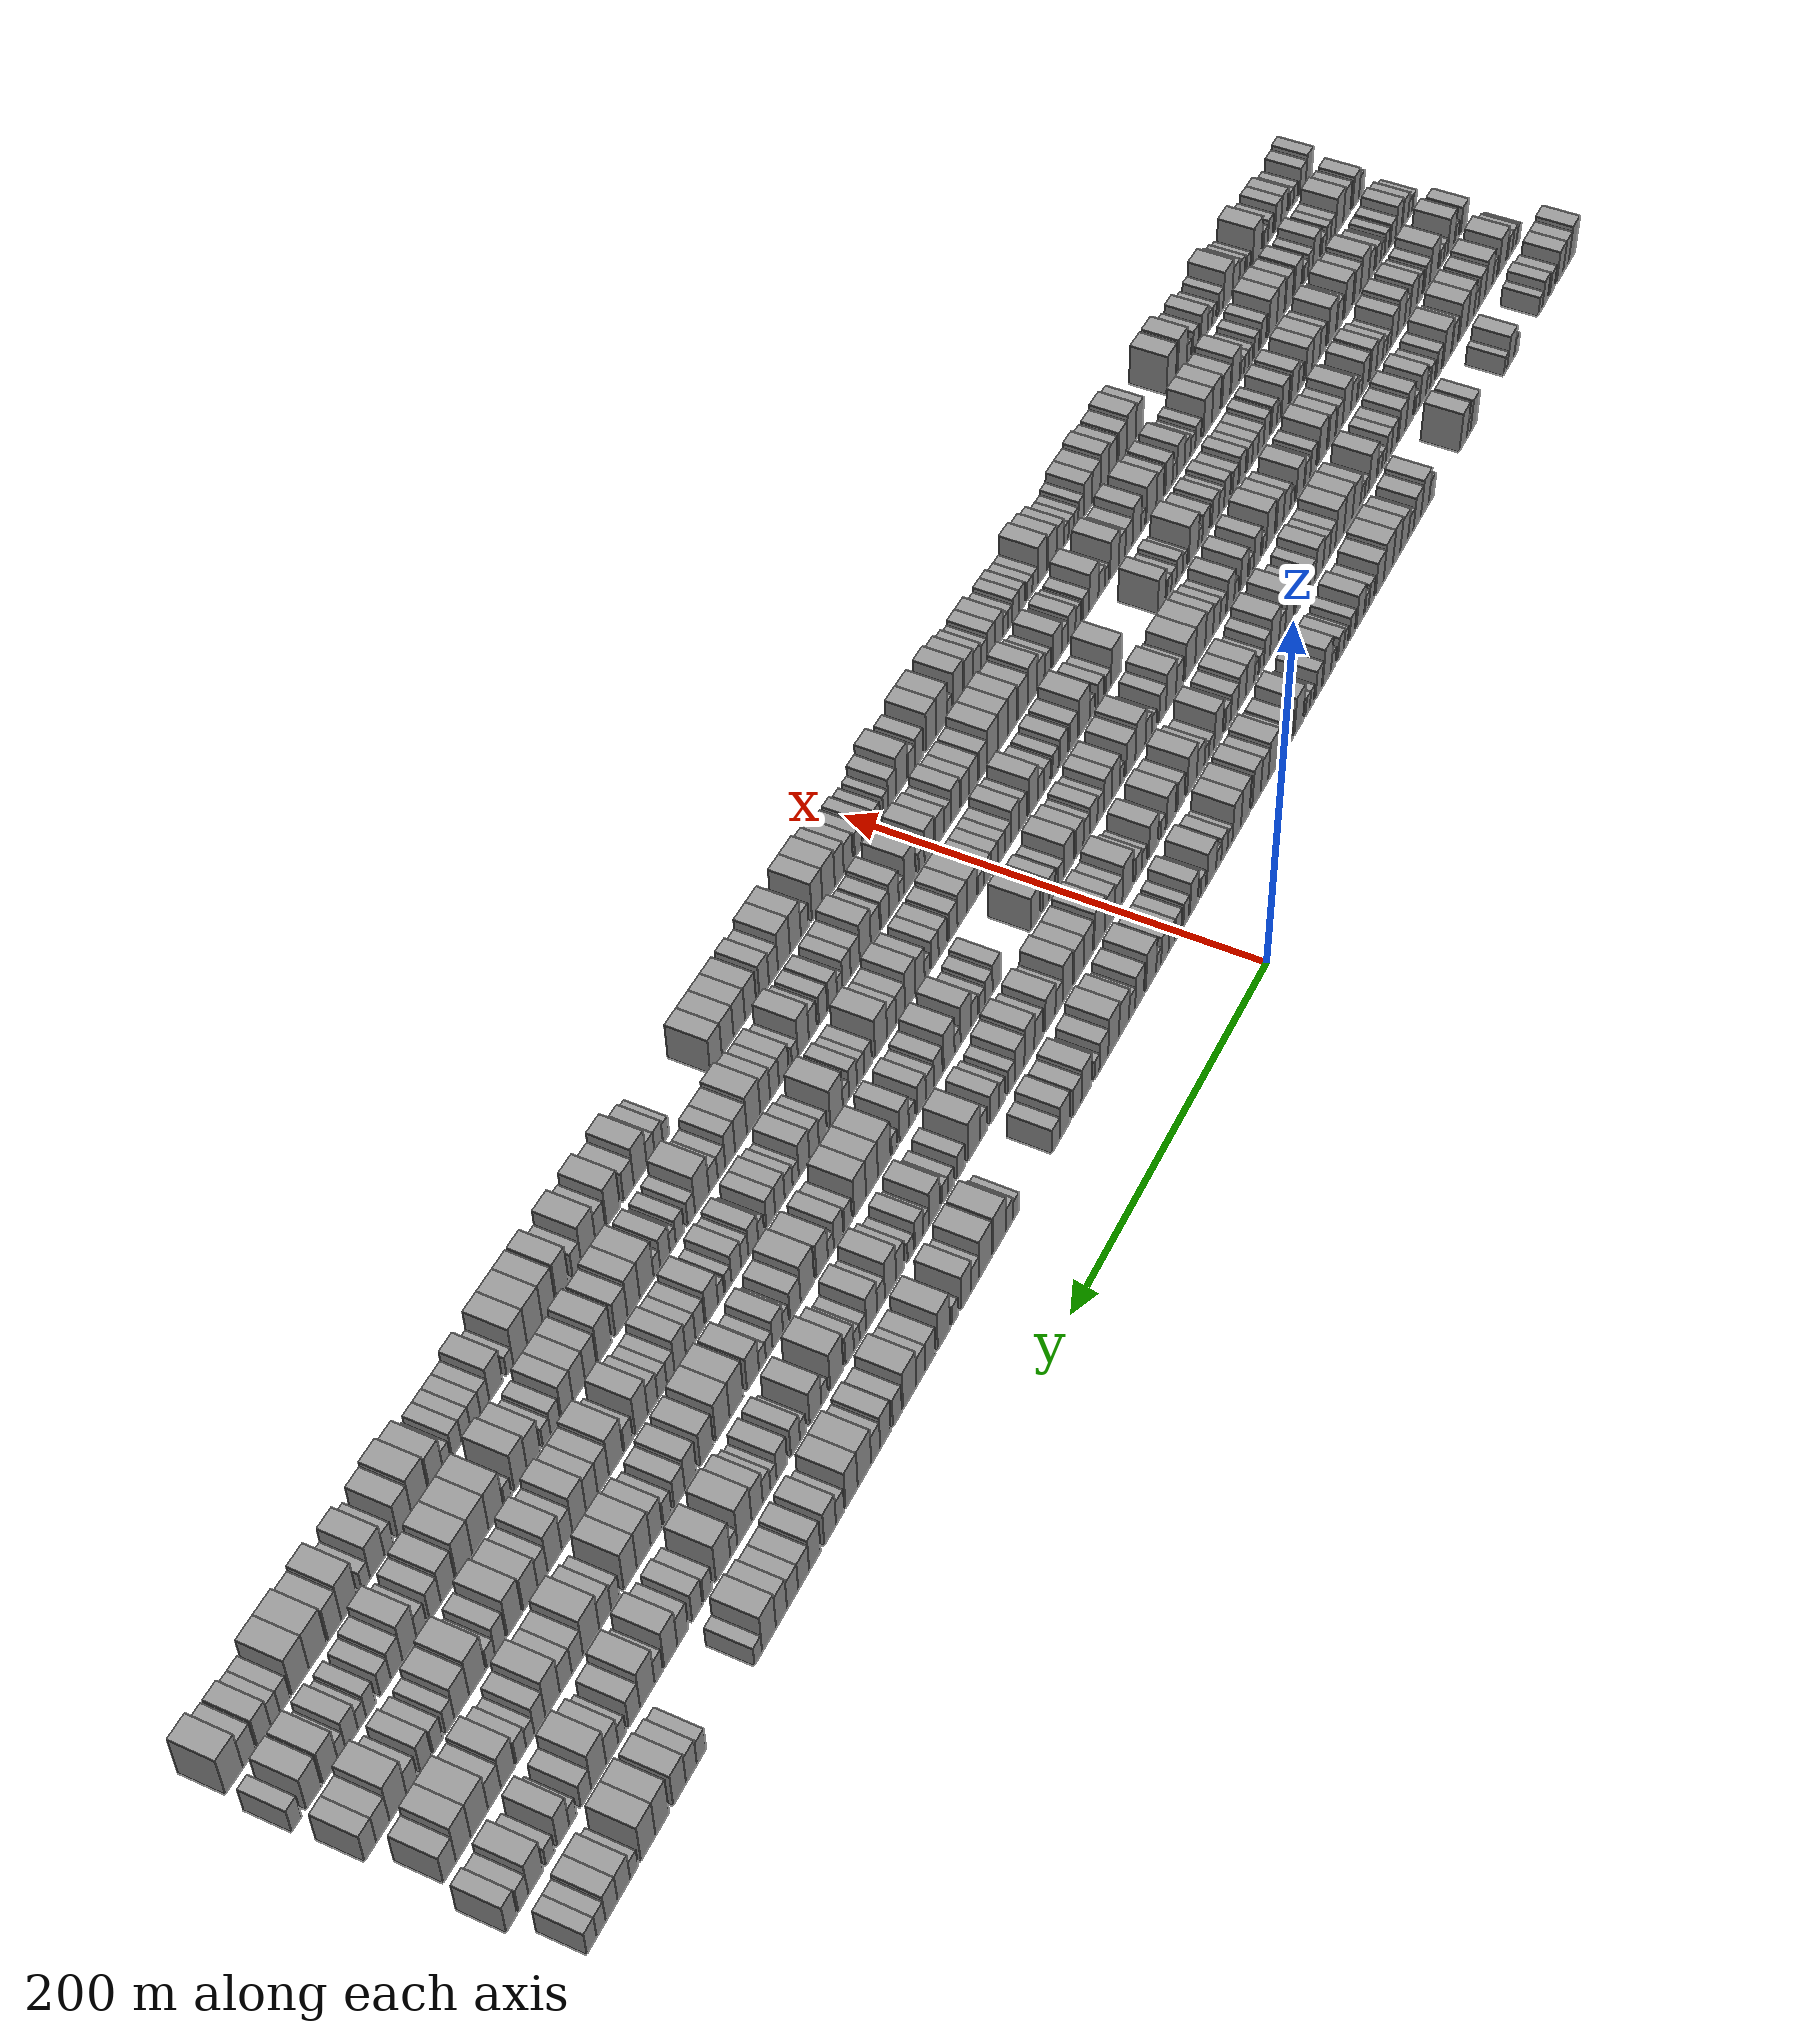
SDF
<sdf version="1.6">
 <world name="default">
  <scene>
   <sky><clouds><speed>12</speed></clouds></sky>
   <ambient>0.4 0.4 0.4 1</ambient>
   <background>0.7 0.7 0.7 1</background>
   <shadows>1</shadows>
  </scene>
  <gravity>0 0 -9.8066</gravity>
  <magnetic_field>6e-06 2.3e-05 -4.2e-05</magnetic_field>
  <physics default="0" name="default_physics" type="ode">
   <ode>
    <solver>
     <type>quick</type>
     <iters>10</iters>
     <sor>1.0</sor>
     <use_dynamic_moi_rescaling>0</use_dynamic_moi_rescaling>
    </solver>
    <constraints>
     <cfm>0</cfm>
     <erp>0.2</erp>
     <contact_max_correcting_vel>100</contact_max_correcting_vel>
     <contact_surface_layer>0.001</contact_surface_layer>
    </constraints>
   </ode>
   <max_step_size>0.004</max_step_size>
   <real_time_factor>1</real_time_factor>
   <real_time_update_rate>250</real_time_update_rate>
  </physics>
  <light name="sun" type="directional">
   <pose>0 0 10 0 0 0</pose>
   <diffuse>0.8 0.8 0.8 1</diffuse>
   <specular>0.2 0.2 0.2 1</specular>
   <attenuation>
    <range>1000</range>
    <constant>0.9</constant>
    <linear>0.01</linear>
    <quadratic>0.001</quadratic>
   </attenuation>
   <direction>-0.5 0.1 -0.9</direction>
  </light>
  <model name="building_1">
   <static>1</static>
   <pose>50.0000 -504.8726 0 0.000000 0.000000 0.000000</pose>
   <link name="link">
    <pose>0 0 12.00 0 0 0</pose>
    <collision name="collision"><geometry><box><size>20.0000 10.2548 24.0000</size></box></geometry></collision>
    <visual name="visual">
     <cast_shadows>0</cast_shadows>
     <geometry><box><size>20.0000 10.2548 24.0000</size></box></geometry>
     <material>
      <script>
       <uri>model://grey_wall/materials/scripts</uri>
       <uri>model://grey_wall/materials/textures</uri>
       <name>vrc/grey_wall</name>
      </script>
     </material>
    </visual>
   </link>
  </model>
  <model name="building_2">
   <static>1</static>
   <pose>50.0000 -495.4982 0 0.000000 0.000000 0.000000</pose>
   <link name="link">
    <pose>0 0 10.50 0 0 0</pose>
    <collision name="collision"><geometry><box><size>20.0000 8.4941 21.0000</size></box></geometry></collision>
    <visual name="visual">
     <cast_shadows>0</cast_shadows>
     <geometry><box><size>20.0000 8.4941 21.0000</size></box></geometry>
     <material>
      <script>
       <uri>model://grey_wall/materials/scripts</uri>
       <uri>model://grey_wall/materials/textures</uri>
       <name>vrc/grey_wall</name>
      </script>
     </material>
    </visual>
   </link>
  </model>
  <model name="building_3">
   <static>1</static>
   <pose>50.0000 -486.2988 0 0.000000 0.000000 0.000000</pose>
   <link name="link">
    <pose>0 0 10.50 0 0 0</pose>
    <collision name="collision"><geometry><box><size>20.0000 9.9047 21.0000</size></box></geometry></collision>
    <visual name="visual">
     <cast_shadows>0</cast_shadows>
     <geometry><box><size>20.0000 9.9047 21.0000</size></box></geometry>
     <material>
      <script>
       <uri>model://grey_wall/materials/scripts</uri>
       <uri>model://grey_wall/materials/textures</uri>
       <name>vrc/grey_wall</name>
      </script>
     </material>
    </visual>
   </link>
  </model>
  <model name="building_4">
   <static>1</static>
   <pose>50.0000 -474.6262 0 0.000000 0.000000 0.000000</pose>
   <link name="link">
    <pose>0 0 7.50 0 0 0</pose>
    <collision name="collision"><geometry><box><size>20.0000 7.4406 15.0000</size></box></geometry></collision>
    <visual name="visual">
     <cast_shadows>0</cast_shadows>
     <geometry><box><size>20.0000 7.4406 15.0000</size></box></geometry>
     <material>
      <script>
       <uri>model://grey_wall/materials/scripts</uri>
       <uri>model://grey_wall/materials/textures</uri>
       <name>vrc/grey_wall</name>
      </script>
     </material>
    </visual>
   </link>
  </model>
  <model name="building_5">
   <static>1</static>
   <pose>50.0000 -463.7522 0 0.000000 0.000000 0.000000</pose>
   <link name="link">
    <pose>0 0 9.00 0 0 0</pose>
    <collision name="collision"><geometry><box><size>20.0000 8.3073 18.0000</size></box></geometry></collision>
    <visual name="visual">
     <cast_shadows>0</cast_shadows>
     <geometry><box><size>20.0000 8.3073 18.0000</size></box></geometry>
     <material>
      <script>
       <uri>model://grey_wall/materials/scripts</uri>
       <uri>model://grey_wall/materials/textures</uri>
       <name>vrc/grey_wall</name>
      </script>
     </material>
    </visual>
   </link>
  </model>
  <model name="building_6">
   <static>1</static>
   <pose>50.0000 -456.7785 0 0.000000 0.000000 0.000000</pose>
   <link name="link">
    <pose>0 0 6.00 0 0 0</pose>
    <collision name="collision"><geometry><box><size>20.0000 5.6403 12.0000</size></box></geometry></collision>
    <visual name="visual">
     <cast_shadows>0</cast_shadows>
     <geometry><box><size>20.0000 5.6403 12.0000</size></box></geometry>
     <material>
      <script>
       <uri>model://grey_wall/materials/scripts</uri>
       <uri>model://grey_wall/materials/textures</uri>
       <name>vrc/grey_wall</name>
      </script>
     </material>
    </visual>
   </link>
  </model>
  <model name="building_7">
   <static>1</static>
   <pose>50.0000 -421.0872 0 0.000000 0.000000 0.000000</pose>
   <link name="link">
    <pose>0 0 6.00 0 0 0</pose>
    <collision name="collision"><geometry><box><size>20.0000 5.9141 12.0000</size></box></geometry></collision>
    <visual name="visual">
     <cast_shadows>0</cast_shadows>
     <geometry><box><size>20.0000 5.9141 12.0000</size></box></geometry>
     <material>
      <script>
       <uri>model://grey_wall/materials/scripts</uri>
       <uri>model://grey_wall/materials/textures</uri>
       <name>vrc/grey_wall</name>
      </script>
     </material>
    </visual>
   </link>
  </model>
  <model name="building_8">
   <static>1</static>
   <pose>50.0000 -413.1430 0 0.000000 0.000000 0.000000</pose>
   <link name="link">
    <pose>0 0 10.50 0 0 0</pose>
    <collision name="collision"><geometry><box><size>20.0000 9.9742 21.0000</size></box></geometry></collision>
    <visual name="visual">
     <cast_shadows>0</cast_shadows>
     <geometry><box><size>20.0000 9.9742 21.0000</size></box></geometry>
     <material>
      <script>
       <uri>model://grey_wall/materials/scripts</uri>
       <uri>model://grey_wall/materials/textures</uri>
       <name>vrc/grey_wall</name>
      </script>
     </material>
    </visual>
   </link>
  </model>
  <model name="building_9">
   <static>1</static>
   <pose>50.0000 -405.6615 0 0.000000 0.000000 0.000000</pose>
   <link name="link">
    <pose>0 0 6.00 0 0 0</pose>
    <collision name="collision"><geometry><box><size>20.0000 4.9888 12.0000</size></box></geometry></collision>
    <visual name="visual">
     <cast_shadows>0</cast_shadows>
     <geometry><box><size>20.0000 4.9888 12.0000</size></box></geometry>
     <material>
      <script>
       <uri>model://grey_wall/materials/scripts</uri>
       <uri>model://grey_wall/materials/textures</uri>
       <name>vrc/grey_wall</name>
      </script>
     </material>
    </visual>
   </link>
  </model>
  <model name="building_10">
   <static>1</static>
   <pose>50.0000 -360.0876 0 0.000000 0.000000 0.000000</pose>
   <link name="link">
    <pose>0 0 10.50 0 0 0</pose>
    <collision name="collision"><geometry><box><size>20.0000 8.7197 21.0000</size></box></geometry></collision>
    <visual name="visual">
     <cast_shadows>0</cast_shadows>
     <geometry><box><size>20.0000 8.7197 21.0000</size></box></geometry>
     <material>
      <script>
       <uri>model://grey_wall/materials/scripts</uri>
       <uri>model://grey_wall/materials/textures</uri>
       <name>vrc/grey_wall</name>
      </script>
     </material>
    </visual>
   </link>
  </model>
  <model name="building_11">
   <static>1</static>
   <pose>50.0000 -353.2707 0 0.000000 0.000000 0.000000</pose>
   <link name="link">
    <pose>0 0 6.00 0 0 0</pose>
    <collision name="collision"><geometry><box><size>20.0000 4.9139 12.0000</size></box></geometry></collision>
    <visual name="visual">
     <cast_shadows>0</cast_shadows>
     <geometry><box><size>20.0000 4.9139 12.0000</size></box></geometry>
     <material>
      <script>
       <uri>model://grey_wall/materials/scripts</uri>
       <uri>model://grey_wall/materials/textures</uri>
       <name>vrc/grey_wall</name>
      </script>
     </material>
    </visual>
   </link>
  </model>
  <model name="building_12">
   <static>1</static>
   <pose>50.0000 -345.7462 0 0.000000 0.000000 0.000000</pose>
   <link name="link">
    <pose>0 0 12.00 0 0 0</pose>
    <collision name="collision"><geometry><box><size>20.0000 10.1351 24.0000</size></box></geometry></collision>
    <visual name="visual">
     <cast_shadows>0</cast_shadows>
     <geometry><box><size>20.0000 10.1351 24.0000</size></box></geometry>
     <material>
      <script>
       <uri>model://grey_wall/materials/scripts</uri>
       <uri>model://grey_wall/materials/textures</uri>
       <name>vrc/grey_wall</name>
      </script>
     </material>
    </visual>
   </link>
  </model>
  <model name="building_13">
   <static>1</static>
   <pose>50.0000 -302.0954 0 0.000000 0.000000 0.000000</pose>
   <link name="link">
    <pose>0 0 7.50 0 0 0</pose>
    <collision name="collision"><geometry><box><size>20.0000 7.0555 15.0000</size></box></geometry></collision>
    <visual name="visual">
     <cast_shadows>0</cast_shadows>
     <geometry><box><size>20.0000 7.0555 15.0000</size></box></geometry>
     <material>
      <script>
       <uri>model://grey_wall/materials/scripts</uri>
       <uri>model://grey_wall/materials/textures</uri>
       <name>vrc/grey_wall</name>
      </script>
     </material>
    </visual>
   </link>
  </model>
  <model name="building_14">
   <static>1</static>
   <pose>50.0000 -293.3849 0 0.000000 0.000000 0.000000</pose>
   <link name="link">
    <pose>0 0 12.00 0 0 0</pose>
    <collision name="collision"><geometry><box><size>20.0000 10.3654 24.0000</size></box></geometry></collision>
    <visual name="visual">
     <cast_shadows>0</cast_shadows>
     <geometry><box><size>20.0000 10.3654 24.0000</size></box></geometry>
     <material>
      <script>
       <uri>model://grey_wall/materials/scripts</uri>
       <uri>model://grey_wall/materials/textures</uri>
       <name>vrc/grey_wall</name>
      </script>
     </material>
    </visual>
   </link>
  </model>
  <model name="building_15">
   <static>1</static>
   <pose>50.0000 -283.2287 0 0.000000 0.000000 0.000000</pose>
   <link name="link">
    <pose>0 0 10.50 0 0 0</pose>
    <collision name="collision"><geometry><box><size>20.0000 9.9471 21.0000</size></box></geometry></collision>
    <visual name="visual">
     <cast_shadows>0</cast_shadows>
     <geometry><box><size>20.0000 9.9471 21.0000</size></box></geometry>
     <material>
      <script>
       <uri>model://grey_wall/materials/scripts</uri>
       <uri>model://grey_wall/materials/textures</uri>
       <name>vrc/grey_wall</name>
      </script>
     </material>
    </visual>
   </link>
  </model>
  <model name="building_16">
   <static>1</static>
   <pose>50.0000 -274.6540 0 0.000000 0.000000 0.000000</pose>
   <link name="link">
    <pose>0 0 7.50 0 0 0</pose>
    <collision name="collision"><geometry><box><size>20.0000 7.2023 15.0000</size></box></geometry></collision>
    <visual name="visual">
     <cast_shadows>0</cast_shadows>
     <geometry><box><size>20.0000 7.2023 15.0000</size></box></geometry>
     <material>
      <script>
       <uri>model://grey_wall/materials/scripts</uri>
       <uri>model://grey_wall/materials/textures</uri>
       <name>vrc/grey_wall</name>
      </script>
     </material>
    </visual>
   </link>
  </model>
  <model name="building_17">
   <static>1</static>
   <pose>50.0000 -265.9230 0 0.000000 0.000000 0.000000</pose>
   <link name="link">
    <pose>0 0 10.50 0 0 0</pose>
    <collision name="collision"><geometry><box><size>20.0000 10.2596 21.0000</size></box></geometry></collision>
    <visual name="visual">
     <cast_shadows>0</cast_shadows>
     <geometry><box><size>20.0000 10.2596 21.0000</size></box></geometry>
     <material>
      <script>
       <uri>model://grey_wall/materials/scripts</uri>
       <uri>model://grey_wall/materials/textures</uri>
       <name>vrc/grey_wall</name>
      </script>
     </material>
    </visual>
   </link>
  </model>
  <model name="building_18">
   <static>1</static>
   <pose>50.0000 -255.9049 0 0.000000 0.000000 0.000000</pose>
   <link name="link">
    <pose>0 0 12.00 0 0 0</pose>
    <collision name="collision"><geometry><box><size>20.0000 9.7765 24.0000</size></box></geometry></collision>
    <visual name="visual">
     <cast_shadows>0</cast_shadows>
     <geometry><box><size>20.0000 9.7765 24.0000</size></box></geometry>
     <material>
      <script>
       <uri>model://grey_wall/materials/scripts</uri>
       <uri>model://grey_wall/materials/textures</uri>
       <name>vrc/grey_wall</name>
      </script>
     </material>
    </visual>
   </link>
  </model>
  <model name="building_19">
   <static>1</static>
   <pose>50.0000 -245.1341 0 0.000000 0.000000 0.000000</pose>
   <link name="link">
    <pose>0 0 12.00 0 0 0</pose>
    <collision name="collision"><geometry><box><size>20.0000 11.7652 24.0000</size></box></geometry></collision>
    <visual name="visual">
     <cast_shadows>0</cast_shadows>
     <geometry><box><size>20.0000 11.7652 24.0000</size></box></geometry>
     <material>
      <script>
       <uri>model://grey_wall/materials/scripts</uri>
       <uri>model://grey_wall/materials/textures</uri>
       <name>vrc/grey_wall</name>
      </script>
     </material>
    </visual>
   </link>
  </model>
  <model name="building_20">
   <static>1</static>
   <pose>50.0000 -234.0665 0 0.000000 0.000000 0.000000</pose>
   <link name="link">
    <pose>0 0 10.50 0 0 0</pose>
    <collision name="collision"><geometry><box><size>20.0000 10.3699 21.0000</size></box></geometry></collision>
    <visual name="visual">
     <cast_shadows>0</cast_shadows>
     <geometry><box><size>20.0000 10.3699 21.0000</size></box></geometry>
     <material>
      <script>
       <uri>model://grey_wall/materials/scripts</uri>
       <uri>model://grey_wall/materials/textures</uri>
       <name>vrc/grey_wall</name>
      </script>
     </material>
    </visual>
   </link>
  </model>
  <model name="building_21">
   <static>1</static>
   <pose>50.0000 -223.5535 0 0.000000 0.000000 0.000000</pose>
   <link name="link">
    <pose>0 0 7.50 0 0 0</pose>
    <collision name="collision"><geometry><box><size>20.0000 6.6561 15.0000</size></box></geometry></collision>
    <visual name="visual">
     <cast_shadows>0</cast_shadows>
     <geometry><box><size>20.0000 6.6561 15.0000</size></box></geometry>
     <material>
      <script>
       <uri>model://grey_wall/materials/scripts</uri>
       <uri>model://grey_wall/materials/textures</uri>
       <name>vrc/grey_wall</name>
      </script>
     </material>
    </visual>
   </link>
  </model>
  <model name="building_22">
   <static>1</static>
   <pose>50.0000 -217.7950 0 0.000000 0.000000 0.000000</pose>
   <link name="link">
    <pose>0 0 6.00 0 0 0</pose>
    <collision name="collision"><geometry><box><size>20.0000 4.8610 12.0000</size></box></geometry></collision>
    <visual name="visual">
     <cast_shadows>0</cast_shadows>
     <geometry><box><size>20.0000 4.8610 12.0000</size></box></geometry>
     <material>
      <script>
       <uri>model://grey_wall/materials/scripts</uri>
       <uri>model://grey_wall/materials/textures</uri>
       <name>vrc/grey_wall</name>
      </script>
     </material>
    </visual>
   </link>
  </model>
  <model name="building_23">
   <static>1</static>
   <pose>50.0000 -209.5757 0 0.000000 0.000000 0.000000</pose>
   <link name="link">
    <pose>0 0 10.50 0 0 0</pose>
    <collision name="collision"><geometry><box><size>20.0000 9.5776 21.0000</size></box></geometry></collision>
    <visual name="visual">
     <cast_shadows>0</cast_shadows>
     <geometry><box><size>20.0000 9.5776 21.0000</size></box></geometry>
     <material>
      <script>
       <uri>model://grey_wall/materials/scripts</uri>
       <uri>model://grey_wall/materials/textures</uri>
       <name>vrc/grey_wall</name>
      </script>
     </material>
    </visual>
   </link>
  </model>
  <model name="building_24">
   <static>1</static>
   <pose>50.0000 -199.3336 0 0.000000 0.000000 0.000000</pose>
   <link name="link">
    <pose>0 0 7.50 0 0 0</pose>
    <collision name="collision"><geometry><box><size>20.0000 6.9065 15.0000</size></box></geometry></collision>
    <visual name="visual">
     <cast_shadows>0</cast_shadows>
     <geometry><box><size>20.0000 6.9065 15.0000</size></box></geometry>
     <material>
      <script>
       <uri>model://grey_wall/materials/scripts</uri>
       <uri>model://grey_wall/materials/textures</uri>
       <name>vrc/grey_wall</name>
      </script>
     </material>
    </visual>
   </link>
  </model>
  <model name="building_25">
   <static>1</static>
   <pose>50.0000 -191.3330 0 0.000000 0.000000 0.000000</pose>
   <link name="link">
    <pose>0 0 6.00 0 0 0</pose>
    <collision name="collision"><geometry><box><size>20.0000 5.0947 12.0000</size></box></geometry></collision>
    <visual name="visual">
     <cast_shadows>0</cast_shadows>
     <geometry><box><size>20.0000 5.0947 12.0000</size></box></geometry>
     <material>
      <script>
       <uri>model://grey_wall/materials/scripts</uri>
       <uri>model://grey_wall/materials/textures</uri>
       <name>vrc/grey_wall</name>
      </script>
     </material>
    </visual>
   </link>
  </model>
  <model name="building_26">
   <static>1</static>
   <pose>50.0000 -185.2077 0 0.000000 0.000000 0.000000</pose>
   <link name="link">
    <pose>0 0 7.50 0 0 0</pose>
    <collision name="collision"><geometry><box><size>20.0000 7.1559 15.0000</size></box></geometry></collision>
    <visual name="visual">
     <cast_shadows>0</cast_shadows>
     <geometry><box><size>20.0000 7.1559 15.0000</size></box></geometry>
     <material>
      <script>
       <uri>model://grey_wall/materials/scripts</uri>
       <uri>model://grey_wall/materials/textures</uri>
       <name>vrc/grey_wall</name>
      </script>
     </material>
    </visual>
   </link>
  </model>
  <model name="building_27">
   <static>1</static>
   <pose>50.0000 -175.7184 0 0.000000 0.000000 0.000000</pose>
   <link name="link">
    <pose>0 0 6.00 0 0 0</pose>
    <collision name="collision"><geometry><box><size>20.0000 5.8227 12.0000</size></box></geometry></collision>
    <visual name="visual">
     <cast_shadows>0</cast_shadows>
     <geometry><box><size>20.0000 5.8227 12.0000</size></box></geometry>
     <material>
      <script>
       <uri>model://grey_wall/materials/scripts</uri>
       <uri>model://grey_wall/materials/textures</uri>
       <name>vrc/grey_wall</name>
      </script>
     </material>
    </visual>
   </link>
  </model>
  <model name="building_28">
   <static>1</static>
   <pose>50.0000 -167.8051 0 0.000000 0.000000 0.000000</pose>
   <link name="link">
    <pose>0 0 12.00 0 0 0</pose>
    <collision name="collision"><geometry><box><size>20.0000 10.0038 24.0000</size></box></geometry></collision>
    <visual name="visual">
     <cast_shadows>0</cast_shadows>
     <geometry><box><size>20.0000 10.0038 24.0000</size></box></geometry>
     <material>
      <script>
       <uri>model://grey_wall/materials/scripts</uri>
       <uri>model://grey_wall/materials/textures</uri>
       <name>vrc/grey_wall</name>
      </script>
     </material>
    </visual>
   </link>
  </model>
  <model name="building_29">
   <static>1</static>
   <pose>50.0000 -158.0018 0 0.000000 0.000000 0.000000</pose>
   <link name="link">
    <pose>0 0 9.00 0 0 0</pose>
    <collision name="collision"><geometry><box><size>20.0000 7.6028 18.0000</size></box></geometry></collision>
    <visual name="visual">
     <cast_shadows>0</cast_shadows>
     <geometry><box><size>20.0000 7.6028 18.0000</size></box></geometry>
     <material>
      <script>
       <uri>model://grey_wall/materials/scripts</uri>
       <uri>model://grey_wall/materials/textures</uri>
       <name>vrc/grey_wall</name>
      </script>
     </material>
    </visual>
   </link>
  </model>
  <model name="building_30">
   <static>1</static>
   <pose>50.0000 -149.7860 0 0.000000 0.000000 0.000000</pose>
   <link name="link">
    <pose>0 0 6.00 0 0 0</pose>
    <collision name="collision"><geometry><box><size>20.0000 4.8288 12.0000</size></box></geometry></collision>
    <visual name="visual">
     <cast_shadows>0</cast_shadows>
     <geometry><box><size>20.0000 4.8288 12.0000</size></box></geometry>
     <material>
      <script>
       <uri>model://grey_wall/materials/scripts</uri>
       <uri>model://grey_wall/materials/textures</uri>
       <name>vrc/grey_wall</name>
      </script>
     </material>
    </visual>
   </link>
  </model>
  <model name="building_31">
   <static>1</static>
   <pose>50.0000 -144.7720 0 0.000000 0.000000 0.000000</pose>
   <link name="link">
    <pose>0 0 6.00 0 0 0</pose>
    <collision name="collision"><geometry><box><size>20.0000 5.1991 12.0000</size></box></geometry></collision>
    <visual name="visual">
     <cast_shadows>0</cast_shadows>
     <geometry><box><size>20.0000 5.1991 12.0000</size></box></geometry>
     <material>
      <script>
       <uri>model://grey_wall/materials/scripts</uri>
       <uri>model://grey_wall/materials/textures</uri>
       <name>vrc/grey_wall</name>
      </script>
     </material>
    </visual>
   </link>
  </model>
  <model name="building_32">
   <static>1</static>
   <pose>50.0000 -134.0197 0 0.000000 0.000000 0.000000</pose>
   <link name="link">
    <pose>0 0 12.00 0 0 0</pose>
    <collision name="collision"><geometry><box><size>20.0000 10.3055 24.0000</size></box></geometry></collision>
    <visual name="visual">
     <cast_shadows>0</cast_shadows>
     <geometry><box><size>20.0000 10.3055 24.0000</size></box></geometry>
     <material>
      <script>
       <uri>model://grey_wall/materials/scripts</uri>
       <uri>model://grey_wall/materials/textures</uri>
       <name>vrc/grey_wall</name>
      </script>
     </material>
    </visual>
   </link>
  </model>
  <model name="building_33">
   <static>1</static>
   <pose>50.0000 -122.4047 0 0.000000 0.000000 0.000000</pose>
   <link name="link">
    <pose>0 0 9.00 0 0 0</pose>
    <collision name="collision"><geometry><box><size>20.0000 8.9245 18.0000</size></box></geometry></collision>
    <visual name="visual">
     <cast_shadows>0</cast_shadows>
     <geometry><box><size>20.0000 8.9245 18.0000</size></box></geometry>
     <material>
      <script>
       <uri>model://grey_wall/materials/scripts</uri>
       <uri>model://grey_wall/materials/textures</uri>
       <name>vrc/grey_wall</name>
      </script>
     </material>
    </visual>
   </link>
  </model>
  <model name="building_34">
   <static>1</static>
   <pose>50.0000 -113.0738 0 0.000000 0.000000 0.000000</pose>
   <link name="link">
    <pose>0 0 9.00 0 0 0</pose>
    <collision name="collision"><geometry><box><size>20.0000 7.7372 18.0000</size></box></geometry></collision>
    <visual name="visual">
     <cast_shadows>0</cast_shadows>
     <geometry><box><size>20.0000 7.7372 18.0000</size></box></geometry>
     <material>
      <script>
       <uri>model://grey_wall/materials/scripts</uri>
       <uri>model://grey_wall/materials/textures</uri>
       <name>vrc/grey_wall</name>
      </script>
     </material>
    </visual>
   </link>
  </model>
  <model name="building_35">
   <static>1</static>
   <pose>50.0000 -103.7000 0 0.000000 0.000000 0.000000</pose>
   <link name="link">
    <pose>0 0 12.00 0 0 0</pose>
    <collision name="collision"><geometry><box><size>20.0000 11.0105 24.0000</size></box></geometry></collision>
    <visual name="visual">
     <cast_shadows>0</cast_shadows>
     <geometry><box><size>20.0000 11.0105 24.0000</size></box></geometry>
     <material>
      <script>
       <uri>model://grey_wall/materials/scripts</uri>
       <uri>model://grey_wall/materials/textures</uri>
       <name>vrc/grey_wall</name>
      </script>
     </material>
    </visual>
   </link>
  </model>
  <model name="building_36">
   <static>1</static>
   <pose>50.0000 -93.7858 0 0.000000 0.000000 0.000000</pose>
   <link name="link">
    <pose>0 0 10.50 0 0 0</pose>
    <collision name="collision"><geometry><box><size>20.0000 8.8179 21.0000</size></box></geometry></collision>
    <visual name="visual">
     <cast_shadows>0</cast_shadows>
     <geometry><box><size>20.0000 8.8179 21.0000</size></box></geometry>
     <material>
      <script>
       <uri>model://grey_wall/materials/scripts</uri>
       <uri>model://grey_wall/materials/textures</uri>
       <name>vrc/grey_wall</name>
      </script>
     </material>
    </visual>
   </link>
  </model>
  <model name="building_37">
   <static>1</static>
   <pose>50.0000 -84.5160 0 0.000000 0.000000 0.000000</pose>
   <link name="link">
    <pose>0 0 12.00 0 0 0</pose>
    <collision name="collision"><geometry><box><size>20.0000 9.7215 24.0000</size></box></geometry></collision>
    <visual name="visual">
     <cast_shadows>0</cast_shadows>
     <geometry><box><size>20.0000 9.7215 24.0000</size></box></geometry>
     <material>
      <script>
       <uri>model://grey_wall/materials/scripts</uri>
       <uri>model://grey_wall/materials/textures</uri>
       <name>vrc/grey_wall</name>
      </script>
     </material>
    </visual>
   </link>
  </model>
  <model name="building_38">
   <static>1</static>
   <pose>50.0000 -71.7117 0 0.000000 0.000000 0.000000</pose>
   <link name="link">
    <pose>0 0 12.00 0 0 0</pose>
    <collision name="collision"><geometry><box><size>20.0000 9.8872 24.0000</size></box></geometry></collision>
    <visual name="visual">
     <cast_shadows>0</cast_shadows>
     <geometry><box><size>20.0000 9.8872 24.0000</size></box></geometry>
     <material>
      <script>
       <uri>model://grey_wall/materials/scripts</uri>
       <uri>model://grey_wall/materials/textures</uri>
       <name>vrc/grey_wall</name>
      </script>
     </material>
    </visual>
   </link>
  </model>
  <model name="building_39">
   <static>1</static>
   <pose>50.0000 -61.9375 0 0.000000 0.000000 0.000000</pose>
   <link name="link">
    <pose>0 0 12.00 0 0 0</pose>
    <collision name="collision"><geometry><box><size>20.0000 9.6612 24.0000</size></box></geometry></collision>
    <visual name="visual">
     <cast_shadows>0</cast_shadows>
     <geometry><box><size>20.0000 9.6612 24.0000</size></box></geometry>
     <material>
      <script>
       <uri>model://grey_wall/materials/scripts</uri>
       <uri>model://grey_wall/materials/textures</uri>
       <name>vrc/grey_wall</name>
      </script>
     </material>
    </visual>
   </link>
  </model>
  <model name="building_40">
   <static>1</static>
   <pose>50.0000 -54.3264 0 0.000000 0.000000 0.000000</pose>
   <link name="link">
    <pose>0 0 6.00 0 0 0</pose>
    <collision name="collision"><geometry><box><size>20.0000 5.5611 12.0000</size></box></geometry></collision>
    <visual name="visual">
     <cast_shadows>0</cast_shadows>
     <geometry><box><size>20.0000 5.5611 12.0000</size></box></geometry>
     <material>
      <script>
       <uri>model://grey_wall/materials/scripts</uri>
       <uri>model://grey_wall/materials/textures</uri>
       <name>vrc/grey_wall</name>
      </script>
     </material>
    </visual>
   </link>
  </model>
  <model name="building_41">
   <static>1</static>
   <pose>50.0000 -48.1010 0 0.000000 0.000000 0.000000</pose>
   <link name="link">
    <pose>0 0 7.50 0 0 0</pose>
    <collision name="collision"><geometry><box><size>20.0000 6.8895 15.0000</size></box></geometry></collision>
    <visual name="visual">
     <cast_shadows>0</cast_shadows>
     <geometry><box><size>20.0000 6.8895 15.0000</size></box></geometry>
     <material>
      <script>
       <uri>model://grey_wall/materials/scripts</uri>
       <uri>model://grey_wall/materials/textures</uri>
       <name>vrc/grey_wall</name>
      </script>
     </material>
    </visual>
   </link>
  </model>
  <model name="building_42">
   <static>1</static>
   <pose>50.0000 -41.7682 0 0.000000 0.000000 0.000000</pose>
   <link name="link">
    <pose>0 0 6.00 0 0 0</pose>
    <collision name="collision"><geometry><box><size>20.0000 5.7761 12.0000</size></box></geometry></collision>
    <visual name="visual">
     <cast_shadows>0</cast_shadows>
     <geometry><box><size>20.0000 5.7761 12.0000</size></box></geometry>
     <material>
      <script>
       <uri>model://grey_wall/materials/scripts</uri>
       <uri>model://grey_wall/materials/textures</uri>
       <name>vrc/grey_wall</name>
      </script>
     </material>
    </visual>
   </link>
  </model>
  <model name="building_43">
   <static>1</static>
   <pose>50.0000 -33.7188 0 0.000000 0.000000 0.000000</pose>
   <link name="link">
    <pose>0 0 10.50 0 0 0</pose>
    <collision name="collision"><geometry><box><size>20.0000 10.3228 21.0000</size></box></geometry></collision>
    <visual name="visual">
     <cast_shadows>0</cast_shadows>
     <geometry><box><size>20.0000 10.3228 21.0000</size></box></geometry>
     <material>
      <script>
       <uri>model://grey_wall/materials/scripts</uri>
       <uri>model://grey_wall/materials/textures</uri>
       <name>vrc/grey_wall</name>
      </script>
     </material>
    </visual>
   </link>
  </model>
  <model name="building_44">
   <static>1</static>
   <pose>50.0000 -24.6572 0 0.000000 0.000000 0.000000</pose>
   <link name="link">
    <pose>0 0 6.00 0 0 0</pose>
    <collision name="collision"><geometry><box><size>20.0000 5.8003 12.0000</size></box></geometry></collision>
    <visual name="visual">
     <cast_shadows>0</cast_shadows>
     <geometry><box><size>20.0000 5.8003 12.0000</size></box></geometry>
     <material>
      <script>
       <uri>model://grey_wall/materials/scripts</uri>
       <uri>model://grey_wall/materials/textures</uri>
       <name>vrc/grey_wall</name>
      </script>
     </material>
    </visual>
   </link>
  </model>
  <model name="building_45">
   <static>1</static>
   <pose>50.0000 -14.4019 0 0.000000 0.000000 0.000000</pose>
   <link name="link">
    <pose>0 0 10.50 0 0 0</pose>
    <collision name="collision"><geometry><box><size>20.0000 8.7104 21.0000</size></box></geometry></collision>
    <visual name="visual">
     <cast_shadows>0</cast_shadows>
     <geometry><box><size>20.0000 8.7104 21.0000</size></box></geometry>
     <material>
      <script>
       <uri>model://grey_wall/materials/scripts</uri>
       <uri>model://grey_wall/materials/textures</uri>
       <name>vrc/grey_wall</name>
      </script>
     </material>
    </visual>
   </link>
  </model>
  <model name="building_46">
   <static>1</static>
   <pose>50.0000 -5.9768 0 0.000000 0.000000 0.000000</pose>
   <link name="link">
    <pose>0 0 7.50 0 0 0</pose>
    <collision name="collision"><geometry><box><size>20.0000 6.1398 15.0000</size></box></geometry></collision>
    <visual name="visual">
     <cast_shadows>0</cast_shadows>
     <geometry><box><size>20.0000 6.1398 15.0000</size></box></geometry>
     <material>
      <script>
       <uri>model://grey_wall/materials/scripts</uri>
       <uri>model://grey_wall/materials/textures</uri>
       <name>vrc/grey_wall</name>
      </script>
     </material>
    </visual>
   </link>
  </model>
  <model name="building_47">
   <static>1</static>
   <pose>50.0000 2.5735 0 0.000000 0.000000 0.000000</pose>
   <link name="link">
    <pose>0 0 7.50 0 0 0</pose>
    <collision name="collision"><geometry><box><size>20.0000 6.9609 15.0000</size></box></geometry></collision>
    <visual name="visual">
     <cast_shadows>0</cast_shadows>
     <geometry><box><size>20.0000 6.9609 15.0000</size></box></geometry>
     <material>
      <script>
       <uri>model://grey_wall/materials/scripts</uri>
       <uri>model://grey_wall/materials/textures</uri>
       <name>vrc/grey_wall</name>
      </script>
     </material>
    </visual>
   </link>
  </model>
  <model name="building_48">
   <static>1</static>
   <pose>50.0000 9.4496 0 0.000000 0.000000 0.000000</pose>
   <link name="link">
    <pose>0 0 7.50 0 0 0</pose>
    <collision name="collision"><geometry><box><size>20.0000 6.7913 15.0000</size></box></geometry></collision>
    <visual name="visual">
     <cast_shadows>0</cast_shadows>
     <geometry><box><size>20.0000 6.7913 15.0000</size></box></geometry>
     <material>
      <script>
       <uri>model://grey_wall/materials/scripts</uri>
       <uri>model://grey_wall/materials/textures</uri>
       <name>vrc/grey_wall</name>
      </script>
     </material>
    </visual>
   </link>
  </model>
  <model name="building_49">
   <static>1</static>
   <pose>50.0000 16.8193 0 0.000000 0.000000 0.000000</pose>
   <link name="link">
    <pose>0 0 9.00 0 0 0</pose>
    <collision name="collision"><geometry><box><size>20.0000 7.9480 18.0000</size></box></geometry></collision>
    <visual name="visual">
     <cast_shadows>0</cast_shadows>
     <geometry><box><size>20.0000 7.9480 18.0000</size></box></geometry>
     <material>
      <script>
       <uri>model://grey_wall/materials/scripts</uri>
       <uri>model://grey_wall/materials/textures</uri>
       <name>vrc/grey_wall</name>
      </script>
     </material>
    </visual>
   </link>
  </model>
  <model name="building_50">
   <static>1</static>
   <pose>50.0000 23.4290 0 0.000000 0.000000 0.000000</pose>
   <link name="link">
    <pose>0 0 6.00 0 0 0</pose>
    <collision name="collision"><geometry><box><size>20.0000 5.2714 12.0000</size></box></geometry></collision>
    <visual name="visual">
     <cast_shadows>0</cast_shadows>
     <geometry><box><size>20.0000 5.2714 12.0000</size></box></geometry>
     <material>
      <script>
       <uri>model://grey_wall/materials/scripts</uri>
       <uri>model://grey_wall/materials/textures</uri>
       <name>vrc/grey_wall</name>
      </script>
     </material>
    </visual>
   </link>
  </model>
  <model name="building_51">
   <static>1</static>
   <pose>50.0000 31.4627 0 0.000000 0.000000 0.000000</pose>
   <link name="link">
    <pose>0 0 12.00 0 0 0</pose>
    <collision name="collision"><geometry><box><size>20.0000 10.7959 24.0000</size></box></geometry></collision>
    <visual name="visual">
     <cast_shadows>0</cast_shadows>
     <geometry><box><size>20.0000 10.7959 24.0000</size></box></geometry>
     <material>
      <script>
       <uri>model://grey_wall/materials/scripts</uri>
       <uri>model://grey_wall/materials/textures</uri>
       <name>vrc/grey_wall</name>
      </script>
     </material>
    </visual>
   </link>
  </model>
  <model name="building_52">
   <static>1</static>
   <pose>50.0000 43.4519 0 0.000000 0.000000 0.000000</pose>
   <link name="link">
    <pose>0 0 10.50 0 0 0</pose>
    <collision name="collision"><geometry><box><size>20.0000 9.1825 21.0000</size></box></geometry></collision>
    <visual name="visual">
     <cast_shadows>0</cast_shadows>
     <geometry><box><size>20.0000 9.1825 21.0000</size></box></geometry>
     <material>
      <script>
       <uri>model://grey_wall/materials/scripts</uri>
       <uri>model://grey_wall/materials/textures</uri>
       <name>vrc/grey_wall</name>
      </script>
     </material>
    </visual>
   </link>
  </model>
  <model name="building_53">
   <static>1</static>
   <pose>50.0000 51.2084 0 0.000000 0.000000 0.000000</pose>
   <link name="link">
    <pose>0 0 7.50 0 0 0</pose>
    <collision name="collision"><geometry><box><size>20.0000 6.3305 15.0000</size></box></geometry></collision>
    <visual name="visual">
     <cast_shadows>0</cast_shadows>
     <geometry><box><size>20.0000 6.3305 15.0000</size></box></geometry>
     <material>
      <script>
       <uri>model://grey_wall/materials/scripts</uri>
       <uri>model://grey_wall/materials/textures</uri>
       <name>vrc/grey_wall</name>
      </script>
     </material>
    </visual>
   </link>
  </model>
  <model name="building_54">
   <static>1</static>
   <pose>50.0000 59.5419 0 0.000000 0.000000 0.000000</pose>
   <link name="link">
    <pose>0 0 10.50 0 0 0</pose>
    <collision name="collision"><geometry><box><size>20.0000 10.3367 21.0000</size></box></geometry></collision>
    <visual name="visual">
     <cast_shadows>0</cast_shadows>
     <geometry><box><size>20.0000 10.3367 21.0000</size></box></geometry>
     <material>
      <script>
       <uri>model://grey_wall/materials/scripts</uri>
       <uri>model://grey_wall/materials/textures</uri>
       <name>vrc/grey_wall</name>
      </script>
     </material>
    </visual>
   </link>
  </model>
  <model name="building_55">
   <static>1</static>
   <pose>50.0000 70.1673 0 0.000000 0.000000 0.000000</pose>
   <link name="link">
    <pose>0 0 12.00 0 0 0</pose>
    <collision name="collision"><geometry><box><size>20.0000 10.9141 24.0000</size></box></geometry></collision>
    <visual name="visual">
     <cast_shadows>0</cast_shadows>
     <geometry><box><size>20.0000 10.9141 24.0000</size></box></geometry>
     <material>
      <script>
       <uri>model://grey_wall/materials/scripts</uri>
       <uri>model://grey_wall/materials/textures</uri>
       <name>vrc/grey_wall</name>
      </script>
     </material>
    </visual>
   </link>
  </model>
  <model name="building_56">
   <static>1</static>
   <pose>50.0000 80.0565 0 0.000000 0.000000 0.000000</pose>
   <link name="link">
    <pose>0 0 9.00 0 0 0</pose>
    <collision name="collision"><geometry><box><size>20.0000 8.8642 18.0000</size></box></geometry></collision>
    <visual name="visual">
     <cast_shadows>0</cast_shadows>
     <geometry><box><size>20.0000 8.8642 18.0000</size></box></geometry>
     <material>
      <script>
       <uri>model://grey_wall/materials/scripts</uri>
       <uri>model://grey_wall/materials/textures</uri>
       <name>vrc/grey_wall</name>
      </script>
     </material>
    </visual>
   </link>
  </model>
  <model name="building_57">
   <static>1</static>
   <pose>50.0000 87.0178 0 0.000000 0.000000 0.000000</pose>
   <link name="link">
    <pose>0 0 6.00 0 0 0</pose>
    <collision name="collision"><geometry><box><size>20.0000 5.0583 12.0000</size></box></geometry></collision>
    <visual name="visual">
     <cast_shadows>0</cast_shadows>
     <geometry><box><size>20.0000 5.0583 12.0000</size></box></geometry>
     <material>
      <script>
       <uri>model://grey_wall/materials/scripts</uri>
       <uri>model://grey_wall/materials/textures</uri>
       <name>vrc/grey_wall</name>
      </script>
     </material>
    </visual>
   </link>
  </model>
  <model name="building_58">
   <static>1</static>
   <pose>50.0000 97.5212 0 0.000000 0.000000 0.000000</pose>
   <link name="link">
    <pose>0 0 10.50 0 0 0</pose>
    <collision name="collision"><geometry><box><size>20.0000 9.9485 21.0000</size></box></geometry></collision>
    <visual name="visual">
     <cast_shadows>0</cast_shadows>
     <geometry><box><size>20.0000 9.9485 21.0000</size></box></geometry>
     <material>
      <script>
       <uri>model://grey_wall/materials/scripts</uri>
       <uri>model://grey_wall/materials/textures</uri>
       <name>vrc/grey_wall</name>
      </script>
     </material>
    </visual>
   </link>
  </model>
  <model name="building_59">
   <static>1</static>
   <pose>50.0000 106.7962 0 0.000000 0.000000 0.000000</pose>
   <link name="link">
    <pose>0 0 9.00 0 0 0</pose>
    <collision name="collision"><geometry><box><size>20.0000 8.6015 18.0000</size></box></geometry></collision>
    <visual name="visual">
     <cast_shadows>0</cast_shadows>
     <geometry><box><size>20.0000 8.6015 18.0000</size></box></geometry>
     <material>
      <script>
       <uri>model://grey_wall/materials/scripts</uri>
       <uri>model://grey_wall/materials/textures</uri>
       <name>vrc/grey_wall</name>
      </script>
     </material>
    </visual>
   </link>
  </model>
  <model name="building_60">
   <static>1</static>
   <pose>50.0000 118.9928 0 0.000000 0.000000 0.000000</pose>
   <link name="link">
    <pose>0 0 10.50 0 0 0</pose>
    <collision name="collision"><geometry><box><size>20.0000 9.7918 21.0000</size></box></geometry></collision>
    <visual name="visual">
     <cast_shadows>0</cast_shadows>
     <geometry><box><size>20.0000 9.7918 21.0000</size></box></geometry>
     <material>
      <script>
       <uri>model://grey_wall/materials/scripts</uri>
       <uri>model://grey_wall/materials/textures</uri>
       <name>vrc/grey_wall</name>
      </script>
     </material>
    </visual>
   </link>
  </model>
  <model name="building_61">
   <static>1</static>
   <pose>50.0000 127.6068 0 0.000000 0.000000 0.000000</pose>
   <link name="link">
    <pose>0 0 7.50 0 0 0</pose>
    <collision name="collision"><geometry><box><size>20.0000 7.4362 15.0000</size></box></geometry></collision>
    <visual name="visual">
     <cast_shadows>0</cast_shadows>
     <geometry><box><size>20.0000 7.4362 15.0000</size></box></geometry>
     <material>
      <script>
       <uri>model://grey_wall/materials/scripts</uri>
       <uri>model://grey_wall/materials/textures</uri>
       <name>vrc/grey_wall</name>
      </script>
     </material>
    </visual>
   </link>
  </model>
  <model name="building_62">
   <static>1</static>
   <pose>50.0000 165.6647 0 0.000000 0.000000 0.000000</pose>
   <link name="link">
    <pose>0 0 6.00 0 0 0</pose>
    <collision name="collision"><geometry><box><size>20.0000 5.5599 12.0000</size></box></geometry></collision>
    <visual name="visual">
     <cast_shadows>0</cast_shadows>
     <geometry><box><size>20.0000 5.5599 12.0000</size></box></geometry>
     <material>
      <script>
       <uri>model://grey_wall/materials/scripts</uri>
       <uri>model://grey_wall/materials/textures</uri>
       <name>vrc/grey_wall</name>
      </script>
     </material>
    </visual>
   </link>
  </model>
  <model name="building_63">
   <static>1</static>
   <pose>50.0000 172.0886 0 0.000000 0.000000 0.000000</pose>
   <link name="link">
    <pose>0 0 7.50 0 0 0</pose>
    <collision name="collision"><geometry><box><size>20.0000 7.2879 15.0000</size></box></geometry></collision>
    <visual name="visual">
     <cast_shadows>0</cast_shadows>
     <geometry><box><size>20.0000 7.2879 15.0000</size></box></geometry>
     <material>
      <script>
       <uri>model://grey_wall/materials/scripts</uri>
       <uri>model://grey_wall/materials/textures</uri>
       <name>vrc/grey_wall</name>
      </script>
     </material>
    </visual>
   </link>
  </model>
  <model name="building_64">
   <static>1</static>
   <pose>50.0000 181.5985 0 0.000000 0.000000 0.000000</pose>
   <link name="link">
    <pose>0 0 12.00 0 0 0</pose>
    <collision name="collision"><geometry><box><size>20.0000 11.7319 24.0000</size></box></geometry></collision>
    <visual name="visual">
     <cast_shadows>0</cast_shadows>
     <geometry><box><size>20.0000 11.7319 24.0000</size></box></geometry>
     <material>
      <script>
       <uri>model://grey_wall/materials/scripts</uri>
       <uri>model://grey_wall/materials/textures</uri>
       <name>vrc/grey_wall</name>
      </script>
     </material>
    </visual>
   </link>
  </model>
  <model name="building_65">
   <static>1</static>
   <pose>50.0000 194.2152 0 0.000000 0.000000 0.000000</pose>
   <link name="link">
    <pose>0 0 12.00 0 0 0</pose>
    <collision name="collision"><geometry><box><size>20.0000 11.5016 24.0000</size></box></geometry></collision>
    <visual name="visual">
     <cast_shadows>0</cast_shadows>
     <geometry><box><size>20.0000 11.5016 24.0000</size></box></geometry>
     <material>
      <script>
       <uri>model://grey_wall/materials/scripts</uri>
       <uri>model://grey_wall/materials/textures</uri>
       <name>vrc/grey_wall</name>
      </script>
     </material>
    </visual>
   </link>
  </model>
  <model name="building_66">
   <static>1</static>
   <pose>50.0000 203.5533 0 0.000000 0.000000 0.000000</pose>
   <link name="link">
    <pose>0 0 7.50 0 0 0</pose>
    <collision name="collision"><geometry><box><size>20.0000 7.1747 15.0000</size></box></geometry></collision>
    <visual name="visual">
     <cast_shadows>0</cast_shadows>
     <geometry><box><size>20.0000 7.1747 15.0000</size></box></geometry>
     <material>
      <script>
       <uri>model://grey_wall/materials/scripts</uri>
       <uri>model://grey_wall/materials/textures</uri>
       <name>vrc/grey_wall</name>
      </script>
     </material>
    </visual>
   </link>
  </model>
  <model name="building_67">
   <static>1</static>
   <pose>50.0000 211.7460 0 0.000000 0.000000 0.000000</pose>
   <link name="link">
    <pose>0 0 10.50 0 0 0</pose>
    <collision name="collision"><geometry><box><size>20.0000 9.2106 21.0000</size></box></geometry></collision>
    <visual name="visual">
     <cast_shadows>0</cast_shadows>
     <geometry><box><size>20.0000 9.2106 21.0000</size></box></geometry>
     <material>
      <script>
       <uri>model://grey_wall/materials/scripts</uri>
       <uri>model://grey_wall/materials/textures</uri>
       <name>vrc/grey_wall</name>
      </script>
     </material>
    </visual>
   </link>
  </model>
  <model name="building_68">
   <static>1</static>
   <pose>50.0000 221.9985 0 0.000000 0.000000 0.000000</pose>
   <link name="link">
    <pose>0 0 6.00 0 0 0</pose>
    <collision name="collision"><geometry><box><size>20.0000 5.2945 12.0000</size></box></geometry></collision>
    <visual name="visual">
     <cast_shadows>0</cast_shadows>
     <geometry><box><size>20.0000 5.2945 12.0000</size></box></geometry>
     <material>
      <script>
       <uri>model://grey_wall/materials/scripts</uri>
       <uri>model://grey_wall/materials/textures</uri>
       <name>vrc/grey_wall</name>
      </script>
     </material>
    </visual>
   </link>
  </model>
  <model name="building_69">
   <static>1</static>
   <pose>50.0000 232.0683 0 0.000000 0.000000 0.000000</pose>
   <link name="link">
    <pose>0 0 12.00 0 0 0</pose>
    <collision name="collision"><geometry><box><size>20.0000 10.8452 24.0000</size></box></geometry></collision>
    <visual name="visual">
     <cast_shadows>0</cast_shadows>
     <geometry><box><size>20.0000 10.8452 24.0000</size></box></geometry>
     <material>
      <script>
       <uri>model://grey_wall/materials/scripts</uri>
       <uri>model://grey_wall/materials/textures</uri>
       <name>vrc/grey_wall</name>
      </script>
     </material>
    </visual>
   </link>
  </model>
  <model name="building_70">
   <static>1</static>
   <pose>50.0000 243.9303 0 0.000000 0.000000 0.000000</pose>
   <link name="link">
    <pose>0 0 9.00 0 0 0</pose>
    <collision name="collision"><geometry><box><size>20.0000 8.8787 18.0000</size></box></geometry></collision>
    <visual name="visual">
     <cast_shadows>0</cast_shadows>
     <geometry><box><size>20.0000 8.8787 18.0000</size></box></geometry>
     <material>
      <script>
       <uri>model://grey_wall/materials/scripts</uri>
       <uri>model://grey_wall/materials/textures</uri>
       <name>vrc/grey_wall</name>
      </script>
     </material>
    </visual>
   </link>
  </model>
  <model name="building_71">
   <static>1</static>
   <pose>50.0000 252.3355 0 0.000000 0.000000 0.000000</pose>
   <link name="link">
    <pose>0 0 9.00 0 0 0</pose>
    <collision name="collision"><geometry><box><size>20.0000 7.9319 18.0000</size></box></geometry></collision>
    <visual name="visual">
     <cast_shadows>0</cast_shadows>
     <geometry><box><size>20.0000 7.9319 18.0000</size></box></geometry>
     <material>
      <script>
       <uri>model://grey_wall/materials/scripts</uri>
       <uri>model://grey_wall/materials/textures</uri>
       <name>vrc/grey_wall</name>
      </script>
     </material>
    </visual>
   </link>
  </model>
  <model name="building_72">
   <static>1</static>
   <pose>50.0000 262.0985 0 0.000000 0.000000 0.000000</pose>
   <link name="link">
    <pose>0 0 12.00 0 0 0</pose>
    <collision name="collision"><geometry><box><size>20.0000 11.5940 24.0000</size></box></geometry></collision>
    <visual name="visual">
     <cast_shadows>0</cast_shadows>
     <geometry><box><size>20.0000 11.5940 24.0000</size></box></geometry>
     <material>
      <script>
       <uri>model://grey_wall/materials/scripts</uri>
       <uri>model://grey_wall/materials/textures</uri>
       <name>vrc/grey_wall</name>
      </script>
     </material>
    </visual>
   </link>
  </model>
  <model name="building_73">
   <static>1</static>
   <pose>50.0000 272.7573 0 0.000000 0.000000 0.000000</pose>
   <link name="link">
    <pose>0 0 9.00 0 0 0</pose>
    <collision name="collision"><geometry><box><size>20.0000 7.7236 18.0000</size></box></geometry></collision>
    <visual name="visual">
     <cast_shadows>0</cast_shadows>
     <geometry><box><size>20.0000 7.7236 18.0000</size></box></geometry>
     <material>
      <script>
       <uri>model://grey_wall/materials/scripts</uri>
       <uri>model://grey_wall/materials/textures</uri>
       <name>vrc/grey_wall</name>
      </script>
     </material>
    </visual>
   </link>
  </model>
  <model name="building_74">
   <static>1</static>
   <pose>50.0000 283.0253 0 0.000000 0.000000 0.000000</pose>
   <link name="link">
    <pose>0 0 10.50 0 0 0</pose>
    <collision name="collision"><geometry><box><size>20.0000 8.8124 21.0000</size></box></geometry></collision>
    <visual name="visual">
     <cast_shadows>0</cast_shadows>
     <geometry><box><size>20.0000 8.8124 21.0000</size></box></geometry>
     <material>
      <script>
       <uri>model://grey_wall/materials/scripts</uri>
       <uri>model://grey_wall/materials/textures</uri>
       <name>vrc/grey_wall</name>
      </script>
     </material>
    </visual>
   </link>
  </model>
  <model name="building_75">
   <static>1</static>
   <pose>50.0000 291.2362 0 0.000000 0.000000 0.000000</pose>
   <link name="link">
    <pose>0 0 9.00 0 0 0</pose>
    <collision name="collision"><geometry><box><size>20.0000 7.6093 18.0000</size></box></geometry></collision>
    <visual name="visual">
     <cast_shadows>0</cast_shadows>
     <geometry><box><size>20.0000 7.6093 18.0000</size></box></geometry>
     <material>
      <script>
       <uri>model://grey_wall/materials/scripts</uri>
       <uri>model://grey_wall/materials/textures</uri>
       <name>vrc/grey_wall</name>
      </script>
     </material>
    </visual>
   </link>
  </model>
  <model name="building_76">
   <static>1</static>
   <pose>50.0000 300.7104 0 0.000000 0.000000 0.000000</pose>
   <link name="link">
    <pose>0 0 12.00 0 0 0</pose>
    <collision name="collision"><geometry><box><size>20.0000 11.3392 24.0000</size></box></geometry></collision>
    <visual name="visual">
     <cast_shadows>0</cast_shadows>
     <geometry><box><size>20.0000 11.3392 24.0000</size></box></geometry>
     <material>
      <script>
       <uri>model://grey_wall/materials/scripts</uri>
       <uri>model://grey_wall/materials/textures</uri>
       <name>vrc/grey_wall</name>
      </script>
     </material>
    </visual>
   </link>
  </model>
  <model name="building_77">
   <static>1</static>
   <pose>50.0000 311.4844 0 0.000000 0.000000 0.000000</pose>
   <link name="link">
    <pose>0 0 12.00 0 0 0</pose>
    <collision name="collision"><geometry><box><size>20.0000 10.2089 24.0000</size></box></geometry></collision>
    <visual name="visual">
     <cast_shadows>0</cast_shadows>
     <geometry><box><size>20.0000 10.2089 24.0000</size></box></geometry>
     <material>
      <script>
       <uri>model://grey_wall/materials/scripts</uri>
       <uri>model://grey_wall/materials/textures</uri>
       <name>vrc/grey_wall</name>
      </script>
     </material>
    </visual>
   </link>
  </model>
  <model name="building_78">
   <static>1</static>
   <pose>50.0000 321.0028 0 0.000000 0.000000 0.000000</pose>
   <link name="link">
    <pose>0 0 7.50 0 0 0</pose>
    <collision name="collision"><geometry><box><size>20.0000 6.8279 15.0000</size></box></geometry></collision>
    <visual name="visual">
     <cast_shadows>0</cast_shadows>
     <geometry><box><size>20.0000 6.8279 15.0000</size></box></geometry>
     <material>
      <script>
       <uri>model://grey_wall/materials/scripts</uri>
       <uri>model://grey_wall/materials/textures</uri>
       <name>vrc/grey_wall</name>
      </script>
     </material>
    </visual>
   </link>
  </model>
  <model name="building_79">
   <static>1</static>
   <pose>50.0000 329.2304 0 0.000000 0.000000 0.000000</pose>
   <link name="link">
    <pose>0 0 10.50 0 0 0</pose>
    <collision name="collision"><geometry><box><size>20.0000 9.6273 21.0000</size></box></geometry></collision>
    <visual name="visual">
     <cast_shadows>0</cast_shadows>
     <geometry><box><size>20.0000 9.6273 21.0000</size></box></geometry>
     <material>
      <script>
       <uri>model://grey_wall/materials/scripts</uri>
       <uri>model://grey_wall/materials/textures</uri>
       <name>vrc/grey_wall</name>
      </script>
     </material>
    </visual>
   </link>
  </model>
  <model name="building_80">
   <static>1</static>
   <pose>50.0000 341.6687 0 0.000000 0.000000 0.000000</pose>
   <link name="link">
    <pose>0 0 10.50 0 0 0</pose>
    <collision name="collision"><geometry><box><size>20.0000 9.2493 21.0000</size></box></geometry></collision>
    <visual name="visual">
     <cast_shadows>0</cast_shadows>
     <geometry><box><size>20.0000 9.2493 21.0000</size></box></geometry>
     <material>
      <script>
       <uri>model://grey_wall/materials/scripts</uri>
       <uri>model://grey_wall/materials/textures</uri>
       <name>vrc/grey_wall</name>
      </script>
     </material>
    </visual>
   </link>
  </model>
  <model name="building_81">
   <static>1</static>
   <pose>50.0000 350.6972 0 0.000000 0.000000 0.000000</pose>
   <link name="link">
    <pose>0 0 9.00 0 0 0</pose>
    <collision name="collision"><geometry><box><size>20.0000 8.8076 18.0000</size></box></geometry></collision>
    <visual name="visual">
     <cast_shadows>0</cast_shadows>
     <geometry><box><size>20.0000 8.8076 18.0000</size></box></geometry>
     <material>
      <script>
       <uri>model://grey_wall/materials/scripts</uri>
       <uri>model://grey_wall/materials/textures</uri>
       <name>vrc/grey_wall</name>
      </script>
     </material>
    </visual>
   </link>
  </model>
  <model name="building_82">
   <static>1</static>
   <pose>50.0000 359.5367 0 0.000000 0.000000 0.000000</pose>
   <link name="link">
    <pose>0 0 9.00 0 0 0</pose>
    <collision name="collision"><geometry><box><size>20.0000 8.8714 18.0000</size></box></geometry></collision>
    <visual name="visual">
     <cast_shadows>0</cast_shadows>
     <geometry><box><size>20.0000 8.8714 18.0000</size></box></geometry>
     <material>
      <script>
       <uri>model://grey_wall/materials/scripts</uri>
       <uri>model://grey_wall/materials/textures</uri>
       <name>vrc/grey_wall</name>
      </script>
     </material>
    </visual>
   </link>
  </model>
  <model name="building_83">
   <static>1</static>
   <pose>50.0000 368.3480 0 0.000000 0.000000 0.000000</pose>
   <link name="link">
    <pose>0 0 10.50 0 0 0</pose>
    <collision name="collision"><geometry><box><size>20.0000 8.7513 21.0000</size></box></geometry></collision>
    <visual name="visual">
     <cast_shadows>0</cast_shadows>
     <geometry><box><size>20.0000 8.7513 21.0000</size></box></geometry>
     <material>
      <script>
       <uri>model://grey_wall/materials/scripts</uri>
       <uri>model://grey_wall/materials/textures</uri>
       <name>vrc/grey_wall</name>
      </script>
     </material>
    </visual>
   </link>
  </model>
  <model name="building_84">
   <static>1</static>
   <pose>50.0000 378.1761 0 0.000000 0.000000 0.000000</pose>
   <link name="link">
    <pose>0 0 12.00 0 0 0</pose>
    <collision name="collision"><geometry><box><size>20.0000 10.9050 24.0000</size></box></geometry></collision>
    <visual name="visual">
     <cast_shadows>0</cast_shadows>
     <geometry><box><size>20.0000 10.9050 24.0000</size></box></geometry>
     <material>
      <script>
       <uri>model://grey_wall/materials/scripts</uri>
       <uri>model://grey_wall/materials/textures</uri>
       <name>vrc/grey_wall</name>
      </script>
     </material>
    </visual>
   </link>
  </model>
  <model name="building_85">
   <static>1</static>
   <pose>50.0000 386.6057 0 0.000000 0.000000 0.000000</pose>
   <link name="link">
    <pose>0 0 6.00 0 0 0</pose>
    <collision name="collision"><geometry><box><size>20.0000 5.9542 12.0000</size></box></geometry></collision>
    <visual name="visual">
     <cast_shadows>0</cast_shadows>
     <geometry><box><size>20.0000 5.9542 12.0000</size></box></geometry>
     <material>
      <script>
       <uri>model://grey_wall/materials/scripts</uri>
       <uri>model://grey_wall/materials/textures</uri>
       <name>vrc/grey_wall</name>
      </script>
     </material>
    </visual>
   </link>
  </model>
  <model name="building_86">
   <static>1</static>
   <pose>50.0000 429.9602 0 0.000000 0.000000 0.000000</pose>
   <link name="link">
    <pose>0 0 7.50 0 0 0</pose>
    <collision name="collision"><geometry><box><size>20.0000 6.9183 15.0000</size></box></geometry></collision>
    <visual name="visual">
     <cast_shadows>0</cast_shadows>
     <geometry><box><size>20.0000 6.9183 15.0000</size></box></geometry>
     <material>
      <script>
       <uri>model://grey_wall/materials/scripts</uri>
       <uri>model://grey_wall/materials/textures</uri>
       <name>vrc/grey_wall</name>
      </script>
     </material>
    </visual>
   </link>
  </model>
  <model name="building_87">
   <static>1</static>
   <pose>50.0000 437.3930 0 0.000000 0.000000 0.000000</pose>
   <link name="link">
    <pose>0 0 9.00 0 0 0</pose>
    <collision name="collision"><geometry><box><size>20.0000 7.9475 18.0000</size></box></geometry></collision>
    <visual name="visual">
     <cast_shadows>0</cast_shadows>
     <geometry><box><size>20.0000 7.9475 18.0000</size></box></geometry>
     <material>
      <script>
       <uri>model://grey_wall/materials/scripts</uri>
       <uri>model://grey_wall/materials/textures</uri>
       <name>vrc/grey_wall</name>
      </script>
     </material>
    </visual>
   </link>
  </model>
  <model name="building_88">
   <static>1</static>
   <pose>50.0000 446.1494 0 0.000000 0.000000 0.000000</pose>
   <link name="link">
    <pose>0 0 10.50 0 0 0</pose>
    <collision name="collision"><geometry><box><size>20.0000 9.5653 21.0000</size></box></geometry></collision>
    <visual name="visual">
     <cast_shadows>0</cast_shadows>
     <geometry><box><size>20.0000 9.5653 21.0000</size></box></geometry>
     <material>
      <script>
       <uri>model://grey_wall/materials/scripts</uri>
       <uri>model://grey_wall/materials/textures</uri>
       <name>vrc/grey_wall</name>
      </script>
     </material>
    </visual>
   </link>
  </model>
  <model name="building_89">
   <static>1</static>
   <pose>50.0000 458.8208 0 0.000000 0.000000 0.000000</pose>
   <link name="link">
    <pose>0 0 12.00 0 0 0</pose>
    <collision name="collision"><geometry><box><size>20.0000 9.7775 24.0000</size></box></geometry></collision>
    <visual name="visual">
     <cast_shadows>0</cast_shadows>
     <geometry><box><size>20.0000 9.7775 24.0000</size></box></geometry>
     <material>
      <script>
       <uri>model://grey_wall/materials/scripts</uri>
       <uri>model://grey_wall/materials/textures</uri>
       <name>vrc/grey_wall</name>
      </script>
     </material>
    </visual>
   </link>
  </model>
  <model name="building_90">
   <static>1</static>
   <pose>50.0000 469.0062 0 0.000000 0.000000 0.000000</pose>
   <link name="link">
    <pose>0 0 12.00 0 0 0</pose>
    <collision name="collision"><geometry><box><size>20.0000 10.5933 24.0000</size></box></geometry></collision>
    <visual name="visual">
     <cast_shadows>0</cast_shadows>
     <geometry><box><size>20.0000 10.5933 24.0000</size></box></geometry>
     <material>
      <script>
       <uri>model://grey_wall/materials/scripts</uri>
       <uri>model://grey_wall/materials/textures</uri>
       <name>vrc/grey_wall</name>
      </script>
     </material>
    </visual>
   </link>
  </model>
  <model name="building_91">
   <static>1</static>
   <pose>50.0000 479.0985 0 0.000000 0.000000 0.000000</pose>
   <link name="link">
    <pose>0 0 6.00 0 0 0</pose>
    <collision name="collision"><geometry><box><size>20.0000 5.5913 12.0000</size></box></geometry></collision>
    <visual name="visual">
     <cast_shadows>0</cast_shadows>
     <geometry><box><size>20.0000 5.5913 12.0000</size></box></geometry>
     <material>
      <script>
       <uri>model://grey_wall/materials/scripts</uri>
       <uri>model://grey_wall/materials/textures</uri>
       <name>vrc/grey_wall</name>
      </script>
     </material>
    </visual>
   </link>
  </model>
  <model name="building_92">
   <static>1</static>
   <pose>50.0000 486.3324 0 0.000000 0.000000 0.000000</pose>
   <link name="link">
    <pose>0 0 9.00 0 0 0</pose>
    <collision name="collision"><geometry><box><size>20.0000 8.8766 18.0000</size></box></geometry></collision>
    <visual name="visual">
     <cast_shadows>0</cast_shadows>
     <geometry><box><size>20.0000 8.8766 18.0000</size></box></geometry>
     <material>
      <script>
       <uri>model://grey_wall/materials/scripts</uri>
       <uri>model://grey_wall/materials/textures</uri>
       <name>vrc/grey_wall</name>
      </script>
     </material>
    </visual>
   </link>
  </model>
  <model name="building_93">
   <static>1</static>
   <pose>50.0000 494.9601 0 0.000000 0.000000 0.000000</pose>
   <link name="link">
    <pose>0 0 9.00 0 0 0</pose>
    <collision name="collision"><geometry><box><size>20.0000 8.3788 18.0000</size></box></geometry></collision>
    <visual name="visual">
     <cast_shadows>0</cast_shadows>
     <geometry><box><size>20.0000 8.3788 18.0000</size></box></geometry>
     <material>
      <script>
       <uri>model://grey_wall/materials/scripts</uri>
       <uri>model://grey_wall/materials/textures</uri>
       <name>vrc/grey_wall</name>
      </script>
     </material>
    </visual>
   </link>
  </model>
  <model name="building_94">
   <static>1</static>
   <pose>50.0000 502.3244 0 0.000000 0.000000 0.000000</pose>
   <link name="link">
    <pose>0 0 7.50 0 0 0</pose>
    <collision name="collision"><geometry><box><size>20.0000 6.3497 15.0000</size></box></geometry></collision>
    <visual name="visual">
     <cast_shadows>0</cast_shadows>
     <geometry><box><size>20.0000 6.3497 15.0000</size></box></geometry>
     <material>
      <script>
       <uri>model://grey_wall/materials/scripts</uri>
       <uri>model://grey_wall/materials/textures</uri>
       <name>vrc/grey_wall</name>
      </script>
     </material>
    </visual>
   </link>
  </model>
  <model name="building_95">
   <static>1</static>
   <pose>50.0000 508.9466 0 0.000000 0.000000 0.000000</pose>
   <link name="link">
    <pose>0 0 7.50 0 0 0</pose>
    <collision name="collision"><geometry><box><size>20.0000 6.8949 15.0000</size></box></geometry></collision>
    <visual name="visual">
     <cast_shadows>0</cast_shadows>
     <geometry><box><size>20.0000 6.8949 15.0000</size></box></geometry>
     <material>
      <script>
       <uri>model://grey_wall/materials/scripts</uri>
       <uri>model://grey_wall/materials/textures</uri>
       <name>vrc/grey_wall</name>
      </script>
     </material>
    </visual>
   </link>
  </model>
  <model name="building_96">
   <static>1</static>
   <pose>79.0000 -504.2856 0 0.000000 0.000000 0.000000</pose>
   <link name="link">
    <pose>0 0 6.00 0 0 0</pose>
    <collision name="collision"><geometry><box><size>20.0000 5.4288 12.0000</size></box></geometry></collision>
    <visual name="visual">
     <cast_shadows>0</cast_shadows>
     <geometry><box><size>20.0000 5.4288 12.0000</size></box></geometry>
     <material>
      <script>
       <uri>model://grey_wall/materials/scripts</uri>
       <uri>model://grey_wall/materials/textures</uri>
       <name>vrc/grey_wall</name>
      </script>
     </material>
    </visual>
   </link>
  </model>
  <model name="building_97">
   <static>1</static>
   <pose>79.0000 -498.5224 0 0.000000 0.000000 0.000000</pose>
   <link name="link">
    <pose>0 0 7.50 0 0 0</pose>
    <collision name="collision"><geometry><box><size>20.0000 6.0975 15.0000</size></box></geometry></collision>
    <visual name="visual">
     <cast_shadows>0</cast_shadows>
     <geometry><box><size>20.0000 6.0975 15.0000</size></box></geometry>
     <material>
      <script>
       <uri>model://grey_wall/materials/scripts</uri>
       <uri>model://grey_wall/materials/textures</uri>
       <name>vrc/grey_wall</name>
      </script>
     </material>
    </visual>
   </link>
  </model>
  <model name="building_98">
   <static>1</static>
   <pose>79.0000 -492.0879 0 0.000000 0.000000 0.000000</pose>
   <link name="link">
    <pose>0 0 7.50 0 0 0</pose>
    <collision name="collision"><geometry><box><size>20.0000 6.7717 15.0000</size></box></geometry></collision>
    <visual name="visual">
     <cast_shadows>0</cast_shadows>
     <geometry><box><size>20.0000 6.7717 15.0000</size></box></geometry>
     <material>
      <script>
       <uri>model://grey_wall/materials/scripts</uri>
       <uri>model://grey_wall/materials/textures</uri>
       <name>vrc/grey_wall</name>
      </script>
     </material>
    </visual>
   </link>
  </model>
  <model name="building_99">
   <static>1</static>
   <pose>79.0000 -480.7575 0 0.000000 0.000000 0.000000</pose>
   <link name="link">
    <pose>0 0 12.00 0 0 0</pose>
    <collision name="collision"><geometry><box><size>20.0000 11.8891 24.0000</size></box></geometry></collision>
    <visual name="visual">
     <cast_shadows>0</cast_shadows>
     <geometry><box><size>20.0000 11.8891 24.0000</size></box></geometry>
     <material>
      <script>
       <uri>model://grey_wall/materials/scripts</uri>
       <uri>model://grey_wall/materials/textures</uri>
       <name>vrc/grey_wall</name>
      </script>
     </material>
    </visual>
   </link>
  </model>
  <model name="building_100">
   <static>1</static>
   <pose>79.0000 -469.5811 0 0.000000 0.000000 0.000000</pose>
   <link name="link">
    <pose>0 0 7.50 0 0 0</pose>
    <collision name="collision"><geometry><box><size>20.0000 6.4636 15.0000</size></box></geometry></collision>
    <visual name="visual">
     <cast_shadows>0</cast_shadows>
     <geometry><box><size>20.0000 6.4636 15.0000</size></box></geometry>
     <material>
      <script>
       <uri>model://grey_wall/materials/scripts</uri>
       <uri>model://grey_wall/materials/textures</uri>
       <name>vrc/grey_wall</name>
      </script>
     </material>
    </visual>
   </link>
  </model>
  <model name="building_101">
   <static>1</static>
   <pose>79.0000 -460.7038 0 0.000000 0.000000 0.000000</pose>
   <link name="link">
    <pose>0 0 12.00 0 0 0</pose>
    <collision name="collision"><geometry><box><size>20.0000 11.2910 24.0000</size></box></geometry></collision>
    <visual name="visual">
     <cast_shadows>0</cast_shadows>
     <geometry><box><size>20.0000 11.2910 24.0000</size></box></geometry>
     <material>
      <script>
       <uri>model://grey_wall/materials/scripts</uri>
       <uri>model://grey_wall/materials/textures</uri>
       <name>vrc/grey_wall</name>
      </script>
     </material>
    </visual>
   </link>
  </model>
  <model name="building_102">
   <static>1</static>
   <pose>79.0000 -450.3324 0 0.000000 0.000000 0.000000</pose>
   <link name="link">
    <pose>0 0 10.50 0 0 0</pose>
    <collision name="collision"><geometry><box><size>20.0000 9.4518 21.0000</size></box></geometry></collision>
    <visual name="visual">
     <cast_shadows>0</cast_shadows>
     <geometry><box><size>20.0000 9.4518 21.0000</size></box></geometry>
     <material>
      <script>
       <uri>model://grey_wall/materials/scripts</uri>
       <uri>model://grey_wall/materials/textures</uri>
       <name>vrc/grey_wall</name>
      </script>
     </material>
    </visual>
   </link>
  </model>
  <model name="building_103">
   <static>1</static>
   <pose>79.0000 -442.3869 0 0.000000 0.000000 0.000000</pose>
   <link name="link">
    <pose>0 0 7.50 0 0 0</pose>
    <collision name="collision"><geometry><box><size>20.0000 6.4391 15.0000</size></box></geometry></collision>
    <visual name="visual">
     <cast_shadows>0</cast_shadows>
     <geometry><box><size>20.0000 6.4391 15.0000</size></box></geometry>
     <material>
      <script>
       <uri>model://grey_wall/materials/scripts</uri>
       <uri>model://grey_wall/materials/textures</uri>
       <name>vrc/grey_wall</name>
      </script>
     </material>
    </visual>
   </link>
  </model>
  <model name="building_104">
   <static>1</static>
   <pose>79.0000 -434.2957 0 0.000000 0.000000 0.000000</pose>
   <link name="link">
    <pose>0 0 12.00 0 0 0</pose>
    <collision name="collision"><geometry><box><size>20.0000 9.7432 24.0000</size></box></geometry></collision>
    <visual name="visual">
     <cast_shadows>0</cast_shadows>
     <geometry><box><size>20.0000 9.7432 24.0000</size></box></geometry>
     <material>
      <script>
       <uri>model://grey_wall/materials/scripts</uri>
       <uri>model://grey_wall/materials/textures</uri>
       <name>vrc/grey_wall</name>
      </script>
     </material>
    </visual>
   </link>
  </model>
  <model name="building_105">
   <static>1</static>
   <pose>79.0000 -423.7274 0 0.000000 0.000000 0.000000</pose>
   <link name="link">
    <pose>0 0 12.00 0 0 0</pose>
    <collision name="collision"><geometry><box><size>20.0000 11.3936 24.0000</size></box></geometry></collision>
    <visual name="visual">
     <cast_shadows>0</cast_shadows>
     <geometry><box><size>20.0000 11.3936 24.0000</size></box></geometry>
     <material>
      <script>
       <uri>model://grey_wall/materials/scripts</uri>
       <uri>model://grey_wall/materials/textures</uri>
       <name>vrc/grey_wall</name>
      </script>
     </material>
    </visual>
   </link>
  </model>
  <model name="building_106">
   <static>1</static>
   <pose>79.0000 -411.9293 0 0.000000 0.000000 0.000000</pose>
   <link name="link">
    <pose>0 0 9.00 0 0 0</pose>
    <collision name="collision"><geometry><box><size>20.0000 8.2027 18.0000</size></box></geometry></collision>
    <visual name="visual">
     <cast_shadows>0</cast_shadows>
     <geometry><box><size>20.0000 8.2027 18.0000</size></box></geometry>
     <material>
      <script>
       <uri>model://grey_wall/materials/scripts</uri>
       <uri>model://grey_wall/materials/textures</uri>
       <name>vrc/grey_wall</name>
      </script>
     </material>
    </visual>
   </link>
  </model>
  <model name="building_107">
   <static>1</static>
   <pose>79.0000 -401.0290 0 0.000000 0.000000 0.000000</pose>
   <link name="link">
    <pose>0 0 12.00 0 0 0</pose>
    <collision name="collision"><geometry><box><size>20.0000 11.5978 24.0000</size></box></geometry></collision>
    <visual name="visual">
     <cast_shadows>0</cast_shadows>
     <geometry><box><size>20.0000 11.5978 24.0000</size></box></geometry>
     <material>
      <script>
       <uri>model://grey_wall/materials/scripts</uri>
       <uri>model://grey_wall/materials/textures</uri>
       <name>vrc/grey_wall</name>
      </script>
     </material>
    </visual>
   </link>
  </model>
  <model name="building_108">
   <static>1</static>
   <pose>79.0000 -389.3710 0 0.000000 0.000000 0.000000</pose>
   <link name="link">
    <pose>0 0 9.00 0 0 0</pose>
    <collision name="collision"><geometry><box><size>20.0000 7.7183 18.0000</size></box></geometry></collision>
    <visual name="visual">
     <cast_shadows>0</cast_shadows>
     <geometry><box><size>20.0000 7.7183 18.0000</size></box></geometry>
     <material>
      <script>
       <uri>model://grey_wall/materials/scripts</uri>
       <uri>model://grey_wall/materials/textures</uri>
       <name>vrc/grey_wall</name>
      </script>
     </material>
    </visual>
   </link>
  </model>
  <model name="building_109">
   <static>1</static>
   <pose>79.0000 -380.3362 0 0.000000 0.000000 0.000000</pose>
   <link name="link">
    <pose>0 0 7.50 0 0 0</pose>
    <collision name="collision"><geometry><box><size>20.0000 6.3512 15.0000</size></box></geometry></collision>
    <visual name="visual">
     <cast_shadows>0</cast_shadows>
     <geometry><box><size>20.0000 6.3512 15.0000</size></box></geometry>
     <material>
      <script>
       <uri>model://grey_wall/materials/scripts</uri>
       <uri>model://grey_wall/materials/textures</uri>
       <name>vrc/grey_wall</name>
      </script>
     </material>
    </visual>
   </link>
  </model>
  <model name="building_110">
   <static>1</static>
   <pose>79.0000 -374.3742 0 0.000000 0.000000 0.000000</pose>
   <link name="link">
    <pose>0 0 6.00 0 0 0</pose>
    <collision name="collision"><geometry><box><size>20.0000 5.5727 12.0000</size></box></geometry></collision>
    <visual name="visual">
     <cast_shadows>0</cast_shadows>
     <geometry><box><size>20.0000 5.5727 12.0000</size></box></geometry>
     <material>
      <script>
       <uri>model://grey_wall/materials/scripts</uri>
       <uri>model://grey_wall/materials/textures</uri>
       <name>vrc/grey_wall</name>
      </script>
     </material>
    </visual>
   </link>
  </model>
  <model name="building_111">
   <static>1</static>
   <pose>79.0000 -366.9922 0 0.000000 0.000000 0.000000</pose>
   <link name="link">
    <pose>0 0 10.50 0 0 0</pose>
    <collision name="collision"><geometry><box><size>20.0000 9.1913 21.0000</size></box></geometry></collision>
    <visual name="visual">
     <cast_shadows>0</cast_shadows>
     <geometry><box><size>20.0000 9.1913 21.0000</size></box></geometry>
     <material>
      <script>
       <uri>model://grey_wall/materials/scripts</uri>
       <uri>model://grey_wall/materials/textures</uri>
       <name>vrc/grey_wall</name>
      </script>
     </material>
    </visual>
   </link>
  </model>
  <model name="building_112">
   <static>1</static>
   <pose>79.0000 -359.4366 0 0.000000 0.000000 0.000000</pose>
   <link name="link">
    <pose>0 0 6.00 0 0 0</pose>
    <collision name="collision"><geometry><box><size>20.0000 5.9201 12.0000</size></box></geometry></collision>
    <visual name="visual">
     <cast_shadows>0</cast_shadows>
     <geometry><box><size>20.0000 5.9201 12.0000</size></box></geometry>
     <material>
      <script>
       <uri>model://grey_wall/materials/scripts</uri>
       <uri>model://grey_wall/materials/textures</uri>
       <name>vrc/grey_wall</name>
      </script>
     </material>
    </visual>
   </link>
  </model>
  <model name="building_113">
   <static>1</static>
   <pose>79.0000 -348.5449 0 0.000000 0.000000 0.000000</pose>
   <link name="link">
    <pose>0 0 12.00 0 0 0</pose>
    <collision name="collision"><geometry><box><size>20.0000 9.8631 24.0000</size></box></geometry></collision>
    <visual name="visual">
     <cast_shadows>0</cast_shadows>
     <geometry><box><size>20.0000 9.8631 24.0000</size></box></geometry>
     <material>
      <script>
       <uri>model://grey_wall/materials/scripts</uri>
       <uri>model://grey_wall/materials/textures</uri>
       <name>vrc/grey_wall</name>
      </script>
     </material>
    </visual>
   </link>
  </model>
  <model name="building_114">
   <static>1</static>
   <pose>79.0000 -338.7655 0 0.000000 0.000000 0.000000</pose>
   <link name="link">
    <pose>0 0 10.50 0 0 0</pose>
    <collision name="collision"><geometry><box><size>20.0000 9.6957 21.0000</size></box></geometry></collision>
    <visual name="visual">
     <cast_shadows>0</cast_shadows>
     <geometry><box><size>20.0000 9.6957 21.0000</size></box></geometry>
     <material>
      <script>
       <uri>model://grey_wall/materials/scripts</uri>
       <uri>model://grey_wall/materials/textures</uri>
       <name>vrc/grey_wall</name>
      </script>
     </material>
    </visual>
   </link>
  </model>
  <model name="building_115">
   <static>1</static>
   <pose>79.0000 -327.9931 0 0.000000 0.000000 0.000000</pose>
   <link name="link">
    <pose>0 0 9.00 0 0 0</pose>
    <collision name="collision"><geometry><box><size>20.0000 7.8491 18.0000</size></box></geometry></collision>
    <visual name="visual">
     <cast_shadows>0</cast_shadows>
     <geometry><box><size>20.0000 7.8491 18.0000</size></box></geometry>
     <material>
      <script>
       <uri>model://grey_wall/materials/scripts</uri>
       <uri>model://grey_wall/materials/textures</uri>
       <name>vrc/grey_wall</name>
      </script>
     </material>
    </visual>
   </link>
  </model>
  <model name="building_116">
   <static>1</static>
   <pose>79.0000 -320.4559 0 0.000000 0.000000 0.000000</pose>
   <link name="link">
    <pose>0 0 9.00 0 0 0</pose>
    <collision name="collision"><geometry><box><size>20.0000 7.2254 18.0000</size></box></geometry></collision>
    <visual name="visual">
     <cast_shadows>0</cast_shadows>
     <geometry><box><size>20.0000 7.2254 18.0000</size></box></geometry>
     <material>
      <script>
       <uri>model://grey_wall/materials/scripts</uri>
       <uri>model://grey_wall/materials/textures</uri>
       <name>vrc/grey_wall</name>
      </script>
     </material>
    </visual>
   </link>
  </model>
  <model name="building_117">
   <static>1</static>
   <pose>79.0000 -314.3213 0 0.000000 0.000000 0.000000</pose>
   <link name="link">
    <pose>0 0 6.00 0 0 0</pose>
    <collision name="collision"><geometry><box><size>20.0000 5.0439 12.0000</size></box></geometry></collision>
    <visual name="visual">
     <cast_shadows>0</cast_shadows>
     <geometry><box><size>20.0000 5.0439 12.0000</size></box></geometry>
     <material>
      <script>
       <uri>model://grey_wall/materials/scripts</uri>
       <uri>model://grey_wall/materials/textures</uri>
       <name>vrc/grey_wall</name>
      </script>
     </material>
    </visual>
   </link>
  </model>
  <model name="building_118">
   <static>1</static>
   <pose>79.0000 -308.8775 0 0.000000 0.000000 0.000000</pose>
   <link name="link">
    <pose>0 0 6.00 0 0 0</pose>
    <collision name="collision"><geometry><box><size>20.0000 5.8438 12.0000</size></box></geometry></collision>
    <visual name="visual">
     <cast_shadows>0</cast_shadows>
     <geometry><box><size>20.0000 5.8438 12.0000</size></box></geometry>
     <material>
      <script>
       <uri>model://grey_wall/materials/scripts</uri>
       <uri>model://grey_wall/materials/textures</uri>
       <name>vrc/grey_wall</name>
      </script>
     </material>
    </visual>
   </link>
  </model>
  <model name="building_119">
   <static>1</static>
   <pose>79.0000 -299.6308 0 0.000000 0.000000 0.000000</pose>
   <link name="link">
    <pose>0 0 12.00 0 0 0</pose>
    <collision name="collision"><geometry><box><size>20.0000 10.6496 24.0000</size></box></geometry></collision>
    <visual name="visual">
     <cast_shadows>0</cast_shadows>
     <geometry><box><size>20.0000 10.6496 24.0000</size></box></geometry>
     <material>
      <script>
       <uri>model://grey_wall/materials/scripts</uri>
       <uri>model://grey_wall/materials/textures</uri>
       <name>vrc/grey_wall</name>
      </script>
     </material>
    </visual>
   </link>
  </model>
  <model name="building_120">
   <static>1</static>
   <pose>79.0000 -291.6665 0 0.000000 0.000000 0.000000</pose>
   <link name="link">
    <pose>0 0 6.00 0 0 0</pose>
    <collision name="collision"><geometry><box><size>20.0000 5.2791 12.0000</size></box></geometry></collision>
    <visual name="visual">
     <cast_shadows>0</cast_shadows>
     <geometry><box><size>20.0000 5.2791 12.0000</size></box></geometry>
     <material>
      <script>
       <uri>model://grey_wall/materials/scripts</uri>
       <uri>model://grey_wall/materials/textures</uri>
       <name>vrc/grey_wall</name>
      </script>
     </material>
    </visual>
   </link>
  </model>
  <model name="building_121">
   <static>1</static>
   <pose>79.0000 -286.3384 0 0.000000 0.000000 0.000000</pose>
   <link name="link">
    <pose>0 0 6.00 0 0 0</pose>
    <collision name="collision"><geometry><box><size>20.0000 5.3769 12.0000</size></box></geometry></collision>
    <visual name="visual">
     <cast_shadows>0</cast_shadows>
     <geometry><box><size>20.0000 5.3769 12.0000</size></box></geometry>
     <material>
      <script>
       <uri>model://grey_wall/materials/scripts</uri>
       <uri>model://grey_wall/materials/textures</uri>
       <name>vrc/grey_wall</name>
      </script>
     </material>
    </visual>
   </link>
  </model>
  <model name="building_122">
   <static>1</static>
   <pose>79.0000 -278.4130 0 0.000000 0.000000 0.000000</pose>
   <link name="link">
    <pose>0 0 10.50 0 0 0</pose>
    <collision name="collision"><geometry><box><size>20.0000 10.4740 21.0000</size></box></geometry></collision>
    <visual name="visual">
     <cast_shadows>0</cast_shadows>
     <geometry><box><size>20.0000 10.4740 21.0000</size></box></geometry>
     <material>
      <script>
       <uri>model://grey_wall/materials/scripts</uri>
       <uri>model://grey_wall/materials/textures</uri>
       <name>vrc/grey_wall</name>
      </script>
     </material>
    </visual>
   </link>
  </model>
  <model name="building_123">
   <static>1</static>
   <pose>79.0000 -267.7699 0 0.000000 0.000000 0.000000</pose>
   <link name="link">
    <pose>0 0 12.00 0 0 0</pose>
    <collision name="collision"><geometry><box><size>20.0000 10.8121 24.0000</size></box></geometry></collision>
    <visual name="visual">
     <cast_shadows>0</cast_shadows>
     <geometry><box><size>20.0000 10.8121 24.0000</size></box></geometry>
     <material>
      <script>
       <uri>model://grey_wall/materials/scripts</uri>
       <uri>model://grey_wall/materials/textures</uri>
       <name>vrc/grey_wall</name>
      </script>
     </material>
    </visual>
   </link>
  </model>
  <model name="building_124">
   <static>1</static>
   <pose>79.0000 -256.8291 0 0.000000 0.000000 0.000000</pose>
   <link name="link">
    <pose>0 0 12.00 0 0 0</pose>
    <collision name="collision"><geometry><box><size>20.0000 11.0696 24.0000</size></box></geometry></collision>
    <visual name="visual">
     <cast_shadows>0</cast_shadows>
     <geometry><box><size>20.0000 11.0696 24.0000</size></box></geometry>
     <material>
      <script>
       <uri>model://grey_wall/materials/scripts</uri>
       <uri>model://grey_wall/materials/textures</uri>
       <name>vrc/grey_wall</name>
      </script>
     </material>
    </visual>
   </link>
  </model>
  <model name="building_125">
   <static>1</static>
   <pose>79.0000 -247.6704 0 0.000000 0.000000 0.000000</pose>
   <link name="link">
    <pose>0 0 9.00 0 0 0</pose>
    <collision name="collision"><geometry><box><size>20.0000 7.2478 18.0000</size></box></geometry></collision>
    <visual name="visual">
     <cast_shadows>0</cast_shadows>
     <geometry><box><size>20.0000 7.2478 18.0000</size></box></geometry>
     <material>
      <script>
       <uri>model://grey_wall/materials/scripts</uri>
       <uri>model://grey_wall/materials/textures</uri>
       <name>vrc/grey_wall</name>
      </script>
     </material>
    </visual>
   </link>
  </model>
  <model name="building_126">
   <static>1</static>
   <pose>79.0000 -239.9628 0 0.000000 0.000000 0.000000</pose>
   <link name="link">
    <pose>0 0 9.00 0 0 0</pose>
    <collision name="collision"><geometry><box><size>20.0000 8.1674 18.0000</size></box></geometry></collision>
    <visual name="visual">
     <cast_shadows>0</cast_shadows>
     <geometry><box><size>20.0000 8.1674 18.0000</size></box></geometry>
     <material>
      <script>
       <uri>model://grey_wall/materials/scripts</uri>
       <uri>model://grey_wall/materials/textures</uri>
       <name>vrc/grey_wall</name>
      </script>
     </material>
    </visual>
   </link>
  </model>
  <model name="building_127">
   <static>1</static>
   <pose>79.0000 -230.9599 0 0.000000 0.000000 0.000000</pose>
   <link name="link">
    <pose>0 0 10.50 0 0 0</pose>
    <collision name="collision"><geometry><box><size>20.0000 9.8385 21.0000</size></box></geometry></collision>
    <visual name="visual">
     <cast_shadows>0</cast_shadows>
     <geometry><box><size>20.0000 9.8385 21.0000</size></box></geometry>
     <material>
      <script>
       <uri>model://grey_wall/materials/scripts</uri>
       <uri>model://grey_wall/materials/textures</uri>
       <name>vrc/grey_wall</name>
      </script>
     </material>
    </visual>
   </link>
  </model>
  <model name="building_128">
   <static>1</static>
   <pose>79.0000 -222.6155 0 0.000000 0.000000 0.000000</pose>
   <link name="link">
    <pose>0 0 7.50 0 0 0</pose>
    <collision name="collision"><geometry><box><size>20.0000 6.8504 15.0000</size></box></geometry></collision>
    <visual name="visual">
     <cast_shadows>0</cast_shadows>
     <geometry><box><size>20.0000 6.8504 15.0000</size></box></geometry>
     <material>
      <script>
       <uri>model://grey_wall/materials/scripts</uri>
       <uri>model://grey_wall/materials/textures</uri>
       <name>vrc/grey_wall</name>
      </script>
     </material>
    </visual>
   </link>
  </model>
  <model name="building_129">
   <static>1</static>
   <pose>79.0000 -213.2564 0 0.000000 0.000000 0.000000</pose>
   <link name="link">
    <pose>0 0 6.00 0 0 0</pose>
    <collision name="collision"><geometry><box><size>20.0000 5.8678 12.0000</size></box></geometry></collision>
    <visual name="visual">
     <cast_shadows>0</cast_shadows>
     <geometry><box><size>20.0000 5.8678 12.0000</size></box></geometry>
     <material>
      <script>
       <uri>model://grey_wall/materials/scripts</uri>
       <uri>model://grey_wall/materials/textures</uri>
       <name>vrc/grey_wall</name>
      </script>
     </material>
    </visual>
   </link>
  </model>
  <model name="building_130">
   <static>1</static>
   <pose>79.0000 -204.3151 0 0.000000 0.000000 0.000000</pose>
   <link name="link">
    <pose>0 0 7.50 0 0 0</pose>
    <collision name="collision"><geometry><box><size>20.0000 6.0149 15.0000</size></box></geometry></collision>
    <visual name="visual">
     <cast_shadows>0</cast_shadows>
     <geometry><box><size>20.0000 6.0149 15.0000</size></box></geometry>
     <material>
      <script>
       <uri>model://grey_wall/materials/scripts</uri>
       <uri>model://grey_wall/materials/textures</uri>
       <name>vrc/grey_wall</name>
      </script>
     </material>
    </visual>
   </link>
  </model>
  <model name="building_131">
   <static>1</static>
   <pose>79.0000 -194.0829 0 0.000000 0.000000 0.000000</pose>
   <link name="link">
    <pose>0 0 12.00 0 0 0</pose>
    <collision name="collision"><geometry><box><size>20.0000 10.4495 24.0000</size></box></geometry></collision>
    <visual name="visual">
     <cast_shadows>0</cast_shadows>
     <geometry><box><size>20.0000 10.4495 24.0000</size></box></geometry>
     <material>
      <script>
       <uri>model://grey_wall/materials/scripts</uri>
       <uri>model://grey_wall/materials/textures</uri>
       <name>vrc/grey_wall</name>
      </script>
     </material>
    </visual>
   </link>
  </model>
  <model name="building_132">
   <static>1</static>
   <pose>79.0000 -185.2894 0 0.000000 0.000000 0.000000</pose>
   <link name="link">
    <pose>0 0 7.50 0 0 0</pose>
    <collision name="collision"><geometry><box><size>20.0000 7.1373 15.0000</size></box></geometry></collision>
    <visual name="visual">
     <cast_shadows>0</cast_shadows>
     <geometry><box><size>20.0000 7.1373 15.0000</size></box></geometry>
     <material>
      <script>
       <uri>model://grey_wall/materials/scripts</uri>
       <uri>model://grey_wall/materials/textures</uri>
       <name>vrc/grey_wall</name>
      </script>
     </material>
    </visual>
   </link>
  </model>
  <model name="building_133">
   <static>1</static>
   <pose>79.0000 -176.0762 0 0.000000 0.000000 0.000000</pose>
   <link name="link">
    <pose>0 0 12.00 0 0 0</pose>
    <collision name="collision"><geometry><box><size>20.0000 11.2892 24.0000</size></box></geometry></collision>
    <visual name="visual">
     <cast_shadows>0</cast_shadows>
     <geometry><box><size>20.0000 11.2892 24.0000</size></box></geometry>
     <material>
      <script>
       <uri>model://grey_wall/materials/scripts</uri>
       <uri>model://grey_wall/materials/textures</uri>
       <name>vrc/grey_wall</name>
      </script>
     </material>
    </visual>
   </link>
  </model>
  <model name="building_134">
   <static>1</static>
   <pose>79.0000 -166.8294 0 0.000000 0.000000 0.000000</pose>
   <link name="link">
    <pose>0 0 9.00 0 0 0</pose>
    <collision name="collision"><geometry><box><size>20.0000 7.2045 18.0000</size></box></geometry></collision>
    <visual name="visual">
     <cast_shadows>0</cast_shadows>
     <geometry><box><size>20.0000 7.2045 18.0000</size></box></geometry>
     <material>
      <script>
       <uri>model://grey_wall/materials/scripts</uri>
       <uri>model://grey_wall/materials/textures</uri>
       <name>vrc/grey_wall</name>
      </script>
     </material>
    </visual>
   </link>
  </model>
  <model name="building_135">
   <static>1</static>
   <pose>79.0000 -160.5167 0 0.000000 0.000000 0.000000</pose>
   <link name="link">
    <pose>0 0 6.00 0 0 0</pose>
    <collision name="collision"><geometry><box><size>20.0000 5.4208 12.0000</size></box></geometry></collision>
    <visual name="visual">
     <cast_shadows>0</cast_shadows>
     <geometry><box><size>20.0000 5.4208 12.0000</size></box></geometry>
     <material>
      <script>
       <uri>model://grey_wall/materials/scripts</uri>
       <uri>model://grey_wall/materials/textures</uri>
       <name>vrc/grey_wall</name>
      </script>
     </material>
    </visual>
   </link>
  </model>
  <model name="building_136">
   <static>1</static>
   <pose>79.0000 -154.3104 0 0.000000 0.000000 0.000000</pose>
   <link name="link">
    <pose>0 0 6.00 0 0 0</pose>
    <collision name="collision"><geometry><box><size>20.0000 4.9917 12.0000</size></box></geometry></collision>
    <visual name="visual">
     <cast_shadows>0</cast_shadows>
     <geometry><box><size>20.0000 4.9917 12.0000</size></box></geometry>
     <material>
      <script>
       <uri>model://grey_wall/materials/scripts</uri>
       <uri>model://grey_wall/materials/textures</uri>
       <name>vrc/grey_wall</name>
      </script>
     </material>
    </visual>
   </link>
  </model>
  <model name="building_137">
   <static>1</static>
   <pose>79.0000 -146.8188 0 0.000000 0.000000 0.000000</pose>
   <link name="link">
    <pose>0 0 10.50 0 0 0</pose>
    <collision name="collision"><geometry><box><size>20.0000 9.9915 21.0000</size></box></geometry></collision>
    <visual name="visual">
     <cast_shadows>0</cast_shadows>
     <geometry><box><size>20.0000 9.9915 21.0000</size></box></geometry>
     <material>
      <script>
       <uri>model://grey_wall/materials/scripts</uri>
       <uri>model://grey_wall/materials/textures</uri>
       <name>vrc/grey_wall</name>
      </script>
     </material>
    </visual>
   </link>
  </model>
  <model name="building_138">
   <static>1</static>
   <pose>79.0000 -137.2648 0 0.000000 0.000000 0.000000</pose>
   <link name="link">
    <pose>0 0 10.50 0 0 0</pose>
    <collision name="collision"><geometry><box><size>20.0000 9.1166 21.0000</size></box></geometry></collision>
    <visual name="visual">
     <cast_shadows>0</cast_shadows>
     <geometry><box><size>20.0000 9.1166 21.0000</size></box></geometry>
     <material>
      <script>
       <uri>model://grey_wall/materials/scripts</uri>
       <uri>model://grey_wall/materials/textures</uri>
       <name>vrc/grey_wall</name>
      </script>
     </material>
    </visual>
   </link>
  </model>
  <model name="building_139">
   <static>1</static>
   <pose>79.0000 -128.4279 0 0.000000 0.000000 0.000000</pose>
   <link name="link">
    <pose>0 0 9.00 0 0 0</pose>
    <collision name="collision"><geometry><box><size>20.0000 8.5571 18.0000</size></box></geometry></collision>
    <visual name="visual">
     <cast_shadows>0</cast_shadows>
     <geometry><box><size>20.0000 8.5571 18.0000</size></box></geometry>
     <material>
      <script>
       <uri>model://grey_wall/materials/scripts</uri>
       <uri>model://grey_wall/materials/textures</uri>
       <name>vrc/grey_wall</name>
      </script>
     </material>
    </visual>
   </link>
  </model>
  <model name="building_140">
   <static>1</static>
   <pose>79.0000 -121.0194 0 0.000000 0.000000 0.000000</pose>
   <link name="link">
    <pose>0 0 7.50 0 0 0</pose>
    <collision name="collision"><geometry><box><size>20.0000 6.2600 15.0000</size></box></geometry></collision>
    <visual name="visual">
     <cast_shadows>0</cast_shadows>
     <geometry><box><size>20.0000 6.2600 15.0000</size></box></geometry>
     <material>
      <script>
       <uri>model://grey_wall/materials/scripts</uri>
       <uri>model://grey_wall/materials/textures</uri>
       <name>vrc/grey_wall</name>
      </script>
     </material>
    </visual>
   </link>
  </model>
  <model name="building_141">
   <static>1</static>
   <pose>79.0000 -110.0013 0 0.000000 0.000000 0.000000</pose>
   <link name="link">
    <pose>0 0 12.00 0 0 0</pose>
    <collision name="collision"><geometry><box><size>20.0000 9.7762 24.0000</size></box></geometry></collision>
    <visual name="visual">
     <cast_shadows>0</cast_shadows>
     <geometry><box><size>20.0000 9.7762 24.0000</size></box></geometry>
     <material>
      <script>
       <uri>model://grey_wall/materials/scripts</uri>
       <uri>model://grey_wall/materials/textures</uri>
       <name>vrc/grey_wall</name>
      </script>
     </material>
    </visual>
   </link>
  </model>
  <model name="building_142">
   <static>1</static>
   <pose>79.0000 -102.1652 0 0.000000 0.000000 0.000000</pose>
   <link name="link">
    <pose>0 0 6.00 0 0 0</pose>
    <collision name="collision"><geometry><box><size>20.0000 5.8961 12.0000</size></box></geometry></collision>
    <visual name="visual">
     <cast_shadows>0</cast_shadows>
     <geometry><box><size>20.0000 5.8961 12.0000</size></box></geometry>
     <material>
      <script>
       <uri>model://grey_wall/materials/scripts</uri>
       <uri>model://grey_wall/materials/textures</uri>
       <name>vrc/grey_wall</name>
      </script>
     </material>
    </visual>
   </link>
  </model>
  <model name="building_143">
   <static>1</static>
   <pose>79.0000 -96.7252 0 0.000000 0.000000 0.000000</pose>
   <link name="link">
    <pose>0 0 6.00 0 0 0</pose>
    <collision name="collision"><geometry><box><size>20.0000 4.9838 12.0000</size></box></geometry></collision>
    <visual name="visual">
     <cast_shadows>0</cast_shadows>
     <geometry><box><size>20.0000 4.9838 12.0000</size></box></geometry>
     <material>
      <script>
       <uri>model://grey_wall/materials/scripts</uri>
       <uri>model://grey_wall/materials/textures</uri>
       <name>vrc/grey_wall</name>
      </script>
     </material>
    </visual>
   </link>
  </model>
  <model name="building_144">
   <static>1</static>
   <pose>79.0000 -89.8504 0 0.000000 0.000000 0.000000</pose>
   <link name="link">
    <pose>0 0 9.00 0 0 0</pose>
    <collision name="collision"><geometry><box><size>20.0000 8.7659 18.0000</size></box></geometry></collision>
    <visual name="visual">
     <cast_shadows>0</cast_shadows>
     <geometry><box><size>20.0000 8.7659 18.0000</size></box></geometry>
     <material>
      <script>
       <uri>model://grey_wall/materials/scripts</uri>
       <uri>model://grey_wall/materials/textures</uri>
       <name>vrc/grey_wall</name>
      </script>
     </material>
    </visual>
   </link>
  </model>
  <model name="building_145">
   <static>1</static>
   <pose>79.0000 -80.1156 0 0.000000 0.000000 0.000000</pose>
   <link name="link">
    <pose>0 0 12.00 0 0 0</pose>
    <collision name="collision"><geometry><box><size>20.0000 10.7037 24.0000</size></box></geometry></collision>
    <visual name="visual">
     <cast_shadows>0</cast_shadows>
     <geometry><box><size>20.0000 10.7037 24.0000</size></box></geometry>
     <material>
      <script>
       <uri>model://grey_wall/materials/scripts</uri>
       <uri>model://grey_wall/materials/textures</uri>
       <name>vrc/grey_wall</name>
      </script>
     </material>
    </visual>
   </link>
  </model>
  <model name="building_146">
   <static>1</static>
   <pose>79.0000 -67.7677 0 0.000000 0.000000 0.000000</pose>
   <link name="link">
    <pose>0 0 9.00 0 0 0</pose>
    <collision name="collision"><geometry><box><size>20.0000 7.9922 18.0000</size></box></geometry></collision>
    <visual name="visual">
     <cast_shadows>0</cast_shadows>
     <geometry><box><size>20.0000 7.9922 18.0000</size></box></geometry>
     <material>
      <script>
       <uri>model://grey_wall/materials/scripts</uri>
       <uri>model://grey_wall/materials/textures</uri>
       <name>vrc/grey_wall</name>
      </script>
     </material>
    </visual>
   </link>
  </model>
  <model name="building_147">
   <static>1</static>
   <pose>79.0000 -56.7422 0 0.000000 0.000000 0.000000</pose>
   <link name="link">
    <pose>0 0 10.50 0 0 0</pose>
    <collision name="collision"><geometry><box><size>20.0000 10.0588 21.0000</size></box></geometry></collision>
    <visual name="visual">
     <cast_shadows>0</cast_shadows>
     <geometry><box><size>20.0000 10.0588 21.0000</size></box></geometry>
     <material>
      <script>
       <uri>model://grey_wall/materials/scripts</uri>
       <uri>model://grey_wall/materials/textures</uri>
       <name>vrc/grey_wall</name>
      </script>
     </material>
    </visual>
   </link>
  </model>
  <model name="building_148">
   <static>1</static>
   <pose>79.0000 -48.0501 0 0.000000 0.000000 0.000000</pose>
   <link name="link">
    <pose>0 0 6.00 0 0 0</pose>
    <collision name="collision"><geometry><box><size>20.0000 5.3255 12.0000</size></box></geometry></collision>
    <visual name="visual">
     <cast_shadows>0</cast_shadows>
     <geometry><box><size>20.0000 5.3255 12.0000</size></box></geometry>
     <material>
      <script>
       <uri>model://grey_wall/materials/scripts</uri>
       <uri>model://grey_wall/materials/textures</uri>
       <name>vrc/grey_wall</name>
      </script>
     </material>
    </visual>
   </link>
  </model>
  <model name="building_149">
   <static>1</static>
   <pose>79.0000 -37.4778 0 0.000000 0.000000 0.000000</pose>
   <link name="link">
    <pose>0 0 10.50 0 0 0</pose>
    <collision name="collision"><geometry><box><size>20.0000 9.8191 21.0000</size></box></geometry></collision>
    <visual name="visual">
     <cast_shadows>0</cast_shadows>
     <geometry><box><size>20.0000 9.8191 21.0000</size></box></geometry>
     <material>
      <script>
       <uri>model://grey_wall/materials/scripts</uri>
       <uri>model://grey_wall/materials/textures</uri>
       <name>vrc/grey_wall</name>
      </script>
     </material>
    </visual>
   </link>
  </model>
  <model name="building_150">
   <static>1</static>
   <pose>79.0000 -27.7996 0 0.000000 0.000000 0.000000</pose>
   <link name="link">
    <pose>0 0 6.00 0 0 0</pose>
    <collision name="collision"><geometry><box><size>20.0000 5.5372 12.0000</size></box></geometry></collision>
    <visual name="visual">
     <cast_shadows>0</cast_shadows>
     <geometry><box><size>20.0000 5.5372 12.0000</size></box></geometry>
     <material>
      <script>
       <uri>model://grey_wall/materials/scripts</uri>
       <uri>model://grey_wall/materials/textures</uri>
       <name>vrc/grey_wall</name>
      </script>
     </material>
    </visual>
   </link>
  </model>
  <model name="building_151">
   <static>1</static>
   <pose>79.0000 -21.5637 0 0.000000 0.000000 0.000000</pose>
   <link name="link">
    <pose>0 0 7.50 0 0 0</pose>
    <collision name="collision"><geometry><box><size>20.0000 6.9346 15.0000</size></box></geometry></collision>
    <visual name="visual">
     <cast_shadows>0</cast_shadows>
     <geometry><box><size>20.0000 6.9346 15.0000</size></box></geometry>
     <material>
      <script>
       <uri>model://grey_wall/materials/scripts</uri>
       <uri>model://grey_wall/materials/textures</uri>
       <name>vrc/grey_wall</name>
      </script>
     </material>
    </visual>
   </link>
  </model>
  <model name="building_152">
   <static>1</static>
   <pose>79.0000 -9.6789 0 0.000000 0.000000 0.000000</pose>
   <link name="link">
    <pose>0 0 12.00 0 0 0</pose>
    <collision name="collision"><geometry><box><size>20.0000 10.8350 24.0000</size></box></geometry></collision>
    <visual name="visual">
     <cast_shadows>0</cast_shadows>
     <geometry><box><size>20.0000 10.8350 24.0000</size></box></geometry>
     <material>
      <script>
       <uri>model://grey_wall/materials/scripts</uri>
       <uri>model://grey_wall/materials/textures</uri>
       <name>vrc/grey_wall</name>
      </script>
     </material>
    </visual>
   </link>
  </model>
  <model name="building_153">
   <static>1</static>
   <pose>79.0000 -0.1627 0 0.000000 0.000000 0.000000</pose>
   <link name="link">
    <pose>0 0 9.00 0 0 0</pose>
    <collision name="collision"><geometry><box><size>20.0000 8.1976 18.0000</size></box></geometry></collision>
    <visual name="visual">
     <cast_shadows>0</cast_shadows>
     <geometry><box><size>20.0000 8.1976 18.0000</size></box></geometry>
     <material>
      <script>
       <uri>model://grey_wall/materials/scripts</uri>
       <uri>model://grey_wall/materials/textures</uri>
       <name>vrc/grey_wall</name>
      </script>
     </material>
    </visual>
   </link>
  </model>
  <model name="building_154">
   <static>1</static>
   <pose>79.0000 8.9868 0 0.000000 0.000000 0.000000</pose>
   <link name="link">
    <pose>0 0 10.50 0 0 0</pose>
    <collision name="collision"><geometry><box><size>20.0000 10.1013 21.0000</size></box></geometry></collision>
    <visual name="visual">
     <cast_shadows>0</cast_shadows>
     <geometry><box><size>20.0000 10.1013 21.0000</size></box></geometry>
     <material>
      <script>
       <uri>model://grey_wall/materials/scripts</uri>
       <uri>model://grey_wall/materials/textures</uri>
       <name>vrc/grey_wall</name>
      </script>
     </material>
    </visual>
   </link>
  </model>
  <model name="building_155">
   <static>1</static>
   <pose>79.0000 19.7167 0 0.000000 0.000000 0.000000</pose>
   <link name="link">
    <pose>0 0 12.00 0 0 0</pose>
    <collision name="collision"><geometry><box><size>20.0000 11.3586 24.0000</size></box></geometry></collision>
    <visual name="visual">
     <cast_shadows>0</cast_shadows>
     <geometry><box><size>20.0000 11.3586 24.0000</size></box></geometry>
     <material>
      <script>
       <uri>model://grey_wall/materials/scripts</uri>
       <uri>model://grey_wall/materials/textures</uri>
       <name>vrc/grey_wall</name>
      </script>
     </material>
    </visual>
   </link>
  </model>
  <model name="building_156">
   <static>1</static>
   <pose>79.0000 31.1925 0 0.000000 0.000000 0.000000</pose>
   <link name="link">
    <pose>0 0 10.50 0 0 0</pose>
    <collision name="collision"><geometry><box><size>20.0000 9.5930 21.0000</size></box></geometry></collision>
    <visual name="visual">
     <cast_shadows>0</cast_shadows>
     <geometry><box><size>20.0000 9.5930 21.0000</size></box></geometry>
     <material>
      <script>
       <uri>model://grey_wall/materials/scripts</uri>
       <uri>model://grey_wall/materials/textures</uri>
       <name>vrc/grey_wall</name>
      </script>
     </material>
    </visual>
   </link>
  </model>
  <model name="building_157">
   <static>1</static>
   <pose>79.0000 41.2150 0 0.000000 0.000000 0.000000</pose>
   <link name="link">
    <pose>0 0 10.50 0 0 0</pose>
    <collision name="collision"><geometry><box><size>20.0000 10.4520 21.0000</size></box></geometry></collision>
    <visual name="visual">
     <cast_shadows>0</cast_shadows>
     <geometry><box><size>20.0000 10.4520 21.0000</size></box></geometry>
     <material>
      <script>
       <uri>model://grey_wall/materials/scripts</uri>
       <uri>model://grey_wall/materials/textures</uri>
       <name>vrc/grey_wall</name>
      </script>
     </material>
    </visual>
   </link>
  </model>
  <model name="building_158">
   <static>1</static>
   <pose>79.0000 52.4488 0 0.000000 0.000000 0.000000</pose>
   <link name="link">
    <pose>0 0 12.00 0 0 0</pose>
    <collision name="collision"><geometry><box><size>20.0000 10.0155 24.0000</size></box></geometry></collision>
    <visual name="visual">
     <cast_shadows>0</cast_shadows>
     <geometry><box><size>20.0000 10.0155 24.0000</size></box></geometry>
     <material>
      <script>
       <uri>model://grey_wall/materials/scripts</uri>
       <uri>model://grey_wall/materials/textures</uri>
       <name>vrc/grey_wall</name>
      </script>
     </material>
    </visual>
   </link>
  </model>
  <model name="building_159">
   <static>1</static>
   <pose>79.0000 61.1134 0 0.000000 0.000000 0.000000</pose>
   <link name="link">
    <pose>0 0 7.50 0 0 0</pose>
    <collision name="collision"><geometry><box><size>20.0000 7.3137 15.0000</size></box></geometry></collision>
    <visual name="visual">
     <cast_shadows>0</cast_shadows>
     <geometry><box><size>20.0000 7.3137 15.0000</size></box></geometry>
     <material>
      <script>
       <uri>model://grey_wall/materials/scripts</uri>
       <uri>model://grey_wall/materials/textures</uri>
       <name>vrc/grey_wall</name>
      </script>
     </material>
    </visual>
   </link>
  </model>
  <model name="building_160">
   <static>1</static>
   <pose>79.0000 69.8865 0 0.000000 0.000000 0.000000</pose>
   <link name="link">
    <pose>0 0 10.50 0 0 0</pose>
    <collision name="collision"><geometry><box><size>20.0000 10.2325 21.0000</size></box></geometry></collision>
    <visual name="visual">
     <cast_shadows>0</cast_shadows>
     <geometry><box><size>20.0000 10.2325 21.0000</size></box></geometry>
     <material>
      <script>
       <uri>model://grey_wall/materials/scripts</uri>
       <uri>model://grey_wall/materials/textures</uri>
       <name>vrc/grey_wall</name>
      </script>
     </material>
    </visual>
   </link>
  </model>
  <model name="building_161">
   <static>1</static>
   <pose>79.0000 81.3385 0 0.000000 0.000000 0.000000</pose>
   <link name="link">
    <pose>0 0 9.00 0 0 0</pose>
    <collision name="collision"><geometry><box><size>20.0000 8.6715 18.0000</size></box></geometry></collision>
    <visual name="visual">
     <cast_shadows>0</cast_shadows>
     <geometry><box><size>20.0000 8.6715 18.0000</size></box></geometry>
     <material>
      <script>
       <uri>model://grey_wall/materials/scripts</uri>
       <uri>model://grey_wall/materials/textures</uri>
       <name>vrc/grey_wall</name>
      </script>
     </material>
    </visual>
   </link>
  </model>
  <model name="building_162">
   <static>1</static>
   <pose>79.0000 90.5679 0 0.000000 0.000000 0.000000</pose>
   <link name="link">
    <pose>0 0 12.00 0 0 0</pose>
    <collision name="collision"><geometry><box><size>20.0000 9.7873 24.0000</size></box></geometry></collision>
    <visual name="visual">
     <cast_shadows>0</cast_shadows>
     <geometry><box><size>20.0000 9.7873 24.0000</size></box></geometry>
     <material>
      <script>
       <uri>model://grey_wall/materials/scripts</uri>
       <uri>model://grey_wall/materials/textures</uri>
       <name>vrc/grey_wall</name>
      </script>
     </material>
    </visual>
   </link>
  </model>
  <model name="building_163">
   <static>1</static>
   <pose>79.0000 100.1142 0 0.000000 0.000000 0.000000</pose>
   <link name="link">
    <pose>0 0 10.50 0 0 0</pose>
    <collision name="collision"><geometry><box><size>20.0000 9.3052 21.0000</size></box></geometry></collision>
    <visual name="visual">
     <cast_shadows>0</cast_shadows>
     <geometry><box><size>20.0000 9.3052 21.0000</size></box></geometry>
     <material>
      <script>
       <uri>model://grey_wall/materials/scripts</uri>
       <uri>model://grey_wall/materials/textures</uri>
       <name>vrc/grey_wall</name>
      </script>
     </material>
    </visual>
   </link>
  </model>
  <model name="building_164">
   <static>1</static>
   <pose>79.0000 107.9700 0 0.000000 0.000000 0.000000</pose>
   <link name="link">
    <pose>0 0 7.50 0 0 0</pose>
    <collision name="collision"><geometry><box><size>20.0000 6.4063 15.0000</size></box></geometry></collision>
    <visual name="visual">
     <cast_shadows>0</cast_shadows>
     <geometry><box><size>20.0000 6.4063 15.0000</size></box></geometry>
     <material>
      <script>
       <uri>model://grey_wall/materials/scripts</uri>
       <uri>model://grey_wall/materials/textures</uri>
       <name>vrc/grey_wall</name>
      </script>
     </material>
    </visual>
   </link>
  </model>
  <model name="building_165">
   <static>1</static>
   <pose>79.0000 117.2138 0 0.000000 0.000000 0.000000</pose>
   <link name="link">
    <pose>0 0 7.50 0 0 0</pose>
    <collision name="collision"><geometry><box><size>20.0000 6.0814 15.0000</size></box></geometry></collision>
    <visual name="visual">
     <cast_shadows>0</cast_shadows>
     <geometry><box><size>20.0000 6.0814 15.0000</size></box></geometry>
     <material>
      <script>
       <uri>model://grey_wall/materials/scripts</uri>
       <uri>model://grey_wall/materials/textures</uri>
       <name>vrc/grey_wall</name>
      </script>
     </material>
    </visual>
   </link>
  </model>
  <model name="building_166">
   <static>1</static>
   <pose>79.0000 124.3797 0 0.000000 0.000000 0.000000</pose>
   <link name="link">
    <pose>0 0 9.00 0 0 0</pose>
    <collision name="collision"><geometry><box><size>20.0000 8.2504 18.0000</size></box></geometry></collision>
    <visual name="visual">
     <cast_shadows>0</cast_shadows>
     <geometry><box><size>20.0000 8.2504 18.0000</size></box></geometry>
     <material>
      <script>
       <uri>model://grey_wall/materials/scripts</uri>
       <uri>model://grey_wall/materials/textures</uri>
       <name>vrc/grey_wall</name>
      </script>
     </material>
    </visual>
   </link>
  </model>
  <model name="building_167">
   <static>1</static>
   <pose>79.0000 134.7165 0 0.000000 0.000000 0.000000</pose>
   <link name="link">
    <pose>0 0 7.50 0 0 0</pose>
    <collision name="collision"><geometry><box><size>20.0000 6.4233 15.0000</size></box></geometry></collision>
    <visual name="visual">
     <cast_shadows>0</cast_shadows>
     <geometry><box><size>20.0000 6.4233 15.0000</size></box></geometry>
     <material>
      <script>
       <uri>model://grey_wall/materials/scripts</uri>
       <uri>model://grey_wall/materials/textures</uri>
       <name>vrc/grey_wall</name>
      </script>
     </material>
    </visual>
   </link>
  </model>
  <model name="building_168">
   <static>1</static>
   <pose>79.0000 143.6607 0 0.000000 0.000000 0.000000</pose>
   <link name="link">
    <pose>0 0 12.00 0 0 0</pose>
    <collision name="collision"><geometry><box><size>20.0000 11.4652 24.0000</size></box></geometry></collision>
    <visual name="visual">
     <cast_shadows>0</cast_shadows>
     <geometry><box><size>20.0000 11.4652 24.0000</size></box></geometry>
     <material>
      <script>
       <uri>model://grey_wall/materials/scripts</uri>
       <uri>model://grey_wall/materials/textures</uri>
       <name>vrc/grey_wall</name>
      </script>
     </material>
    </visual>
   </link>
  </model>
  <model name="building_169">
   <static>1</static>
   <pose>79.0000 156.0137 0 0.000000 0.000000 0.000000</pose>
   <link name="link">
    <pose>0 0 7.50 0 0 0</pose>
    <collision name="collision"><geometry><box><size>20.0000 7.2407 15.0000</size></box></geometry></collision>
    <visual name="visual">
     <cast_shadows>0</cast_shadows>
     <geometry><box><size>20.0000 7.2407 15.0000</size></box></geometry>
     <material>
      <script>
       <uri>model://grey_wall/materials/scripts</uri>
       <uri>model://grey_wall/materials/textures</uri>
       <name>vrc/grey_wall</name>
      </script>
     </material>
    </visual>
   </link>
  </model>
  <model name="building_170">
   <static>1</static>
   <pose>79.0000 165.4747 0 0.000000 0.000000 0.000000</pose>
   <link name="link">
    <pose>0 0 6.00 0 0 0</pose>
    <collision name="collision"><geometry><box><size>20.0000 5.6814 12.0000</size></box></geometry></collision>
    <visual name="visual">
     <cast_shadows>0</cast_shadows>
     <geometry><box><size>20.0000 5.6814 12.0000</size></box></geometry>
     <material>
      <script>
       <uri>model://grey_wall/materials/scripts</uri>
       <uri>model://grey_wall/materials/textures</uri>
       <name>vrc/grey_wall</name>
      </script>
     </material>
    </visual>
   </link>
  </model>
  <model name="building_171">
   <static>1</static>
   <pose>79.0000 170.9212 0 0.000000 0.000000 0.000000</pose>
   <link name="link">
    <pose>0 0 6.00 0 0 0</pose>
    <collision name="collision"><geometry><box><size>20.0000 5.2117 12.0000</size></box></geometry></collision>
    <visual name="visual">
     <cast_shadows>0</cast_shadows>
     <geometry><box><size>20.0000 5.2117 12.0000</size></box></geometry>
     <material>
      <script>
       <uri>model://grey_wall/materials/scripts</uri>
       <uri>model://grey_wall/materials/textures</uri>
       <name>vrc/grey_wall</name>
      </script>
     </material>
    </visual>
   </link>
  </model>
  <model name="building_172">
   <static>1</static>
   <pose>79.0000 180.4384 0 0.000000 0.000000 0.000000</pose>
   <link name="link">
    <pose>0 0 10.50 0 0 0</pose>
    <collision name="collision"><geometry><box><size>20.0000 9.8226 21.0000</size></box></geometry></collision>
    <visual name="visual">
     <cast_shadows>0</cast_shadows>
     <geometry><box><size>20.0000 9.8226 21.0000</size></box></geometry>
     <material>
      <script>
       <uri>model://grey_wall/materials/scripts</uri>
       <uri>model://grey_wall/materials/textures</uri>
       <name>vrc/grey_wall</name>
      </script>
     </material>
    </visual>
   </link>
  </model>
  <model name="building_173">
   <static>1</static>
   <pose>79.0000 188.0870 0 0.000000 0.000000 0.000000</pose>
   <link name="link">
    <pose>0 0 6.00 0 0 0</pose>
    <collision name="collision"><geometry><box><size>20.0000 5.4746 12.0000</size></box></geometry></collision>
    <visual name="visual">
     <cast_shadows>0</cast_shadows>
     <geometry><box><size>20.0000 5.4746 12.0000</size></box></geometry>
     <material>
      <script>
       <uri>model://grey_wall/materials/scripts</uri>
       <uri>model://grey_wall/materials/textures</uri>
       <name>vrc/grey_wall</name>
      </script>
     </material>
    </visual>
   </link>
  </model>
  <model name="building_174">
   <static>1</static>
   <pose>79.0000 194.5356 0 0.000000 0.000000 0.000000</pose>
   <link name="link">
    <pose>0 0 9.00 0 0 0</pose>
    <collision name="collision"><geometry><box><size>20.0000 7.4225 18.0000</size></box></geometry></collision>
    <visual name="visual">
     <cast_shadows>0</cast_shadows>
     <geometry><box><size>20.0000 7.4225 18.0000</size></box></geometry>
     <material>
      <script>
       <uri>model://grey_wall/materials/scripts</uri>
       <uri>model://grey_wall/materials/textures</uri>
       <name>vrc/grey_wall</name>
      </script>
     </material>
    </visual>
   </link>
  </model>
  <model name="building_175">
   <static>1</static>
   <pose>79.0000 201.9942 0 0.000000 0.000000 0.000000</pose>
   <link name="link">
    <pose>0 0 6.00 0 0 0</pose>
    <collision name="collision"><geometry><box><size>20.0000 5.4948 12.0000</size></box></geometry></collision>
    <visual name="visual">
     <cast_shadows>0</cast_shadows>
     <geometry><box><size>20.0000 5.4948 12.0000</size></box></geometry>
     <material>
      <script>
       <uri>model://grey_wall/materials/scripts</uri>
       <uri>model://grey_wall/materials/textures</uri>
       <name>vrc/grey_wall</name>
      </script>
     </material>
    </visual>
   </link>
  </model>
  <model name="building_176">
   <static>1</static>
   <pose>79.0000 211.3511 0 0.000000 0.000000 0.000000</pose>
   <link name="link">
    <pose>0 0 9.00 0 0 0</pose>
    <collision name="collision"><geometry><box><size>20.0000 7.2189 18.0000</size></box></geometry></collision>
    <visual name="visual">
     <cast_shadows>0</cast_shadows>
     <geometry><box><size>20.0000 7.2189 18.0000</size></box></geometry>
     <material>
      <script>
       <uri>model://grey_wall/materials/scripts</uri>
       <uri>model://grey_wall/materials/textures</uri>
       <name>vrc/grey_wall</name>
      </script>
     </material>
    </visual>
   </link>
  </model>
  <model name="building_177">
   <static>1</static>
   <pose>79.0000 219.9083 0 0.000000 0.000000 0.000000</pose>
   <link name="link">
    <pose>0 0 12.00 0 0 0</pose>
    <collision name="collision"><geometry><box><size>20.0000 9.8955 24.0000</size></box></geometry></collision>
    <visual name="visual">
     <cast_shadows>0</cast_shadows>
     <geometry><box><size>20.0000 9.8955 24.0000</size></box></geometry>
     <material>
      <script>
       <uri>model://grey_wall/materials/scripts</uri>
       <uri>model://grey_wall/materials/textures</uri>
       <name>vrc/grey_wall</name>
      </script>
     </material>
    </visual>
   </link>
  </model>
  <model name="building_178">
   <static>1</static>
   <pose>79.0000 228.2720 0 0.000000 0.000000 0.000000</pose>
   <link name="link">
    <pose>0 0 7.50 0 0 0</pose>
    <collision name="collision"><geometry><box><size>20.0000 6.8319 15.0000</size></box></geometry></collision>
    <visual name="visual">
     <cast_shadows>0</cast_shadows>
     <geometry><box><size>20.0000 6.8319 15.0000</size></box></geometry>
     <material>
      <script>
       <uri>model://grey_wall/materials/scripts</uri>
       <uri>model://grey_wall/materials/textures</uri>
       <name>vrc/grey_wall</name>
      </script>
     </material>
    </visual>
   </link>
  </model>
  <model name="building_179">
   <static>1</static>
   <pose>79.0000 236.4286 0 0.000000 0.000000 0.000000</pose>
   <link name="link">
    <pose>0 0 10.50 0 0 0</pose>
    <collision name="collision"><geometry><box><size>20.0000 9.4815 21.0000</size></box></geometry></collision>
    <visual name="visual">
     <cast_shadows>0</cast_shadows>
     <geometry><box><size>20.0000 9.4815 21.0000</size></box></geometry>
     <material>
      <script>
       <uri>model://grey_wall/materials/scripts</uri>
       <uri>model://grey_wall/materials/textures</uri>
       <name>vrc/grey_wall</name>
      </script>
     </material>
    </visual>
   </link>
  </model>
  <model name="building_180">
   <static>1</static>
   <pose>79.0000 243.9800 0 0.000000 0.000000 0.000000</pose>
   <link name="link">
    <pose>0 0 6.00 0 0 0</pose>
    <collision name="collision"><geometry><box><size>20.0000 5.6213 12.0000</size></box></geometry></collision>
    <visual name="visual">
     <cast_shadows>0</cast_shadows>
     <geometry><box><size>20.0000 5.6213 12.0000</size></box></geometry>
     <material>
      <script>
       <uri>model://grey_wall/materials/scripts</uri>
       <uri>model://grey_wall/materials/textures</uri>
       <name>vrc/grey_wall</name>
      </script>
     </material>
    </visual>
   </link>
  </model>
  <model name="building_181">
   <static>1</static>
   <pose>79.0000 249.3070 0 0.000000 0.000000 0.000000</pose>
   <link name="link">
    <pose>0 0 6.00 0 0 0</pose>
    <collision name="collision"><geometry><box><size>20.0000 5.0328 12.0000</size></box></geometry></collision>
    <visual name="visual">
     <cast_shadows>0</cast_shadows>
     <geometry><box><size>20.0000 5.0328 12.0000</size></box></geometry>
     <material>
      <script>
       <uri>model://grey_wall/materials/scripts</uri>
       <uri>model://grey_wall/materials/textures</uri>
       <name>vrc/grey_wall</name>
      </script>
     </material>
    </visual>
   </link>
  </model>
  <model name="building_182">
   <static>1</static>
   <pose>79.0000 255.4251 0 0.000000 0.000000 0.000000</pose>
   <link name="link">
    <pose>0 0 9.00 0 0 0</pose>
    <collision name="collision"><geometry><box><size>20.0000 7.2034 18.0000</size></box></geometry></collision>
    <visual name="visual">
     <cast_shadows>0</cast_shadows>
     <geometry><box><size>20.0000 7.2034 18.0000</size></box></geometry>
     <material>
      <script>
       <uri>model://grey_wall/materials/scripts</uri>
       <uri>model://grey_wall/materials/textures</uri>
       <name>vrc/grey_wall</name>
      </script>
     </material>
    </visual>
   </link>
  </model>
  <model name="building_183">
   <static>1</static>
   <pose>79.0000 266.5724 0 0.000000 0.000000 0.000000</pose>
   <link name="link">
    <pose>0 0 12.00 0 0 0</pose>
    <collision name="collision"><geometry><box><size>20.0000 11.0912 24.0000</size></box></geometry></collision>
    <visual name="visual">
     <cast_shadows>0</cast_shadows>
     <geometry><box><size>20.0000 11.0912 24.0000</size></box></geometry>
     <material>
      <script>
       <uri>model://grey_wall/materials/scripts</uri>
       <uri>model://grey_wall/materials/textures</uri>
       <name>vrc/grey_wall</name>
      </script>
     </material>
    </visual>
   </link>
  </model>
  <model name="building_184">
   <static>1</static>
   <pose>79.0000 276.7990 0 0.000000 0.000000 0.000000</pose>
   <link name="link">
    <pose>0 0 6.00 0 0 0</pose>
    <collision name="collision"><geometry><box><size>20.0000 5.3619 12.0000</size></box></geometry></collision>
    <visual name="visual">
     <cast_shadows>0</cast_shadows>
     <geometry><box><size>20.0000 5.3619 12.0000</size></box></geometry>
     <material>
      <script>
       <uri>model://grey_wall/materials/scripts</uri>
       <uri>model://grey_wall/materials/textures</uri>
       <name>vrc/grey_wall</name>
      </script>
     </material>
    </visual>
   </link>
  </model>
  <model name="building_185">
   <static>1</static>
   <pose>79.0000 284.3834 0 0.000000 0.000000 0.000000</pose>
   <link name="link">
    <pose>0 0 10.50 0 0 0</pose>
    <collision name="collision"><geometry><box><size>20.0000 9.8071 21.0000</size></box></geometry></collision>
    <visual name="visual">
     <cast_shadows>0</cast_shadows>
     <geometry><box><size>20.0000 9.8071 21.0000</size></box></geometry>
     <material>
      <script>
       <uri>model://grey_wall/materials/scripts</uri>
       <uri>model://grey_wall/materials/textures</uri>
       <name>vrc/grey_wall</name>
      </script>
     </material>
    </visual>
   </link>
  </model>
  <model name="building_186">
   <static>1</static>
   <pose>79.0000 294.8105 0 0.000000 0.000000 0.000000</pose>
   <link name="link">
    <pose>0 0 6.00 0 0 0</pose>
    <collision name="collision"><geometry><box><size>20.0000 5.0471 12.0000</size></box></geometry></collision>
    <visual name="visual">
     <cast_shadows>0</cast_shadows>
     <geometry><box><size>20.0000 5.0471 12.0000</size></box></geometry>
     <material>
      <script>
       <uri>model://grey_wall/materials/scripts</uri>
       <uri>model://grey_wall/materials/textures</uri>
       <name>vrc/grey_wall</name>
      </script>
     </material>
    </visual>
   </link>
  </model>
  <model name="building_187">
   <static>1</static>
   <pose>79.0000 301.1173 0 0.000000 0.000000 0.000000</pose>
   <link name="link">
    <pose>0 0 9.00 0 0 0</pose>
    <collision name="collision"><geometry><box><size>20.0000 7.5666 18.0000</size></box></geometry></collision>
    <visual name="visual">
     <cast_shadows>0</cast_shadows>
     <geometry><box><size>20.0000 7.5666 18.0000</size></box></geometry>
     <material>
      <script>
       <uri>model://grey_wall/materials/scripts</uri>
       <uri>model://grey_wall/materials/textures</uri>
       <name>vrc/grey_wall</name>
      </script>
     </material>
    </visual>
   </link>
  </model>
  <model name="building_188">
   <static>1</static>
   <pose>79.0000 312.1807 0 0.000000 0.000000 0.000000</pose>
   <link name="link">
    <pose>0 0 9.00 0 0 0</pose>
    <collision name="collision"><geometry><box><size>20.0000 8.5602 18.0000</size></box></geometry></collision>
    <visual name="visual">
     <cast_shadows>0</cast_shadows>
     <geometry><box><size>20.0000 8.5602 18.0000</size></box></geometry>
     <material>
      <script>
       <uri>model://grey_wall/materials/scripts</uri>
       <uri>model://grey_wall/materials/textures</uri>
       <name>vrc/grey_wall</name>
      </script>
     </material>
    </visual>
   </link>
  </model>
  <model name="building_189">
   <static>1</static>
   <pose>79.0000 318.9475 0 0.000000 0.000000 0.000000</pose>
   <link name="link">
    <pose>0 0 6.00 0 0 0</pose>
    <collision name="collision"><geometry><box><size>20.0000 4.9733 12.0000</size></box></geometry></collision>
    <visual name="visual">
     <cast_shadows>0</cast_shadows>
     <geometry><box><size>20.0000 4.9733 12.0000</size></box></geometry>
     <material>
      <script>
       <uri>model://grey_wall/materials/scripts</uri>
       <uri>model://grey_wall/materials/textures</uri>
       <name>vrc/grey_wall</name>
      </script>
     </material>
    </visual>
   </link>
  </model>
  <model name="building_190">
   <static>1</static>
   <pose>79.0000 324.5527 0 0.000000 0.000000 0.000000</pose>
   <link name="link">
    <pose>0 0 7.50 0 0 0</pose>
    <collision name="collision"><geometry><box><size>20.0000 6.2372 15.0000</size></box></geometry></collision>
    <visual name="visual">
     <cast_shadows>0</cast_shadows>
     <geometry><box><size>20.0000 6.2372 15.0000</size></box></geometry>
     <material>
      <script>
       <uri>model://grey_wall/materials/scripts</uri>
       <uri>model://grey_wall/materials/textures</uri>
       <name>vrc/grey_wall</name>
      </script>
     </material>
    </visual>
   </link>
  </model>
  <model name="building_191">
   <static>1</static>
   <pose>79.0000 332.1531 0 0.000000 0.000000 0.000000</pose>
   <link name="link">
    <pose>0 0 10.50 0 0 0</pose>
    <collision name="collision"><geometry><box><size>20.0000 8.9636 21.0000</size></box></geometry></collision>
    <visual name="visual">
     <cast_shadows>0</cast_shadows>
     <geometry><box><size>20.0000 8.9636 21.0000</size></box></geometry>
     <material>
      <script>
       <uri>model://grey_wall/materials/scripts</uri>
       <uri>model://grey_wall/materials/textures</uri>
       <name>vrc/grey_wall</name>
      </script>
     </material>
    </visual>
   </link>
  </model>
  <model name="building_192">
   <static>1</static>
   <pose>79.0000 342.3067 0 0.000000 0.000000 0.000000</pose>
   <link name="link">
    <pose>0 0 12.00 0 0 0</pose>
    <collision name="collision"><geometry><box><size>20.0000 11.3435 24.0000</size></box></geometry></collision>
    <visual name="visual">
     <cast_shadows>0</cast_shadows>
     <geometry><box><size>20.0000 11.3435 24.0000</size></box></geometry>
     <material>
      <script>
       <uri>model://grey_wall/materials/scripts</uri>
       <uri>model://grey_wall/materials/textures</uri>
       <name>vrc/grey_wall</name>
      </script>
     </material>
    </visual>
   </link>
  </model>
  <model name="building_193">
   <static>1</static>
   <pose>79.0000 350.7364 0 0.000000 0.000000 0.000000</pose>
   <link name="link">
    <pose>0 0 6.00 0 0 0</pose>
    <collision name="collision"><geometry><box><size>20.0000 5.5160 12.0000</size></box></geometry></collision>
    <visual name="visual">
     <cast_shadows>0</cast_shadows>
     <geometry><box><size>20.0000 5.5160 12.0000</size></box></geometry>
     <material>
      <script>
       <uri>model://grey_wall/materials/scripts</uri>
       <uri>model://grey_wall/materials/textures</uri>
       <name>vrc/grey_wall</name>
      </script>
     </material>
    </visual>
   </link>
  </model>
  <model name="building_194">
   <static>1</static>
   <pose>79.0000 359.1980 0 0.000000 0.000000 0.000000</pose>
   <link name="link">
    <pose>0 0 12.00 0 0 0</pose>
    <collision name="collision"><geometry><box><size>20.0000 11.4072 24.0000</size></box></geometry></collision>
    <visual name="visual">
     <cast_shadows>0</cast_shadows>
     <geometry><box><size>20.0000 11.4072 24.0000</size></box></geometry>
     <material>
      <script>
       <uri>model://grey_wall/materials/scripts</uri>
       <uri>model://grey_wall/materials/textures</uri>
       <name>vrc/grey_wall</name>
      </script>
     </material>
    </visual>
   </link>
  </model>
  <model name="building_195">
   <static>1</static>
   <pose>79.0000 371.1357 0 0.000000 0.000000 0.000000</pose>
   <link name="link">
    <pose>0 0 7.50 0 0 0</pose>
    <collision name="collision"><geometry><box><size>20.0000 6.4683 15.0000</size></box></geometry></collision>
    <visual name="visual">
     <cast_shadows>0</cast_shadows>
     <geometry><box><size>20.0000 6.4683 15.0000</size></box></geometry>
     <material>
      <script>
       <uri>model://grey_wall/materials/scripts</uri>
       <uri>model://grey_wall/materials/textures</uri>
       <name>vrc/grey_wall</name>
      </script>
     </material>
    </visual>
   </link>
  </model>
  <model name="building_196">
   <static>1</static>
   <pose>79.0000 379.2904 0 0.000000 0.000000 0.000000</pose>
   <link name="link">
    <pose>0 0 9.00 0 0 0</pose>
    <collision name="collision"><geometry><box><size>20.0000 7.8410 18.0000</size></box></geometry></collision>
    <visual name="visual">
     <cast_shadows>0</cast_shadows>
     <geometry><box><size>20.0000 7.8410 18.0000</size></box></geometry>
     <material>
      <script>
       <uri>model://grey_wall/materials/scripts</uri>
       <uri>model://grey_wall/materials/textures</uri>
       <name>vrc/grey_wall</name>
      </script>
     </material>
    </visual>
   </link>
  </model>
  <model name="building_197">
   <static>1</static>
   <pose>79.0000 390.3539 0 0.000000 0.000000 0.000000</pose>
   <link name="link">
    <pose>0 0 9.00 0 0 0</pose>
    <collision name="collision"><geometry><box><size>20.0000 8.2859 18.0000</size></box></geometry></collision>
    <visual name="visual">
     <cast_shadows>0</cast_shadows>
     <geometry><box><size>20.0000 8.2859 18.0000</size></box></geometry>
     <material>
      <script>
       <uri>model://grey_wall/materials/scripts</uri>
       <uri>model://grey_wall/materials/textures</uri>
       <name>vrc/grey_wall</name>
      </script>
     </material>
    </visual>
   </link>
  </model>
  <model name="building_198">
   <static>1</static>
   <pose>79.0000 399.4742 0 0.000000 0.000000 0.000000</pose>
   <link name="link">
    <pose>0 0 12.00 0 0 0</pose>
    <collision name="collision"><geometry><box><size>20.0000 9.9546 24.0000</size></box></geometry></collision>
    <visual name="visual">
     <cast_shadows>0</cast_shadows>
     <geometry><box><size>20.0000 9.9546 24.0000</size></box></geometry>
     <material>
      <script>
       <uri>model://grey_wall/materials/scripts</uri>
       <uri>model://grey_wall/materials/textures</uri>
       <name>vrc/grey_wall</name>
      </script>
     </material>
    </visual>
   </link>
  </model>
  <model name="building_199">
   <static>1</static>
   <pose>79.0000 408.4705 0 0.000000 0.000000 0.000000</pose>
   <link name="link">
    <pose>0 0 7.50 0 0 0</pose>
    <collision name="collision"><geometry><box><size>20.0000 6.0380 15.0000</size></box></geometry></collision>
    <visual name="visual">
     <cast_shadows>0</cast_shadows>
     <geometry><box><size>20.0000 6.0380 15.0000</size></box></geometry>
     <material>
      <script>
       <uri>model://grey_wall/materials/scripts</uri>
       <uri>model://grey_wall/materials/textures</uri>
       <name>vrc/grey_wall</name>
      </script>
     </material>
    </visual>
   </link>
  </model>
  <model name="building_200">
   <static>1</static>
   <pose>79.0000 416.9310 0 0.000000 0.000000 0.000000</pose>
   <link name="link">
    <pose>0 0 12.00 0 0 0</pose>
    <collision name="collision"><geometry><box><size>20.0000 10.8831 24.0000</size></box></geometry></collision>
    <visual name="visual">
     <cast_shadows>0</cast_shadows>
     <geometry><box><size>20.0000 10.8831 24.0000</size></box></geometry>
     <material>
      <script>
       <uri>model://grey_wall/materials/scripts</uri>
       <uri>model://grey_wall/materials/textures</uri>
       <name>vrc/grey_wall</name>
      </script>
     </material>
    </visual>
   </link>
  </model>
  <model name="building_201">
   <static>1</static>
   <pose>79.0000 426.5983 0 0.000000 0.000000 0.000000</pose>
   <link name="link">
    <pose>0 0 9.00 0 0 0</pose>
    <collision name="collision"><geometry><box><size>20.0000 8.4514 18.0000</size></box></geometry></collision>
    <visual name="visual">
     <cast_shadows>0</cast_shadows>
     <geometry><box><size>20.0000 8.4514 18.0000</size></box></geometry>
     <material>
      <script>
       <uri>model://grey_wall/materials/scripts</uri>
       <uri>model://grey_wall/materials/textures</uri>
       <name>vrc/grey_wall</name>
      </script>
     </material>
    </visual>
   </link>
  </model>
  <model name="building_202">
   <static>1</static>
   <pose>79.0000 435.5269 0 0.000000 0.000000 0.000000</pose>
   <link name="link">
    <pose>0 0 6.00 0 0 0</pose>
    <collision name="collision"><geometry><box><size>20.0000 5.4058 12.0000</size></box></geometry></collision>
    <visual name="visual">
     <cast_shadows>0</cast_shadows>
     <geometry><box><size>20.0000 5.4058 12.0000</size></box></geometry>
     <material>
      <script>
       <uri>model://grey_wall/materials/scripts</uri>
       <uri>model://grey_wall/materials/textures</uri>
       <name>vrc/grey_wall</name>
      </script>
     </material>
    </visual>
   </link>
  </model>
  <model name="building_203">
   <static>1</static>
   <pose>79.0000 442.6333 0 0.000000 0.000000 0.000000</pose>
   <link name="link">
    <pose>0 0 9.00 0 0 0</pose>
    <collision name="collision"><geometry><box><size>20.0000 8.8070 18.0000</size></box></geometry></collision>
    <visual name="visual">
     <cast_shadows>0</cast_shadows>
     <geometry><box><size>20.0000 8.8070 18.0000</size></box></geometry>
     <material>
      <script>
       <uri>model://grey_wall/materials/scripts</uri>
       <uri>model://grey_wall/materials/textures</uri>
       <name>vrc/grey_wall</name>
      </script>
     </material>
    </visual>
   </link>
  </model>
  <model name="building_204">
   <static>1</static>
   <pose>79.0000 452.4380 0 0.000000 0.000000 0.000000</pose>
   <link name="link">
    <pose>0 0 12.00 0 0 0</pose>
    <collision name="collision"><geometry><box><size>20.0000 10.8023 24.0000</size></box></geometry></collision>
    <visual name="visual">
     <cast_shadows>0</cast_shadows>
     <geometry><box><size>20.0000 10.8023 24.0000</size></box></geometry>
     <material>
      <script>
       <uri>model://grey_wall/materials/scripts</uri>
       <uri>model://grey_wall/materials/textures</uri>
       <name>vrc/grey_wall</name>
      </script>
     </material>
    </visual>
   </link>
  </model>
  <model name="building_205">
   <static>1</static>
   <pose>79.0000 461.5827 0 0.000000 0.000000 0.000000</pose>
   <link name="link">
    <pose>0 0 7.50 0 0 0</pose>
    <collision name="collision"><geometry><box><size>20.0000 7.4871 15.0000</size></box></geometry></collision>
    <visual name="visual">
     <cast_shadows>0</cast_shadows>
     <geometry><box><size>20.0000 7.4871 15.0000</size></box></geometry>
     <material>
      <script>
       <uri>model://grey_wall/materials/scripts</uri>
       <uri>model://grey_wall/materials/textures</uri>
       <name>vrc/grey_wall</name>
      </script>
     </material>
    </visual>
   </link>
  </model>
  <model name="building_206">
   <static>1</static>
   <pose>79.0000 470.8729 0 0.000000 0.000000 0.000000</pose>
   <link name="link">
    <pose>0 0 6.00 0 0 0</pose>
    <collision name="collision"><geometry><box><size>20.0000 5.0934 12.0000</size></box></geometry></collision>
    <visual name="visual">
     <cast_shadows>0</cast_shadows>
     <geometry><box><size>20.0000 5.0934 12.0000</size></box></geometry>
     <material>
      <script>
       <uri>model://grey_wall/materials/scripts</uri>
       <uri>model://grey_wall/materials/textures</uri>
       <name>vrc/grey_wall</name>
      </script>
     </material>
    </visual>
   </link>
  </model>
  <model name="building_207">
   <static>1</static>
   <pose>79.0000 477.6265 0 0.000000 0.000000 0.000000</pose>
   <link name="link">
    <pose>0 0 10.50 0 0 0</pose>
    <collision name="collision"><geometry><box><size>20.0000 8.4139 21.0000</size></box></geometry></collision>
    <visual name="visual">
     <cast_shadows>0</cast_shadows>
     <geometry><box><size>20.0000 8.4139 21.0000</size></box></geometry>
     <material>
      <script>
       <uri>model://grey_wall/materials/scripts</uri>
       <uri>model://grey_wall/materials/textures</uri>
       <name>vrc/grey_wall</name>
      </script>
     </material>
    </visual>
   </link>
  </model>
  <model name="building_208">
   <static>1</static>
   <pose>79.0000 486.8293 0 0.000000 0.000000 0.000000</pose>
   <link name="link">
    <pose>0 0 6.00 0 0 0</pose>
    <collision name="collision"><geometry><box><size>20.0000 5.9916 12.0000</size></box></geometry></collision>
    <visual name="visual">
     <cast_shadows>0</cast_shadows>
     <geometry><box><size>20.0000 5.9916 12.0000</size></box></geometry>
     <material>
      <script>
       <uri>model://grey_wall/materials/scripts</uri>
       <uri>model://grey_wall/materials/textures</uri>
       <name>vrc/grey_wall</name>
      </script>
     </material>
    </visual>
   </link>
  </model>
  <model name="building_209">
   <static>1</static>
   <pose>79.0000 496.8470 0 0.000000 0.000000 0.000000</pose>
   <link name="link">
    <pose>0 0 10.50 0 0 0</pose>
    <collision name="collision"><geometry><box><size>20.0000 10.0439 21.0000</size></box></geometry></collision>
    <visual name="visual">
     <cast_shadows>0</cast_shadows>
     <geometry><box><size>20.0000 10.0439 21.0000</size></box></geometry>
     <material>
      <script>
       <uri>model://grey_wall/materials/scripts</uri>
       <uri>model://grey_wall/materials/textures</uri>
       <name>vrc/grey_wall</name>
      </script>
     </material>
    </visual>
   </link>
  </model>
  <model name="building_210">
   <static>1</static>
   <pose>79.0000 505.3056 0 0.000000 0.000000 0.000000</pose>
   <link name="link">
    <pose>0 0 7.50 0 0 0</pose>
    <collision name="collision"><geometry><box><size>20.0000 6.8732 15.0000</size></box></geometry></collision>
    <visual name="visual">
     <cast_shadows>0</cast_shadows>
     <geometry><box><size>20.0000 6.8732 15.0000</size></box></geometry>
     <material>
      <script>
       <uri>model://grey_wall/materials/scripts</uri>
       <uri>model://grey_wall/materials/textures</uri>
       <name>vrc/grey_wall</name>
      </script>
     </material>
    </visual>
   </link>
  </model>
  <model name="building_211">
   <static>1</static>
   <pose>79.0000 513.4497 0 0.000000 0.000000 0.000000</pose>
   <link name="link">
    <pose>0 0 9.00 0 0 0</pose>
    <collision name="collision"><geometry><box><size>20.0000 7.4150 18.0000</size></box></geometry></collision>
    <visual name="visual">
     <cast_shadows>0</cast_shadows>
     <geometry><box><size>20.0000 7.4150 18.0000</size></box></geometry>
     <material>
      <script>
       <uri>model://grey_wall/materials/scripts</uri>
       <uri>model://grey_wall/materials/textures</uri>
       <name>vrc/grey_wall</name>
      </script>
     </material>
    </visual>
   </link>
  </model>
  <model name="building_212">
   <static>1</static>
   <pose>108.0000 -502.6746 0 0.000000 0.000000 0.000000</pose>
   <link name="link">
    <pose>0 0 9.00 0 0 0</pose>
    <collision name="collision"><geometry><box><size>20.0000 8.6509 18.0000</size></box></geometry></collision>
    <visual name="visual">
     <cast_shadows>0</cast_shadows>
     <geometry><box><size>20.0000 8.6509 18.0000</size></box></geometry>
     <material>
      <script>
       <uri>model://grey_wall/materials/scripts</uri>
       <uri>model://grey_wall/materials/textures</uri>
       <name>vrc/grey_wall</name>
      </script>
     </material>
    </visual>
   </link>
  </model>
  <model name="building_213">
   <static>1</static>
   <pose>108.0000 -492.6937 0 0.000000 0.000000 0.000000</pose>
   <link name="link">
    <pose>0 0 6.00 0 0 0</pose>
    <collision name="collision"><geometry><box><size>20.0000 5.3109 12.0000</size></box></geometry></collision>
    <visual name="visual">
     <cast_shadows>0</cast_shadows>
     <geometry><box><size>20.0000 5.3109 12.0000</size></box></geometry>
     <material>
      <script>
       <uri>model://grey_wall/materials/scripts</uri>
       <uri>model://grey_wall/materials/textures</uri>
       <name>vrc/grey_wall</name>
      </script>
     </material>
    </visual>
   </link>
  </model>
  <model name="building_214">
   <static>1</static>
   <pose>108.0000 -484.0198 0 0.000000 0.000000 0.000000</pose>
   <link name="link">
    <pose>0 0 12.00 0 0 0</pose>
    <collision name="collision"><geometry><box><size>20.0000 10.0369 24.0000</size></box></geometry></collision>
    <visual name="visual">
     <cast_shadows>0</cast_shadows>
     <geometry><box><size>20.0000 10.0369 24.0000</size></box></geometry>
     <material>
      <script>
       <uri>model://grey_wall/materials/scripts</uri>
       <uri>model://grey_wall/materials/textures</uri>
       <name>vrc/grey_wall</name>
      </script>
     </material>
    </visual>
   </link>
  </model>
  <model name="building_215">
   <static>1</static>
   <pose>108.0000 -476.3564 0 0.000000 0.000000 0.000000</pose>
   <link name="link">
    <pose>0 0 6.00 0 0 0</pose>
    <collision name="collision"><geometry><box><size>20.0000 5.2899 12.0000</size></box></geometry></collision>
    <visual name="visual">
     <cast_shadows>0</cast_shadows>
     <geometry><box><size>20.0000 5.2899 12.0000</size></box></geometry>
     <material>
      <script>
       <uri>model://grey_wall/materials/scripts</uri>
       <uri>model://grey_wall/materials/textures</uri>
       <name>vrc/grey_wall</name>
      </script>
     </material>
    </visual>
   </link>
  </model>
  <model name="building_216">
   <static>1</static>
   <pose>108.0000 -470.9179 0 0.000000 0.000000 0.000000</pose>
   <link name="link">
    <pose>0 0 6.00 0 0 0</pose>
    <collision name="collision"><geometry><box><size>20.0000 5.5871 12.0000</size></box></geometry></collision>
    <visual name="visual">
     <cast_shadows>0</cast_shadows>
     <geometry><box><size>20.0000 5.5871 12.0000</size></box></geometry>
     <material>
      <script>
       <uri>model://grey_wall/materials/scripts</uri>
       <uri>model://grey_wall/materials/textures</uri>
       <name>vrc/grey_wall</name>
      </script>
     </material>
    </visual>
   </link>
  </model>
  <model name="building_217">
   <static>1</static>
   <pose>108.0000 -459.2125 0 0.000000 0.000000 0.000000</pose>
   <link name="link">
    <pose>0 0 12.00 0 0 0</pose>
    <collision name="collision"><geometry><box><size>20.0000 11.8238 24.0000</size></box></geometry></collision>
    <visual name="visual">
     <cast_shadows>0</cast_shadows>
     <geometry><box><size>20.0000 11.8238 24.0000</size></box></geometry>
     <material>
      <script>
       <uri>model://grey_wall/materials/scripts</uri>
       <uri>model://grey_wall/materials/textures</uri>
       <name>vrc/grey_wall</name>
      </script>
     </material>
    </visual>
   </link>
  </model>
  <model name="building_218">
   <static>1</static>
   <pose>108.0000 -449.4734 0 0.000000 0.000000 0.000000</pose>
   <link name="link">
    <pose>0 0 9.00 0 0 0</pose>
    <collision name="collision"><geometry><box><size>20.0000 7.6546 18.0000</size></box></geometry></collision>
    <visual name="visual">
     <cast_shadows>0</cast_shadows>
     <geometry><box><size>20.0000 7.6546 18.0000</size></box></geometry>
     <material>
      <script>
       <uri>model://grey_wall/materials/scripts</uri>
       <uri>model://grey_wall/materials/textures</uri>
       <name>vrc/grey_wall</name>
      </script>
     </material>
    </visual>
   </link>
  </model>
  <model name="building_219">
   <static>1</static>
   <pose>108.0000 -439.0254 0 0.000000 0.000000 0.000000</pose>
   <link name="link">
    <pose>0 0 9.00 0 0 0</pose>
    <collision name="collision"><geometry><box><size>20.0000 7.2413 18.0000</size></box></geometry></collision>
    <visual name="visual">
     <cast_shadows>0</cast_shadows>
     <geometry><box><size>20.0000 7.2413 18.0000</size></box></geometry>
     <material>
      <script>
       <uri>model://grey_wall/materials/scripts</uri>
       <uri>model://grey_wall/materials/textures</uri>
       <name>vrc/grey_wall</name>
      </script>
     </material>
    </visual>
   </link>
  </model>
  <model name="building_220">
   <static>1</static>
   <pose>108.0000 -430.3563 0 0.000000 0.000000 0.000000</pose>
   <link name="link">
    <pose>0 0 10.50 0 0 0</pose>
    <collision name="collision"><geometry><box><size>20.0000 10.0970 21.0000</size></box></geometry></collision>
    <visual name="visual">
     <cast_shadows>0</cast_shadows>
     <geometry><box><size>20.0000 10.0970 21.0000</size></box></geometry>
     <material>
      <script>
       <uri>model://grey_wall/materials/scripts</uri>
       <uri>model://grey_wall/materials/textures</uri>
       <name>vrc/grey_wall</name>
      </script>
     </material>
    </visual>
   </link>
  </model>
  <model name="building_221">
   <static>1</static>
   <pose>108.0000 -421.6366 0 0.000000 0.000000 0.000000</pose>
   <link name="link">
    <pose>0 0 7.50 0 0 0</pose>
    <collision name="collision"><geometry><box><size>20.0000 7.3423 15.0000</size></box></geometry></collision>
    <visual name="visual">
     <cast_shadows>0</cast_shadows>
     <geometry><box><size>20.0000 7.3423 15.0000</size></box></geometry>
     <material>
      <script>
       <uri>model://grey_wall/materials/scripts</uri>
       <uri>model://grey_wall/materials/textures</uri>
       <name>vrc/grey_wall</name>
      </script>
     </material>
    </visual>
   </link>
  </model>
  <model name="building_222">
   <static>1</static>
   <pose>108.0000 -412.8194 0 0.000000 0.000000 0.000000</pose>
   <link name="link">
    <pose>0 0 12.00 0 0 0</pose>
    <collision name="collision"><geometry><box><size>20.0000 10.2921 24.0000</size></box></geometry></collision>
    <visual name="visual">
     <cast_shadows>0</cast_shadows>
     <geometry><box><size>20.0000 10.2921 24.0000</size></box></geometry>
     <material>
      <script>
       <uri>model://grey_wall/materials/scripts</uri>
       <uri>model://grey_wall/materials/textures</uri>
       <name>vrc/grey_wall</name>
      </script>
     </material>
    </visual>
   </link>
  </model>
  <model name="building_223">
   <static>1</static>
   <pose>108.0000 -403.1983 0 0.000000 0.000000 0.000000</pose>
   <link name="link">
    <pose>0 0 10.50 0 0 0</pose>
    <collision name="collision"><geometry><box><size>20.0000 8.9501 21.0000</size></box></geometry></collision>
    <visual name="visual">
     <cast_shadows>0</cast_shadows>
     <geometry><box><size>20.0000 8.9501 21.0000</size></box></geometry>
     <material>
      <script>
       <uri>model://grey_wall/materials/scripts</uri>
       <uri>model://grey_wall/materials/textures</uri>
       <name>vrc/grey_wall</name>
      </script>
     </material>
    </visual>
   </link>
  </model>
  <model name="building_224">
   <static>1</static>
   <pose>108.0000 -396.1077 0 0.000000 0.000000 0.000000</pose>
   <link name="link">
    <pose>0 0 6.00 0 0 0</pose>
    <collision name="collision"><geometry><box><size>20.0000 5.2312 12.0000</size></box></geometry></collision>
    <visual name="visual">
     <cast_shadows>0</cast_shadows>
     <geometry><box><size>20.0000 5.2312 12.0000</size></box></geometry>
     <material>
      <script>
       <uri>model://grey_wall/materials/scripts</uri>
       <uri>model://grey_wall/materials/textures</uri>
       <name>vrc/grey_wall</name>
      </script>
     </material>
    </visual>
   </link>
  </model>
  <model name="building_225">
   <static>1</static>
   <pose>108.0000 -390.5044 0 0.000000 0.000000 0.000000</pose>
   <link name="link">
    <pose>0 0 6.00 0 0 0</pose>
    <collision name="collision"><geometry><box><size>20.0000 5.9755 12.0000</size></box></geometry></collision>
    <visual name="visual">
     <cast_shadows>0</cast_shadows>
     <geometry><box><size>20.0000 5.9755 12.0000</size></box></geometry>
     <material>
      <script>
       <uri>model://grey_wall/materials/scripts</uri>
       <uri>model://grey_wall/materials/textures</uri>
       <name>vrc/grey_wall</name>
      </script>
     </material>
    </visual>
   </link>
  </model>
  <model name="building_226">
   <static>1</static>
   <pose>108.0000 -383.2787 0 0.000000 0.000000 0.000000</pose>
   <link name="link">
    <pose>0 0 9.00 0 0 0</pose>
    <collision name="collision"><geometry><box><size>20.0000 8.4758 18.0000</size></box></geometry></collision>
    <visual name="visual">
     <cast_shadows>0</cast_shadows>
     <geometry><box><size>20.0000 8.4758 18.0000</size></box></geometry>
     <material>
      <script>
       <uri>model://grey_wall/materials/scripts</uri>
       <uri>model://grey_wall/materials/textures</uri>
       <name>vrc/grey_wall</name>
      </script>
     </material>
    </visual>
   </link>
  </model>
  <model name="building_227">
   <static>1</static>
   <pose>108.0000 -374.6864 0 0.000000 0.000000 0.000000</pose>
   <link name="link">
    <pose>0 0 10.50 0 0 0</pose>
    <collision name="collision"><geometry><box><size>20.0000 8.7089 21.0000</size></box></geometry></collision>
    <visual name="visual">
     <cast_shadows>0</cast_shadows>
     <geometry><box><size>20.0000 8.7089 21.0000</size></box></geometry>
     <material>
      <script>
       <uri>model://grey_wall/materials/scripts</uri>
       <uri>model://grey_wall/materials/textures</uri>
       <name>vrc/grey_wall</name>
      </script>
     </material>
    </visual>
   </link>
  </model>
  <model name="building_228">
   <static>1</static>
   <pose>108.0000 -363.8888 0 0.000000 0.000000 0.000000</pose>
   <link name="link">
    <pose>0 0 10.50 0 0 0</pose>
    <collision name="collision"><geometry><box><size>20.0000 8.8863 21.0000</size></box></geometry></collision>
    <visual name="visual">
     <cast_shadows>0</cast_shadows>
     <geometry><box><size>20.0000 8.8863 21.0000</size></box></geometry>
     <material>
      <script>
       <uri>model://grey_wall/materials/scripts</uri>
       <uri>model://grey_wall/materials/textures</uri>
       <name>vrc/grey_wall</name>
      </script>
     </material>
    </visual>
   </link>
  </model>
  <model name="building_229">
   <static>1</static>
   <pose>108.0000 -356.7248 0 0.000000 0.000000 0.000000</pose>
   <link name="link">
    <pose>0 0 6.00 0 0 0</pose>
    <collision name="collision"><geometry><box><size>20.0000 5.4416 12.0000</size></box></geometry></collision>
    <visual name="visual">
     <cast_shadows>0</cast_shadows>
     <geometry><box><size>20.0000 5.4416 12.0000</size></box></geometry>
     <material>
      <script>
       <uri>model://grey_wall/materials/scripts</uri>
       <uri>model://grey_wall/materials/textures</uri>
       <name>vrc/grey_wall</name>
      </script>
     </material>
    </visual>
   </link>
  </model>
  <model name="building_230">
   <static>1</static>
   <pose>108.0000 -348.8827 0 0.000000 0.000000 0.000000</pose>
   <link name="link">
    <pose>0 0 9.00 0 0 0</pose>
    <collision name="collision"><geometry><box><size>20.0000 8.2425 18.0000</size></box></geometry></collision>
    <visual name="visual">
     <cast_shadows>0</cast_shadows>
     <geometry><box><size>20.0000 8.2425 18.0000</size></box></geometry>
     <material>
      <script>
       <uri>model://grey_wall/materials/scripts</uri>
       <uri>model://grey_wall/materials/textures</uri>
       <name>vrc/grey_wall</name>
      </script>
     </material>
    </visual>
   </link>
  </model>
  <model name="building_231">
   <static>1</static>
   <pose>108.0000 -339.3046 0 0.000000 0.000000 0.000000</pose>
   <link name="link">
    <pose>0 0 12.00 0 0 0</pose>
    <collision name="collision"><geometry><box><size>20.0000 10.9139 24.0000</size></box></geometry></collision>
    <visual name="visual">
     <cast_shadows>0</cast_shadows>
     <geometry><box><size>20.0000 10.9139 24.0000</size></box></geometry>
     <material>
      <script>
       <uri>model://grey_wall/materials/scripts</uri>
       <uri>model://grey_wall/materials/textures</uri>
       <name>vrc/grey_wall</name>
      </script>
     </material>
    </visual>
   </link>
  </model>
  <model name="building_232">
   <static>1</static>
   <pose>108.0000 -329.5757 0 0.000000 0.000000 0.000000</pose>
   <link name="link">
    <pose>0 0 9.00 0 0 0</pose>
    <collision name="collision"><geometry><box><size>20.0000 8.5439 18.0000</size></box></geometry></collision>
    <visual name="visual">
     <cast_shadows>0</cast_shadows>
     <geometry><box><size>20.0000 8.5439 18.0000</size></box></geometry>
     <material>
      <script>
       <uri>model://grey_wall/materials/scripts</uri>
       <uri>model://grey_wall/materials/textures</uri>
       <name>vrc/grey_wall</name>
      </script>
     </material>
    </visual>
   </link>
  </model>
  <model name="building_233">
   <static>1</static>
   <pose>108.0000 -319.6823 0 0.000000 0.000000 0.000000</pose>
   <link name="link">
    <pose>0 0 10.50 0 0 0</pose>
    <collision name="collision"><geometry><box><size>20.0000 9.2429 21.0000</size></box></geometry></collision>
    <visual name="visual">
     <cast_shadows>0</cast_shadows>
     <geometry><box><size>20.0000 9.2429 21.0000</size></box></geometry>
     <material>
      <script>
       <uri>model://grey_wall/materials/scripts</uri>
       <uri>model://grey_wall/materials/textures</uri>
       <name>vrc/grey_wall</name>
      </script>
     </material>
    </visual>
   </link>
  </model>
  <model name="building_234">
   <static>1</static>
   <pose>108.0000 -307.6823 0 0.000000 0.000000 0.000000</pose>
   <link name="link">
    <pose>0 0 12.00 0 0 0</pose>
    <collision name="collision"><geometry><box><size>20.0000 10.7571 24.0000</size></box></geometry></collision>
    <visual name="visual">
     <cast_shadows>0</cast_shadows>
     <geometry><box><size>20.0000 10.7571 24.0000</size></box></geometry>
     <material>
      <script>
       <uri>model://grey_wall/materials/scripts</uri>
       <uri>model://grey_wall/materials/textures</uri>
       <name>vrc/grey_wall</name>
      </script>
     </material>
    </visual>
   </link>
  </model>
  <model name="building_235">
   <static>1</static>
   <pose>108.0000 -295.5895 0 0.000000 0.000000 0.000000</pose>
   <link name="link">
    <pose>0 0 9.00 0 0 0</pose>
    <collision name="collision"><geometry><box><size>20.0000 7.4287 18.0000</size></box></geometry></collision>
    <visual name="visual">
     <cast_shadows>0</cast_shadows>
     <geometry><box><size>20.0000 7.4287 18.0000</size></box></geometry>
     <material>
      <script>
       <uri>model://grey_wall/materials/scripts</uri>
       <uri>model://grey_wall/materials/textures</uri>
       <name>vrc/grey_wall</name>
      </script>
     </material>
    </visual>
   </link>
  </model>
  <model name="building_236">
   <static>1</static>
   <pose>108.0000 -288.4044 0 0.000000 0.000000 0.000000</pose>
   <link name="link">
    <pose>0 0 7.50 0 0 0</pose>
    <collision name="collision"><geometry><box><size>20.0000 6.9413 15.0000</size></box></geometry></collision>
    <visual name="visual">
     <cast_shadows>0</cast_shadows>
     <geometry><box><size>20.0000 6.9413 15.0000</size></box></geometry>
     <material>
      <script>
       <uri>model://grey_wall/materials/scripts</uri>
       <uri>model://grey_wall/materials/textures</uri>
       <name>vrc/grey_wall</name>
      </script>
     </material>
    </visual>
   </link>
  </model>
  <model name="building_237">
   <static>1</static>
   <pose>108.0000 -278.9321 0 0.000000 0.000000 0.000000</pose>
   <link name="link">
    <pose>0 0 10.50 0 0 0</pose>
    <collision name="collision"><geometry><box><size>20.0000 10.0034 21.0000</size></box></geometry></collision>
    <visual name="visual">
     <cast_shadows>0</cast_shadows>
     <geometry><box><size>20.0000 10.0034 21.0000</size></box></geometry>
     <material>
      <script>
       <uri>model://grey_wall/materials/scripts</uri>
       <uri>model://grey_wall/materials/textures</uri>
       <name>vrc/grey_wall</name>
      </script>
     </material>
    </visual>
   </link>
  </model>
  <model name="building_238">
   <static>1</static>
   <pose>108.0000 -269.2934 0 0.000000 0.000000 0.000000</pose>
   <link name="link">
    <pose>0 0 6.00 0 0 0</pose>
    <collision name="collision"><geometry><box><size>20.0000 5.2739 12.0000</size></box></geometry></collision>
    <visual name="visual">
     <cast_shadows>0</cast_shadows>
     <geometry><box><size>20.0000 5.2739 12.0000</size></box></geometry>
     <material>
      <script>
       <uri>model://grey_wall/materials/scripts</uri>
       <uri>model://grey_wall/materials/textures</uri>
       <name>vrc/grey_wall</name>
      </script>
     </material>
    </visual>
   </link>
  </model>
  <model name="building_239">
   <static>1</static>
   <pose>108.0000 -262.2684 0 0.000000 0.000000 0.000000</pose>
   <link name="link">
    <pose>0 0 9.00 0 0 0</pose>
    <collision name="collision"><geometry><box><size>20.0000 8.7761 18.0000</size></box></geometry></collision>
    <visual name="visual">
     <cast_shadows>0</cast_shadows>
     <geometry><box><size>20.0000 8.7761 18.0000</size></box></geometry>
     <material>
      <script>
       <uri>model://grey_wall/materials/scripts</uri>
       <uri>model://grey_wall/materials/textures</uri>
       <name>vrc/grey_wall</name>
      </script>
     </material>
    </visual>
   </link>
  </model>
  <model name="building_240">
   <static>1</static>
   <pose>108.0000 -253.4354 0 0.000000 0.000000 0.000000</pose>
   <link name="link">
    <pose>0 0 10.50 0 0 0</pose>
    <collision name="collision"><geometry><box><size>20.0000 8.8898 21.0000</size></box></geometry></collision>
    <visual name="visual">
     <cast_shadows>0</cast_shadows>
     <geometry><box><size>20.0000 8.8898 21.0000</size></box></geometry>
     <material>
      <script>
       <uri>model://grey_wall/materials/scripts</uri>
       <uri>model://grey_wall/materials/textures</uri>
       <name>vrc/grey_wall</name>
      </script>
     </material>
    </visual>
   </link>
  </model>
  <model name="building_241">
   <static>1</static>
   <pose>108.0000 -241.7194 0 0.000000 0.000000 0.000000</pose>
   <link name="link">
    <pose>0 0 12.00 0 0 0</pose>
    <collision name="collision"><geometry><box><size>20.0000 10.5423 24.0000</size></box></geometry></collision>
    <visual name="visual">
     <cast_shadows>0</cast_shadows>
     <geometry><box><size>20.0000 10.5423 24.0000</size></box></geometry>
     <material>
      <script>
       <uri>model://grey_wall/materials/scripts</uri>
       <uri>model://grey_wall/materials/textures</uri>
       <name>vrc/grey_wall</name>
      </script>
     </material>
    </visual>
   </link>
  </model>
  <model name="building_242">
   <static>1</static>
   <pose>108.0000 -234.0365 0 0.000000 0.000000 0.000000</pose>
   <link name="link">
    <pose>0 0 6.00 0 0 0</pose>
    <collision name="collision"><geometry><box><size>20.0000 4.8235 12.0000</size></box></geometry></collision>
    <visual name="visual">
     <cast_shadows>0</cast_shadows>
     <geometry><box><size>20.0000 4.8235 12.0000</size></box></geometry>
     <material>
      <script>
       <uri>model://grey_wall/materials/scripts</uri>
       <uri>model://grey_wall/materials/textures</uri>
       <name>vrc/grey_wall</name>
      </script>
     </material>
    </visual>
   </link>
  </model>
  <model name="building_243">
   <static>1</static>
   <pose>108.0000 -225.3271 0 0.000000 0.000000 0.000000</pose>
   <link name="link">
    <pose>0 0 10.50 0 0 0</pose>
    <collision name="collision"><geometry><box><size>20.0000 8.5953 21.0000</size></box></geometry></collision>
    <visual name="visual">
     <cast_shadows>0</cast_shadows>
     <geometry><box><size>20.0000 8.5953 21.0000</size></box></geometry>
     <material>
      <script>
       <uri>model://grey_wall/materials/scripts</uri>
       <uri>model://grey_wall/materials/textures</uri>
       <name>vrc/grey_wall</name>
      </script>
     </material>
    </visual>
   </link>
  </model>
  <model name="building_244">
   <static>1</static>
   <pose>108.0000 -218.4014 0 0.000000 0.000000 0.000000</pose>
   <link name="link">
    <pose>0 0 6.00 0 0 0</pose>
    <collision name="collision"><geometry><box><size>20.0000 5.2560 12.0000</size></box></geometry></collision>
    <visual name="visual">
     <cast_shadows>0</cast_shadows>
     <geometry><box><size>20.0000 5.2560 12.0000</size></box></geometry>
     <material>
      <script>
       <uri>model://grey_wall/materials/scripts</uri>
       <uri>model://grey_wall/materials/textures</uri>
       <name>vrc/grey_wall</name>
      </script>
     </material>
    </visual>
   </link>
  </model>
  <model name="building_245">
   <static>1</static>
   <pose>108.0000 -209.3678 0 0.000000 0.000000 0.000000</pose>
   <link name="link">
    <pose>0 0 10.50 0 0 0</pose>
    <collision name="collision"><geometry><box><size>20.0000 8.8113 21.0000</size></box></geometry></collision>
    <visual name="visual">
     <cast_shadows>0</cast_shadows>
     <geometry><box><size>20.0000 8.8113 21.0000</size></box></geometry>
     <material>
      <script>
       <uri>model://grey_wall/materials/scripts</uri>
       <uri>model://grey_wall/materials/textures</uri>
       <name>vrc/grey_wall</name>
      </script>
     </material>
    </visual>
   </link>
  </model>
  <model name="building_246">
   <static>1</static>
   <pose>108.0000 -200.3536 0 0.000000 0.000000 0.000000</pose>
   <link name="link">
    <pose>0 0 6.00 0 0 0</pose>
    <collision name="collision"><geometry><box><size>20.0000 5.2170 12.0000</size></box></geometry></collision>
    <visual name="visual">
     <cast_shadows>0</cast_shadows>
     <geometry><box><size>20.0000 5.2170 12.0000</size></box></geometry>
     <material>
      <script>
       <uri>model://grey_wall/materials/scripts</uri>
       <uri>model://grey_wall/materials/textures</uri>
       <name>vrc/grey_wall</name>
      </script>
     </material>
    </visual>
   </link>
  </model>
  <model name="building_247">
   <static>1</static>
   <pose>108.0000 -193.3295 0 0.000000 0.000000 0.000000</pose>
   <link name="link">
    <pose>0 0 10.50 0 0 0</pose>
    <collision name="collision"><geometry><box><size>20.0000 8.8313 21.0000</size></box></geometry></collision>
    <visual name="visual">
     <cast_shadows>0</cast_shadows>
     <geometry><box><size>20.0000 8.8313 21.0000</size></box></geometry>
     <material>
      <script>
       <uri>model://grey_wall/materials/scripts</uri>
       <uri>model://grey_wall/materials/textures</uri>
       <name>vrc/grey_wall</name>
      </script>
     </material>
    </visual>
   </link>
  </model>
  <model name="building_248">
   <static>1</static>
   <pose>108.0000 -184.2776 0 0.000000 0.000000 0.000000</pose>
   <link name="link">
    <pose>0 0 7.50 0 0 0</pose>
    <collision name="collision"><geometry><box><size>20.0000 7.2723 15.0000</size></box></geometry></collision>
    <visual name="visual">
     <cast_shadows>0</cast_shadows>
     <geometry><box><size>20.0000 7.2723 15.0000</size></box></geometry>
     <material>
      <script>
       <uri>model://grey_wall/materials/scripts</uri>
       <uri>model://grey_wall/materials/textures</uri>
       <name>vrc/grey_wall</name>
      </script>
     </material>
    </visual>
   </link>
  </model>
  <model name="building_249">
   <static>1</static>
   <pose>108.0000 -176.5142 0 0.000000 0.000000 0.000000</pose>
   <link name="link">
    <pose>0 0 9.00 0 0 0</pose>
    <collision name="collision"><geometry><box><size>20.0000 8.2546 18.0000</size></box></geometry></collision>
    <visual name="visual">
     <cast_shadows>0</cast_shadows>
     <geometry><box><size>20.0000 8.2546 18.0000</size></box></geometry>
     <material>
      <script>
       <uri>model://grey_wall/materials/scripts</uri>
       <uri>model://grey_wall/materials/textures</uri>
       <name>vrc/grey_wall</name>
      </script>
     </material>
    </visual>
   </link>
  </model>
  <model name="building_250">
   <static>1</static>
   <pose>108.0000 -167.8131 0 0.000000 0.000000 0.000000</pose>
   <link name="link">
    <pose>0 0 10.50 0 0 0</pose>
    <collision name="collision"><geometry><box><size>20.0000 9.1476 21.0000</size></box></geometry></collision>
    <visual name="visual">
     <cast_shadows>0</cast_shadows>
     <geometry><box><size>20.0000 9.1476 21.0000</size></box></geometry>
     <material>
      <script>
       <uri>model://grey_wall/materials/scripts</uri>
       <uri>model://grey_wall/materials/textures</uri>
       <name>vrc/grey_wall</name>
      </script>
     </material>
    </visual>
   </link>
  </model>
  <model name="building_251">
   <static>1</static>
   <pose>108.0000 -157.4548 0 0.000000 0.000000 0.000000</pose>
   <link name="link">
    <pose>0 0 12.00 0 0 0</pose>
    <collision name="collision"><geometry><box><size>20.0000 11.5689 24.0000</size></box></geometry></collision>
    <visual name="visual">
     <cast_shadows>0</cast_shadows>
     <geometry><box><size>20.0000 11.5689 24.0000</size></box></geometry>
     <material>
      <script>
       <uri>model://grey_wall/materials/scripts</uri>
       <uri>model://grey_wall/materials/textures</uri>
       <name>vrc/grey_wall</name>
      </script>
     </material>
    </visual>
   </link>
  </model>
  <model name="building_252">
   <static>1</static>
   <pose>108.0000 -145.7387 0 0.000000 0.000000 0.000000</pose>
   <link name="link">
    <pose>0 0 12.00 0 0 0</pose>
    <collision name="collision"><geometry><box><size>20.0000 11.8634 24.0000</size></box></geometry></collision>
    <visual name="visual">
     <cast_shadows>0</cast_shadows>
     <geometry><box><size>20.0000 11.8634 24.0000</size></box></geometry>
     <material>
      <script>
       <uri>model://grey_wall/materials/scripts</uri>
       <uri>model://grey_wall/materials/textures</uri>
       <name>vrc/grey_wall</name>
      </script>
     </material>
    </visual>
   </link>
  </model>
  <model name="building_253">
   <static>1</static>
   <pose>108.0000 -133.6460 0 0.000000 0.000000 0.000000</pose>
   <link name="link">
    <pose>0 0 9.00 0 0 0</pose>
    <collision name="collision"><geometry><box><size>20.0000 8.3221 18.0000</size></box></geometry></collision>
    <visual name="visual">
     <cast_shadows>0</cast_shadows>
     <geometry><box><size>20.0000 8.3221 18.0000</size></box></geometry>
     <material>
      <script>
       <uri>model://grey_wall/materials/scripts</uri>
       <uri>model://grey_wall/materials/textures</uri>
       <name>vrc/grey_wall</name>
      </script>
     </material>
    </visual>
   </link>
  </model>
  <model name="building_254">
   <static>1</static>
   <pose>108.0000 -123.7949 0 0.000000 0.000000 0.000000</pose>
   <link name="link">
    <pose>0 0 12.00 0 0 0</pose>
    <collision name="collision"><geometry><box><size>20.0000 11.3801 24.0000</size></box></geometry></collision>
    <visual name="visual">
     <cast_shadows>0</cast_shadows>
     <geometry><box><size>20.0000 11.3801 24.0000</size></box></geometry>
     <material>
      <script>
       <uri>model://grey_wall/materials/scripts</uri>
       <uri>model://grey_wall/materials/textures</uri>
       <name>vrc/grey_wall</name>
      </script>
     </material>
    </visual>
   </link>
  </model>
  <model name="building_255">
   <static>1</static>
   <pose>108.0000 -114.2722 0 0.000000 0.000000 0.000000</pose>
   <link name="link">
    <pose>0 0 9.00 0 0 0</pose>
    <collision name="collision"><geometry><box><size>20.0000 7.6652 18.0000</size></box></geometry></collision>
    <visual name="visual">
     <cast_shadows>0</cast_shadows>
     <geometry><box><size>20.0000 7.6652 18.0000</size></box></geometry>
     <material>
      <script>
       <uri>model://grey_wall/materials/scripts</uri>
       <uri>model://grey_wall/materials/textures</uri>
       <name>vrc/grey_wall</name>
      </script>
     </material>
    </visual>
   </link>
  </model>
  <model name="building_256">
   <static>1</static>
   <pose>108.0000 -104.8288 0 0.000000 0.000000 0.000000</pose>
   <link name="link">
    <pose>0 0 6.00 0 0 0</pose>
    <collision name="collision"><geometry><box><size>20.0000 5.2217 12.0000</size></box></geometry></collision>
    <visual name="visual">
     <cast_shadows>0</cast_shadows>
     <geometry><box><size>20.0000 5.2217 12.0000</size></box></geometry>
     <material>
      <script>
       <uri>model://grey_wall/materials/scripts</uri>
       <uri>model://grey_wall/materials/textures</uri>
       <name>vrc/grey_wall</name>
      </script>
     </material>
    </visual>
   </link>
  </model>
  <model name="building_257">
   <static>1</static>
   <pose>108.0000 -98.7149 0 0.000000 0.000000 0.000000</pose>
   <link name="link">
    <pose>0 0 7.50 0 0 0</pose>
    <collision name="collision"><geometry><box><size>20.0000 7.0061 15.0000</size></box></geometry></collision>
    <visual name="visual">
     <cast_shadows>0</cast_shadows>
     <geometry><box><size>20.0000 7.0061 15.0000</size></box></geometry>
     <material>
      <script>
       <uri>model://grey_wall/materials/scripts</uri>
       <uri>model://grey_wall/materials/textures</uri>
       <name>vrc/grey_wall</name>
      </script>
     </material>
    </visual>
   </link>
  </model>
  <model name="building_258">
   <static>1</static>
   <pose>108.0000 -89.5911 0 0.000000 0.000000 0.000000</pose>
   <link name="link">
    <pose>0 0 12.00 0 0 0</pose>
    <collision name="collision"><geometry><box><size>20.0000 11.2415 24.0000</size></box></geometry></collision>
    <visual name="visual">
     <cast_shadows>0</cast_shadows>
     <geometry><box><size>20.0000 11.2415 24.0000</size></box></geometry>
     <material>
      <script>
       <uri>model://grey_wall/materials/scripts</uri>
       <uri>model://grey_wall/materials/textures</uri>
       <name>vrc/grey_wall</name>
      </script>
     </material>
    </visual>
   </link>
  </model>
  <model name="building_259">
   <static>1</static>
   <pose>108.0000 -78.8529 0 0.000000 0.000000 0.000000</pose>
   <link name="link">
    <pose>0 0 10.50 0 0 0</pose>
    <collision name="collision"><geometry><box><size>20.0000 10.2349 21.0000</size></box></geometry></collision>
    <visual name="visual">
     <cast_shadows>0</cast_shadows>
     <geometry><box><size>20.0000 10.2349 21.0000</size></box></geometry>
     <material>
      <script>
       <uri>model://grey_wall/materials/scripts</uri>
       <uri>model://grey_wall/materials/textures</uri>
       <name>vrc/grey_wall</name>
      </script>
     </material>
    </visual>
   </link>
  </model>
  <model name="building_260">
   <static>1</static>
   <pose>108.0000 -69.2990 0 0.000000 0.000000 0.000000</pose>
   <link name="link">
    <pose>0 0 6.00 0 0 0</pose>
    <collision name="collision"><geometry><box><size>20.0000 4.8729 12.0000</size></box></geometry></collision>
    <visual name="visual">
     <cast_shadows>0</cast_shadows>
     <geometry><box><size>20.0000 4.8729 12.0000</size></box></geometry>
     <material>
      <script>
       <uri>model://grey_wall/materials/scripts</uri>
       <uri>model://grey_wall/materials/textures</uri>
       <name>vrc/grey_wall</name>
      </script>
     </material>
    </visual>
   </link>
  </model>
  <model name="building_261">
   <static>1</static>
   <pose>108.0000 -62.4692 0 0.000000 0.000000 0.000000</pose>
   <link name="link">
    <pose>0 0 10.50 0 0 0</pose>
    <collision name="collision"><geometry><box><size>20.0000 8.7868 21.0000</size></box></geometry></collision>
    <visual name="visual">
     <cast_shadows>0</cast_shadows>
     <geometry><box><size>20.0000 8.7868 21.0000</size></box></geometry>
     <material>
      <script>
       <uri>model://grey_wall/materials/scripts</uri>
       <uri>model://grey_wall/materials/textures</uri>
       <name>vrc/grey_wall</name>
      </script>
     </material>
    </visual>
   </link>
  </model>
  <model name="building_262">
   <static>1</static>
   <pose>108.0000 -53.8224 0 0.000000 0.000000 0.000000</pose>
   <link name="link">
    <pose>0 0 10.50 0 0 0</pose>
    <collision name="collision"><geometry><box><size>20.0000 8.5068 21.0000</size></box></geometry></collision>
    <visual name="visual">
     <cast_shadows>0</cast_shadows>
     <geometry><box><size>20.0000 8.5068 21.0000</size></box></geometry>
     <material>
      <script>
       <uri>model://grey_wall/materials/scripts</uri>
       <uri>model://grey_wall/materials/textures</uri>
       <name>vrc/grey_wall</name>
      </script>
     </material>
    </visual>
   </link>
  </model>
  <model name="building_263">
   <static>1</static>
   <pose>108.0000 -46.1292 0 0.000000 0.000000 0.000000</pose>
   <link name="link">
    <pose>0 0 7.50 0 0 0</pose>
    <collision name="collision"><geometry><box><size>20.0000 6.8797 15.0000</size></box></geometry></collision>
    <visual name="visual">
     <cast_shadows>0</cast_shadows>
     <geometry><box><size>20.0000 6.8797 15.0000</size></box></geometry>
     <material>
      <script>
       <uri>model://grey_wall/materials/scripts</uri>
       <uri>model://grey_wall/materials/textures</uri>
       <name>vrc/grey_wall</name>
      </script>
     </material>
    </visual>
   </link>
  </model>
  <model name="building_264">
   <static>1</static>
   <pose>108.0000 -38.5806 0 0.000000 0.000000 0.000000</pose>
   <link name="link">
    <pose>0 0 9.00 0 0 0</pose>
    <collision name="collision"><geometry><box><size>20.0000 8.2174 18.0000</size></box></geometry></collision>
    <visual name="visual">
     <cast_shadows>0</cast_shadows>
     <geometry><box><size>20.0000 8.2174 18.0000</size></box></geometry>
     <material>
      <script>
       <uri>model://grey_wall/materials/scripts</uri>
       <uri>model://grey_wall/materials/textures</uri>
       <name>vrc/grey_wall</name>
      </script>
     </material>
    </visual>
   </link>
  </model>
  <model name="building_265">
   <static>1</static>
   <pose>108.0000 -31.2060 0 0.000000 0.000000 0.000000</pose>
   <link name="link">
    <pose>0 0 7.50 0 0 0</pose>
    <collision name="collision"><geometry><box><size>20.0000 6.5317 15.0000</size></box></geometry></collision>
    <visual name="visual">
     <cast_shadows>0</cast_shadows>
     <geometry><box><size>20.0000 6.5317 15.0000</size></box></geometry>
     <material>
      <script>
       <uri>model://grey_wall/materials/scripts</uri>
       <uri>model://grey_wall/materials/textures</uri>
       <name>vrc/grey_wall</name>
      </script>
     </material>
    </visual>
   </link>
  </model>
  <model name="building_266">
   <static>1</static>
   <pose>108.0000 -23.7200 0 0.000000 0.000000 0.000000</pose>
   <link name="link">
    <pose>0 0 9.00 0 0 0</pose>
    <collision name="collision"><geometry><box><size>20.0000 8.4402 18.0000</size></box></geometry></collision>
    <visual name="visual">
     <cast_shadows>0</cast_shadows>
     <geometry><box><size>20.0000 8.4402 18.0000</size></box></geometry>
     <material>
      <script>
       <uri>model://grey_wall/materials/scripts</uri>
       <uri>model://grey_wall/materials/textures</uri>
       <name>vrc/grey_wall</name>
      </script>
     </material>
    </visual>
   </link>
  </model>
  <model name="building_267">
   <static>1</static>
   <pose>108.0000 -12.3893 0 0.000000 0.000000 0.000000</pose>
   <link name="link">
    <pose>0 0 10.50 0 0 0</pose>
    <collision name="collision"><geometry><box><size>20.0000 10.2211 21.0000</size></box></geometry></collision>
    <visual name="visual">
     <cast_shadows>0</cast_shadows>
     <geometry><box><size>20.0000 10.2211 21.0000</size></box></geometry>
     <material>
      <script>
       <uri>model://grey_wall/materials/scripts</uri>
       <uri>model://grey_wall/materials/textures</uri>
       <name>vrc/grey_wall</name>
      </script>
     </material>
    </visual>
   </link>
  </model>
  <model name="building_268">
   <static>1</static>
   <pose>108.0000 -4.3798 0 0.000000 0.000000 0.000000</pose>
   <link name="link">
    <pose>0 0 6.00 0 0 0</pose>
    <collision name="collision"><geometry><box><size>20.0000 5.7981 12.0000</size></box></geometry></collision>
    <visual name="visual">
     <cast_shadows>0</cast_shadows>
     <geometry><box><size>20.0000 5.7981 12.0000</size></box></geometry>
     <material>
      <script>
       <uri>model://grey_wall/materials/scripts</uri>
       <uri>model://grey_wall/materials/textures</uri>
       <name>vrc/grey_wall</name>
      </script>
     </material>
    </visual>
   </link>
  </model>
  <model name="building_269">
   <static>1</static>
   <pose>108.0000 4.8494 0 0.000000 0.000000 0.000000</pose>
   <link name="link">
    <pose>0 0 7.50 0 0 0</pose>
    <collision name="collision"><geometry><box><size>20.0000 6.6603 15.0000</size></box></geometry></collision>
    <visual name="visual">
     <cast_shadows>0</cast_shadows>
     <geometry><box><size>20.0000 6.6603 15.0000</size></box></geometry>
     <material>
      <script>
       <uri>model://grey_wall/materials/scripts</uri>
       <uri>model://grey_wall/materials/textures</uri>
       <name>vrc/grey_wall</name>
      </script>
     </material>
    </visual>
   </link>
  </model>
  <model name="building_270">
   <static>1</static>
   <pose>108.0000 11.4044 0 0.000000 0.000000 0.000000</pose>
   <link name="link">
    <pose>0 0 7.50 0 0 0</pose>
    <collision name="collision"><geometry><box><size>20.0000 6.4497 15.0000</size></box></geometry></collision>
    <visual name="visual">
     <cast_shadows>0</cast_shadows>
     <geometry><box><size>20.0000 6.4497 15.0000</size></box></geometry>
     <material>
      <script>
       <uri>model://grey_wall/materials/scripts</uri>
       <uri>model://grey_wall/materials/textures</uri>
       <name>vrc/grey_wall</name>
      </script>
     </material>
    </visual>
   </link>
  </model>
  <model name="building_271">
   <static>1</static>
   <pose>108.0000 22.1513 0 0.000000 0.000000 0.000000</pose>
   <link name="link">
    <pose>0 0 10.50 0 0 0</pose>
    <collision name="collision"><geometry><box><size>20.0000 9.0440 21.0000</size></box></geometry></collision>
    <visual name="visual">
     <cast_shadows>0</cast_shadows>
     <geometry><box><size>20.0000 9.0440 21.0000</size></box></geometry>
     <material>
      <script>
       <uri>model://grey_wall/materials/scripts</uri>
       <uri>model://grey_wall/materials/textures</uri>
       <name>vrc/grey_wall</name>
      </script>
     </material>
    </visual>
   </link>
  </model>
  <model name="building_272">
   <static>1</static>
   <pose>108.0000 60.7946 0 0.000000 0.000000 0.000000</pose>
   <link name="link">
    <pose>0 0 9.00 0 0 0</pose>
    <collision name="collision"><geometry><box><size>20.0000 8.0808 18.0000</size></box></geometry></collision>
    <visual name="visual">
     <cast_shadows>0</cast_shadows>
     <geometry><box><size>20.0000 8.0808 18.0000</size></box></geometry>
     <material>
      <script>
       <uri>model://grey_wall/materials/scripts</uri>
       <uri>model://grey_wall/materials/textures</uri>
       <name>vrc/grey_wall</name>
      </script>
     </material>
    </visual>
   </link>
  </model>
  <model name="building_273">
   <static>1</static>
   <pose>108.0000 68.4565 0 0.000000 0.000000 0.000000</pose>
   <link name="link">
    <pose>0 0 7.50 0 0 0</pose>
    <collision name="collision"><geometry><box><size>20.0000 7.2431 15.0000</size></box></geometry></collision>
    <visual name="visual">
     <cast_shadows>0</cast_shadows>
     <geometry><box><size>20.0000 7.2431 15.0000</size></box></geometry>
     <material>
      <script>
       <uri>model://grey_wall/materials/scripts</uri>
       <uri>model://grey_wall/materials/textures</uri>
       <name>vrc/grey_wall</name>
      </script>
     </material>
    </visual>
   </link>
  </model>
  <model name="building_274">
   <static>1</static>
   <pose>108.0000 75.0674 0 0.000000 0.000000 0.000000</pose>
   <link name="link">
    <pose>0 0 6.00 0 0 0</pose>
    <collision name="collision"><geometry><box><size>20.0000 5.9787 12.0000</size></box></geometry></collision>
    <visual name="visual">
     <cast_shadows>0</cast_shadows>
     <geometry><box><size>20.0000 5.9787 12.0000</size></box></geometry>
     <material>
      <script>
       <uri>model://grey_wall/materials/scripts</uri>
       <uri>model://grey_wall/materials/textures</uri>
       <name>vrc/grey_wall</name>
      </script>
     </material>
    </visual>
   </link>
  </model>
  <model name="building_275">
   <static>1</static>
   <pose>108.0000 82.5405 0 0.000000 0.000000 0.000000</pose>
   <link name="link">
    <pose>0 0 7.50 0 0 0</pose>
    <collision name="collision"><geometry><box><size>20.0000 6.9673 15.0000</size></box></geometry></collision>
    <visual name="visual">
     <cast_shadows>0</cast_shadows>
     <geometry><box><size>20.0000 6.9673 15.0000</size></box></geometry>
     <material>
      <script>
       <uri>model://grey_wall/materials/scripts</uri>
       <uri>model://grey_wall/materials/textures</uri>
       <name>vrc/grey_wall</name>
      </script>
     </material>
    </visual>
   </link>
  </model>
  <model name="building_276">
   <static>1</static>
   <pose>108.0000 90.9466 0 0.000000 0.000000 0.000000</pose>
   <link name="link">
    <pose>0 0 12.00 0 0 0</pose>
    <collision name="collision"><geometry><box><size>20.0000 9.8450 24.0000</size></box></geometry></collision>
    <visual name="visual">
     <cast_shadows>0</cast_shadows>
     <geometry><box><size>20.0000 9.8450 24.0000</size></box></geometry>
     <material>
      <script>
       <uri>model://grey_wall/materials/scripts</uri>
       <uri>model://grey_wall/materials/textures</uri>
       <name>vrc/grey_wall</name>
      </script>
     </material>
    </visual>
   </link>
  </model>
  <model name="building_277">
   <static>1</static>
   <pose>108.0000 98.7513 0 0.000000 0.000000 0.000000</pose>
   <link name="link">
    <pose>0 0 6.00 0 0 0</pose>
    <collision name="collision"><geometry><box><size>20.0000 5.7643 12.0000</size></box></geometry></collision>
    <visual name="visual">
     <cast_shadows>0</cast_shadows>
     <geometry><box><size>20.0000 5.7643 12.0000</size></box></geometry>
     <material>
      <script>
       <uri>model://grey_wall/materials/scripts</uri>
       <uri>model://grey_wall/materials/textures</uri>
       <name>vrc/grey_wall</name>
      </script>
     </material>
    </visual>
   </link>
  </model>
  <model name="building_278">
   <static>1</static>
   <pose>108.0000 106.8181 0 0.000000 0.000000 0.000000</pose>
   <link name="link">
    <pose>0 0 12.00 0 0 0</pose>
    <collision name="collision"><geometry><box><size>20.0000 10.3693 24.0000</size></box></geometry></collision>
    <visual name="visual">
     <cast_shadows>0</cast_shadows>
     <geometry><box><size>20.0000 10.3693 24.0000</size></box></geometry>
     <material>
      <script>
       <uri>model://grey_wall/materials/scripts</uri>
       <uri>model://grey_wall/materials/textures</uri>
       <name>vrc/grey_wall</name>
      </script>
     </material>
    </visual>
   </link>
  </model>
  <model name="building_279">
   <static>1</static>
   <pose>108.0000 117.1142 0 0.000000 0.000000 0.000000</pose>
   <link name="link">
    <pose>0 0 9.00 0 0 0</pose>
    <collision name="collision"><geometry><box><size>20.0000 8.2231 18.0000</size></box></geometry></collision>
    <visual name="visual">
     <cast_shadows>0</cast_shadows>
     <geometry><box><size>20.0000 8.2231 18.0000</size></box></geometry>
     <material>
      <script>
       <uri>model://grey_wall/materials/scripts</uri>
       <uri>model://grey_wall/materials/textures</uri>
       <name>vrc/grey_wall</name>
      </script>
     </material>
    </visual>
   </link>
  </model>
  <model name="building_280">
   <static>1</static>
   <pose>108.0000 124.9634 0 0.000000 0.000000 0.000000</pose>
   <link name="link">
    <pose>0 0 7.50 0 0 0</pose>
    <collision name="collision"><geometry><box><size>20.0000 7.4752 15.0000</size></box></geometry></collision>
    <visual name="visual">
     <cast_shadows>0</cast_shadows>
     <geometry><box><size>20.0000 7.4752 15.0000</size></box></geometry>
     <material>
      <script>
       <uri>model://grey_wall/materials/scripts</uri>
       <uri>model://grey_wall/materials/textures</uri>
       <name>vrc/grey_wall</name>
      </script>
     </material>
    </visual>
   </link>
  </model>
  <model name="building_281">
   <static>1</static>
   <pose>108.0000 132.7012 0 0.000000 0.000000 0.000000</pose>
   <link name="link">
    <pose>0 0 9.00 0 0 0</pose>
    <collision name="collision"><geometry><box><size>20.0000 8.0004 18.0000</size></box></geometry></collision>
    <visual name="visual">
     <cast_shadows>0</cast_shadows>
     <geometry><box><size>20.0000 8.0004 18.0000</size></box></geometry>
     <material>
      <script>
       <uri>model://grey_wall/materials/scripts</uri>
       <uri>model://grey_wall/materials/textures</uri>
       <name>vrc/grey_wall</name>
      </script>
     </material>
    </visual>
   </link>
  </model>
  <model name="building_282">
   <static>1</static>
   <pose>108.0000 141.6350 0 0.000000 0.000000 0.000000</pose>
   <link name="link">
    <pose>0 0 6.00 0 0 0</pose>
    <collision name="collision"><geometry><box><size>20.0000 5.8670 12.0000</size></box></geometry></collision>
    <visual name="visual">
     <cast_shadows>0</cast_shadows>
     <geometry><box><size>20.0000 5.8670 12.0000</size></box></geometry>
     <material>
      <script>
       <uri>model://grey_wall/materials/scripts</uri>
       <uri>model://grey_wall/materials/textures</uri>
       <name>vrc/grey_wall</name>
      </script>
     </material>
    </visual>
   </link>
  </model>
  <model name="building_283">
   <static>1</static>
   <pose>108.0000 148.8267 0 0.000000 0.000000 0.000000</pose>
   <link name="link">
    <pose>0 0 10.50 0 0 0</pose>
    <collision name="collision"><geometry><box><size>20.0000 8.5165 21.0000</size></box></geometry></collision>
    <visual name="visual">
     <cast_shadows>0</cast_shadows>
     <geometry><box><size>20.0000 8.5165 21.0000</size></box></geometry>
     <material>
      <script>
       <uri>model://grey_wall/materials/scripts</uri>
       <uri>model://grey_wall/materials/textures</uri>
       <name>vrc/grey_wall</name>
      </script>
     </material>
    </visual>
   </link>
  </model>
  <model name="building_284">
   <static>1</static>
   <pose>108.0000 157.6839 0 0.000000 0.000000 0.000000</pose>
   <link name="link">
    <pose>0 0 6.00 0 0 0</pose>
    <collision name="collision"><geometry><box><size>20.0000 5.1978 12.0000</size></box></geometry></collision>
    <visual name="visual">
     <cast_shadows>0</cast_shadows>
     <geometry><box><size>20.0000 5.1978 12.0000</size></box></geometry>
     <material>
      <script>
       <uri>model://grey_wall/materials/scripts</uri>
       <uri>model://grey_wall/materials/textures</uri>
       <name>vrc/grey_wall</name>
      </script>
     </material>
    </visual>
   </link>
  </model>
  <model name="building_285">
   <static>1</static>
   <pose>108.0000 166.9945 0 0.000000 0.000000 0.000000</pose>
   <link name="link">
    <pose>0 0 12.00 0 0 0</pose>
    <collision name="collision"><geometry><box><size>20.0000 11.4235 24.0000</size></box></geometry></collision>
    <visual name="visual">
     <cast_shadows>0</cast_shadows>
     <geometry><box><size>20.0000 11.4235 24.0000</size></box></geometry>
     <material>
      <script>
       <uri>model://grey_wall/materials/scripts</uri>
       <uri>model://grey_wall/materials/textures</uri>
       <name>vrc/grey_wall</name>
      </script>
     </material>
    </visual>
   </link>
  </model>
  <model name="building_286">
   <static>1</static>
   <pose>108.0000 178.0056 0 0.000000 0.000000 0.000000</pose>
   <link name="link">
    <pose>0 0 12.00 0 0 0</pose>
    <collision name="collision"><geometry><box><size>20.0000 10.5987 24.0000</size></box></geometry></collision>
    <visual name="visual">
     <cast_shadows>0</cast_shadows>
     <geometry><box><size>20.0000 10.5987 24.0000</size></box></geometry>
     <material>
      <script>
       <uri>model://grey_wall/materials/scripts</uri>
       <uri>model://grey_wall/materials/textures</uri>
       <name>vrc/grey_wall</name>
      </script>
     </material>
    </visual>
   </link>
  </model>
  <model name="building_287">
   <static>1</static>
   <pose>108.0000 188.6860 0 0.000000 0.000000 0.000000</pose>
   <link name="link">
    <pose>0 0 12.00 0 0 0</pose>
    <collision name="collision"><geometry><box><size>20.0000 10.7622 24.0000</size></box></geometry></collision>
    <visual name="visual">
     <cast_shadows>0</cast_shadows>
     <geometry><box><size>20.0000 10.7622 24.0000</size></box></geometry>
     <material>
      <script>
       <uri>model://grey_wall/materials/scripts</uri>
       <uri>model://grey_wall/materials/textures</uri>
       <name>vrc/grey_wall</name>
      </script>
     </material>
    </visual>
   </link>
  </model>
  <model name="building_288">
   <static>1</static>
   <pose>108.0000 199.3387 0 0.000000 0.000000 0.000000</pose>
   <link name="link">
    <pose>0 0 7.50 0 0 0</pose>
    <collision name="collision"><geometry><box><size>20.0000 6.5432 15.0000</size></box></geometry></collision>
    <visual name="visual">
     <cast_shadows>0</cast_shadows>
     <geometry><box><size>20.0000 6.5432 15.0000</size></box></geometry>
     <material>
      <script>
       <uri>model://grey_wall/materials/scripts</uri>
       <uri>model://grey_wall/materials/textures</uri>
       <name>vrc/grey_wall</name>
      </script>
     </material>
    </visual>
   </link>
  </model>
  <model name="building_289">
   <static>1</static>
   <pose>108.0000 207.7035 0 0.000000 0.000000 0.000000</pose>
   <link name="link">
    <pose>0 0 9.00 0 0 0</pose>
    <collision name="collision"><geometry><box><size>20.0000 8.1863 18.0000</size></box></geometry></collision>
    <visual name="visual">
     <cast_shadows>0</cast_shadows>
     <geometry><box><size>20.0000 8.1863 18.0000</size></box></geometry>
     <material>
      <script>
       <uri>model://grey_wall/materials/scripts</uri>
       <uri>model://grey_wall/materials/textures</uri>
       <name>vrc/grey_wall</name>
      </script>
     </material>
    </visual>
   </link>
  </model>
  <model name="building_290">
   <static>1</static>
   <pose>108.0000 214.4435 0 0.000000 0.000000 0.000000</pose>
   <link name="link">
    <pose>0 0 6.00 0 0 0</pose>
    <collision name="collision"><geometry><box><size>20.0000 5.2936 12.0000</size></box></geometry></collision>
    <visual name="visual">
     <cast_shadows>0</cast_shadows>
     <geometry><box><size>20.0000 5.2936 12.0000</size></box></geometry>
     <material>
      <script>
       <uri>model://grey_wall/materials/scripts</uri>
       <uri>model://grey_wall/materials/textures</uri>
       <name>vrc/grey_wall</name>
      </script>
     </material>
    </visual>
   </link>
  </model>
  <model name="building_291">
   <static>1</static>
   <pose>108.0000 222.0087 0 0.000000 0.000000 0.000000</pose>
   <link name="link">
    <pose>0 0 10.50 0 0 0</pose>
    <collision name="collision"><geometry><box><size>20.0000 9.8370 21.0000</size></box></geometry></collision>
    <visual name="visual">
     <cast_shadows>0</cast_shadows>
     <geometry><box><size>20.0000 9.8370 21.0000</size></box></geometry>
     <material>
      <script>
       <uri>model://grey_wall/materials/scripts</uri>
       <uri>model://grey_wall/materials/textures</uri>
       <name>vrc/grey_wall</name>
      </script>
     </material>
    </visual>
   </link>
  </model>
  <model name="building_292">
   <static>1</static>
   <pose>108.0000 234.7211 0 0.000000 0.000000 0.000000</pose>
   <link name="link">
    <pose>0 0 12.00 0 0 0</pose>
    <collision name="collision"><geometry><box><size>20.0000 11.5878 24.0000</size></box></geometry></collision>
    <visual name="visual">
     <cast_shadows>0</cast_shadows>
     <geometry><box><size>20.0000 11.5878 24.0000</size></box></geometry>
     <material>
      <script>
       <uri>model://grey_wall/materials/scripts</uri>
       <uri>model://grey_wall/materials/textures</uri>
       <name>vrc/grey_wall</name>
      </script>
     </material>
    </visual>
   </link>
  </model>
  <model name="building_293">
   <static>1</static>
   <pose>108.0000 245.0122 0 0.000000 0.000000 0.000000</pose>
   <link name="link">
    <pose>0 0 9.00 0 0 0</pose>
    <collision name="collision"><geometry><box><size>20.0000 8.9943 18.0000</size></box></geometry></collision>
    <visual name="visual">
     <cast_shadows>0</cast_shadows>
     <geometry><box><size>20.0000 8.9943 18.0000</size></box></geometry>
     <material>
      <script>
       <uri>model://grey_wall/materials/scripts</uri>
       <uri>model://grey_wall/materials/textures</uri>
       <name>vrc/grey_wall</name>
      </script>
     </material>
    </visual>
   </link>
  </model>
  <model name="building_294">
   <static>1</static>
   <pose>108.0000 252.9585 0 0.000000 0.000000 0.000000</pose>
   <link name="link">
    <pose>0 0 6.00 0 0 0</pose>
    <collision name="collision"><geometry><box><size>20.0000 4.8985 12.0000</size></box></geometry></collision>
    <visual name="visual">
     <cast_shadows>0</cast_shadows>
     <geometry><box><size>20.0000 4.8985 12.0000</size></box></geometry>
     <material>
      <script>
       <uri>model://grey_wall/materials/scripts</uri>
       <uri>model://grey_wall/materials/textures</uri>
       <name>vrc/grey_wall</name>
      </script>
     </material>
    </visual>
   </link>
  </model>
  <model name="building_295">
   <static>1</static>
   <pose>108.0000 259.8365 0 0.000000 0.000000 0.000000</pose>
   <link name="link">
    <pose>0 0 9.00 0 0 0</pose>
    <collision name="collision"><geometry><box><size>20.0000 8.8575 18.0000</size></box></geometry></collision>
    <visual name="visual">
     <cast_shadows>0</cast_shadows>
     <geometry><box><size>20.0000 8.8575 18.0000</size></box></geometry>
     <material>
      <script>
       <uri>model://grey_wall/materials/scripts</uri>
       <uri>model://grey_wall/materials/textures</uri>
       <name>vrc/grey_wall</name>
      </script>
     </material>
    </visual>
   </link>
  </model>
  <model name="building_296">
   <static>1</static>
   <pose>108.0000 267.0480 0 0.000000 0.000000 0.000000</pose>
   <link name="link">
    <pose>0 0 6.00 0 0 0</pose>
    <collision name="collision"><geometry><box><size>20.0000 5.5655 12.0000</size></box></geometry></collision>
    <visual name="visual">
     <cast_shadows>0</cast_shadows>
     <geometry><box><size>20.0000 5.5655 12.0000</size></box></geometry>
     <material>
      <script>
       <uri>model://grey_wall/materials/scripts</uri>
       <uri>model://grey_wall/materials/textures</uri>
       <name>vrc/grey_wall</name>
      </script>
     </material>
    </visual>
   </link>
  </model>
  <model name="building_297">
   <static>1</static>
   <pose>108.0000 272.6795 0 0.000000 0.000000 0.000000</pose>
   <link name="link">
    <pose>0 0 6.00 0 0 0</pose>
    <collision name="collision"><geometry><box><size>20.0000 5.6973 12.0000</size></box></geometry></collision>
    <visual name="visual">
     <cast_shadows>0</cast_shadows>
     <geometry><box><size>20.0000 5.6973 12.0000</size></box></geometry>
     <material>
      <script>
       <uri>model://grey_wall/materials/scripts</uri>
       <uri>model://grey_wall/materials/textures</uri>
       <name>vrc/grey_wall</name>
      </script>
     </material>
    </visual>
   </link>
  </model>
  <model name="building_298">
   <static>1</static>
   <pose>108.0000 280.4710 0 0.000000 0.000000 0.000000</pose>
   <link name="link">
    <pose>0 0 10.50 0 0 0</pose>
    <collision name="collision"><geometry><box><size>20.0000 9.8856 21.0000</size></box></geometry></collision>
    <visual name="visual">
     <cast_shadows>0</cast_shadows>
     <geometry><box><size>20.0000 9.8856 21.0000</size></box></geometry>
     <material>
      <script>
       <uri>model://grey_wall/materials/scripts</uri>
       <uri>model://grey_wall/materials/textures</uri>
       <name>vrc/grey_wall</name>
      </script>
     </material>
    </visual>
   </link>
  </model>
  <model name="building_299">
   <static>1</static>
   <pose>108.0000 293.9912 0 0.000000 0.000000 0.000000</pose>
   <link name="link">
    <pose>0 0 12.00 0 0 0</pose>
    <collision name="collision"><geometry><box><size>20.0000 11.1549 24.0000</size></box></geometry></collision>
    <visual name="visual">
     <cast_shadows>0</cast_shadows>
     <geometry><box><size>20.0000 11.1549 24.0000</size></box></geometry>
     <material>
      <script>
       <uri>model://grey_wall/materials/scripts</uri>
       <uri>model://grey_wall/materials/textures</uri>
       <name>vrc/grey_wall</name>
      </script>
     </material>
    </visual>
   </link>
  </model>
  <model name="building_300">
   <static>1</static>
   <pose>108.0000 305.1686 0 0.000000 0.000000 0.000000</pose>
   <link name="link">
    <pose>0 0 12.00 0 0 0</pose>
    <collision name="collision"><geometry><box><size>20.0000 11.1999 24.0000</size></box></geometry></collision>
    <visual name="visual">
     <cast_shadows>0</cast_shadows>
     <geometry><box><size>20.0000 11.1999 24.0000</size></box></geometry>
     <material>
      <script>
       <uri>model://grey_wall/materials/scripts</uri>
       <uri>model://grey_wall/materials/textures</uri>
       <name>vrc/grey_wall</name>
      </script>
     </material>
    </visual>
   </link>
  </model>
  <model name="building_301">
   <static>1</static>
   <pose>108.0000 317.9205 0 0.000000 0.000000 0.000000</pose>
   <link name="link">
    <pose>0 0 10.50 0 0 0</pose>
    <collision name="collision"><geometry><box><size>20.0000 10.3039 21.0000</size></box></geometry></collision>
    <visual name="visual">
     <cast_shadows>0</cast_shadows>
     <geometry><box><size>20.0000 10.3039 21.0000</size></box></geometry>
     <material>
      <script>
       <uri>model://grey_wall/materials/scripts</uri>
       <uri>model://grey_wall/materials/textures</uri>
       <name>vrc/grey_wall</name>
      </script>
     </material>
    </visual>
   </link>
  </model>
  <model name="building_302">
   <static>1</static>
   <pose>108.0000 330.6728 0 0.000000 0.000000 0.000000</pose>
   <link name="link">
    <pose>0 0 10.50 0 0 0</pose>
    <collision name="collision"><geometry><box><size>20.0000 9.2007 21.0000</size></box></geometry></collision>
    <visual name="visual">
     <cast_shadows>0</cast_shadows>
     <geometry><box><size>20.0000 9.2007 21.0000</size></box></geometry>
     <material>
      <script>
       <uri>model://grey_wall/materials/scripts</uri>
       <uri>model://grey_wall/materials/textures</uri>
       <name>vrc/grey_wall</name>
      </script>
     </material>
    </visual>
   </link>
  </model>
  <model name="building_303">
   <static>1</static>
   <pose>108.0000 339.4499 0 0.000000 0.000000 0.000000</pose>
   <link name="link">
    <pose>0 0 9.00 0 0 0</pose>
    <collision name="collision"><geometry><box><size>20.0000 8.3534 18.0000</size></box></geometry></collision>
    <visual name="visual">
     <cast_shadows>0</cast_shadows>
     <geometry><box><size>20.0000 8.3534 18.0000</size></box></geometry>
     <material>
      <script>
       <uri>model://grey_wall/materials/scripts</uri>
       <uri>model://grey_wall/materials/textures</uri>
       <name>vrc/grey_wall</name>
      </script>
     </material>
    </visual>
   </link>
  </model>
  <model name="building_304">
   <static>1</static>
   <pose>108.0000 348.7264 0 0.000000 0.000000 0.000000</pose>
   <link name="link">
    <pose>0 0 7.50 0 0 0</pose>
    <collision name="collision"><geometry><box><size>20.0000 6.1996 15.0000</size></box></geometry></collision>
    <visual name="visual">
     <cast_shadows>0</cast_shadows>
     <geometry><box><size>20.0000 6.1996 15.0000</size></box></geometry>
     <material>
      <script>
       <uri>model://grey_wall/materials/scripts</uri>
       <uri>model://grey_wall/materials/textures</uri>
       <name>vrc/grey_wall</name>
      </script>
     </material>
    </visual>
   </link>
  </model>
  <model name="building_305">
   <static>1</static>
   <pose>108.0000 357.2896 0 0.000000 0.000000 0.000000</pose>
   <link name="link">
    <pose>0 0 10.50 0 0 0</pose>
    <collision name="collision"><geometry><box><size>20.0000 8.9268 21.0000</size></box></geometry></collision>
    <visual name="visual">
     <cast_shadows>0</cast_shadows>
     <geometry><box><size>20.0000 8.9268 21.0000</size></box></geometry>
     <material>
      <script>
       <uri>model://grey_wall/materials/scripts</uri>
       <uri>model://grey_wall/materials/textures</uri>
       <name>vrc/grey_wall</name>
      </script>
     </material>
    </visual>
   </link>
  </model>
  <model name="building_306">
   <static>1</static>
   <pose>108.0000 367.0669 0 0.000000 0.000000 0.000000</pose>
   <link name="link">
    <pose>0 0 12.00 0 0 0</pose>
    <collision name="collision"><geometry><box><size>20.0000 10.6279 24.0000</size></box></geometry></collision>
    <visual name="visual">
     <cast_shadows>0</cast_shadows>
     <geometry><box><size>20.0000 10.6279 24.0000</size></box></geometry>
     <material>
      <script>
       <uri>model://grey_wall/materials/scripts</uri>
       <uri>model://grey_wall/materials/textures</uri>
       <name>vrc/grey_wall</name>
      </script>
     </material>
    </visual>
   </link>
  </model>
  <model name="building_307">
   <static>1</static>
   <pose>108.0000 377.3647 0 0.000000 0.000000 0.000000</pose>
   <link name="link">
    <pose>0 0 12.00 0 0 0</pose>
    <collision name="collision"><geometry><box><size>20.0000 9.9675 24.0000</size></box></geometry></collision>
    <visual name="visual">
     <cast_shadows>0</cast_shadows>
     <geometry><box><size>20.0000 9.9675 24.0000</size></box></geometry>
     <material>
      <script>
       <uri>model://grey_wall/materials/scripts</uri>
       <uri>model://grey_wall/materials/textures</uri>
       <name>vrc/grey_wall</name>
      </script>
     </material>
    </visual>
   </link>
  </model>
  <model name="building_308">
   <static>1</static>
   <pose>108.0000 388.5274 0 0.000000 0.000000 0.000000</pose>
   <link name="link">
    <pose>0 0 7.50 0 0 0</pose>
    <collision name="collision"><geometry><box><size>20.0000 6.3580 15.0000</size></box></geometry></collision>
    <visual name="visual">
     <cast_shadows>0</cast_shadows>
     <geometry><box><size>20.0000 6.3580 15.0000</size></box></geometry>
     <material>
      <script>
       <uri>model://grey_wall/materials/scripts</uri>
       <uri>model://grey_wall/materials/textures</uri>
       <name>vrc/grey_wall</name>
      </script>
     </material>
    </visual>
   </link>
  </model>
  <model name="building_309">
   <static>1</static>
   <pose>108.0000 396.1273 0 0.000000 0.000000 0.000000</pose>
   <link name="link">
    <pose>0 0 9.00 0 0 0</pose>
    <collision name="collision"><geometry><box><size>20.0000 8.8417 18.0000</size></box></geometry></collision>
    <visual name="visual">
     <cast_shadows>0</cast_shadows>
     <geometry><box><size>20.0000 8.8417 18.0000</size></box></geometry>
     <material>
      <script>
       <uri>model://grey_wall/materials/scripts</uri>
       <uri>model://grey_wall/materials/textures</uri>
       <name>vrc/grey_wall</name>
      </script>
     </material>
    </visual>
   </link>
  </model>
  <model name="building_310">
   <static>1</static>
   <pose>108.0000 406.5081 0 0.000000 0.000000 0.000000</pose>
   <link name="link">
    <pose>0 0 12.00 0 0 0</pose>
    <collision name="collision"><geometry><box><size>20.0000 11.9198 24.0000</size></box></geometry></collision>
    <visual name="visual">
     <cast_shadows>0</cast_shadows>
     <geometry><box><size>20.0000 11.9198 24.0000</size></box></geometry>
     <material>
      <script>
       <uri>model://grey_wall/materials/scripts</uri>
       <uri>model://grey_wall/materials/textures</uri>
       <name>vrc/grey_wall</name>
      </script>
     </material>
    </visual>
   </link>
  </model>
  <model name="building_311">
   <static>1</static>
   <pose>108.0000 416.5369 0 0.000000 0.000000 0.000000</pose>
   <link name="link">
    <pose>0 0 9.00 0 0 0</pose>
    <collision name="collision"><geometry><box><size>20.0000 8.1377 18.0000</size></box></geometry></collision>
    <visual name="visual">
     <cast_shadows>0</cast_shadows>
     <geometry><box><size>20.0000 8.1377 18.0000</size></box></geometry>
     <material>
      <script>
       <uri>model://grey_wall/materials/scripts</uri>
       <uri>model://grey_wall/materials/textures</uri>
       <name>vrc/grey_wall</name>
      </script>
     </material>
    </visual>
   </link>
  </model>
  <model name="building_312">
   <static>1</static>
   <pose>108.0000 424.9684 0 0.000000 0.000000 0.000000</pose>
   <link name="link">
    <pose>0 0 9.00 0 0 0</pose>
    <collision name="collision"><geometry><box><size>20.0000 8.7254 18.0000</size></box></geometry></collision>
    <visual name="visual">
     <cast_shadows>0</cast_shadows>
     <geometry><box><size>20.0000 8.7254 18.0000</size></box></geometry>
     <material>
      <script>
       <uri>model://grey_wall/materials/scripts</uri>
       <uri>model://grey_wall/materials/textures</uri>
       <name>vrc/grey_wall</name>
      </script>
     </material>
    </visual>
   </link>
  </model>
  <model name="building_313">
   <static>1</static>
   <pose>108.0000 434.5782 0 0.000000 0.000000 0.000000</pose>
   <link name="link">
    <pose>0 0 12.00 0 0 0</pose>
    <collision name="collision"><geometry><box><size>20.0000 10.4943 24.0000</size></box></geometry></collision>
    <visual name="visual">
     <cast_shadows>0</cast_shadows>
     <geometry><box><size>20.0000 10.4943 24.0000</size></box></geometry>
     <material>
      <script>
       <uri>model://grey_wall/materials/scripts</uri>
       <uri>model://grey_wall/materials/textures</uri>
       <name>vrc/grey_wall</name>
      </script>
     </material>
    </visual>
   </link>
  </model>
  <model name="building_314">
   <static>1</static>
   <pose>108.0000 443.6881 0 0.000000 0.000000 0.000000</pose>
   <link name="link">
    <pose>0 0 9.00 0 0 0</pose>
    <collision name="collision"><geometry><box><size>20.0000 7.7256 18.0000</size></box></geometry></collision>
    <visual name="visual">
     <cast_shadows>0</cast_shadows>
     <geometry><box><size>20.0000 7.7256 18.0000</size></box></geometry>
     <material>
      <script>
       <uri>model://grey_wall/materials/scripts</uri>
       <uri>model://grey_wall/materials/textures</uri>
       <name>vrc/grey_wall</name>
      </script>
     </material>
    </visual>
   </link>
  </model>
  <model name="building_315">
   <static>1</static>
   <pose>108.0000 450.4534 0 0.000000 0.000000 0.000000</pose>
   <link name="link">
    <pose>0 0 6.00 0 0 0</pose>
    <collision name="collision"><geometry><box><size>20.0000 5.8049 12.0000</size></box></geometry></collision>
    <visual name="visual">
     <cast_shadows>0</cast_shadows>
     <geometry><box><size>20.0000 5.8049 12.0000</size></box></geometry>
     <material>
      <script>
       <uri>model://grey_wall/materials/scripts</uri>
       <uri>model://grey_wall/materials/textures</uri>
       <name>vrc/grey_wall</name>
      </script>
     </material>
    </visual>
   </link>
  </model>
  <model name="building_316">
   <static>1</static>
   <pose>108.0000 456.8380 0 0.000000 0.000000 0.000000</pose>
   <link name="link">
    <pose>0 0 7.50 0 0 0</pose>
    <collision name="collision"><geometry><box><size>20.0000 6.9644 15.0000</size></box></geometry></collision>
    <visual name="visual">
     <cast_shadows>0</cast_shadows>
     <geometry><box><size>20.0000 6.9644 15.0000</size></box></geometry>
     <material>
      <script>
       <uri>model://grey_wall/materials/scripts</uri>
       <uri>model://grey_wall/materials/textures</uri>
       <name>vrc/grey_wall</name>
      </script>
     </material>
    </visual>
   </link>
  </model>
  <model name="building_317">
   <static>1</static>
   <pose>108.0000 466.1929 0 0.000000 0.000000 0.000000</pose>
   <link name="link">
    <pose>0 0 10.50 0 0 0</pose>
    <collision name="collision"><geometry><box><size>20.0000 9.7454 21.0000</size></box></geometry></collision>
    <visual name="visual">
     <cast_shadows>0</cast_shadows>
     <geometry><box><size>20.0000 9.7454 21.0000</size></box></geometry>
     <material>
      <script>
       <uri>model://grey_wall/materials/scripts</uri>
       <uri>model://grey_wall/materials/textures</uri>
       <name>vrc/grey_wall</name>
      </script>
     </material>
    </visual>
   </link>
  </model>
  <model name="building_318">
   <static>1</static>
   <pose>108.0000 475.5325 0 0.000000 0.000000 0.000000</pose>
   <link name="link">
    <pose>0 0 9.00 0 0 0</pose>
    <collision name="collision"><geometry><box><size>20.0000 8.9336 18.0000</size></box></geometry></collision>
    <visual name="visual">
     <cast_shadows>0</cast_shadows>
     <geometry><box><size>20.0000 8.9336 18.0000</size></box></geometry>
     <material>
      <script>
       <uri>model://grey_wall/materials/scripts</uri>
       <uri>model://grey_wall/materials/textures</uri>
       <name>vrc/grey_wall</name>
      </script>
     </material>
    </visual>
   </link>
  </model>
  <model name="building_319">
   <static>1</static>
   <pose>108.0000 485.9174 0 0.000000 0.000000 0.000000</pose>
   <link name="link">
    <pose>0 0 12.00 0 0 0</pose>
    <collision name="collision"><geometry><box><size>20.0000 11.8364 24.0000</size></box></geometry></collision>
    <visual name="visual">
     <cast_shadows>0</cast_shadows>
     <geometry><box><size>20.0000 11.8364 24.0000</size></box></geometry>
     <material>
      <script>
       <uri>model://grey_wall/materials/scripts</uri>
       <uri>model://grey_wall/materials/textures</uri>
       <name>vrc/grey_wall</name>
      </script>
     </material>
    </visual>
   </link>
  </model>
  <model name="building_320">
   <static>1</static>
   <pose>108.0000 496.8282 0 0.000000 0.000000 0.000000</pose>
   <link name="link">
    <pose>0 0 12.00 0 0 0</pose>
    <collision name="collision"><geometry><box><size>20.0000 9.9853 24.0000</size></box></geometry></collision>
    <visual name="visual">
     <cast_shadows>0</cast_shadows>
     <geometry><box><size>20.0000 9.9853 24.0000</size></box></geometry>
     <material>
      <script>
       <uri>model://grey_wall/materials/scripts</uri>
       <uri>model://grey_wall/materials/textures</uri>
       <name>vrc/grey_wall</name>
      </script>
     </material>
    </visual>
   </link>
  </model>
  <model name="building_321">
   <static>1</static>
   <pose>108.0000 506.1803 0 0.000000 0.000000 0.000000</pose>
   <link name="link">
    <pose>0 0 9.00 0 0 0</pose>
    <collision name="collision"><geometry><box><size>20.0000 8.7188 18.0000</size></box></geometry></collision>
    <visual name="visual">
     <cast_shadows>0</cast_shadows>
     <geometry><box><size>20.0000 8.7188 18.0000</size></box></geometry>
     <material>
      <script>
       <uri>model://grey_wall/materials/scripts</uri>
       <uri>model://grey_wall/materials/textures</uri>
       <name>vrc/grey_wall</name>
      </script>
     </material>
    </visual>
   </link>
  </model>
  <model name="building_322">
   <static>1</static>
   <pose>137.0000 -507.4300 0 0.000000 0.000000 0.000000</pose>
   <link name="link">
    <pose>0 0 6.00 0 0 0</pose>
    <collision name="collision"><geometry><box><size>20.0000 5.1401 12.0000</size></box></geometry></collision>
    <visual name="visual">
     <cast_shadows>0</cast_shadows>
     <geometry><box><size>20.0000 5.1401 12.0000</size></box></geometry>
     <material>
      <script>
       <uri>model://grey_wall/materials/scripts</uri>
       <uri>model://grey_wall/materials/textures</uri>
       <name>vrc/grey_wall</name>
      </script>
     </material>
    </visual>
   </link>
  </model>
  <model name="building_323">
   <static>1</static>
   <pose>137.0000 -501.9256 0 0.000000 0.000000 0.000000</pose>
   <link name="link">
    <pose>0 0 6.00 0 0 0</pose>
    <collision name="collision"><geometry><box><size>20.0000 5.8686 12.0000</size></box></geometry></collision>
    <visual name="visual">
     <cast_shadows>0</cast_shadows>
     <geometry><box><size>20.0000 5.8686 12.0000</size></box></geometry>
     <material>
      <script>
       <uri>model://grey_wall/materials/scripts</uri>
       <uri>model://grey_wall/materials/textures</uri>
       <name>vrc/grey_wall</name>
      </script>
     </material>
    </visual>
   </link>
  </model>
  <model name="building_324">
   <static>1</static>
   <pose>137.0000 -494.7883 0 0.000000 0.000000 0.000000</pose>
   <link name="link">
    <pose>0 0 9.00 0 0 0</pose>
    <collision name="collision"><geometry><box><size>20.0000 8.4061 18.0000</size></box></geometry></collision>
    <visual name="visual">
     <cast_shadows>0</cast_shadows>
     <geometry><box><size>20.0000 8.4061 18.0000</size></box></geometry>
     <material>
      <script>
       <uri>model://grey_wall/materials/scripts</uri>
       <uri>model://grey_wall/materials/textures</uri>
       <name>vrc/grey_wall</name>
      </script>
     </material>
    </visual>
   </link>
  </model>
  <model name="building_325">
   <static>1</static>
   <pose>137.0000 -485.2463 0 0.000000 0.000000 0.000000</pose>
   <link name="link">
    <pose>0 0 10.50 0 0 0</pose>
    <collision name="collision"><geometry><box><size>20.0000 8.6780 21.0000</size></box></geometry></collision>
    <visual name="visual">
     <cast_shadows>0</cast_shadows>
     <geometry><box><size>20.0000 8.6780 21.0000</size></box></geometry>
     <material>
      <script>
       <uri>model://grey_wall/materials/scripts</uri>
       <uri>model://grey_wall/materials/textures</uri>
       <name>vrc/grey_wall</name>
      </script>
     </material>
    </visual>
   </link>
  </model>
  <model name="building_326">
   <static>1</static>
   <pose>137.0000 -477.1633 0 0.000000 0.000000 0.000000</pose>
   <link name="link">
    <pose>0 0 7.50 0 0 0</pose>
    <collision name="collision"><geometry><box><size>20.0000 7.4880 15.0000</size></box></geometry></collision>
    <visual name="visual">
     <cast_shadows>0</cast_shadows>
     <geometry><box><size>20.0000 7.4880 15.0000</size></box></geometry>
     <material>
      <script>
       <uri>model://grey_wall/materials/scripts</uri>
       <uri>model://grey_wall/materials/textures</uri>
       <name>vrc/grey_wall</name>
      </script>
     </material>
    </visual>
   </link>
  </model>
  <model name="building_327">
   <static>1</static>
   <pose>137.0000 -468.3188 0 0.000000 0.000000 0.000000</pose>
   <link name="link">
    <pose>0 0 7.50 0 0 0</pose>
    <collision name="collision"><geometry><box><size>20.0000 6.2010 15.0000</size></box></geometry></collision>
    <visual name="visual">
     <cast_shadows>0</cast_shadows>
     <geometry><box><size>20.0000 6.2010 15.0000</size></box></geometry>
     <material>
      <script>
       <uri>model://grey_wall/materials/scripts</uri>
       <uri>model://grey_wall/materials/textures</uri>
       <name>vrc/grey_wall</name>
      </script>
     </material>
    </visual>
   </link>
  </model>
  <model name="building_328">
   <static>1</static>
   <pose>137.0000 -462.4796 0 0.000000 0.000000 0.000000</pose>
   <link name="link">
    <pose>0 0 6.00 0 0 0</pose>
    <collision name="collision"><geometry><box><size>20.0000 5.4775 12.0000</size></box></geometry></collision>
    <visual name="visual">
     <cast_shadows>0</cast_shadows>
     <geometry><box><size>20.0000 5.4775 12.0000</size></box></geometry>
     <material>
      <script>
       <uri>model://grey_wall/materials/scripts</uri>
       <uri>model://grey_wall/materials/textures</uri>
       <name>vrc/grey_wall</name>
      </script>
     </material>
    </visual>
   </link>
  </model>
  <model name="building_329">
   <static>1</static>
   <pose>137.0000 -456.2377 0 0.000000 0.000000 0.000000</pose>
   <link name="link">
    <pose>0 0 7.50 0 0 0</pose>
    <collision name="collision"><geometry><box><size>20.0000 7.0062 15.0000</size></box></geometry></collision>
    <visual name="visual">
     <cast_shadows>0</cast_shadows>
     <geometry><box><size>20.0000 7.0062 15.0000</size></box></geometry>
     <material>
      <script>
       <uri>model://grey_wall/materials/scripts</uri>
       <uri>model://grey_wall/materials/textures</uri>
       <name>vrc/grey_wall</name>
      </script>
     </material>
    </visual>
   </link>
  </model>
  <model name="building_330">
   <static>1</static>
   <pose>137.0000 -446.8250 0 0.000000 0.000000 0.000000</pose>
   <link name="link">
    <pose>0 0 9.00 0 0 0</pose>
    <collision name="collision"><geometry><box><size>20.0000 7.8192 18.0000</size></box></geometry></collision>
    <visual name="visual">
     <cast_shadows>0</cast_shadows>
     <geometry><box><size>20.0000 7.8192 18.0000</size></box></geometry>
     <material>
      <script>
       <uri>model://grey_wall/materials/scripts</uri>
       <uri>model://grey_wall/materials/textures</uri>
       <name>vrc/grey_wall</name>
      </script>
     </material>
    </visual>
   </link>
  </model>
  <model name="building_331">
   <static>1</static>
   <pose>137.0000 -437.2051 0 0.000000 0.000000 0.000000</pose>
   <link name="link">
    <pose>0 0 12.00 0 0 0</pose>
    <collision name="collision"><geometry><box><size>20.0000 11.4207 24.0000</size></box></geometry></collision>
    <visual name="visual">
     <cast_shadows>0</cast_shadows>
     <geometry><box><size>20.0000 11.4207 24.0000</size></box></geometry>
     <material>
      <script>
       <uri>model://grey_wall/materials/scripts</uri>
       <uri>model://grey_wall/materials/textures</uri>
       <name>vrc/grey_wall</name>
      </script>
     </material>
    </visual>
   </link>
  </model>
  <model name="building_332">
   <static>1</static>
   <pose>137.0000 -427.0949 0 0.000000 0.000000 0.000000</pose>
   <link name="link">
    <pose>0 0 10.50 0 0 0</pose>
    <collision name="collision"><geometry><box><size>20.0000 8.7996 21.0000</size></box></geometry></collision>
    <visual name="visual">
     <cast_shadows>0</cast_shadows>
     <geometry><box><size>20.0000 8.7996 21.0000</size></box></geometry>
     <material>
      <script>
       <uri>model://grey_wall/materials/scripts</uri>
       <uri>model://grey_wall/materials/textures</uri>
       <name>vrc/grey_wall</name>
      </script>
     </material>
    </visual>
   </link>
  </model>
  <model name="building_333">
   <static>1</static>
   <pose>137.0000 -415.0547 0 0.000000 0.000000 0.000000</pose>
   <link name="link">
    <pose>0 0 12.00 0 0 0</pose>
    <collision name="collision"><geometry><box><size>20.0000 11.2808 24.0000</size></box></geometry></collision>
    <visual name="visual">
     <cast_shadows>0</cast_shadows>
     <geometry><box><size>20.0000 11.2808 24.0000</size></box></geometry>
     <material>
      <script>
       <uri>model://grey_wall/materials/scripts</uri>
       <uri>model://grey_wall/materials/textures</uri>
       <name>vrc/grey_wall</name>
      </script>
     </material>
    </visual>
   </link>
  </model>
  <model name="building_334">
   <static>1</static>
   <pose>137.0000 -403.3989 0 0.000000 0.000000 0.000000</pose>
   <link name="link">
    <pose>0 0 9.00 0 0 0</pose>
    <collision name="collision"><geometry><box><size>20.0000 8.0308 18.0000</size></box></geometry></collision>
    <visual name="visual">
     <cast_shadows>0</cast_shadows>
     <geometry><box><size>20.0000 8.0308 18.0000</size></box></geometry>
     <material>
      <script>
       <uri>model://grey_wall/materials/scripts</uri>
       <uri>model://grey_wall/materials/textures</uri>
       <name>vrc/grey_wall</name>
      </script>
     </material>
    </visual>
   </link>
  </model>
  <model name="building_335">
   <static>1</static>
   <pose>137.0000 -392.8796 0 0.000000 0.000000 0.000000</pose>
   <link name="link">
    <pose>0 0 12.00 0 0 0</pose>
    <collision name="collision"><geometry><box><size>20.0000 11.0079 24.0000</size></box></geometry></collision>
    <visual name="visual">
     <cast_shadows>0</cast_shadows>
     <geometry><box><size>20.0000 11.0079 24.0000</size></box></geometry>
     <material>
      <script>
       <uri>model://grey_wall/materials/scripts</uri>
       <uri>model://grey_wall/materials/textures</uri>
       <name>vrc/grey_wall</name>
      </script>
     </material>
    </visual>
   </link>
  </model>
  <model name="building_336">
   <static>1</static>
   <pose>137.0000 -380.3613 0 0.000000 0.000000 0.000000</pose>
   <link name="link">
    <pose>0 0 9.00 0 0 0</pose>
    <collision name="collision"><geometry><box><size>20.0000 8.0287 18.0000</size></box></geometry></collision>
    <visual name="visual">
     <cast_shadows>0</cast_shadows>
     <geometry><box><size>20.0000 8.0287 18.0000</size></box></geometry>
     <material>
      <script>
       <uri>model://grey_wall/materials/scripts</uri>
       <uri>model://grey_wall/materials/textures</uri>
       <name>vrc/grey_wall</name>
      </script>
     </material>
    </visual>
   </link>
  </model>
  <model name="building_337">
   <static>1</static>
   <pose>137.0000 -371.4375 0 0.000000 0.000000 0.000000</pose>
   <link name="link">
    <pose>0 0 10.50 0 0 0</pose>
    <collision name="collision"><geometry><box><size>20.0000 9.8189 21.0000</size></box></geometry></collision>
    <visual name="visual">
     <cast_shadows>0</cast_shadows>
     <geometry><box><size>20.0000 9.8189 21.0000</size></box></geometry>
     <material>
      <script>
       <uri>model://grey_wall/materials/scripts</uri>
       <uri>model://grey_wall/materials/textures</uri>
       <name>vrc/grey_wall</name>
      </script>
     </material>
    </visual>
   </link>
  </model>
  <model name="building_338">
   <static>1</static>
   <pose>137.0000 -362.0858 0 0.000000 0.000000 0.000000</pose>
   <link name="link">
    <pose>0 0 10.50 0 0 0</pose>
    <collision name="collision"><geometry><box><size>20.0000 8.8845 21.0000</size></box></geometry></collision>
    <visual name="visual">
     <cast_shadows>0</cast_shadows>
     <geometry><box><size>20.0000 8.8845 21.0000</size></box></geometry>
     <material>
      <script>
       <uri>model://grey_wall/materials/scripts</uri>
       <uri>model://grey_wall/materials/textures</uri>
       <name>vrc/grey_wall</name>
      </script>
     </material>
    </visual>
   </link>
  </model>
  <model name="building_339">
   <static>1</static>
   <pose>137.0000 -351.2764 0 0.000000 0.000000 0.000000</pose>
   <link name="link">
    <pose>0 0 7.50 0 0 0</pose>
    <collision name="collision"><geometry><box><size>20.0000 6.7343 15.0000</size></box></geometry></collision>
    <visual name="visual">
     <cast_shadows>0</cast_shadows>
     <geometry><box><size>20.0000 6.7343 15.0000</size></box></geometry>
     <material>
      <script>
       <uri>model://grey_wall/materials/scripts</uri>
       <uri>model://grey_wall/materials/textures</uri>
       <name>vrc/grey_wall</name>
      </script>
     </material>
    </visual>
   </link>
  </model>
  <model name="building_340">
   <static>1</static>
   <pose>137.0000 -343.1933 0 0.000000 0.000000 0.000000</pose>
   <link name="link">
    <pose>0 0 10.50 0 0 0</pose>
    <collision name="collision"><geometry><box><size>20.0000 9.4319 21.0000</size></box></geometry></collision>
    <visual name="visual">
     <cast_shadows>0</cast_shadows>
     <geometry><box><size>20.0000 9.4319 21.0000</size></box></geometry>
     <material>
      <script>
       <uri>model://grey_wall/materials/scripts</uri>
       <uri>model://grey_wall/materials/textures</uri>
       <name>vrc/grey_wall</name>
      </script>
     </material>
    </visual>
   </link>
  </model>
  <model name="building_341">
   <static>1</static>
   <pose>137.0000 -330.9318 0 0.000000 0.000000 0.000000</pose>
   <link name="link">
    <pose>0 0 10.50 0 0 0</pose>
    <collision name="collision"><geometry><box><size>20.0000 9.0911 21.0000</size></box></geometry></collision>
    <visual name="visual">
     <cast_shadows>0</cast_shadows>
     <geometry><box><size>20.0000 9.0911 21.0000</size></box></geometry>
     <material>
      <script>
       <uri>model://grey_wall/materials/scripts</uri>
       <uri>model://grey_wall/materials/textures</uri>
       <name>vrc/grey_wall</name>
      </script>
     </material>
    </visual>
   </link>
  </model>
  <model name="building_342">
   <static>1</static>
   <pose>137.0000 -322.9700 0 0.000000 0.000000 0.000000</pose>
   <link name="link">
    <pose>0 0 6.00 0 0 0</pose>
    <collision name="collision"><geometry><box><size>20.0000 4.8326 12.0000</size></box></geometry></collision>
    <visual name="visual">
     <cast_shadows>0</cast_shadows>
     <geometry><box><size>20.0000 4.8326 12.0000</size></box></geometry>
     <material>
      <script>
       <uri>model://grey_wall/materials/scripts</uri>
       <uri>model://grey_wall/materials/textures</uri>
       <name>vrc/grey_wall</name>
      </script>
     </material>
    </visual>
   </link>
  </model>
  <model name="building_343">
   <static>1</static>
   <pose>137.0000 -316.9395 0 0.000000 0.000000 0.000000</pose>
   <link name="link">
    <pose>0 0 9.00 0 0 0</pose>
    <collision name="collision"><geometry><box><size>20.0000 7.2285 18.0000</size></box></geometry></collision>
    <visual name="visual">
     <cast_shadows>0</cast_shadows>
     <geometry><box><size>20.0000 7.2285 18.0000</size></box></geometry>
     <material>
      <script>
       <uri>model://grey_wall/materials/scripts</uri>
       <uri>model://grey_wall/materials/textures</uri>
       <name>vrc/grey_wall</name>
      </script>
     </material>
    </visual>
   </link>
  </model>
  <model name="building_344">
   <static>1</static>
   <pose>137.0000 -307.5118 0 0.000000 0.000000 0.000000</pose>
   <link name="link">
    <pose>0 0 9.00 0 0 0</pose>
    <collision name="collision"><geometry><box><size>20.0000 7.6268 18.0000</size></box></geometry></collision>
    <visual name="visual">
     <cast_shadows>0</cast_shadows>
     <geometry><box><size>20.0000 7.6268 18.0000</size></box></geometry>
     <material>
      <script>
       <uri>model://grey_wall/materials/scripts</uri>
       <uri>model://grey_wall/materials/textures</uri>
       <name>vrc/grey_wall</name>
      </script>
     </material>
    </visual>
   </link>
  </model>
  <model name="building_345">
   <static>1</static>
   <pose>137.0000 -300.0791 0 0.000000 0.000000 0.000000</pose>
   <link name="link">
    <pose>0 0 7.50 0 0 0</pose>
    <collision name="collision"><geometry><box><size>20.0000 7.2385 15.0000</size></box></geometry></collision>
    <visual name="visual">
     <cast_shadows>0</cast_shadows>
     <geometry><box><size>20.0000 7.2385 15.0000</size></box></geometry>
     <material>
      <script>
       <uri>model://grey_wall/materials/scripts</uri>
       <uri>model://grey_wall/materials/textures</uri>
       <name>vrc/grey_wall</name>
      </script>
     </material>
    </visual>
   </link>
  </model>
  <model name="building_346">
   <static>1</static>
   <pose>137.0000 -292.8246 0 0.000000 0.000000 0.000000</pose>
   <link name="link">
    <pose>0 0 7.50 0 0 0</pose>
    <collision name="collision"><geometry><box><size>20.0000 7.2705 15.0000</size></box></geometry></collision>
    <visual name="visual">
     <cast_shadows>0</cast_shadows>
     <geometry><box><size>20.0000 7.2705 15.0000</size></box></geometry>
     <material>
      <script>
       <uri>model://grey_wall/materials/scripts</uri>
       <uri>model://grey_wall/materials/textures</uri>
       <name>vrc/grey_wall</name>
      </script>
     </material>
    </visual>
   </link>
  </model>
  <model name="building_347">
   <static>1</static>
   <pose>137.0000 -286.0482 0 0.000000 0.000000 0.000000</pose>
   <link name="link">
    <pose>0 0 7.50 0 0 0</pose>
    <collision name="collision"><geometry><box><size>20.0000 6.2824 15.0000</size></box></geometry></collision>
    <visual name="visual">
     <cast_shadows>0</cast_shadows>
     <geometry><box><size>20.0000 6.2824 15.0000</size></box></geometry>
     <material>
      <script>
       <uri>model://grey_wall/materials/scripts</uri>
       <uri>model://grey_wall/materials/textures</uri>
       <name>vrc/grey_wall</name>
      </script>
     </material>
    </visual>
   </link>
  </model>
  <model name="building_348">
   <static>1</static>
   <pose>137.0000 -276.9667 0 0.000000 0.000000 0.000000</pose>
   <link name="link">
    <pose>0 0 9.00 0 0 0</pose>
    <collision name="collision"><geometry><box><size>20.0000 7.8807 18.0000</size></box></geometry></collision>
    <visual name="visual">
     <cast_shadows>0</cast_shadows>
     <geometry><box><size>20.0000 7.8807 18.0000</size></box></geometry>
     <material>
      <script>
       <uri>model://grey_wall/materials/scripts</uri>
       <uri>model://grey_wall/materials/textures</uri>
       <name>vrc/grey_wall</name>
      </script>
     </material>
    </visual>
   </link>
  </model>
  <model name="building_349">
   <static>1</static>
   <pose>137.0000 -268.4893 0 0.000000 0.000000 0.000000</pose>
   <link name="link">
    <pose>0 0 7.50 0 0 0</pose>
    <collision name="collision"><geometry><box><size>20.0000 7.0741 15.0000</size></box></geometry></collision>
    <visual name="visual">
     <cast_shadows>0</cast_shadows>
     <geometry><box><size>20.0000 7.0741 15.0000</size></box></geometry>
     <material>
      <script>
       <uri>model://grey_wall/materials/scripts</uri>
       <uri>model://grey_wall/materials/textures</uri>
       <name>vrc/grey_wall</name>
      </script>
     </material>
    </visual>
   </link>
  </model>
  <model name="building_350">
   <static>1</static>
   <pose>137.0000 -258.1589 0 0.000000 0.000000 0.000000</pose>
   <link name="link">
    <pose>0 0 9.00 0 0 0</pose>
    <collision name="collision"><geometry><box><size>20.0000 7.5866 18.0000</size></box></geometry></collision>
    <visual name="visual">
     <cast_shadows>0</cast_shadows>
     <geometry><box><size>20.0000 7.5866 18.0000</size></box></geometry>
     <material>
      <script>
       <uri>model://grey_wall/materials/scripts</uri>
       <uri>model://grey_wall/materials/textures</uri>
       <name>vrc/grey_wall</name>
      </script>
     </material>
    </visual>
   </link>
  </model>
  <model name="building_351">
   <static>1</static>
   <pose>137.0000 -251.0743 0 0.000000 0.000000 0.000000</pose>
   <link name="link">
    <pose>0 0 7.50 0 0 0</pose>
    <collision name="collision"><geometry><box><size>20.0000 6.5825 15.0000</size></box></geometry></collision>
    <visual name="visual">
     <cast_shadows>0</cast_shadows>
     <geometry><box><size>20.0000 6.5825 15.0000</size></box></geometry>
     <material>
      <script>
       <uri>model://grey_wall/materials/scripts</uri>
       <uri>model://grey_wall/materials/textures</uri>
       <name>vrc/grey_wall</name>
      </script>
     </material>
    </visual>
   </link>
  </model>
  <model name="building_352">
   <static>1</static>
   <pose>137.0000 -243.6997 0 0.000000 0.000000 0.000000</pose>
   <link name="link">
    <pose>0 0 9.00 0 0 0</pose>
    <collision name="collision"><geometry><box><size>20.0000 8.1667 18.0000</size></box></geometry></collision>
    <visual name="visual">
     <cast_shadows>0</cast_shadows>
     <geometry><box><size>20.0000 8.1667 18.0000</size></box></geometry>
     <material>
      <script>
       <uri>model://grey_wall/materials/scripts</uri>
       <uri>model://grey_wall/materials/textures</uri>
       <name>vrc/grey_wall</name>
      </script>
     </material>
    </visual>
   </link>
  </model>
  <model name="building_353">
   <static>1</static>
   <pose>137.0000 -232.3319 0 0.000000 0.000000 0.000000</pose>
   <link name="link">
    <pose>0 0 9.00 0 0 0</pose>
    <collision name="collision"><geometry><box><size>20.0000 8.5690 18.0000</size></box></geometry></collision>
    <visual name="visual">
     <cast_shadows>0</cast_shadows>
     <geometry><box><size>20.0000 8.5690 18.0000</size></box></geometry>
     <material>
      <script>
       <uri>model://grey_wall/materials/scripts</uri>
       <uri>model://grey_wall/materials/textures</uri>
       <name>vrc/grey_wall</name>
      </script>
     </material>
    </visual>
   </link>
  </model>
  <model name="building_354">
   <static>1</static>
   <pose>137.0000 -225.5906 0 0.000000 0.000000 0.000000</pose>
   <link name="link">
    <pose>0 0 6.00 0 0 0</pose>
    <collision name="collision"><geometry><box><size>20.0000 4.9134 12.0000</size></box></geometry></collision>
    <visual name="visual">
     <cast_shadows>0</cast_shadows>
     <geometry><box><size>20.0000 4.9134 12.0000</size></box></geometry>
     <material>
      <script>
       <uri>model://grey_wall/materials/scripts</uri>
       <uri>model://grey_wall/materials/textures</uri>
       <name>vrc/grey_wall</name>
      </script>
     </material>
    </visual>
   </link>
  </model>
  <model name="building_355">
   <static>1</static>
   <pose>137.0000 -217.4889 0 0.000000 0.000000 0.000000</pose>
   <link name="link">
    <pose>0 0 12.00 0 0 0</pose>
    <collision name="collision"><geometry><box><size>20.0000 11.2902 24.0000</size></box></geometry></collision>
    <visual name="visual">
     <cast_shadows>0</cast_shadows>
     <geometry><box><size>20.0000 11.2902 24.0000</size></box></geometry>
     <material>
      <script>
       <uri>model://grey_wall/materials/scripts</uri>
       <uri>model://grey_wall/materials/textures</uri>
       <name>vrc/grey_wall</name>
      </script>
     </material>
    </visual>
   </link>
  </model>
  <model name="building_356">
   <static>1</static>
   <pose>137.0000 -207.1839 0 0.000000 0.000000 0.000000</pose>
   <link name="link">
    <pose>0 0 6.00 0 0 0</pose>
    <collision name="collision"><geometry><box><size>20.0000 5.3197 12.0000</size></box></geometry></collision>
    <visual name="visual">
     <cast_shadows>0</cast_shadows>
     <geometry><box><size>20.0000 5.3197 12.0000</size></box></geometry>
     <material>
      <script>
       <uri>model://grey_wall/materials/scripts</uri>
       <uri>model://grey_wall/materials/textures</uri>
       <name>vrc/grey_wall</name>
      </script>
     </material>
    </visual>
   </link>
  </model>
  <model name="building_357">
   <static>1</static>
   <pose>137.0000 -200.9092 0 0.000000 0.000000 0.000000</pose>
   <link name="link">
    <pose>0 0 7.50 0 0 0</pose>
    <collision name="collision"><geometry><box><size>20.0000 7.2299 15.0000</size></box></geometry></collision>
    <visual name="visual">
     <cast_shadows>0</cast_shadows>
     <geometry><box><size>20.0000 7.2299 15.0000</size></box></geometry>
     <material>
      <script>
       <uri>model://grey_wall/materials/scripts</uri>
       <uri>model://grey_wall/materials/textures</uri>
       <name>vrc/grey_wall</name>
      </script>
     </material>
    </visual>
   </link>
  </model>
  <model name="building_358">
   <static>1</static>
   <pose>137.0000 -194.3370 0 0.000000 0.000000 0.000000</pose>
   <link name="link">
    <pose>0 0 6.00 0 0 0</pose>
    <collision name="collision"><geometry><box><size>20.0000 5.9145 12.0000</size></box></geometry></collision>
    <visual name="visual">
     <cast_shadows>0</cast_shadows>
     <geometry><box><size>20.0000 5.9145 12.0000</size></box></geometry>
     <material>
      <script>
       <uri>model://grey_wall/materials/scripts</uri>
       <uri>model://grey_wall/materials/textures</uri>
       <name>vrc/grey_wall</name>
      </script>
     </material>
    </visual>
   </link>
  </model>
  <model name="building_359">
   <static>1</static>
   <pose>137.0000 -188.9132 0 0.000000 0.000000 0.000000</pose>
   <link name="link">
    <pose>0 0 6.00 0 0 0</pose>
    <collision name="collision"><geometry><box><size>20.0000 4.9332 12.0000</size></box></geometry></collision>
    <visual name="visual">
     <cast_shadows>0</cast_shadows>
     <geometry><box><size>20.0000 4.9332 12.0000</size></box></geometry>
     <material>
      <script>
       <uri>model://grey_wall/materials/scripts</uri>
       <uri>model://grey_wall/materials/textures</uri>
       <name>vrc/grey_wall</name>
      </script>
     </material>
    </visual>
   </link>
  </model>
  <model name="building_360">
   <static>1</static>
   <pose>137.0000 -179.9646 0 0.000000 0.000000 0.000000</pose>
   <link name="link">
    <pose>0 0 10.50 0 0 0</pose>
    <collision name="collision"><geometry><box><size>20.0000 8.9639 21.0000</size></box></geometry></collision>
    <visual name="visual">
     <cast_shadows>0</cast_shadows>
     <geometry><box><size>20.0000 8.9639 21.0000</size></box></geometry>
     <material>
      <script>
       <uri>model://grey_wall/materials/scripts</uri>
       <uri>model://grey_wall/materials/textures</uri>
       <name>vrc/grey_wall</name>
      </script>
     </material>
    </visual>
   </link>
  </model>
  <model name="building_361">
   <static>1</static>
   <pose>137.0000 -128.1576 0 0.000000 0.000000 0.000000</pose>
   <link name="link">
    <pose>0 0 12.00 0 0 0</pose>
    <collision name="collision"><geometry><box><size>20.0000 11.5500 24.0000</size></box></geometry></collision>
    <visual name="visual">
     <cast_shadows>0</cast_shadows>
     <geometry><box><size>20.0000 11.5500 24.0000</size></box></geometry>
     <material>
      <script>
       <uri>model://grey_wall/materials/scripts</uri>
       <uri>model://grey_wall/materials/textures</uri>
       <name>vrc/grey_wall</name>
      </script>
     </material>
    </visual>
   </link>
  </model>
  <model name="building_362">
   <static>1</static>
   <pose>137.0000 -119.4312 0 0.000000 0.000000 0.000000</pose>
   <link name="link">
    <pose>0 0 6.00 0 0 0</pose>
    <collision name="collision"><geometry><box><size>20.0000 5.9027 12.0000</size></box></geometry></collision>
    <visual name="visual">
     <cast_shadows>0</cast_shadows>
     <geometry><box><size>20.0000 5.9027 12.0000</size></box></geometry>
     <material>
      <script>
       <uri>model://grey_wall/materials/scripts</uri>
       <uri>model://grey_wall/materials/textures</uri>
       <name>vrc/grey_wall</name>
      </script>
     </material>
    </visual>
   </link>
  </model>
  <model name="building_363">
   <static>1</static>
   <pose>137.0000 -111.0608 0 0.000000 0.000000 0.000000</pose>
   <link name="link">
    <pose>0 0 7.50 0 0 0</pose>
    <collision name="collision"><geometry><box><size>20.0000 6.8381 15.0000</size></box></geometry></collision>
    <visual name="visual">
     <cast_shadows>0</cast_shadows>
     <geometry><box><size>20.0000 6.8381 15.0000</size></box></geometry>
     <material>
      <script>
       <uri>model://grey_wall/materials/scripts</uri>
       <uri>model://grey_wall/materials/textures</uri>
       <name>vrc/grey_wall</name>
      </script>
     </material>
    </visual>
   </link>
  </model>
  <model name="building_364">
   <static>1</static>
   <pose>137.0000 -101.7193 0 0.000000 0.000000 0.000000</pose>
   <link name="link">
    <pose>0 0 6.00 0 0 0</pose>
    <collision name="collision"><geometry><box><size>20.0000 5.8451 12.0000</size></box></geometry></collision>
    <visual name="visual">
     <cast_shadows>0</cast_shadows>
     <geometry><box><size>20.0000 5.8451 12.0000</size></box></geometry>
     <material>
      <script>
       <uri>model://grey_wall/materials/scripts</uri>
       <uri>model://grey_wall/materials/textures</uri>
       <name>vrc/grey_wall</name>
      </script>
     </material>
    </visual>
   </link>
  </model>
  <model name="building_365">
   <static>1</static>
   <pose>137.0000 -92.8112 0 0.000000 0.000000 0.000000</pose>
   <link name="link">
    <pose>0 0 12.00 0 0 0</pose>
    <collision name="collision"><geometry><box><size>20.0000 11.9710 24.0000</size></box></geometry></collision>
    <visual name="visual">
     <cast_shadows>0</cast_shadows>
     <geometry><box><size>20.0000 11.9710 24.0000</size></box></geometry>
     <material>
      <script>
       <uri>model://grey_wall/materials/scripts</uri>
       <uri>model://grey_wall/materials/textures</uri>
       <name>vrc/grey_wall</name>
      </script>
     </material>
    </visual>
   </link>
  </model>
  <model name="building_366">
   <static>1</static>
   <pose>137.0000 -81.3700 0 0.000000 0.000000 0.000000</pose>
   <link name="link">
    <pose>0 0 9.00 0 0 0</pose>
    <collision name="collision"><geometry><box><size>20.0000 8.9116 18.0000</size></box></geometry></collision>
    <visual name="visual">
     <cast_shadows>0</cast_shadows>
     <geometry><box><size>20.0000 8.9116 18.0000</size></box></geometry>
     <material>
      <script>
       <uri>model://grey_wall/materials/scripts</uri>
       <uri>model://grey_wall/materials/textures</uri>
       <name>vrc/grey_wall</name>
      </script>
     </material>
    </visual>
   </link>
  </model>
  <model name="building_367">
   <static>1</static>
   <pose>137.0000 -70.5863 0 0.000000 0.000000 0.000000</pose>
   <link name="link">
    <pose>0 0 9.00 0 0 0</pose>
    <collision name="collision"><geometry><box><size>20.0000 8.6557 18.0000</size></box></geometry></collision>
    <visual name="visual">
     <cast_shadows>0</cast_shadows>
     <geometry><box><size>20.0000 8.6557 18.0000</size></box></geometry>
     <material>
      <script>
       <uri>model://grey_wall/materials/scripts</uri>
       <uri>model://grey_wall/materials/textures</uri>
       <name>vrc/grey_wall</name>
      </script>
     </material>
    </visual>
   </link>
  </model>
  <model name="building_368">
   <static>1</static>
   <pose>137.0000 -61.9792 0 0.000000 0.000000 0.000000</pose>
   <link name="link">
    <pose>0 0 7.50 0 0 0</pose>
    <collision name="collision"><geometry><box><size>20.0000 6.5586 15.0000</size></box></geometry></collision>
    <visual name="visual">
     <cast_shadows>0</cast_shadows>
     <geometry><box><size>20.0000 6.5586 15.0000</size></box></geometry>
     <material>
      <script>
       <uri>model://grey_wall/materials/scripts</uri>
       <uri>model://grey_wall/materials/textures</uri>
       <name>vrc/grey_wall</name>
      </script>
     </material>
    </visual>
   </link>
  </model>
  <model name="building_369">
   <static>1</static>
   <pose>137.0000 -53.4200 0 0.000000 0.000000 0.000000</pose>
   <link name="link">
    <pose>0 0 7.50 0 0 0</pose>
    <collision name="collision"><geometry><box><size>20.0000 6.5598 15.0000</size></box></geometry></collision>
    <visual name="visual">
     <cast_shadows>0</cast_shadows>
     <geometry><box><size>20.0000 6.5598 15.0000</size></box></geometry>
     <material>
      <script>
       <uri>model://grey_wall/materials/scripts</uri>
       <uri>model://grey_wall/materials/textures</uri>
       <name>vrc/grey_wall</name>
      </script>
     </material>
    </visual>
   </link>
  </model>
  <model name="building_370">
   <static>1</static>
   <pose>137.0000 -46.6988 0 0.000000 0.000000 0.000000</pose>
   <link name="link">
    <pose>0 0 7.50 0 0 0</pose>
    <collision name="collision"><geometry><box><size>20.0000 6.8825 15.0000</size></box></geometry></collision>
    <visual name="visual">
     <cast_shadows>0</cast_shadows>
     <geometry><box><size>20.0000 6.8825 15.0000</size></box></geometry>
     <material>
      <script>
       <uri>model://grey_wall/materials/scripts</uri>
       <uri>model://grey_wall/materials/textures</uri>
       <name>vrc/grey_wall</name>
      </script>
     </material>
    </visual>
   </link>
  </model>
  <model name="building_371">
   <static>1</static>
   <pose>137.0000 -38.4517 0 0.000000 0.000000 0.000000</pose>
   <link name="link">
    <pose>0 0 12.00 0 0 0</pose>
    <collision name="collision"><geometry><box><size>20.0000 9.6118 24.0000</size></box></geometry></collision>
    <visual name="visual">
     <cast_shadows>0</cast_shadows>
     <geometry><box><size>20.0000 9.6118 24.0000</size></box></geometry>
     <material>
      <script>
       <uri>model://grey_wall/materials/scripts</uri>
       <uri>model://grey_wall/materials/textures</uri>
       <name>vrc/grey_wall</name>
      </script>
     </material>
    </visual>
   </link>
  </model>
  <model name="building_372">
   <static>1</static>
   <pose>137.0000 -27.8835 0 0.000000 0.000000 0.000000</pose>
   <link name="link">
    <pose>0 0 9.00 0 0 0</pose>
    <collision name="collision"><geometry><box><size>20.0000 7.5246 18.0000</size></box></geometry></collision>
    <visual name="visual">
     <cast_shadows>0</cast_shadows>
     <geometry><box><size>20.0000 7.5246 18.0000</size></box></geometry>
     <material>
      <script>
       <uri>model://grey_wall/materials/scripts</uri>
       <uri>model://grey_wall/materials/textures</uri>
       <name>vrc/grey_wall</name>
      </script>
     </material>
    </visual>
   </link>
  </model>
  <model name="building_373">
   <static>1</static>
   <pose>137.0000 -19.8344 0 0.000000 0.000000 0.000000</pose>
   <link name="link">
    <pose>0 0 10.50 0 0 0</pose>
    <collision name="collision"><geometry><box><size>20.0000 8.5734 21.0000</size></box></geometry></collision>
    <visual name="visual">
     <cast_shadows>0</cast_shadows>
     <geometry><box><size>20.0000 8.5734 21.0000</size></box></geometry>
     <material>
      <script>
       <uri>model://grey_wall/materials/scripts</uri>
       <uri>model://grey_wall/materials/textures</uri>
       <name>vrc/grey_wall</name>
      </script>
     </material>
    </visual>
   </link>
  </model>
  <model name="building_374">
   <static>1</static>
   <pose>137.0000 -12.2249 0 0.000000 0.000000 0.000000</pose>
   <link name="link">
    <pose>0 0 7.50 0 0 0</pose>
    <collision name="collision"><geometry><box><size>20.0000 6.6456 15.0000</size></box></geometry></collision>
    <visual name="visual">
     <cast_shadows>0</cast_shadows>
     <geometry><box><size>20.0000 6.6456 15.0000</size></box></geometry>
     <material>
      <script>
       <uri>model://grey_wall/materials/scripts</uri>
       <uri>model://grey_wall/materials/textures</uri>
       <name>vrc/grey_wall</name>
      </script>
     </material>
    </visual>
   </link>
  </model>
  <model name="building_375">
   <static>1</static>
   <pose>137.0000 -5.5874 0 0.000000 0.000000 0.000000</pose>
   <link name="link">
    <pose>0 0 7.50 0 0 0</pose>
    <collision name="collision"><geometry><box><size>20.0000 6.6294 15.0000</size></box></geometry></collision>
    <visual name="visual">
     <cast_shadows>0</cast_shadows>
     <geometry><box><size>20.0000 6.6294 15.0000</size></box></geometry>
     <material>
      <script>
       <uri>model://grey_wall/materials/scripts</uri>
       <uri>model://grey_wall/materials/textures</uri>
       <name>vrc/grey_wall</name>
      </script>
     </material>
    </visual>
   </link>
  </model>
  <model name="building_376">
   <static>1</static>
   <pose>137.0000 1.4182 0 0.000000 0.000000 0.000000</pose>
   <link name="link">
    <pose>0 0 7.50 0 0 0</pose>
    <collision name="collision"><geometry><box><size>20.0000 7.3817 15.0000</size></box></geometry></collision>
    <visual name="visual">
     <cast_shadows>0</cast_shadows>
     <geometry><box><size>20.0000 7.3817 15.0000</size></box></geometry>
     <material>
      <script>
       <uri>model://grey_wall/materials/scripts</uri>
       <uri>model://grey_wall/materials/textures</uri>
       <name>vrc/grey_wall</name>
      </script>
     </material>
    </visual>
   </link>
  </model>
  <model name="building_377">
   <static>1</static>
   <pose>137.0000 8.5700 0 0.000000 0.000000 0.000000</pose>
   <link name="link">
    <pose>0 0 7.50 0 0 0</pose>
    <collision name="collision"><geometry><box><size>20.0000 6.9221 15.0000</size></box></geometry></collision>
    <visual name="visual">
     <cast_shadows>0</cast_shadows>
     <geometry><box><size>20.0000 6.9221 15.0000</size></box></geometry>
     <material>
      <script>
       <uri>model://grey_wall/materials/scripts</uri>
       <uri>model://grey_wall/materials/textures</uri>
       <name>vrc/grey_wall</name>
      </script>
     </material>
    </visual>
   </link>
  </model>
  <model name="building_378">
   <static>1</static>
   <pose>137.0000 14.8588 0 0.000000 0.000000 0.000000</pose>
   <link name="link">
    <pose>0 0 6.00 0 0 0</pose>
    <collision name="collision"><geometry><box><size>20.0000 5.6554 12.0000</size></box></geometry></collision>
    <visual name="visual">
     <cast_shadows>0</cast_shadows>
     <geometry><box><size>20.0000 5.6554 12.0000</size></box></geometry>
     <material>
      <script>
       <uri>model://grey_wall/materials/scripts</uri>
       <uri>model://grey_wall/materials/textures</uri>
       <name>vrc/grey_wall</name>
      </script>
     </material>
    </visual>
   </link>
  </model>
  <model name="building_379">
   <static>1</static>
   <pose>137.0000 23.7562 0 0.000000 0.000000 0.000000</pose>
   <link name="link">
    <pose>0 0 10.50 0 0 0</pose>
    <collision name="collision"><geometry><box><size>20.0000 10.1394 21.0000</size></box></geometry></collision>
    <visual name="visual">
     <cast_shadows>0</cast_shadows>
     <geometry><box><size>20.0000 10.1394 21.0000</size></box></geometry>
     <material>
      <script>
       <uri>model://grey_wall/materials/scripts</uri>
       <uri>model://grey_wall/materials/textures</uri>
       <name>vrc/grey_wall</name>
      </script>
     </material>
    </visual>
   </link>
  </model>
  <model name="building_380">
   <static>1</static>
   <pose>137.0000 33.5823 0 0.000000 0.000000 0.000000</pose>
   <link name="link">
    <pose>0 0 10.50 0 0 0</pose>
    <collision name="collision"><geometry><box><size>20.0000 9.5128 21.0000</size></box></geometry></collision>
    <visual name="visual">
     <cast_shadows>0</cast_shadows>
     <geometry><box><size>20.0000 9.5128 21.0000</size></box></geometry>
     <material>
      <script>
       <uri>model://grey_wall/materials/scripts</uri>
       <uri>model://grey_wall/materials/textures</uri>
       <name>vrc/grey_wall</name>
      </script>
     </material>
    </visual>
   </link>
  </model>
  <model name="building_381">
   <static>1</static>
   <pose>137.0000 42.5630 0 0.000000 0.000000 0.000000</pose>
   <link name="link">
    <pose>0 0 9.00 0 0 0</pose>
    <collision name="collision"><geometry><box><size>20.0000 8.4486 18.0000</size></box></geometry></collision>
    <visual name="visual">
     <cast_shadows>0</cast_shadows>
     <geometry><box><size>20.0000 8.4486 18.0000</size></box></geometry>
     <material>
      <script>
       <uri>model://grey_wall/materials/scripts</uri>
       <uri>model://grey_wall/materials/textures</uri>
       <name>vrc/grey_wall</name>
      </script>
     </material>
    </visual>
   </link>
  </model>
  <model name="building_382">
   <static>1</static>
   <pose>137.0000 52.8174 0 0.000000 0.000000 0.000000</pose>
   <link name="link">
    <pose>0 0 9.00 0 0 0</pose>
    <collision name="collision"><geometry><box><size>20.0000 8.0603 18.0000</size></box></geometry></collision>
    <visual name="visual">
     <cast_shadows>0</cast_shadows>
     <geometry><box><size>20.0000 8.0603 18.0000</size></box></geometry>
     <material>
      <script>
       <uri>model://grey_wall/materials/scripts</uri>
       <uri>model://grey_wall/materials/textures</uri>
       <name>vrc/grey_wall</name>
      </script>
     </material>
    </visual>
   </link>
  </model>
  <model name="building_383">
   <static>1</static>
   <pose>137.0000 60.4751 0 0.000000 0.000000 0.000000</pose>
   <link name="link">
    <pose>0 0 9.00 0 0 0</pose>
    <collision name="collision"><geometry><box><size>20.0000 7.2552 18.0000</size></box></geometry></collision>
    <visual name="visual">
     <cast_shadows>0</cast_shadows>
     <geometry><box><size>20.0000 7.2552 18.0000</size></box></geometry>
     <material>
      <script>
       <uri>model://grey_wall/materials/scripts</uri>
       <uri>model://grey_wall/materials/textures</uri>
       <name>vrc/grey_wall</name>
      </script>
     </material>
    </visual>
   </link>
  </model>
  <model name="building_384">
   <static>1</static>
   <pose>137.0000 67.7495 0 0.000000 0.000000 0.000000</pose>
   <link name="link">
    <pose>0 0 6.00 0 0 0</pose>
    <collision name="collision"><geometry><box><size>20.0000 5.2936 12.0000</size></box></geometry></collision>
    <visual name="visual">
     <cast_shadows>0</cast_shadows>
     <geometry><box><size>20.0000 5.2936 12.0000</size></box></geometry>
     <material>
      <script>
       <uri>model://grey_wall/materials/scripts</uri>
       <uri>model://grey_wall/materials/textures</uri>
       <name>vrc/grey_wall</name>
      </script>
     </material>
    </visual>
   </link>
  </model>
  <model name="building_385">
   <static>1</static>
   <pose>137.0000 74.7967 0 0.000000 0.000000 0.000000</pose>
   <link name="link">
    <pose>0 0 10.50 0 0 0</pose>
    <collision name="collision"><geometry><box><size>20.0000 8.8008 21.0000</size></box></geometry></collision>
    <visual name="visual">
     <cast_shadows>0</cast_shadows>
     <geometry><box><size>20.0000 8.8008 21.0000</size></box></geometry>
     <material>
      <script>
       <uri>model://grey_wall/materials/scripts</uri>
       <uri>model://grey_wall/materials/textures</uri>
       <name>vrc/grey_wall</name>
      </script>
     </material>
    </visual>
   </link>
  </model>
  <model name="building_386">
   <static>1</static>
   <pose>137.0000 84.1135 0 0.000000 0.000000 0.000000</pose>
   <link name="link">
    <pose>0 0 12.00 0 0 0</pose>
    <collision name="collision"><geometry><box><size>20.0000 9.8328 24.0000</size></box></geometry></collision>
    <visual name="visual">
     <cast_shadows>0</cast_shadows>
     <geometry><box><size>20.0000 9.8328 24.0000</size></box></geometry>
     <material>
      <script>
       <uri>model://grey_wall/materials/scripts</uri>
       <uri>model://grey_wall/materials/textures</uri>
       <name>vrc/grey_wall</name>
      </script>
     </material>
    </visual>
   </link>
  </model>
  <model name="building_387">
   <static>1</static>
   <pose>137.0000 93.2196 0 0.000000 0.000000 0.000000</pose>
   <link name="link">
    <pose>0 0 9.00 0 0 0</pose>
    <collision name="collision"><geometry><box><size>20.0000 8.3794 18.0000</size></box></geometry></collision>
    <visual name="visual">
     <cast_shadows>0</cast_shadows>
     <geometry><box><size>20.0000 8.3794 18.0000</size></box></geometry>
     <material>
      <script>
       <uri>model://grey_wall/materials/scripts</uri>
       <uri>model://grey_wall/materials/textures</uri>
       <name>vrc/grey_wall</name>
      </script>
     </material>
    </visual>
   </link>
  </model>
  <model name="building_388">
   <static>1</static>
   <pose>137.0000 101.6664 0 0.000000 0.000000 0.000000</pose>
   <link name="link">
    <pose>0 0 9.00 0 0 0</pose>
    <collision name="collision"><geometry><box><size>20.0000 8.5141 18.0000</size></box></geometry></collision>
    <visual name="visual">
     <cast_shadows>0</cast_shadows>
     <geometry><box><size>20.0000 8.5141 18.0000</size></box></geometry>
     <material>
      <script>
       <uri>model://grey_wall/materials/scripts</uri>
       <uri>model://grey_wall/materials/textures</uri>
       <name>vrc/grey_wall</name>
      </script>
     </material>
    </visual>
   </link>
  </model>
  <model name="building_389">
   <static>1</static>
   <pose>137.0000 111.5486 0 0.000000 0.000000 0.000000</pose>
   <link name="link">
    <pose>0 0 12.00 0 0 0</pose>
    <collision name="collision"><geometry><box><size>20.0000 11.2503 24.0000</size></box></geometry></collision>
    <visual name="visual">
     <cast_shadows>0</cast_shadows>
     <geometry><box><size>20.0000 11.2503 24.0000</size></box></geometry>
     <material>
      <script>
       <uri>model://grey_wall/materials/scripts</uri>
       <uri>model://grey_wall/materials/textures</uri>
       <name>vrc/grey_wall</name>
      </script>
     </material>
    </visual>
   </link>
  </model>
  <model name="building_390">
   <static>1</static>
   <pose>137.0000 123.6178 0 0.000000 0.000000 0.000000</pose>
   <link name="link">
    <pose>0 0 7.50 0 0 0</pose>
    <collision name="collision"><geometry><box><size>20.0000 6.8882 15.0000</size></box></geometry></collision>
    <visual name="visual">
     <cast_shadows>0</cast_shadows>
     <geometry><box><size>20.0000 6.8882 15.0000</size></box></geometry>
     <material>
      <script>
       <uri>model://grey_wall/materials/scripts</uri>
       <uri>model://grey_wall/materials/textures</uri>
       <name>vrc/grey_wall</name>
      </script>
     </material>
    </visual>
   </link>
  </model>
  <model name="building_391">
   <static>1</static>
   <pose>137.0000 130.3886 0 0.000000 0.000000 0.000000</pose>
   <link name="link">
    <pose>0 0 7.50 0 0 0</pose>
    <collision name="collision"><geometry><box><size>20.0000 6.6534 15.0000</size></box></geometry></collision>
    <visual name="visual">
     <cast_shadows>0</cast_shadows>
     <geometry><box><size>20.0000 6.6534 15.0000</size></box></geometry>
     <material>
      <script>
       <uri>model://grey_wall/materials/scripts</uri>
       <uri>model://grey_wall/materials/textures</uri>
       <name>vrc/grey_wall</name>
      </script>
     </material>
    </visual>
   </link>
  </model>
  <model name="building_392">
   <static>1</static>
   <pose>137.0000 137.3278 0 0.000000 0.000000 0.000000</pose>
   <link name="link">
    <pose>0 0 9.00 0 0 0</pose>
    <collision name="collision"><geometry><box><size>20.0000 7.2250 18.0000</size></box></geometry></collision>
    <visual name="visual">
     <cast_shadows>0</cast_shadows>
     <geometry><box><size>20.0000 7.2250 18.0000</size></box></geometry>
     <material>
      <script>
       <uri>model://grey_wall/materials/scripts</uri>
       <uri>model://grey_wall/materials/textures</uri>
       <name>vrc/grey_wall</name>
      </script>
     </material>
    </visual>
   </link>
  </model>
  <model name="building_393">
   <static>1</static>
   <pose>137.0000 143.8080 0 0.000000 0.000000 0.000000</pose>
   <link name="link">
    <pose>0 0 6.00 0 0 0</pose>
    <collision name="collision"><geometry><box><size>20.0000 5.7354 12.0000</size></box></geometry></collision>
    <visual name="visual">
     <cast_shadows>0</cast_shadows>
     <geometry><box><size>20.0000 5.7354 12.0000</size></box></geometry>
     <material>
      <script>
       <uri>model://grey_wall/materials/scripts</uri>
       <uri>model://grey_wall/materials/textures</uri>
       <name>vrc/grey_wall</name>
      </script>
     </material>
    </visual>
   </link>
  </model>
  <model name="building_394">
   <static>1</static>
   <pose>137.0000 152.3232 0 0.000000 0.000000 0.000000</pose>
   <link name="link">
    <pose>0 0 12.00 0 0 0</pose>
    <collision name="collision"><geometry><box><size>20.0000 11.2950 24.0000</size></box></geometry></collision>
    <visual name="visual">
     <cast_shadows>0</cast_shadows>
     <geometry><box><size>20.0000 11.2950 24.0000</size></box></geometry>
     <material>
      <script>
       <uri>model://grey_wall/materials/scripts</uri>
       <uri>model://grey_wall/materials/textures</uri>
       <name>vrc/grey_wall</name>
      </script>
     </material>
    </visual>
   </link>
  </model>
  <model name="building_395">
   <static>1</static>
   <pose>137.0000 164.5591 0 0.000000 0.000000 0.000000</pose>
   <link name="link">
    <pose>0 0 7.50 0 0 0</pose>
    <collision name="collision"><geometry><box><size>20.0000 7.1766 15.0000</size></box></geometry></collision>
    <visual name="visual">
     <cast_shadows>0</cast_shadows>
     <geometry><box><size>20.0000 7.1766 15.0000</size></box></geometry>
     <material>
      <script>
       <uri>model://grey_wall/materials/scripts</uri>
       <uri>model://grey_wall/materials/textures</uri>
       <name>vrc/grey_wall</name>
      </script>
     </material>
    </visual>
   </link>
  </model>
  <model name="building_396">
   <static>1</static>
   <pose>137.0000 172.2917 0 0.000000 0.000000 0.000000</pose>
   <link name="link">
    <pose>0 0 9.00 0 0 0</pose>
    <collision name="collision"><geometry><box><size>20.0000 8.2886 18.0000</size></box></geometry></collision>
    <visual name="visual">
     <cast_shadows>0</cast_shadows>
     <geometry><box><size>20.0000 8.2886 18.0000</size></box></geometry>
     <material>
      <script>
       <uri>model://grey_wall/materials/scripts</uri>
       <uri>model://grey_wall/materials/textures</uri>
       <name>vrc/grey_wall</name>
      </script>
     </material>
    </visual>
   </link>
  </model>
  <model name="building_397">
   <static>1</static>
   <pose>137.0000 181.1523 0 0.000000 0.000000 0.000000</pose>
   <link name="link">
    <pose>0 0 10.50 0 0 0</pose>
    <collision name="collision"><geometry><box><size>20.0000 9.4325 21.0000</size></box></geometry></collision>
    <visual name="visual">
     <cast_shadows>0</cast_shadows>
     <geometry><box><size>20.0000 9.4325 21.0000</size></box></geometry>
     <material>
      <script>
       <uri>model://grey_wall/materials/scripts</uri>
       <uri>model://grey_wall/materials/textures</uri>
       <name>vrc/grey_wall</name>
      </script>
     </material>
    </visual>
   </link>
  </model>
  <model name="building_398">
   <static>1</static>
   <pose>137.0000 188.5606 0 0.000000 0.000000 0.000000</pose>
   <link name="link">
    <pose>0 0 6.00 0 0 0</pose>
    <collision name="collision"><geometry><box><size>20.0000 5.3841 12.0000</size></box></geometry></collision>
    <visual name="visual">
     <cast_shadows>0</cast_shadows>
     <geometry><box><size>20.0000 5.3841 12.0000</size></box></geometry>
     <material>
      <script>
       <uri>model://grey_wall/materials/scripts</uri>
       <uri>model://grey_wall/materials/textures</uri>
       <name>vrc/grey_wall</name>
      </script>
     </material>
    </visual>
   </link>
  </model>
  <model name="building_399">
   <static>1</static>
   <pose>137.0000 194.7111 0 0.000000 0.000000 0.000000</pose>
   <link name="link">
    <pose>0 0 7.50 0 0 0</pose>
    <collision name="collision"><geometry><box><size>20.0000 6.9170 15.0000</size></box></geometry></collision>
    <visual name="visual">
     <cast_shadows>0</cast_shadows>
     <geometry><box><size>20.0000 6.9170 15.0000</size></box></geometry>
     <material>
      <script>
       <uri>model://grey_wall/materials/scripts</uri>
       <uri>model://grey_wall/materials/textures</uri>
       <name>vrc/grey_wall</name>
      </script>
     </material>
    </visual>
   </link>
  </model>
  <model name="building_400">
   <static>1</static>
   <pose>137.0000 202.2724 0 0.000000 0.000000 0.000000</pose>
   <link name="link">
    <pose>0 0 9.00 0 0 0</pose>
    <collision name="collision"><geometry><box><size>20.0000 8.2055 18.0000</size></box></geometry></collision>
    <visual name="visual">
     <cast_shadows>0</cast_shadows>
     <geometry><box><size>20.0000 8.2055 18.0000</size></box></geometry>
     <material>
      <script>
       <uri>model://grey_wall/materials/scripts</uri>
       <uri>model://grey_wall/materials/textures</uri>
       <name>vrc/grey_wall</name>
      </script>
     </material>
    </visual>
   </link>
  </model>
  <model name="building_401">
   <static>1</static>
   <pose>137.0000 210.1750 0 0.000000 0.000000 0.000000</pose>
   <link name="link">
    <pose>0 0 9.00 0 0 0</pose>
    <collision name="collision"><geometry><box><size>20.0000 7.5997 18.0000</size></box></geometry></collision>
    <visual name="visual">
     <cast_shadows>0</cast_shadows>
     <geometry><box><size>20.0000 7.5997 18.0000</size></box></geometry>
     <material>
      <script>
       <uri>model://grey_wall/materials/scripts</uri>
       <uri>model://grey_wall/materials/textures</uri>
       <name>vrc/grey_wall</name>
      </script>
     </material>
    </visual>
   </link>
  </model>
  <model name="building_402">
   <static>1</static>
   <pose>137.0000 218.4883 0 0.000000 0.000000 0.000000</pose>
   <link name="link">
    <pose>0 0 6.00 0 0 0</pose>
    <collision name="collision"><geometry><box><size>20.0000 5.0269 12.0000</size></box></geometry></collision>
    <visual name="visual">
     <cast_shadows>0</cast_shadows>
     <geometry><box><size>20.0000 5.0269 12.0000</size></box></geometry>
     <material>
      <script>
       <uri>model://grey_wall/materials/scripts</uri>
       <uri>model://grey_wall/materials/textures</uri>
       <name>vrc/grey_wall</name>
      </script>
     </material>
    </visual>
   </link>
  </model>
  <model name="building_403">
   <static>1</static>
   <pose>137.0000 225.0958 0 0.000000 0.000000 0.000000</pose>
   <link name="link">
    <pose>0 0 9.00 0 0 0</pose>
    <collision name="collision"><geometry><box><size>20.0000 8.1881 18.0000</size></box></geometry></collision>
    <visual name="visual">
     <cast_shadows>0</cast_shadows>
     <geometry><box><size>20.0000 8.1881 18.0000</size></box></geometry>
     <material>
      <script>
       <uri>model://grey_wall/materials/scripts</uri>
       <uri>model://grey_wall/materials/textures</uri>
       <name>vrc/grey_wall</name>
      </script>
     </material>
    </visual>
   </link>
  </model>
  <model name="building_404">
   <static>1</static>
   <pose>137.0000 232.2193 0 0.000000 0.000000 0.000000</pose>
   <link name="link">
    <pose>0 0 7.50 0 0 0</pose>
    <collision name="collision"><geometry><box><size>20.0000 6.0589 15.0000</size></box></geometry></collision>
    <visual name="visual">
     <cast_shadows>0</cast_shadows>
     <geometry><box><size>20.0000 6.0589 15.0000</size></box></geometry>
     <material>
      <script>
       <uri>model://grey_wall/materials/scripts</uri>
       <uri>model://grey_wall/materials/textures</uri>
       <name>vrc/grey_wall</name>
      </script>
     </material>
    </visual>
   </link>
  </model>
  <model name="building_405">
   <static>1</static>
   <pose>137.0000 239.3447 0 0.000000 0.000000 0.000000</pose>
   <link name="link">
    <pose>0 0 9.00 0 0 0</pose>
    <collision name="collision"><geometry><box><size>20.0000 8.1918 18.0000</size></box></geometry></collision>
    <visual name="visual">
     <cast_shadows>0</cast_shadows>
     <geometry><box><size>20.0000 8.1918 18.0000</size></box></geometry>
     <material>
      <script>
       <uri>model://grey_wall/materials/scripts</uri>
       <uri>model://grey_wall/materials/textures</uri>
       <name>vrc/grey_wall</name>
      </script>
     </material>
    </visual>
   </link>
  </model>
  <model name="building_406">
   <static>1</static>
   <pose>137.0000 245.9923 0 0.000000 0.000000 0.000000</pose>
   <link name="link">
    <pose>0 0 6.00 0 0 0</pose>
    <collision name="collision"><geometry><box><size>20.0000 5.1035 12.0000</size></box></geometry></collision>
    <visual name="visual">
     <cast_shadows>0</cast_shadows>
     <geometry><box><size>20.0000 5.1035 12.0000</size></box></geometry>
     <material>
      <script>
       <uri>model://grey_wall/materials/scripts</uri>
       <uri>model://grey_wall/materials/textures</uri>
       <name>vrc/grey_wall</name>
      </script>
     </material>
    </visual>
   </link>
  </model>
  <model name="building_407">
   <static>1</static>
   <pose>137.0000 252.0689 0 0.000000 0.000000 0.000000</pose>
   <link name="link">
    <pose>0 0 6.00 0 0 0</pose>
    <collision name="collision"><geometry><box><size>20.0000 5.0497 12.0000</size></box></geometry></collision>
    <visual name="visual">
     <cast_shadows>0</cast_shadows>
     <geometry><box><size>20.0000 5.0497 12.0000</size></box></geometry>
     <material>
      <script>
       <uri>model://grey_wall/materials/scripts</uri>
       <uri>model://grey_wall/materials/textures</uri>
       <name>vrc/grey_wall</name>
      </script>
     </material>
    </visual>
   </link>
  </model>
  <model name="building_408">
   <static>1</static>
   <pose>137.0000 259.6502 0 0.000000 0.000000 0.000000</pose>
   <link name="link">
    <pose>0 0 10.50 0 0 0</pose>
    <collision name="collision"><geometry><box><size>20.0000 10.1128 21.0000</size></box></geometry></collision>
    <visual name="visual">
     <cast_shadows>0</cast_shadows>
     <geometry><box><size>20.0000 10.1128 21.0000</size></box></geometry>
     <material>
      <script>
       <uri>model://grey_wall/materials/scripts</uri>
       <uri>model://grey_wall/materials/textures</uri>
       <name>vrc/grey_wall</name>
      </script>
     </material>
    </visual>
   </link>
  </model>
  <model name="building_409">
   <static>1</static>
   <pose>137.0000 269.4123 0 0.000000 0.000000 0.000000</pose>
   <link name="link">
    <pose>0 0 9.00 0 0 0</pose>
    <collision name="collision"><geometry><box><size>20.0000 7.4114 18.0000</size></box></geometry></collision>
    <visual name="visual">
     <cast_shadows>0</cast_shadows>
     <geometry><box><size>20.0000 7.4114 18.0000</size></box></geometry>
     <material>
      <script>
       <uri>model://grey_wall/materials/scripts</uri>
       <uri>model://grey_wall/materials/textures</uri>
       <name>vrc/grey_wall</name>
      </script>
     </material>
    </visual>
   </link>
  </model>
  <model name="building_410">
   <static>1</static>
   <pose>137.0000 277.0651 0 0.000000 0.000000 0.000000</pose>
   <link name="link">
    <pose>0 0 9.00 0 0 0</pose>
    <collision name="collision"><geometry><box><size>20.0000 7.8941 18.0000</size></box></geometry></collision>
    <visual name="visual">
     <cast_shadows>0</cast_shadows>
     <geometry><box><size>20.0000 7.8941 18.0000</size></box></geometry>
     <material>
      <script>
       <uri>model://grey_wall/materials/scripts</uri>
       <uri>model://grey_wall/materials/textures</uri>
       <name>vrc/grey_wall</name>
      </script>
     </material>
    </visual>
   </link>
  </model>
  <model name="building_411">
   <static>1</static>
   <pose>137.0000 285.5446 0 0.000000 0.000000 0.000000</pose>
   <link name="link">
    <pose>0 0 10.50 0 0 0</pose>
    <collision name="collision"><geometry><box><size>20.0000 9.0649 21.0000</size></box></geometry></collision>
    <visual name="visual">
     <cast_shadows>0</cast_shadows>
     <geometry><box><size>20.0000 9.0649 21.0000</size></box></geometry>
     <material>
      <script>
       <uri>model://grey_wall/materials/scripts</uri>
       <uri>model://grey_wall/materials/textures</uri>
       <name>vrc/grey_wall</name>
      </script>
     </material>
    </visual>
   </link>
  </model>
  <model name="building_412">
   <static>1</static>
   <pose>137.0000 293.1884 0 0.000000 0.000000 0.000000</pose>
   <link name="link">
    <pose>0 0 7.50 0 0 0</pose>
    <collision name="collision"><geometry><box><size>20.0000 6.2228 15.0000</size></box></geometry></collision>
    <visual name="visual">
     <cast_shadows>0</cast_shadows>
     <geometry><box><size>20.0000 6.2228 15.0000</size></box></geometry>
     <material>
      <script>
       <uri>model://grey_wall/materials/scripts</uri>
       <uri>model://grey_wall/materials/textures</uri>
       <name>vrc/grey_wall</name>
      </script>
     </material>
    </visual>
   </link>
  </model>
  <model name="building_413">
   <static>1</static>
   <pose>137.0000 299.9285 0 0.000000 0.000000 0.000000</pose>
   <link name="link">
    <pose>0 0 7.50 0 0 0</pose>
    <collision name="collision"><geometry><box><size>20.0000 7.2575 15.0000</size></box></geometry></collision>
    <visual name="visual">
     <cast_shadows>0</cast_shadows>
     <geometry><box><size>20.0000 7.2575 15.0000</size></box></geometry>
     <material>
      <script>
       <uri>model://grey_wall/materials/scripts</uri>
       <uri>model://grey_wall/materials/textures</uri>
       <name>vrc/grey_wall</name>
      </script>
     </material>
    </visual>
   </link>
  </model>
  <model name="building_414">
   <static>1</static>
   <pose>137.0000 307.4364 0 0.000000 0.000000 0.000000</pose>
   <link name="link">
    <pose>0 0 9.00 0 0 0</pose>
    <collision name="collision"><geometry><box><size>20.0000 7.7582 18.0000</size></box></geometry></collision>
    <visual name="visual">
     <cast_shadows>0</cast_shadows>
     <geometry><box><size>20.0000 7.7582 18.0000</size></box></geometry>
     <material>
      <script>
       <uri>model://grey_wall/materials/scripts</uri>
       <uri>model://grey_wall/materials/textures</uri>
       <name>vrc/grey_wall</name>
      </script>
     </material>
    </visual>
   </link>
  </model>
  <model name="building_415">
   <static>1</static>
   <pose>137.0000 316.2455 0 0.000000 0.000000 0.000000</pose>
   <link name="link">
    <pose>0 0 12.00 0 0 0</pose>
    <collision name="collision"><geometry><box><size>20.0000 9.8602 24.0000</size></box></geometry></collision>
    <visual name="visual">
     <cast_shadows>0</cast_shadows>
     <geometry><box><size>20.0000 9.8602 24.0000</size></box></geometry>
     <material>
      <script>
       <uri>model://grey_wall/materials/scripts</uri>
       <uri>model://grey_wall/materials/textures</uri>
       <name>vrc/grey_wall</name>
      </script>
     </material>
    </visual>
   </link>
  </model>
  <model name="building_416">
   <static>1</static>
   <pose>137.0000 326.4112 0 0.000000 0.000000 0.000000</pose>
   <link name="link">
    <pose>0 0 7.50 0 0 0</pose>
    <collision name="collision"><geometry><box><size>20.0000 6.4711 15.0000</size></box></geometry></collision>
    <visual name="visual">
     <cast_shadows>0</cast_shadows>
     <geometry><box><size>20.0000 6.4711 15.0000</size></box></geometry>
     <material>
      <script>
       <uri>model://grey_wall/materials/scripts</uri>
       <uri>model://grey_wall/materials/textures</uri>
       <name>vrc/grey_wall</name>
      </script>
     </material>
    </visual>
   </link>
  </model>
  <model name="building_417">
   <static>1</static>
   <pose>137.0000 336.1549 0 0.000000 0.000000 0.000000</pose>
   <link name="link">
    <pose>0 0 12.00 0 0 0</pose>
    <collision name="collision"><geometry><box><size>20.0000 11.0164 24.0000</size></box></geometry></collision>
    <visual name="visual">
     <cast_shadows>0</cast_shadows>
     <geometry><box><size>20.0000 11.0164 24.0000</size></box></geometry>
     <material>
      <script>
       <uri>model://grey_wall/materials/scripts</uri>
       <uri>model://grey_wall/materials/textures</uri>
       <name>vrc/grey_wall</name>
      </script>
     </material>
    </visual>
   </link>
  </model>
  <model name="building_418">
   <static>1</static>
   <pose>137.0000 345.9392 0 0.000000 0.000000 0.000000</pose>
   <link name="link">
    <pose>0 0 10.50 0 0 0</pose>
    <collision name="collision"><geometry><box><size>20.0000 8.5522 21.0000</size></box></geometry></collision>
    <visual name="visual">
     <cast_shadows>0</cast_shadows>
     <geometry><box><size>20.0000 8.5522 21.0000</size></box></geometry>
     <material>
      <script>
       <uri>model://grey_wall/materials/scripts</uri>
       <uri>model://grey_wall/materials/textures</uri>
       <name>vrc/grey_wall</name>
      </script>
     </material>
    </visual>
   </link>
  </model>
  <model name="building_419">
   <static>1</static>
   <pose>137.0000 354.6650 0 0.000000 0.000000 0.000000</pose>
   <link name="link">
    <pose>0 0 10.50 0 0 0</pose>
    <collision name="collision"><geometry><box><size>20.0000 8.8993 21.0000</size></box></geometry></collision>
    <visual name="visual">
     <cast_shadows>0</cast_shadows>
     <geometry><box><size>20.0000 8.8993 21.0000</size></box></geometry>
     <material>
      <script>
       <uri>model://grey_wall/materials/scripts</uri>
       <uri>model://grey_wall/materials/textures</uri>
       <name>vrc/grey_wall</name>
      </script>
     </material>
    </visual>
   </link>
  </model>
  <model name="building_420">
   <static>1</static>
   <pose>137.0000 364.2228 0 0.000000 0.000000 0.000000</pose>
   <link name="link">
    <pose>0 0 12.00 0 0 0</pose>
    <collision name="collision"><geometry><box><size>20.0000 10.2164 24.0000</size></box></geometry></collision>
    <visual name="visual">
     <cast_shadows>0</cast_shadows>
     <geometry><box><size>20.0000 10.2164 24.0000</size></box></geometry>
     <material>
      <script>
       <uri>model://grey_wall/materials/scripts</uri>
       <uri>model://grey_wall/materials/textures</uri>
       <name>vrc/grey_wall</name>
      </script>
     </material>
    </visual>
   </link>
  </model>
  <model name="building_421">
   <static>1</static>
   <pose>137.0000 373.3149 0 0.000000 0.000000 0.000000</pose>
   <link name="link">
    <pose>0 0 9.00 0 0 0</pose>
    <collision name="collision"><geometry><box><size>20.0000 7.9679 18.0000</size></box></geometry></collision>
    <visual name="visual">
     <cast_shadows>0</cast_shadows>
     <geometry><box><size>20.0000 7.9679 18.0000</size></box></geometry>
     <material>
      <script>
       <uri>model://grey_wall/materials/scripts</uri>
       <uri>model://grey_wall/materials/textures</uri>
       <name>vrc/grey_wall</name>
      </script>
     </material>
    </visual>
   </link>
  </model>
  <model name="building_422">
   <static>1</static>
   <pose>137.0000 382.5162 0 0.000000 0.000000 0.000000</pose>
   <link name="link">
    <pose>0 0 12.00 0 0 0</pose>
    <collision name="collision"><geometry><box><size>20.0000 10.4345 24.0000</size></box></geometry></collision>
    <visual name="visual">
     <cast_shadows>0</cast_shadows>
     <geometry><box><size>20.0000 10.4345 24.0000</size></box></geometry>
     <material>
      <script>
       <uri>model://grey_wall/materials/scripts</uri>
       <uri>model://grey_wall/materials/textures</uri>
       <name>vrc/grey_wall</name>
      </script>
     </material>
    </visual>
   </link>
  </model>
  <model name="building_423">
   <static>1</static>
   <pose>137.0000 391.3852 0 0.000000 0.000000 0.000000</pose>
   <link name="link">
    <pose>0 0 9.00 0 0 0</pose>
    <collision name="collision"><geometry><box><size>20.0000 7.3036 18.0000</size></box></geometry></collision>
    <visual name="visual">
     <cast_shadows>0</cast_shadows>
     <geometry><box><size>20.0000 7.3036 18.0000</size></box></geometry>
     <material>
      <script>
       <uri>model://grey_wall/materials/scripts</uri>
       <uri>model://grey_wall/materials/textures</uri>
       <name>vrc/grey_wall</name>
      </script>
     </material>
    </visual>
   </link>
  </model>
  <model name="building_424">
   <static>1</static>
   <pose>137.0000 400.2787 0 0.000000 0.000000 0.000000</pose>
   <link name="link">
    <pose>0 0 10.50 0 0 0</pose>
    <collision name="collision"><geometry><box><size>20.0000 10.4833 21.0000</size></box></geometry></collision>
    <visual name="visual">
     <cast_shadows>0</cast_shadows>
     <geometry><box><size>20.0000 10.4833 21.0000</size></box></geometry>
     <material>
      <script>
       <uri>model://grey_wall/materials/scripts</uri>
       <uri>model://grey_wall/materials/textures</uri>
       <name>vrc/grey_wall</name>
      </script>
     </material>
    </visual>
   </link>
  </model>
  <model name="building_425">
   <static>1</static>
   <pose>137.0000 411.7975 0 0.000000 0.000000 0.000000</pose>
   <link name="link">
    <pose>0 0 12.00 0 0 0</pose>
    <collision name="collision"><geometry><box><size>20.0000 10.5542 24.0000</size></box></geometry></collision>
    <visual name="visual">
     <cast_shadows>0</cast_shadows>
     <geometry><box><size>20.0000 10.5542 24.0000</size></box></geometry>
     <material>
      <script>
       <uri>model://grey_wall/materials/scripts</uri>
       <uri>model://grey_wall/materials/textures</uri>
       <name>vrc/grey_wall</name>
      </script>
     </material>
    </visual>
   </link>
  </model>
  <model name="building_426">
   <static>1</static>
   <pose>137.0000 421.9753 0 0.000000 0.000000 0.000000</pose>
   <link name="link">
    <pose>0 0 9.00 0 0 0</pose>
    <collision name="collision"><geometry><box><size>20.0000 7.8013 18.0000</size></box></geometry></collision>
    <visual name="visual">
     <cast_shadows>0</cast_shadows>
     <geometry><box><size>20.0000 7.8013 18.0000</size></box></geometry>
     <material>
      <script>
       <uri>model://grey_wall/materials/scripts</uri>
       <uri>model://grey_wall/materials/textures</uri>
       <name>vrc/grey_wall</name>
      </script>
     </material>
    </visual>
   </link>
  </model>
  <model name="building_427">
   <static>1</static>
   <pose>137.0000 428.7517 0 0.000000 0.000000 0.000000</pose>
   <link name="link">
    <pose>0 0 6.00 0 0 0</pose>
    <collision name="collision"><geometry><box><size>20.0000 5.7515 12.0000</size></box></geometry></collision>
    <visual name="visual">
     <cast_shadows>0</cast_shadows>
     <geometry><box><size>20.0000 5.7515 12.0000</size></box></geometry>
     <material>
      <script>
       <uri>model://grey_wall/materials/scripts</uri>
       <uri>model://grey_wall/materials/textures</uri>
       <name>vrc/grey_wall</name>
      </script>
     </material>
    </visual>
   </link>
  </model>
  <model name="building_428">
   <static>1</static>
   <pose>137.0000 438.3985 0 0.000000 0.000000 0.000000</pose>
   <link name="link">
    <pose>0 0 12.00 0 0 0</pose>
    <collision name="collision"><geometry><box><size>20.0000 11.5421 24.0000</size></box></geometry></collision>
    <visual name="visual">
     <cast_shadows>0</cast_shadows>
     <geometry><box><size>20.0000 11.5421 24.0000</size></box></geometry>
     <material>
      <script>
       <uri>model://grey_wall/materials/scripts</uri>
       <uri>model://grey_wall/materials/textures</uri>
       <name>vrc/grey_wall</name>
      </script>
     </material>
    </visual>
   </link>
  </model>
  <model name="building_429">
   <static>1</static>
   <pose>137.0000 449.2829 0 0.000000 0.000000 0.000000</pose>
   <link name="link">
    <pose>0 0 10.50 0 0 0</pose>
    <collision name="collision"><geometry><box><size>20.0000 10.2268 21.0000</size></box></geometry></collision>
    <visual name="visual">
     <cast_shadows>0</cast_shadows>
     <geometry><box><size>20.0000 10.2268 21.0000</size></box></geometry>
     <material>
      <script>
       <uri>model://grey_wall/materials/scripts</uri>
       <uri>model://grey_wall/materials/textures</uri>
       <name>vrc/grey_wall</name>
      </script>
     </material>
    </visual>
   </link>
  </model>
  <model name="building_430">
   <static>1</static>
   <pose>137.0000 457.4724 0 0.000000 0.000000 0.000000</pose>
   <link name="link">
    <pose>0 0 7.50 0 0 0</pose>
    <collision name="collision"><geometry><box><size>20.0000 6.1521 15.0000</size></box></geometry></collision>
    <visual name="visual">
     <cast_shadows>0</cast_shadows>
     <geometry><box><size>20.0000 6.1521 15.0000</size></box></geometry>
     <material>
      <script>
       <uri>model://grey_wall/materials/scripts</uri>
       <uri>model://grey_wall/materials/textures</uri>
       <name>vrc/grey_wall</name>
      </script>
     </material>
    </visual>
   </link>
  </model>
  <model name="building_431">
   <static>1</static>
   <pose>137.0000 465.8354 0 0.000000 0.000000 0.000000</pose>
   <link name="link">
    <pose>0 0 7.50 0 0 0</pose>
    <collision name="collision"><geometry><box><size>20.0000 6.5738 15.0000</size></box></geometry></collision>
    <visual name="visual">
     <cast_shadows>0</cast_shadows>
     <geometry><box><size>20.0000 6.5738 15.0000</size></box></geometry>
     <material>
      <script>
       <uri>model://grey_wall/materials/scripts</uri>
       <uri>model://grey_wall/materials/textures</uri>
       <name>vrc/grey_wall</name>
      </script>
     </material>
    </visual>
   </link>
  </model>
  <model name="building_432">
   <static>1</static>
   <pose>137.0000 473.9196 0 0.000000 0.000000 0.000000</pose>
   <link name="link">
    <pose>0 0 9.00 0 0 0</pose>
    <collision name="collision"><geometry><box><size>20.0000 7.5946 18.0000</size></box></geometry></collision>
    <visual name="visual">
     <cast_shadows>0</cast_shadows>
     <geometry><box><size>20.0000 7.5946 18.0000</size></box></geometry>
     <material>
      <script>
       <uri>model://grey_wall/materials/scripts</uri>
       <uri>model://grey_wall/materials/textures</uri>
       <name>vrc/grey_wall</name>
      </script>
     </material>
    </visual>
   </link>
  </model>
  <model name="building_433">
   <static>1</static>
   <pose>137.0000 483.4204 0 0.000000 0.000000 0.000000</pose>
   <link name="link">
    <pose>0 0 7.50 0 0 0</pose>
    <collision name="collision"><geometry><box><size>20.0000 7.4070 15.0000</size></box></geometry></collision>
    <visual name="visual">
     <cast_shadows>0</cast_shadows>
     <geometry><box><size>20.0000 7.4070 15.0000</size></box></geometry>
     <material>
      <script>
       <uri>model://grey_wall/materials/scripts</uri>
       <uri>model://grey_wall/materials/textures</uri>
       <name>vrc/grey_wall</name>
      </script>
     </material>
    </visual>
   </link>
  </model>
  <model name="building_434">
   <static>1</static>
   <pose>137.0000 492.7929 0 0.000000 0.000000 0.000000</pose>
   <link name="link">
    <pose>0 0 12.00 0 0 0</pose>
    <collision name="collision"><geometry><box><size>20.0000 11.3379 24.0000</size></box></geometry></collision>
    <visual name="visual">
     <cast_shadows>0</cast_shadows>
     <geometry><box><size>20.0000 11.3379 24.0000</size></box></geometry>
     <material>
      <script>
       <uri>model://grey_wall/materials/scripts</uri>
       <uri>model://grey_wall/materials/textures</uri>
       <name>vrc/grey_wall</name>
      </script>
     </material>
    </visual>
   </link>
  </model>
  <model name="building_435">
   <static>1</static>
   <pose>137.0000 502.8744 0 0.000000 0.000000 0.000000</pose>
   <link name="link">
    <pose>0 0 9.00 0 0 0</pose>
    <collision name="collision"><geometry><box><size>20.0000 8.8252 18.0000</size></box></geometry></collision>
    <visual name="visual">
     <cast_shadows>0</cast_shadows>
     <geometry><box><size>20.0000 8.8252 18.0000</size></box></geometry>
     <material>
      <script>
       <uri>model://grey_wall/materials/scripts</uri>
       <uri>model://grey_wall/materials/textures</uri>
       <name>vrc/grey_wall</name>
      </script>
     </material>
    </visual>
   </link>
  </model>
  <model name="building_436">
   <static>1</static>
   <pose>137.0000 511.2444 0 0.000000 0.000000 0.000000</pose>
   <link name="link">
    <pose>0 0 9.00 0 0 0</pose>
    <collision name="collision"><geometry><box><size>20.0000 7.9147 18.0000</size></box></geometry></collision>
    <visual name="visual">
     <cast_shadows>0</cast_shadows>
     <geometry><box><size>20.0000 7.9147 18.0000</size></box></geometry>
     <material>
      <script>
       <uri>model://grey_wall/materials/scripts</uri>
       <uri>model://grey_wall/materials/textures</uri>
       <name>vrc/grey_wall</name>
      </script>
     </material>
    </visual>
   </link>
  </model>
  <model name="building_437">
   <static>1</static>
   <pose>166.0000 -506.7772 0 0.000000 0.000000 0.000000</pose>
   <link name="link">
    <pose>0 0 7.50 0 0 0</pose>
    <collision name="collision"><geometry><box><size>20.0000 6.4455 15.0000</size></box></geometry></collision>
    <visual name="visual">
     <cast_shadows>0</cast_shadows>
     <geometry><box><size>20.0000 6.4455 15.0000</size></box></geometry>
     <material>
      <script>
       <uri>model://grey_wall/materials/scripts</uri>
       <uri>model://grey_wall/materials/textures</uri>
       <name>vrc/grey_wall</name>
      </script>
     </material>
    </visual>
   </link>
  </model>
  <model name="building_438">
   <static>1</static>
   <pose>166.0000 -499.0122 0 0.000000 0.000000 0.000000</pose>
   <link name="link">
    <pose>0 0 10.50 0 0 0</pose>
    <collision name="collision"><geometry><box><size>20.0000 9.0845 21.0000</size></box></geometry></collision>
    <visual name="visual">
     <cast_shadows>0</cast_shadows>
     <geometry><box><size>20.0000 9.0845 21.0000</size></box></geometry>
     <material>
      <script>
       <uri>model://grey_wall/materials/scripts</uri>
       <uri>model://grey_wall/materials/textures</uri>
       <name>vrc/grey_wall</name>
      </script>
     </material>
    </visual>
   </link>
  </model>
  <model name="building_439">
   <static>1</static>
   <pose>166.0000 -486.4685 0 0.000000 0.000000 0.000000</pose>
   <link name="link">
    <pose>0 0 10.50 0 0 0</pose>
    <collision name="collision"><geometry><box><size>20.0000 10.0028 21.0000</size></box></geometry></collision>
    <visual name="visual">
     <cast_shadows>0</cast_shadows>
     <geometry><box><size>20.0000 10.0028 21.0000</size></box></geometry>
     <material>
      <script>
       <uri>model://grey_wall/materials/scripts</uri>
       <uri>model://grey_wall/materials/textures</uri>
       <name>vrc/grey_wall</name>
      </script>
     </material>
    </visual>
   </link>
  </model>
  <model name="building_440">
   <static>1</static>
   <pose>166.0000 -475.8241 0 0.000000 0.000000 0.000000</pose>
   <link name="link">
    <pose>0 0 12.00 0 0 0</pose>
    <collision name="collision"><geometry><box><size>20.0000 11.2860 24.0000</size></box></geometry></collision>
    <visual name="visual">
     <cast_shadows>0</cast_shadows>
     <geometry><box><size>20.0000 11.2860 24.0000</size></box></geometry>
     <material>
      <script>
       <uri>model://grey_wall/materials/scripts</uri>
       <uri>model://grey_wall/materials/textures</uri>
       <name>vrc/grey_wall</name>
      </script>
     </material>
    </visual>
   </link>
  </model>
  <model name="building_441">
   <static>1</static>
   <pose>166.0000 -466.8923 0 0.000000 0.000000 0.000000</pose>
   <link name="link">
    <pose>0 0 7.50 0 0 0</pose>
    <collision name="collision"><geometry><box><size>20.0000 6.5774 15.0000</size></box></geometry></collision>
    <visual name="visual">
     <cast_shadows>0</cast_shadows>
     <geometry><box><size>20.0000 6.5774 15.0000</size></box></geometry>
     <material>
      <script>
       <uri>model://grey_wall/materials/scripts</uri>
       <uri>model://grey_wall/materials/textures</uri>
       <name>vrc/grey_wall</name>
      </script>
     </material>
    </visual>
   </link>
  </model>
  <model name="building_442">
   <static>1</static>
   <pose>166.0000 -460.5857 0 0.000000 0.000000 0.000000</pose>
   <link name="link">
    <pose>0 0 7.50 0 0 0</pose>
    <collision name="collision"><geometry><box><size>20.0000 6.0359 15.0000</size></box></geometry></collision>
    <visual name="visual">
     <cast_shadows>0</cast_shadows>
     <geometry><box><size>20.0000 6.0359 15.0000</size></box></geometry>
     <material>
      <script>
       <uri>model://grey_wall/materials/scripts</uri>
       <uri>model://grey_wall/materials/textures</uri>
       <name>vrc/grey_wall</name>
      </script>
     </material>
    </visual>
   </link>
  </model>
  <model name="building_443">
   <static>1</static>
   <pose>166.0000 -454.6080 0 0.000000 0.000000 0.000000</pose>
   <link name="link">
    <pose>0 0 6.00 0 0 0</pose>
    <collision name="collision"><geometry><box><size>20.0000 5.9194 12.0000</size></box></geometry></collision>
    <visual name="visual">
     <cast_shadows>0</cast_shadows>
     <geometry><box><size>20.0000 5.9194 12.0000</size></box></geometry>
     <material>
      <script>
       <uri>model://grey_wall/materials/scripts</uri>
       <uri>model://grey_wall/materials/textures</uri>
       <name>vrc/grey_wall</name>
      </script>
     </material>
    </visual>
   </link>
  </model>
  <model name="building_444">
   <static>1</static>
   <pose>166.0000 -443.8889 0 0.000000 0.000000 0.000000</pose>
   <link name="link">
    <pose>0 0 10.50 0 0 0</pose>
    <collision name="collision"><geometry><box><size>20.0000 9.5188 21.0000</size></box></geometry></collision>
    <visual name="visual">
     <cast_shadows>0</cast_shadows>
     <geometry><box><size>20.0000 9.5188 21.0000</size></box></geometry>
     <material>
      <script>
       <uri>model://grey_wall/materials/scripts</uri>
       <uri>model://grey_wall/materials/textures</uri>
       <name>vrc/grey_wall</name>
      </script>
     </material>
    </visual>
   </link>
  </model>
  <model name="building_445">
   <static>1</static>
   <pose>166.0000 -436.0107 0 0.000000 0.000000 0.000000</pose>
   <link name="link">
    <pose>0 0 7.50 0 0 0</pose>
    <collision name="collision"><geometry><box><size>20.0000 6.2376 15.0000</size></box></geometry></collision>
    <visual name="visual">
     <cast_shadows>0</cast_shadows>
     <geometry><box><size>20.0000 6.2376 15.0000</size></box></geometry>
     <material>
      <script>
       <uri>model://grey_wall/materials/scripts</uri>
       <uri>model://grey_wall/materials/textures</uri>
       <name>vrc/grey_wall</name>
      </script>
     </material>
    </visual>
   </link>
  </model>
  <model name="building_446">
   <static>1</static>
   <pose>166.0000 -429.9337 0 0.000000 0.000000 0.000000</pose>
   <link name="link">
    <pose>0 0 6.00 0 0 0</pose>
    <collision name="collision"><geometry><box><size>20.0000 5.9164 12.0000</size></box></geometry></collision>
    <visual name="visual">
     <cast_shadows>0</cast_shadows>
     <geometry><box><size>20.0000 5.9164 12.0000</size></box></geometry>
     <material>
      <script>
       <uri>model://grey_wall/materials/scripts</uri>
       <uri>model://grey_wall/materials/textures</uri>
       <name>vrc/grey_wall</name>
      </script>
     </material>
    </visual>
   </link>
  </model>
  <model name="building_447">
   <static>1</static>
   <pose>166.0000 -419.1223 0 0.000000 0.000000 0.000000</pose>
   <link name="link">
    <pose>0 0 10.50 0 0 0</pose>
    <collision name="collision"><geometry><box><size>20.0000 9.7062 21.0000</size></box></geometry></collision>
    <visual name="visual">
     <cast_shadows>0</cast_shadows>
     <geometry><box><size>20.0000 9.7062 21.0000</size></box></geometry>
     <material>
      <script>
       <uri>model://grey_wall/materials/scripts</uri>
       <uri>model://grey_wall/materials/textures</uri>
       <name>vrc/grey_wall</name>
      </script>
     </material>
    </visual>
   </link>
  </model>
  <model name="building_448">
   <static>1</static>
   <pose>166.0000 -407.3166 0 0.000000 0.000000 0.000000</pose>
   <link name="link">
    <pose>0 0 10.50 0 0 0</pose>
    <collision name="collision"><geometry><box><size>20.0000 9.9053 21.0000</size></box></geometry></collision>
    <visual name="visual">
     <cast_shadows>0</cast_shadows>
     <geometry><box><size>20.0000 9.9053 21.0000</size></box></geometry>
     <material>
      <script>
       <uri>model://grey_wall/materials/scripts</uri>
       <uri>model://grey_wall/materials/textures</uri>
       <name>vrc/grey_wall</name>
      </script>
     </material>
    </visual>
   </link>
  </model>
  <model name="building_449">
   <static>1</static>
   <pose>166.0000 -396.3011 0 0.000000 0.000000 0.000000</pose>
   <link name="link">
    <pose>0 0 12.00 0 0 0</pose>
    <collision name="collision"><geometry><box><size>20.0000 10.1259 24.0000</size></box></geometry></collision>
    <visual name="visual">
     <cast_shadows>0</cast_shadows>
     <geometry><box><size>20.0000 10.1259 24.0000</size></box></geometry>
     <material>
      <script>
       <uri>model://grey_wall/materials/scripts</uri>
       <uri>model://grey_wall/materials/textures</uri>
       <name>vrc/grey_wall</name>
      </script>
     </material>
    </visual>
   </link>
  </model>
  <model name="building_450">
   <static>1</static>
   <pose>166.0000 -385.7498 0 0.000000 0.000000 0.000000</pose>
   <link name="link">
    <pose>0 0 12.00 0 0 0</pose>
    <collision name="collision"><geometry><box><size>20.0000 10.9766 24.0000</size></box></geometry></collision>
    <visual name="visual">
     <cast_shadows>0</cast_shadows>
     <geometry><box><size>20.0000 10.9766 24.0000</size></box></geometry>
     <material>
      <script>
       <uri>model://grey_wall/materials/scripts</uri>
       <uri>model://grey_wall/materials/textures</uri>
       <name>vrc/grey_wall</name>
      </script>
     </material>
    </visual>
   </link>
  </model>
  <model name="building_451">
   <static>1</static>
   <pose>166.0000 -373.4954 0 0.000000 0.000000 0.000000</pose>
   <link name="link">
    <pose>0 0 9.00 0 0 0</pose>
    <collision name="collision"><geometry><box><size>20.0000 7.5323 18.0000</size></box></geometry></collision>
    <visual name="visual">
     <cast_shadows>0</cast_shadows>
     <geometry><box><size>20.0000 7.5323 18.0000</size></box></geometry>
     <material>
      <script>
       <uri>model://grey_wall/materials/scripts</uri>
       <uri>model://grey_wall/materials/textures</uri>
       <name>vrc/grey_wall</name>
      </script>
     </material>
    </visual>
   </link>
  </model>
  <model name="building_452">
   <static>1</static>
   <pose>166.0000 -364.3543 0 0.000000 0.000000 0.000000</pose>
   <link name="link">
    <pose>0 0 7.50 0 0 0</pose>
    <collision name="collision"><geometry><box><size>20.0000 6.7499 15.0000</size></box></geometry></collision>
    <visual name="visual">
     <cast_shadows>0</cast_shadows>
     <geometry><box><size>20.0000 6.7499 15.0000</size></box></geometry>
     <material>
      <script>
       <uri>model://grey_wall/materials/scripts</uri>
       <uri>model://grey_wall/materials/textures</uri>
       <name>vrc/grey_wall</name>
      </script>
     </material>
    </visual>
   </link>
  </model>
  <model name="building_453">
   <static>1</static>
   <pose>166.0000 -357.3147 0 0.000000 0.000000 0.000000</pose>
   <link name="link">
    <pose>0 0 6.00 0 0 0</pose>
    <collision name="collision"><geometry><box><size>20.0000 5.3293 12.0000</size></box></geometry></collision>
    <visual name="visual">
     <cast_shadows>0</cast_shadows>
     <geometry><box><size>20.0000 5.3293 12.0000</size></box></geometry>
     <material>
      <script>
       <uri>model://grey_wall/materials/scripts</uri>
       <uri>model://grey_wall/materials/textures</uri>
       <name>vrc/grey_wall</name>
      </script>
     </material>
    </visual>
   </link>
  </model>
  <model name="building_454">
   <static>1</static>
   <pose>166.0000 -351.8118 0 0.000000 0.000000 0.000000</pose>
   <link name="link">
    <pose>0 0 6.00 0 0 0</pose>
    <collision name="collision"><geometry><box><size>20.0000 5.6766 12.0000</size></box></geometry></collision>
    <visual name="visual">
     <cast_shadows>0</cast_shadows>
     <geometry><box><size>20.0000 5.6766 12.0000</size></box></geometry>
     <material>
      <script>
       <uri>model://grey_wall/materials/scripts</uri>
       <uri>model://grey_wall/materials/textures</uri>
       <name>vrc/grey_wall</name>
      </script>
     </material>
    </visual>
   </link>
  </model>
  <model name="building_455">
   <static>1</static>
   <pose>166.0000 -346.4634 0 0.000000 0.000000 0.000000</pose>
   <link name="link">
    <pose>0 0 6.00 0 0 0</pose>
    <collision name="collision"><geometry><box><size>20.0000 5.0201 12.0000</size></box></geometry></collision>
    <visual name="visual">
     <cast_shadows>0</cast_shadows>
     <geometry><box><size>20.0000 5.0201 12.0000</size></box></geometry>
     <material>
      <script>
       <uri>model://grey_wall/materials/scripts</uri>
       <uri>model://grey_wall/materials/textures</uri>
       <name>vrc/grey_wall</name>
      </script>
     </material>
    </visual>
   </link>
  </model>
  <model name="building_456">
   <static>1</static>
   <pose>166.0000 -337.5454 0 0.000000 0.000000 0.000000</pose>
   <link name="link">
    <pose>0 0 12.00 0 0 0</pose>
    <collision name="collision"><geometry><box><size>20.0000 10.8159 24.0000</size></box></geometry></collision>
    <visual name="visual">
     <cast_shadows>0</cast_shadows>
     <geometry><box><size>20.0000 10.8159 24.0000</size></box></geometry>
     <material>
      <script>
       <uri>model://grey_wall/materials/scripts</uri>
       <uri>model://grey_wall/materials/textures</uri>
       <name>vrc/grey_wall</name>
      </script>
     </material>
    </visual>
   </link>
  </model>
  <model name="building_457">
   <static>1</static>
   <pose>166.0000 -325.9388 0 0.000000 0.000000 0.000000</pose>
   <link name="link">
    <pose>0 0 10.50 0 0 0</pose>
    <collision name="collision"><geometry><box><size>20.0000 10.3974 21.0000</size></box></geometry></collision>
    <visual name="visual">
     <cast_shadows>0</cast_shadows>
     <geometry><box><size>20.0000 10.3974 21.0000</size></box></geometry>
     <material>
      <script>
       <uri>model://grey_wall/materials/scripts</uri>
       <uri>model://grey_wall/materials/textures</uri>
       <name>vrc/grey_wall</name>
      </script>
     </material>
    </visual>
   </link>
  </model>
  <model name="building_458">
   <static>1</static>
   <pose>166.0000 -313.3963 0 0.000000 0.000000 0.000000</pose>
   <link name="link">
    <pose>0 0 12.00 0 0 0</pose>
    <collision name="collision"><geometry><box><size>20.0000 10.6877 24.0000</size></box></geometry></collision>
    <visual name="visual">
     <cast_shadows>0</cast_shadows>
     <geometry><box><size>20.0000 10.6877 24.0000</size></box></geometry>
     <material>
      <script>
       <uri>model://grey_wall/materials/scripts</uri>
       <uri>model://grey_wall/materials/textures</uri>
       <name>vrc/grey_wall</name>
      </script>
     </material>
    </visual>
   </link>
  </model>
  <model name="building_459">
   <static>1</static>
   <pose>166.0000 -302.8292 0 0.000000 0.000000 0.000000</pose>
   <link name="link">
    <pose>0 0 12.00 0 0 0</pose>
    <collision name="collision"><geometry><box><size>20.0000 10.4464 24.0000</size></box></geometry></collision>
    <visual name="visual">
     <cast_shadows>0</cast_shadows>
     <geometry><box><size>20.0000 10.4464 24.0000</size></box></geometry>
     <material>
      <script>
       <uri>model://grey_wall/materials/scripts</uri>
       <uri>model://grey_wall/materials/textures</uri>
       <name>vrc/grey_wall</name>
      </script>
     </material>
    </visual>
   </link>
  </model>
  <model name="building_460">
   <static>1</static>
   <pose>166.0000 -291.0798 0 0.000000 0.000000 0.000000</pose>
   <link name="link">
    <pose>0 0 7.50 0 0 0</pose>
    <collision name="collision"><geometry><box><size>20.0000 7.0525 15.0000</size></box></geometry></collision>
    <visual name="visual">
     <cast_shadows>0</cast_shadows>
     <geometry><box><size>20.0000 7.0525 15.0000</size></box></geometry>
     <material>
      <script>
       <uri>model://grey_wall/materials/scripts</uri>
       <uri>model://grey_wall/materials/textures</uri>
       <name>vrc/grey_wall</name>
      </script>
     </material>
    </visual>
   </link>
  </model>
  <model name="building_461">
   <static>1</static>
   <pose>166.0000 -284.5816 0 0.000000 0.000000 0.000000</pose>
   <link name="link">
    <pose>0 0 6.00 0 0 0</pose>
    <collision name="collision"><geometry><box><size>20.0000 5.9438 12.0000</size></box></geometry></collision>
    <visual name="visual">
     <cast_shadows>0</cast_shadows>
     <geometry><box><size>20.0000 5.9438 12.0000</size></box></geometry>
     <material>
      <script>
       <uri>model://grey_wall/materials/scripts</uri>
       <uri>model://grey_wall/materials/textures</uri>
       <name>vrc/grey_wall</name>
      </script>
     </material>
    </visual>
   </link>
  </model>
  <model name="building_462">
   <static>1</static>
   <pose>166.0000 -278.0412 0 0.000000 0.000000 0.000000</pose>
   <link name="link">
    <pose>0 0 7.50 0 0 0</pose>
    <collision name="collision"><geometry><box><size>20.0000 7.1372 15.0000</size></box></geometry></collision>
    <visual name="visual">
     <cast_shadows>0</cast_shadows>
     <geometry><box><size>20.0000 7.1372 15.0000</size></box></geometry>
     <material>
      <script>
       <uri>model://grey_wall/materials/scripts</uri>
       <uri>model://grey_wall/materials/textures</uri>
       <name>vrc/grey_wall</name>
      </script>
     </material>
    </visual>
   </link>
  </model>
  <model name="building_463">
   <static>1</static>
   <pose>166.0000 -269.6849 0 0.000000 0.000000 0.000000</pose>
   <link name="link">
    <pose>0 0 10.50 0 0 0</pose>
    <collision name="collision"><geometry><box><size>20.0000 9.5754 21.0000</size></box></geometry></collision>
    <visual name="visual">
     <cast_shadows>0</cast_shadows>
     <geometry><box><size>20.0000 9.5754 21.0000</size></box></geometry>
     <material>
      <script>
       <uri>model://grey_wall/materials/scripts</uri>
       <uri>model://grey_wall/materials/textures</uri>
       <name>vrc/grey_wall</name>
      </script>
     </material>
    </visual>
   </link>
  </model>
  <model name="building_464">
   <static>1</static>
   <pose>166.0000 -262.3400 0 0.000000 0.000000 0.000000</pose>
   <link name="link">
    <pose>0 0 6.00 0 0 0</pose>
    <collision name="collision"><geometry><box><size>20.0000 5.1144 12.0000</size></box></geometry></collision>
    <visual name="visual">
     <cast_shadows>0</cast_shadows>
     <geometry><box><size>20.0000 5.1144 12.0000</size></box></geometry>
     <material>
      <script>
       <uri>model://grey_wall/materials/scripts</uri>
       <uri>model://grey_wall/materials/textures</uri>
       <name>vrc/grey_wall</name>
      </script>
     </material>
    </visual>
   </link>
  </model>
  <model name="building_465">
   <static>1</static>
   <pose>166.0000 -255.4600 0 0.000000 0.000000 0.000000</pose>
   <link name="link">
    <pose>0 0 10.50 0 0 0</pose>
    <collision name="collision"><geometry><box><size>20.0000 8.6457 21.0000</size></box></geometry></collision>
    <visual name="visual">
     <cast_shadows>0</cast_shadows>
     <geometry><box><size>20.0000 8.6457 21.0000</size></box></geometry>
     <material>
      <script>
       <uri>model://grey_wall/materials/scripts</uri>
       <uri>model://grey_wall/materials/textures</uri>
       <name>vrc/grey_wall</name>
      </script>
     </material>
    </visual>
   </link>
  </model>
  <model name="building_466">
   <static>1</static>
   <pose>166.0000 -244.7963 0 0.000000 0.000000 0.000000</pose>
   <link name="link">
    <pose>0 0 10.50 0 0 0</pose>
    <collision name="collision"><geometry><box><size>20.0000 8.6817 21.0000</size></box></geometry></collision>
    <visual name="visual">
     <cast_shadows>0</cast_shadows>
     <geometry><box><size>20.0000 8.6817 21.0000</size></box></geometry>
     <material>
      <script>
       <uri>model://grey_wall/materials/scripts</uri>
       <uri>model://grey_wall/materials/textures</uri>
       <name>vrc/grey_wall</name>
      </script>
     </material>
    </visual>
   </link>
  </model>
  <model name="building_467">
   <static>1</static>
   <pose>166.0000 -234.4574 0 0.000000 0.000000 0.000000</pose>
   <link name="link">
    <pose>0 0 12.00 0 0 0</pose>
    <collision name="collision"><geometry><box><size>20.0000 11.9962 24.0000</size></box></geometry></collision>
    <visual name="visual">
     <cast_shadows>0</cast_shadows>
     <geometry><box><size>20.0000 11.9962 24.0000</size></box></geometry>
     <material>
      <script>
       <uri>model://grey_wall/materials/scripts</uri>
       <uri>model://grey_wall/materials/textures</uri>
       <name>vrc/grey_wall</name>
      </script>
     </material>
    </visual>
   </link>
  </model>
  <model name="building_468">
   <static>1</static>
   <pose>166.0000 -224.8741 0 0.000000 0.000000 0.000000</pose>
   <link name="link">
    <pose>0 0 6.00 0 0 0</pose>
    <collision name="collision"><geometry><box><size>20.0000 5.1704 12.0000</size></box></geometry></collision>
    <visual name="visual">
     <cast_shadows>0</cast_shadows>
     <geometry><box><size>20.0000 5.1704 12.0000</size></box></geometry>
     <material>
      <script>
       <uri>model://grey_wall/materials/scripts</uri>
       <uri>model://grey_wall/materials/textures</uri>
       <name>vrc/grey_wall</name>
      </script>
     </material>
    </visual>
   </link>
  </model>
  <model name="building_469">
   <static>1</static>
   <pose>166.0000 -217.3538 0 0.000000 0.000000 0.000000</pose>
   <link name="link">
    <pose>0 0 12.00 0 0 0</pose>
    <collision name="collision"><geometry><box><size>20.0000 9.8701 24.0000</size></box></geometry></collision>
    <visual name="visual">
     <cast_shadows>0</cast_shadows>
     <geometry><box><size>20.0000 9.8701 24.0000</size></box></geometry>
     <material>
      <script>
       <uri>model://grey_wall/materials/scripts</uri>
       <uri>model://grey_wall/materials/textures</uri>
       <name>vrc/grey_wall</name>
      </script>
     </material>
    </visual>
   </link>
  </model>
  <model name="building_470">
   <static>1</static>
   <pose>166.0000 -208.2286 0 0.000000 0.000000 0.000000</pose>
   <link name="link">
    <pose>0 0 9.00 0 0 0</pose>
    <collision name="collision"><geometry><box><size>20.0000 8.3804 18.0000</size></box></geometry></collision>
    <visual name="visual">
     <cast_shadows>0</cast_shadows>
     <geometry><box><size>20.0000 8.3804 18.0000</size></box></geometry>
     <material>
      <script>
       <uri>model://grey_wall/materials/scripts</uri>
       <uri>model://grey_wall/materials/textures</uri>
       <name>vrc/grey_wall</name>
      </script>
     </material>
    </visual>
   </link>
  </model>
  <model name="building_471">
   <static>1</static>
   <pose>166.0000 -200.3315 0 0.000000 0.000000 0.000000</pose>
   <link name="link">
    <pose>0 0 9.00 0 0 0</pose>
    <collision name="collision"><geometry><box><size>20.0000 7.4138 18.0000</size></box></geometry></collision>
    <visual name="visual">
     <cast_shadows>0</cast_shadows>
     <geometry><box><size>20.0000 7.4138 18.0000</size></box></geometry>
     <material>
      <script>
       <uri>model://grey_wall/materials/scripts</uri>
       <uri>model://grey_wall/materials/textures</uri>
       <name>vrc/grey_wall</name>
      </script>
     </material>
    </visual>
   </link>
  </model>
  <model name="building_472">
   <static>1</static>
   <pose>166.0000 -191.5421 0 0.000000 0.000000 0.000000</pose>
   <link name="link">
    <pose>0 0 12.00 0 0 0</pose>
    <collision name="collision"><geometry><box><size>20.0000 10.1650 24.0000</size></box></geometry></collision>
    <visual name="visual">
     <cast_shadows>0</cast_shadows>
     <geometry><box><size>20.0000 10.1650 24.0000</size></box></geometry>
     <material>
      <script>
       <uri>model://grey_wall/materials/scripts</uri>
       <uri>model://grey_wall/materials/textures</uri>
       <name>vrc/grey_wall</name>
      </script>
     </material>
    </visual>
   </link>
  </model>
  <model name="building_473">
   <static>1</static>
   <pose>166.0000 -182.8935 0 0.000000 0.000000 0.000000</pose>
   <link name="link">
    <pose>0 0 6.00 0 0 0</pose>
    <collision name="collision"><geometry><box><size>20.0000 5.1324 12.0000</size></box></geometry></collision>
    <visual name="visual">
     <cast_shadows>0</cast_shadows>
     <geometry><box><size>20.0000 5.1324 12.0000</size></box></geometry>
     <material>
      <script>
       <uri>model://grey_wall/materials/scripts</uri>
       <uri>model://grey_wall/materials/textures</uri>
       <name>vrc/grey_wall</name>
      </script>
     </material>
    </visual>
   </link>
  </model>
  <model name="building_474">
   <static>1</static>
   <pose>166.0000 -176.7986 0 0.000000 0.000000 0.000000</pose>
   <link name="link">
    <pose>0 0 7.50 0 0 0</pose>
    <collision name="collision"><geometry><box><size>20.0000 7.0573 15.0000</size></box></geometry></collision>
    <visual name="visual">
     <cast_shadows>0</cast_shadows>
     <geometry><box><size>20.0000 7.0573 15.0000</size></box></geometry>
     <material>
      <script>
       <uri>model://grey_wall/materials/scripts</uri>
       <uri>model://grey_wall/materials/textures</uri>
       <name>vrc/grey_wall</name>
      </script>
     </material>
    </visual>
   </link>
  </model>
  <model name="building_475">
   <static>1</static>
   <pose>166.0000 -167.9467 0 0.000000 0.000000 0.000000</pose>
   <link name="link">
    <pose>0 0 12.00 0 0 0</pose>
    <collision name="collision"><geometry><box><size>20.0000 10.6465 24.0000</size></box></geometry></collision>
    <visual name="visual">
     <cast_shadows>0</cast_shadows>
     <geometry><box><size>20.0000 10.6465 24.0000</size></box></geometry>
     <material>
      <script>
       <uri>model://grey_wall/materials/scripts</uri>
       <uri>model://grey_wall/materials/textures</uri>
       <name>vrc/grey_wall</name>
      </script>
     </material>
    </visual>
   </link>
  </model>
  <model name="building_476">
   <static>1</static>
   <pose>166.0000 -159.0073 0 0.000000 0.000000 0.000000</pose>
   <link name="link">
    <pose>0 0 7.50 0 0 0</pose>
    <collision name="collision"><geometry><box><size>20.0000 7.2323 15.0000</size></box></geometry></collision>
    <visual name="visual">
     <cast_shadows>0</cast_shadows>
     <geometry><box><size>20.0000 7.2323 15.0000</size></box></geometry>
     <material>
      <script>
       <uri>model://grey_wall/materials/scripts</uri>
       <uri>model://grey_wall/materials/textures</uri>
       <name>vrc/grey_wall</name>
      </script>
     </material>
    </visual>
   </link>
  </model>
  <model name="building_477">
   <static>1</static>
   <pose>166.0000 -150.3671 0 0.000000 0.000000 0.000000</pose>
   <link name="link">
    <pose>0 0 7.50 0 0 0</pose>
    <collision name="collision"><geometry><box><size>20.0000 6.0481 15.0000</size></box></geometry></collision>
    <visual name="visual">
     <cast_shadows>0</cast_shadows>
     <geometry><box><size>20.0000 6.0481 15.0000</size></box></geometry>
     <material>
      <script>
       <uri>model://grey_wall/materials/scripts</uri>
       <uri>model://grey_wall/materials/textures</uri>
       <name>vrc/grey_wall</name>
      </script>
     </material>
    </visual>
   </link>
  </model>
  <model name="building_478">
   <static>1</static>
   <pose>166.0000 -143.2572 0 0.000000 0.000000 0.000000</pose>
   <link name="link">
    <pose>0 0 9.00 0 0 0</pose>
    <collision name="collision"><geometry><box><size>20.0000 8.1717 18.0000</size></box></geometry></collision>
    <visual name="visual">
     <cast_shadows>0</cast_shadows>
     <geometry><box><size>20.0000 8.1717 18.0000</size></box></geometry>
     <material>
      <script>
       <uri>model://grey_wall/materials/scripts</uri>
       <uri>model://grey_wall/materials/textures</uri>
       <name>vrc/grey_wall</name>
      </script>
     </material>
    </visual>
   </link>
  </model>
  <model name="building_479">
   <static>1</static>
   <pose>166.0000 -135.6115 0 0.000000 0.000000 0.000000</pose>
   <link name="link">
    <pose>0 0 7.50 0 0 0</pose>
    <collision name="collision"><geometry><box><size>20.0000 7.1196 15.0000</size></box></geometry></collision>
    <visual name="visual">
     <cast_shadows>0</cast_shadows>
     <geometry><box><size>20.0000 7.1196 15.0000</size></box></geometry>
     <material>
      <script>
       <uri>model://grey_wall/materials/scripts</uri>
       <uri>model://grey_wall/materials/textures</uri>
       <name>vrc/grey_wall</name>
      </script>
     </material>
    </visual>
   </link>
  </model>
  <model name="building_480">
   <static>1</static>
   <pose>166.0000 -127.1234 0 0.000000 0.000000 0.000000</pose>
   <link name="link">
    <pose>0 0 10.50 0 0 0</pose>
    <collision name="collision"><geometry><box><size>20.0000 9.8567 21.0000</size></box></geometry></collision>
    <visual name="visual">
     <cast_shadows>0</cast_shadows>
     <geometry><box><size>20.0000 9.8567 21.0000</size></box></geometry>
     <material>
      <script>
       <uri>model://grey_wall/materials/scripts</uri>
       <uri>model://grey_wall/materials/textures</uri>
       <name>vrc/grey_wall</name>
      </script>
     </material>
    </visual>
   </link>
  </model>
  <model name="building_481">
   <static>1</static>
   <pose>166.0000 -116.7883 0 0.000000 0.000000 0.000000</pose>
   <link name="link">
    <pose>0 0 7.50 0 0 0</pose>
    <collision name="collision"><geometry><box><size>20.0000 6.8135 15.0000</size></box></geometry></collision>
    <visual name="visual">
     <cast_shadows>0</cast_shadows>
     <geometry><box><size>20.0000 6.8135 15.0000</size></box></geometry>
     <material>
      <script>
       <uri>model://grey_wall/materials/scripts</uri>
       <uri>model://grey_wall/materials/textures</uri>
       <name>vrc/grey_wall</name>
      </script>
     </material>
    </visual>
   </link>
  </model>
  <model name="building_482">
   <static>1</static>
   <pose>166.0000 -109.4651 0 0.000000 0.000000 0.000000</pose>
   <link name="link">
    <pose>0 0 9.00 0 0 0</pose>
    <collision name="collision"><geometry><box><size>20.0000 7.8329 18.0000</size></box></geometry></collision>
    <visual name="visual">
     <cast_shadows>0</cast_shadows>
     <geometry><box><size>20.0000 7.8329 18.0000</size></box></geometry>
     <material>
      <script>
       <uri>model://grey_wall/materials/scripts</uri>
       <uri>model://grey_wall/materials/textures</uri>
       <name>vrc/grey_wall</name>
      </script>
     </material>
    </visual>
   </link>
  </model>
  <model name="building_483">
   <static>1</static>
   <pose>166.0000 -100.3923 0 0.000000 0.000000 0.000000</pose>
   <link name="link">
    <pose>0 0 12.00 0 0 0</pose>
    <collision name="collision"><geometry><box><size>20.0000 10.3126 24.0000</size></box></geometry></collision>
    <visual name="visual">
     <cast_shadows>0</cast_shadows>
     <geometry><box><size>20.0000 10.3126 24.0000</size></box></geometry>
     <material>
      <script>
       <uri>model://grey_wall/materials/scripts</uri>
       <uri>model://grey_wall/materials/textures</uri>
       <name>vrc/grey_wall</name>
      </script>
     </material>
    </visual>
   </link>
  </model>
  <model name="building_484">
   <static>1</static>
   <pose>166.0000 -90.0931 0 0.000000 0.000000 0.000000</pose>
   <link name="link">
    <pose>0 0 10.50 0 0 0</pose>
    <collision name="collision"><geometry><box><size>20.0000 10.2858 21.0000</size></box></geometry></collision>
    <visual name="visual">
     <cast_shadows>0</cast_shadows>
     <geometry><box><size>20.0000 10.2858 21.0000</size></box></geometry>
     <material>
      <script>
       <uri>model://grey_wall/materials/scripts</uri>
       <uri>model://grey_wall/materials/textures</uri>
       <name>vrc/grey_wall</name>
      </script>
     </material>
    </visual>
   </link>
  </model>
  <model name="building_485">
   <static>1</static>
   <pose>166.0000 -78.9527 0 0.000000 0.000000 0.000000</pose>
   <link name="link">
    <pose>0 0 12.00 0 0 0</pose>
    <collision name="collision"><geometry><box><size>20.0000 9.9950 24.0000</size></box></geometry></collision>
    <visual name="visual">
     <cast_shadows>0</cast_shadows>
     <geometry><box><size>20.0000 9.9950 24.0000</size></box></geometry>
     <material>
      <script>
       <uri>model://grey_wall/materials/scripts</uri>
       <uri>model://grey_wall/materials/textures</uri>
       <name>vrc/grey_wall</name>
      </script>
     </material>
    </visual>
   </link>
  </model>
  <model name="building_486">
   <static>1</static>
   <pose>166.0000 -68.7304 0 0.000000 0.000000 0.000000</pose>
   <link name="link">
    <pose>0 0 12.00 0 0 0</pose>
    <collision name="collision"><geometry><box><size>20.0000 10.4494 24.0000</size></box></geometry></collision>
    <visual name="visual">
     <cast_shadows>0</cast_shadows>
     <geometry><box><size>20.0000 10.4494 24.0000</size></box></geometry>
     <material>
      <script>
       <uri>model://grey_wall/materials/scripts</uri>
       <uri>model://grey_wall/materials/textures</uri>
       <name>vrc/grey_wall</name>
      </script>
     </material>
    </visual>
   </link>
  </model>
  <model name="building_487">
   <static>1</static>
   <pose>166.0000 -58.0152 0 0.000000 0.000000 0.000000</pose>
   <link name="link">
    <pose>0 0 12.00 0 0 0</pose>
    <collision name="collision"><geometry><box><size>20.0000 10.9810 24.0000</size></box></geometry></collision>
    <visual name="visual">
     <cast_shadows>0</cast_shadows>
     <geometry><box><size>20.0000 10.9810 24.0000</size></box></geometry>
     <material>
      <script>
       <uri>model://grey_wall/materials/scripts</uri>
       <uri>model://grey_wall/materials/textures</uri>
       <name>vrc/grey_wall</name>
      </script>
     </material>
    </visual>
   </link>
  </model>
  <model name="building_488">
   <static>1</static>
   <pose>166.0000 -48.1683 0 0.000000 0.000000 0.000000</pose>
   <link name="link">
    <pose>0 0 9.00 0 0 0</pose>
    <collision name="collision"><geometry><box><size>20.0000 8.7127 18.0000</size></box></geometry></collision>
    <visual name="visual">
     <cast_shadows>0</cast_shadows>
     <geometry><box><size>20.0000 8.7127 18.0000</size></box></geometry>
     <material>
      <script>
       <uri>model://grey_wall/materials/scripts</uri>
       <uri>model://grey_wall/materials/textures</uri>
       <name>vrc/grey_wall</name>
      </script>
     </material>
    </visual>
   </link>
  </model>
  <model name="building_489">
   <static>1</static>
   <pose>166.0000 -38.3691 0 0.000000 0.000000 0.000000</pose>
   <link name="link">
    <pose>0 0 9.00 0 0 0</pose>
    <collision name="collision"><geometry><box><size>20.0000 8.8858 18.0000</size></box></geometry></collision>
    <visual name="visual">
     <cast_shadows>0</cast_shadows>
     <geometry><box><size>20.0000 8.8858 18.0000</size></box></geometry>
     <material>
      <script>
       <uri>model://grey_wall/materials/scripts</uri>
       <uri>model://grey_wall/materials/textures</uri>
       <name>vrc/grey_wall</name>
      </script>
     </material>
    </visual>
   </link>
  </model>
  <model name="building_490">
   <static>1</static>
   <pose>166.0000 -29.6910 0 0.000000 0.000000 0.000000</pose>
   <link name="link">
    <pose>0 0 9.00 0 0 0</pose>
    <collision name="collision"><geometry><box><size>20.0000 8.4704 18.0000</size></box></geometry></collision>
    <visual name="visual">
     <cast_shadows>0</cast_shadows>
     <geometry><box><size>20.0000 8.4704 18.0000</size></box></geometry>
     <material>
      <script>
       <uri>model://grey_wall/materials/scripts</uri>
       <uri>model://grey_wall/materials/textures</uri>
       <name>vrc/grey_wall</name>
      </script>
     </material>
    </visual>
   </link>
  </model>
  <model name="building_491">
   <static>1</static>
   <pose>166.0000 -20.0320 0 0.000000 0.000000 0.000000</pose>
   <link name="link">
    <pose>0 0 10.50 0 0 0</pose>
    <collision name="collision"><geometry><box><size>20.0000 8.8476 21.0000</size></box></geometry></collision>
    <visual name="visual">
     <cast_shadows>0</cast_shadows>
     <geometry><box><size>20.0000 8.8476 21.0000</size></box></geometry>
     <material>
      <script>
       <uri>model://grey_wall/materials/scripts</uri>
       <uri>model://grey_wall/materials/textures</uri>
       <name>vrc/grey_wall</name>
      </script>
     </material>
    </visual>
   </link>
  </model>
  <model name="building_492">
   <static>1</static>
   <pose>166.0000 -12.0559 0 0.000000 0.000000 0.000000</pose>
   <link name="link">
    <pose>0 0 7.50 0 0 0</pose>
    <collision name="collision"><geometry><box><size>20.0000 7.1045 15.0000</size></box></geometry></collision>
    <visual name="visual">
     <cast_shadows>0</cast_shadows>
     <geometry><box><size>20.0000 7.1045 15.0000</size></box></geometry>
     <material>
      <script>
       <uri>model://grey_wall/materials/scripts</uri>
       <uri>model://grey_wall/materials/textures</uri>
       <name>vrc/grey_wall</name>
      </script>
     </material>
    </visual>
   </link>
  </model>
  <model name="building_493">
   <static>1</static>
   <pose>166.0000 -4.1863 0 0.000000 0.000000 0.000000</pose>
   <link name="link">
    <pose>0 0 9.00 0 0 0</pose>
    <collision name="collision"><geometry><box><size>20.0000 8.6347 18.0000</size></box></geometry></collision>
    <visual name="visual">
     <cast_shadows>0</cast_shadows>
     <geometry><box><size>20.0000 8.6347 18.0000</size></box></geometry>
     <material>
      <script>
       <uri>model://grey_wall/materials/scripts</uri>
       <uri>model://grey_wall/materials/textures</uri>
       <name>vrc/grey_wall</name>
      </script>
     </material>
    </visual>
   </link>
  </model>
  <model name="building_494">
   <static>1</static>
   <pose>166.0000 5.9939 0 0.000000 0.000000 0.000000</pose>
   <link name="link">
    <pose>0 0 10.50 0 0 0</pose>
    <collision name="collision"><geometry><box><size>20.0000 9.7255 21.0000</size></box></geometry></collision>
    <visual name="visual">
     <cast_shadows>0</cast_shadows>
     <geometry><box><size>20.0000 9.7255 21.0000</size></box></geometry>
     <material>
      <script>
       <uri>model://grey_wall/materials/scripts</uri>
       <uri>model://grey_wall/materials/textures</uri>
       <name>vrc/grey_wall</name>
      </script>
     </material>
    </visual>
   </link>
  </model>
  <model name="building_495">
   <static>1</static>
   <pose>166.0000 13.7370 0 0.000000 0.000000 0.000000</pose>
   <link name="link">
    <pose>0 0 6.00 0 0 0</pose>
    <collision name="collision"><geometry><box><size>20.0000 5.7607 12.0000</size></box></geometry></collision>
    <visual name="visual">
     <cast_shadows>0</cast_shadows>
     <geometry><box><size>20.0000 5.7607 12.0000</size></box></geometry>
     <material>
      <script>
       <uri>model://grey_wall/materials/scripts</uri>
       <uri>model://grey_wall/materials/textures</uri>
       <name>vrc/grey_wall</name>
      </script>
     </material>
    </visual>
   </link>
  </model>
  <model name="building_496">
   <static>1</static>
   <pose>166.0000 25.1363 0 0.000000 0.000000 0.000000</pose>
   <link name="link">
    <pose>0 0 12.00 0 0 0</pose>
    <collision name="collision"><geometry><box><size>20.0000 11.0379 24.0000</size></box></geometry></collision>
    <visual name="visual">
     <cast_shadows>0</cast_shadows>
     <geometry><box><size>20.0000 11.0379 24.0000</size></box></geometry>
     <material>
      <script>
       <uri>model://grey_wall/materials/scripts</uri>
       <uri>model://grey_wall/materials/textures</uri>
       <name>vrc/grey_wall</name>
      </script>
     </material>
    </visual>
   </link>
  </model>
  <model name="building_497">
   <static>1</static>
   <pose>166.0000 33.4174 0 0.000000 0.000000 0.000000</pose>
   <link name="link">
    <pose>0 0 6.00 0 0 0</pose>
    <collision name="collision"><geometry><box><size>20.0000 5.5243 12.0000</size></box></geometry></collision>
    <visual name="visual">
     <cast_shadows>0</cast_shadows>
     <geometry><box><size>20.0000 5.5243 12.0000</size></box></geometry>
     <material>
      <script>
       <uri>model://grey_wall/materials/scripts</uri>
       <uri>model://grey_wall/materials/textures</uri>
       <name>vrc/grey_wall</name>
      </script>
     </material>
    </visual>
   </link>
  </model>
  <model name="building_498">
   <static>1</static>
   <pose>166.0000 40.7954 0 0.000000 0.000000 0.000000</pose>
   <link name="link">
    <pose>0 0 10.50 0 0 0</pose>
    <collision name="collision"><geometry><box><size>20.0000 9.2317 21.0000</size></box></geometry></collision>
    <visual name="visual">
     <cast_shadows>0</cast_shadows>
     <geometry><box><size>20.0000 9.2317 21.0000</size></box></geometry>
     <material>
      <script>
       <uri>model://grey_wall/materials/scripts</uri>
       <uri>model://grey_wall/materials/textures</uri>
       <name>vrc/grey_wall</name>
      </script>
     </material>
    </visual>
   </link>
  </model>
  <model name="building_499">
   <static>1</static>
   <pose>166.0000 49.3777 0 0.000000 0.000000 0.000000</pose>
   <link name="link">
    <pose>0 0 9.00 0 0 0</pose>
    <collision name="collision"><geometry><box><size>20.0000 7.9329 18.0000</size></box></geometry></collision>
    <visual name="visual">
     <cast_shadows>0</cast_shadows>
     <geometry><box><size>20.0000 7.9329 18.0000</size></box></geometry>
     <material>
      <script>
       <uri>model://grey_wall/materials/scripts</uri>
       <uri>model://grey_wall/materials/textures</uri>
       <name>vrc/grey_wall</name>
      </script>
     </material>
    </visual>
   </link>
  </model>
  <model name="building_500">
   <static>1</static>
   <pose>166.0000 58.6874 0 0.000000 0.000000 0.000000</pose>
   <link name="link">
    <pose>0 0 9.00 0 0 0</pose>
    <collision name="collision"><geometry><box><size>20.0000 8.6865 18.0000</size></box></geometry></collision>
    <visual name="visual">
     <cast_shadows>0</cast_shadows>
     <geometry><box><size>20.0000 8.6865 18.0000</size></box></geometry>
     <material>
      <script>
       <uri>model://grey_wall/materials/scripts</uri>
       <uri>model://grey_wall/materials/textures</uri>
       <name>vrc/grey_wall</name>
      </script>
     </material>
    </visual>
   </link>
  </model>
  <model name="building_501">
   <static>1</static>
   <pose>166.0000 68.2287 0 0.000000 0.000000 0.000000</pose>
   <link name="link">
    <pose>0 0 12.00 0 0 0</pose>
    <collision name="collision"><geometry><box><size>20.0000 10.3960 24.0000</size></box></geometry></collision>
    <visual name="visual">
     <cast_shadows>0</cast_shadows>
     <geometry><box><size>20.0000 10.3960 24.0000</size></box></geometry>
     <material>
      <script>
       <uri>model://grey_wall/materials/scripts</uri>
       <uri>model://grey_wall/materials/textures</uri>
       <name>vrc/grey_wall</name>
      </script>
     </material>
    </visual>
   </link>
  </model>
  <model name="building_502">
   <static>1</static>
   <pose>166.0000 77.6732 0 0.000000 0.000000 0.000000</pose>
   <link name="link">
    <pose>0 0 9.00 0 0 0</pose>
    <collision name="collision"><geometry><box><size>20.0000 8.4931 18.0000</size></box></geometry></collision>
    <visual name="visual">
     <cast_shadows>0</cast_shadows>
     <geometry><box><size>20.0000 8.4931 18.0000</size></box></geometry>
     <material>
      <script>
       <uri>model://grey_wall/materials/scripts</uri>
       <uri>model://grey_wall/materials/textures</uri>
       <name>vrc/grey_wall</name>
      </script>
     </material>
    </visual>
   </link>
  </model>
  <model name="building_503">
   <static>1</static>
   <pose>166.0000 85.7731 0 0.000000 0.000000 0.000000</pose>
   <link name="link">
    <pose>0 0 9.00 0 0 0</pose>
    <collision name="collision"><geometry><box><size>20.0000 7.7066 18.0000</size></box></geometry></collision>
    <visual name="visual">
     <cast_shadows>0</cast_shadows>
     <geometry><box><size>20.0000 7.7066 18.0000</size></box></geometry>
     <material>
      <script>
       <uri>model://grey_wall/materials/scripts</uri>
       <uri>model://grey_wall/materials/textures</uri>
       <name>vrc/grey_wall</name>
      </script>
     </material>
    </visual>
   </link>
  </model>
  <model name="building_504">
   <static>1</static>
   <pose>166.0000 92.1302 0 0.000000 0.000000 0.000000</pose>
   <link name="link">
    <pose>0 0 6.00 0 0 0</pose>
    <collision name="collision"><geometry><box><size>20.0000 5.0077 12.0000</size></box></geometry></collision>
    <visual name="visual">
     <cast_shadows>0</cast_shadows>
     <geometry><box><size>20.0000 5.0077 12.0000</size></box></geometry>
     <material>
      <script>
       <uri>model://grey_wall/materials/scripts</uri>
       <uri>model://grey_wall/materials/textures</uri>
       <name>vrc/grey_wall</name>
      </script>
     </material>
    </visual>
   </link>
  </model>
  <model name="building_505">
   <static>1</static>
   <pose>166.0000 98.6277 0 0.000000 0.000000 0.000000</pose>
   <link name="link">
    <pose>0 0 9.00 0 0 0</pose>
    <collision name="collision"><geometry><box><size>20.0000 7.9871 18.0000</size></box></geometry></collision>
    <visual name="visual">
     <cast_shadows>0</cast_shadows>
     <geometry><box><size>20.0000 7.9871 18.0000</size></box></geometry>
     <material>
      <script>
       <uri>model://grey_wall/materials/scripts</uri>
       <uri>model://grey_wall/materials/textures</uri>
       <name>vrc/grey_wall</name>
      </script>
     </material>
    </visual>
   </link>
  </model>
  <model name="building_506">
   <static>1</static>
   <pose>166.0000 107.4903 0 0.000000 0.000000 0.000000</pose>
   <link name="link">
    <pose>0 0 9.00 0 0 0</pose>
    <collision name="collision"><geometry><box><size>20.0000 7.7382 18.0000</size></box></geometry></collision>
    <visual name="visual">
     <cast_shadows>0</cast_shadows>
     <geometry><box><size>20.0000 7.7382 18.0000</size></box></geometry>
     <material>
      <script>
       <uri>model://grey_wall/materials/scripts</uri>
       <uri>model://grey_wall/materials/textures</uri>
       <name>vrc/grey_wall</name>
      </script>
     </material>
    </visual>
   </link>
  </model>
  <model name="building_507">
   <static>1</static>
   <pose>166.0000 116.9608 0 0.000000 0.000000 0.000000</pose>
   <link name="link">
    <pose>0 0 9.00 0 0 0</pose>
    <collision name="collision"><geometry><box><size>20.0000 7.2027 18.0000</size></box></geometry></collision>
    <visual name="visual">
     <cast_shadows>0</cast_shadows>
     <geometry><box><size>20.0000 7.2027 18.0000</size></box></geometry>
     <material>
      <script>
       <uri>model://grey_wall/materials/scripts</uri>
       <uri>model://grey_wall/materials/textures</uri>
       <name>vrc/grey_wall</name>
      </script>
     </material>
    </visual>
   </link>
  </model>
  <model name="building_508">
   <static>1</static>
   <pose>166.0000 125.5343 0 0.000000 0.000000 0.000000</pose>
   <link name="link">
    <pose>0 0 12.00 0 0 0</pose>
    <collision name="collision"><geometry><box><size>20.0000 9.9443 24.0000</size></box></geometry></collision>
    <visual name="visual">
     <cast_shadows>0</cast_shadows>
     <geometry><box><size>20.0000 9.9443 24.0000</size></box></geometry>
     <material>
      <script>
       <uri>model://grey_wall/materials/scripts</uri>
       <uri>model://grey_wall/materials/textures</uri>
       <name>vrc/grey_wall</name>
      </script>
     </material>
    </visual>
   </link>
  </model>
  <model name="building_509">
   <static>1</static>
   <pose>166.0000 133.1405 0 0.000000 0.000000 0.000000</pose>
   <link name="link">
    <pose>0 0 6.00 0 0 0</pose>
    <collision name="collision"><geometry><box><size>20.0000 5.2681 12.0000</size></box></geometry></collision>
    <visual name="visual">
     <cast_shadows>0</cast_shadows>
     <geometry><box><size>20.0000 5.2681 12.0000</size></box></geometry>
     <material>
      <script>
       <uri>model://grey_wall/materials/scripts</uri>
       <uri>model://grey_wall/materials/textures</uri>
       <name>vrc/grey_wall</name>
      </script>
     </material>
    </visual>
   </link>
  </model>
  <model name="building_510">
   <static>1</static>
   <pose>166.0000 143.0673 0 0.000000 0.000000 0.000000</pose>
   <link name="link">
    <pose>0 0 9.00 0 0 0</pose>
    <collision name="collision"><geometry><box><size>20.0000 8.5856 18.0000</size></box></geometry></collision>
    <visual name="visual">
     <cast_shadows>0</cast_shadows>
     <geometry><box><size>20.0000 8.5856 18.0000</size></box></geometry>
     <material>
      <script>
       <uri>model://grey_wall/materials/scripts</uri>
       <uri>model://grey_wall/materials/textures</uri>
       <name>vrc/grey_wall</name>
      </script>
     </material>
    </visual>
   </link>
  </model>
  <model name="building_511">
   <static>1</static>
   <pose>166.0000 151.3015 0 0.000000 0.000000 0.000000</pose>
   <link name="link">
    <pose>0 0 9.00 0 0 0</pose>
    <collision name="collision"><geometry><box><size>20.0000 7.8828 18.0000</size></box></geometry></collision>
    <visual name="visual">
     <cast_shadows>0</cast_shadows>
     <geometry><box><size>20.0000 7.8828 18.0000</size></box></geometry>
     <material>
      <script>
       <uri>model://grey_wall/materials/scripts</uri>
       <uri>model://grey_wall/materials/textures</uri>
       <name>vrc/grey_wall</name>
      </script>
     </material>
    </visual>
   </link>
  </model>
  <model name="building_512">
   <static>1</static>
   <pose>166.0000 159.5659 0 0.000000 0.000000 0.000000</pose>
   <link name="link">
    <pose>0 0 10.50 0 0 0</pose>
    <collision name="collision"><geometry><box><size>20.0000 8.6458 21.0000</size></box></geometry></collision>
    <visual name="visual">
     <cast_shadows>0</cast_shadows>
     <geometry><box><size>20.0000 8.6458 21.0000</size></box></geometry>
     <material>
      <script>
       <uri>model://grey_wall/materials/scripts</uri>
       <uri>model://grey_wall/materials/textures</uri>
       <name>vrc/grey_wall</name>
      </script>
     </material>
    </visual>
   </link>
  </model>
  <model name="building_513">
   <static>1</static>
   <pose>166.0000 169.6954 0 0.000000 0.000000 0.000000</pose>
   <link name="link">
    <pose>0 0 12.00 0 0 0</pose>
    <collision name="collision"><geometry><box><size>20.0000 11.6133 24.0000</size></box></geometry></collision>
    <visual name="visual">
     <cast_shadows>0</cast_shadows>
     <geometry><box><size>20.0000 11.6133 24.0000</size></box></geometry>
     <material>
      <script>
       <uri>model://grey_wall/materials/scripts</uri>
       <uri>model://grey_wall/materials/textures</uri>
       <name>vrc/grey_wall</name>
      </script>
     </material>
    </visual>
   </link>
  </model>
  <model name="building_514">
   <static>1</static>
   <pose>166.0000 180.6257 0 0.000000 0.000000 0.000000</pose>
   <link name="link">
    <pose>0 0 10.50 0 0 0</pose>
    <collision name="collision"><geometry><box><size>20.0000 10.2473 21.0000</size></box></geometry></collision>
    <visual name="visual">
     <cast_shadows>0</cast_shadows>
     <geometry><box><size>20.0000 10.2473 21.0000</size></box></geometry>
     <material>
      <script>
       <uri>model://grey_wall/materials/scripts</uri>
       <uri>model://grey_wall/materials/textures</uri>
       <name>vrc/grey_wall</name>
      </script>
     </material>
    </visual>
   </link>
  </model>
  <model name="building_515">
   <static>1</static>
   <pose>166.0000 189.9546 0 0.000000 0.000000 0.000000</pose>
   <link name="link">
    <pose>0 0 10.50 0 0 0</pose>
    <collision name="collision"><geometry><box><size>20.0000 8.4107 21.0000</size></box></geometry></collision>
    <visual name="visual">
     <cast_shadows>0</cast_shadows>
     <geometry><box><size>20.0000 8.4107 21.0000</size></box></geometry>
     <material>
      <script>
       <uri>model://grey_wall/materials/scripts</uri>
       <uri>model://grey_wall/materials/textures</uri>
       <name>vrc/grey_wall</name>
      </script>
     </material>
    </visual>
   </link>
  </model>
  <model name="building_516">
   <static>1</static>
   <pose>166.0000 197.4110 0 0.000000 0.000000 0.000000</pose>
   <link name="link">
    <pose>0 0 7.50 0 0 0</pose>
    <collision name="collision"><geometry><box><size>20.0000 6.5021 15.0000</size></box></geometry></collision>
    <visual name="visual">
     <cast_shadows>0</cast_shadows>
     <geometry><box><size>20.0000 6.5021 15.0000</size></box></geometry>
     <material>
      <script>
       <uri>model://grey_wall/materials/scripts</uri>
       <uri>model://grey_wall/materials/textures</uri>
       <name>vrc/grey_wall</name>
      </script>
     </material>
    </visual>
   </link>
  </model>
  <model name="building_517">
   <static>1</static>
   <pose>166.0000 204.3971 0 0.000000 0.000000 0.000000</pose>
   <link name="link">
    <pose>0 0 7.50 0 0 0</pose>
    <collision name="collision"><geometry><box><size>20.0000 7.4700 15.0000</size></box></geometry></collision>
    <visual name="visual">
     <cast_shadows>0</cast_shadows>
     <geometry><box><size>20.0000 7.4700 15.0000</size></box></geometry>
     <material>
      <script>
       <uri>model://grey_wall/materials/scripts</uri>
       <uri>model://grey_wall/materials/textures</uri>
       <name>vrc/grey_wall</name>
      </script>
     </material>
    </visual>
   </link>
  </model>
  <model name="building_518">
   <static>1</static>
   <pose>166.0000 213.9800 0 0.000000 0.000000 0.000000</pose>
   <link name="link">
    <pose>0 0 12.00 0 0 0</pose>
    <collision name="collision"><geometry><box><size>20.0000 11.6958 24.0000</size></box></geometry></collision>
    <visual name="visual">
     <cast_shadows>0</cast_shadows>
     <geometry><box><size>20.0000 11.6958 24.0000</size></box></geometry>
     <material>
      <script>
       <uri>model://grey_wall/materials/scripts</uri>
       <uri>model://grey_wall/materials/textures</uri>
       <name>vrc/grey_wall</name>
      </script>
     </material>
    </visual>
   </link>
  </model>
  <model name="building_519">
   <static>1</static>
   <pose>166.0000 222.9199 0 0.000000 0.000000 0.000000</pose>
   <link name="link">
    <pose>0 0 7.50 0 0 0</pose>
    <collision name="collision"><geometry><box><size>20.0000 6.1839 15.0000</size></box></geometry></collision>
    <visual name="visual">
     <cast_shadows>0</cast_shadows>
     <geometry><box><size>20.0000 6.1839 15.0000</size></box></geometry>
     <material>
      <script>
       <uri>model://grey_wall/materials/scripts</uri>
       <uri>model://grey_wall/materials/textures</uri>
       <name>vrc/grey_wall</name>
      </script>
     </material>
    </visual>
   </link>
  </model>
  <model name="building_520">
   <static>1</static>
   <pose>166.0000 232.4279 0 0.000000 0.000000 0.000000</pose>
   <link name="link">
    <pose>0 0 7.50 0 0 0</pose>
    <collision name="collision"><geometry><box><size>20.0000 6.8321 15.0000</size></box></geometry></collision>
    <visual name="visual">
     <cast_shadows>0</cast_shadows>
     <geometry><box><size>20.0000 6.8321 15.0000</size></box></geometry>
     <material>
      <script>
       <uri>model://grey_wall/materials/scripts</uri>
       <uri>model://grey_wall/materials/textures</uri>
       <name>vrc/grey_wall</name>
      </script>
     </material>
    </visual>
   </link>
  </model>
  <model name="building_521">
   <static>1</static>
   <pose>166.0000 238.3113 0 0.000000 0.000000 0.000000</pose>
   <link name="link">
    <pose>0 0 6.00 0 0 0</pose>
    <collision name="collision"><geometry><box><size>20.0000 4.9346 12.0000</size></box></geometry></collision>
    <visual name="visual">
     <cast_shadows>0</cast_shadows>
     <geometry><box><size>20.0000 4.9346 12.0000</size></box></geometry>
     <material>
      <script>
       <uri>model://grey_wall/materials/scripts</uri>
       <uri>model://grey_wall/materials/textures</uri>
       <name>vrc/grey_wall</name>
      </script>
     </material>
    </visual>
   </link>
  </model>
  <model name="building_522">
   <static>1</static>
   <pose>166.0000 244.7494 0 0.000000 0.000000 0.000000</pose>
   <link name="link">
    <pose>0 0 9.00 0 0 0</pose>
    <collision name="collision"><geometry><box><size>20.0000 7.9416 18.0000</size></box></geometry></collision>
    <visual name="visual">
     <cast_shadows>0</cast_shadows>
     <geometry><box><size>20.0000 7.9416 18.0000</size></box></geometry>
     <material>
      <script>
       <uri>model://grey_wall/materials/scripts</uri>
       <uri>model://grey_wall/materials/textures</uri>
       <name>vrc/grey_wall</name>
      </script>
     </material>
    </visual>
   </link>
  </model>
  <model name="building_523">
   <static>1</static>
   <pose>166.0000 251.3791 0 0.000000 0.000000 0.000000</pose>
   <link name="link">
    <pose>0 0 6.00 0 0 0</pose>
    <collision name="collision"><geometry><box><size>20.0000 5.3179 12.0000</size></box></geometry></collision>
    <visual name="visual">
     <cast_shadows>0</cast_shadows>
     <geometry><box><size>20.0000 5.3179 12.0000</size></box></geometry>
     <material>
      <script>
       <uri>model://grey_wall/materials/scripts</uri>
       <uri>model://grey_wall/materials/textures</uri>
       <name>vrc/grey_wall</name>
      </script>
     </material>
    </visual>
   </link>
  </model>
  <model name="building_524">
   <static>1</static>
   <pose>166.0000 259.6711 0 0.000000 0.000000 0.000000</pose>
   <link name="link">
    <pose>0 0 12.00 0 0 0</pose>
    <collision name="collision"><geometry><box><size>20.0000 11.2661 24.0000</size></box></geometry></collision>
    <visual name="visual">
     <cast_shadows>0</cast_shadows>
     <geometry><box><size>20.0000 11.2661 24.0000</size></box></geometry>
     <material>
      <script>
       <uri>model://grey_wall/materials/scripts</uri>
       <uri>model://grey_wall/materials/textures</uri>
       <name>vrc/grey_wall</name>
      </script>
     </material>
    </visual>
   </link>
  </model>
  <model name="building_525">
   <static>1</static>
   <pose>166.0000 270.1821 0 0.000000 0.000000 0.000000</pose>
   <link name="link">
    <pose>0 0 12.00 0 0 0</pose>
    <collision name="collision"><geometry><box><size>20.0000 9.7558 24.0000</size></box></geometry></collision>
    <visual name="visual">
     <cast_shadows>0</cast_shadows>
     <geometry><box><size>20.0000 9.7558 24.0000</size></box></geometry>
     <material>
      <script>
       <uri>model://grey_wall/materials/scripts</uri>
       <uri>model://grey_wall/materials/textures</uri>
       <name>vrc/grey_wall</name>
      </script>
     </material>
    </visual>
   </link>
  </model>
  <model name="building_526">
   <static>1</static>
   <pose>166.0000 279.9421 0 0.000000 0.000000 0.000000</pose>
   <link name="link">
    <pose>0 0 10.50 0 0 0</pose>
    <collision name="collision"><geometry><box><size>20.0000 9.7643 21.0000</size></box></geometry></collision>
    <visual name="visual">
     <cast_shadows>0</cast_shadows>
     <geometry><box><size>20.0000 9.7643 21.0000</size></box></geometry>
     <material>
      <script>
       <uri>model://grey_wall/materials/scripts</uri>
       <uri>model://grey_wall/materials/textures</uri>
       <name>vrc/grey_wall</name>
      </script>
     </material>
    </visual>
   </link>
  </model>
  <model name="building_527">
   <static>1</static>
   <pose>166.0000 293.2646 0 0.000000 0.000000 0.000000</pose>
   <link name="link">
    <pose>0 0 12.00 0 0 0</pose>
    <collision name="collision"><geometry><box><size>20.0000 10.8808 24.0000</size></box></geometry></collision>
    <visual name="visual">
     <cast_shadows>0</cast_shadows>
     <geometry><box><size>20.0000 10.8808 24.0000</size></box></geometry>
     <material>
      <script>
       <uri>model://grey_wall/materials/scripts</uri>
       <uri>model://grey_wall/materials/textures</uri>
       <name>vrc/grey_wall</name>
      </script>
     </material>
    </visual>
   </link>
  </model>
  <model name="building_528">
   <static>1</static>
   <pose>166.0000 304.1193 0 0.000000 0.000000 0.000000</pose>
   <link name="link">
    <pose>0 0 10.50 0 0 0</pose>
    <collision name="collision"><geometry><box><size>20.0000 8.8286 21.0000</size></box></geometry></collision>
    <visual name="visual">
     <cast_shadows>0</cast_shadows>
     <geometry><box><size>20.0000 8.8286 21.0000</size></box></geometry>
     <material>
      <script>
       <uri>model://grey_wall/materials/scripts</uri>
       <uri>model://grey_wall/materials/textures</uri>
       <name>vrc/grey_wall</name>
      </script>
     </material>
    </visual>
   </link>
  </model>
  <model name="building_529">
   <static>1</static>
   <pose>166.0000 313.3295 0 0.000000 0.000000 0.000000</pose>
   <link name="link">
    <pose>0 0 10.50 0 0 0</pose>
    <collision name="collision"><geometry><box><size>20.0000 9.5918 21.0000</size></box></geometry></collision>
    <visual name="visual">
     <cast_shadows>0</cast_shadows>
     <geometry><box><size>20.0000 9.5918 21.0000</size></box></geometry>
     <material>
      <script>
       <uri>model://grey_wall/materials/scripts</uri>
       <uri>model://grey_wall/materials/textures</uri>
       <name>vrc/grey_wall</name>
      </script>
     </material>
    </visual>
   </link>
  </model>
  <model name="building_530">
   <static>1</static>
   <pose>166.0000 322.4703 0 0.000000 0.000000 0.000000</pose>
   <link name="link">
    <pose>0 0 10.50 0 0 0</pose>
    <collision name="collision"><geometry><box><size>20.0000 8.6898 21.0000</size></box></geometry></collision>
    <visual name="visual">
     <cast_shadows>0</cast_shadows>
     <geometry><box><size>20.0000 8.6898 21.0000</size></box></geometry>
     <material>
      <script>
       <uri>model://grey_wall/materials/scripts</uri>
       <uri>model://grey_wall/materials/textures</uri>
       <name>vrc/grey_wall</name>
      </script>
     </material>
    </visual>
   </link>
  </model>
  <model name="building_531">
   <static>1</static>
   <pose>166.0000 331.4240 0 0.000000 0.000000 0.000000</pose>
   <link name="link">
    <pose>0 0 7.50 0 0 0</pose>
    <collision name="collision"><geometry><box><size>20.0000 7.2176 15.0000</size></box></geometry></collision>
    <visual name="visual">
     <cast_shadows>0</cast_shadows>
     <geometry><box><size>20.0000 7.2176 15.0000</size></box></geometry>
     <material>
      <script>
       <uri>model://grey_wall/materials/scripts</uri>
       <uri>model://grey_wall/materials/textures</uri>
       <name>vrc/grey_wall</name>
      </script>
     </material>
    </visual>
   </link>
  </model>
  <model name="building_532">
   <static>1</static>
   <pose>166.0000 337.9960 0 0.000000 0.000000 0.000000</pose>
   <link name="link">
    <pose>0 0 6.00 0 0 0</pose>
    <collision name="collision"><geometry><box><size>20.0000 5.9263 12.0000</size></box></geometry></collision>
    <visual name="visual">
     <cast_shadows>0</cast_shadows>
     <geometry><box><size>20.0000 5.9263 12.0000</size></box></geometry>
     <material>
      <script>
       <uri>model://grey_wall/materials/scripts</uri>
       <uri>model://grey_wall/materials/textures</uri>
       <name>vrc/grey_wall</name>
      </script>
     </material>
    </visual>
   </link>
  </model>
  <model name="building_533">
   <static>1</static>
   <pose>166.0000 347.8611 0 0.000000 0.000000 0.000000</pose>
   <link name="link">
    <pose>0 0 10.50 0 0 0</pose>
    <collision name="collision"><geometry><box><size>20.0000 9.8038 21.0000</size></box></geometry></collision>
    <visual name="visual">
     <cast_shadows>0</cast_shadows>
     <geometry><box><size>20.0000 9.8038 21.0000</size></box></geometry>
     <material>
      <script>
       <uri>model://grey_wall/materials/scripts</uri>
       <uri>model://grey_wall/materials/textures</uri>
       <name>vrc/grey_wall</name>
      </script>
     </material>
    </visual>
   </link>
  </model>
  <model name="building_534">
   <static>1</static>
   <pose>166.0000 357.5856 0 0.000000 0.000000 0.000000</pose>
   <link name="link">
    <pose>0 0 12.00 0 0 0</pose>
    <collision name="collision"><geometry><box><size>20.0000 9.6453 24.0000</size></box></geometry></collision>
    <visual name="visual">
     <cast_shadows>0</cast_shadows>
     <geometry><box><size>20.0000 9.6453 24.0000</size></box></geometry>
     <material>
      <script>
       <uri>model://grey_wall/materials/scripts</uri>
       <uri>model://grey_wall/materials/textures</uri>
       <name>vrc/grey_wall</name>
      </script>
     </material>
    </visual>
   </link>
  </model>
  <model name="building_535">
   <static>1</static>
   <pose>166.0000 366.8777 0 0.000000 0.000000 0.000000</pose>
   <link name="link">
    <pose>0 0 6.00 0 0 0</pose>
    <collision name="collision"><geometry><box><size>20.0000 4.9388 12.0000</size></box></geometry></collision>
    <visual name="visual">
     <cast_shadows>0</cast_shadows>
     <geometry><box><size>20.0000 4.9388 12.0000</size></box></geometry>
     <material>
      <script>
       <uri>model://grey_wall/materials/scripts</uri>
       <uri>model://grey_wall/materials/textures</uri>
       <name>vrc/grey_wall</name>
      </script>
     </material>
    </visual>
   </link>
  </model>
  <model name="building_536">
   <static>1</static>
   <pose>166.0000 375.7778 0 0.000000 0.000000 0.000000</pose>
   <link name="link">
    <pose>0 0 12.00 0 0 0</pose>
    <collision name="collision"><geometry><box><size>20.0000 10.8613 24.0000</size></box></geometry></collision>
    <visual name="visual">
     <cast_shadows>0</cast_shadows>
     <geometry><box><size>20.0000 10.8613 24.0000</size></box></geometry>
     <material>
      <script>
       <uri>model://grey_wall/materials/scripts</uri>
       <uri>model://grey_wall/materials/textures</uri>
       <name>vrc/grey_wall</name>
      </script>
     </material>
    </visual>
   </link>
  </model>
  <model name="building_537">
   <static>1</static>
   <pose>166.0000 387.1450 0 0.000000 0.000000 0.000000</pose>
   <link name="link">
    <pose>0 0 12.00 0 0 0</pose>
    <collision name="collision"><geometry><box><size>20.0000 11.8733 24.0000</size></box></geometry></collision>
    <visual name="visual">
     <cast_shadows>0</cast_shadows>
     <geometry><box><size>20.0000 11.8733 24.0000</size></box></geometry>
     <material>
      <script>
       <uri>model://grey_wall/materials/scripts</uri>
       <uri>model://grey_wall/materials/textures</uri>
       <name>vrc/grey_wall</name>
      </script>
     </material>
    </visual>
   </link>
  </model>
  <model name="building_538">
   <static>1</static>
   <pose>166.0000 398.7411 0 0.000000 0.000000 0.000000</pose>
   <link name="link">
    <pose>0 0 12.00 0 0 0</pose>
    <collision name="collision"><geometry><box><size>20.0000 11.3188 24.0000</size></box></geometry></collision>
    <visual name="visual">
     <cast_shadows>0</cast_shadows>
     <geometry><box><size>20.0000 11.3188 24.0000</size></box></geometry>
     <material>
      <script>
       <uri>model://grey_wall/materials/scripts</uri>
       <uri>model://grey_wall/materials/textures</uri>
       <name>vrc/grey_wall</name>
      </script>
     </material>
    </visual>
   </link>
  </model>
  <model name="building_539">
   <static>1</static>
   <pose>166.0000 410.4513 0 0.000000 0.000000 0.000000</pose>
   <link name="link">
    <pose>0 0 10.50 0 0 0</pose>
    <collision name="collision"><geometry><box><size>20.0000 10.1016 21.0000</size></box></geometry></collision>
    <visual name="visual">
     <cast_shadows>0</cast_shadows>
     <geometry><box><size>20.0000 10.1016 21.0000</size></box></geometry>
     <material>
      <script>
       <uri>model://grey_wall/materials/scripts</uri>
       <uri>model://grey_wall/materials/textures</uri>
       <name>vrc/grey_wall</name>
      </script>
     </material>
    </visual>
   </link>
  </model>
  <model name="building_540">
   <static>1</static>
   <pose>166.0000 419.4967 0 0.000000 0.000000 0.000000</pose>
   <link name="link">
    <pose>0 0 9.00 0 0 0</pose>
    <collision name="collision"><geometry><box><size>20.0000 7.9890 18.0000</size></box></geometry></collision>
    <visual name="visual">
     <cast_shadows>0</cast_shadows>
     <geometry><box><size>20.0000 7.9890 18.0000</size></box></geometry>
     <material>
      <script>
       <uri>model://grey_wall/materials/scripts</uri>
       <uri>model://grey_wall/materials/textures</uri>
       <name>vrc/grey_wall</name>
      </script>
     </material>
    </visual>
   </link>
  </model>
  <model name="building_541">
   <static>1</static>
   <pose>166.0000 428.9329 0 0.000000 0.000000 0.000000</pose>
   <link name="link">
    <pose>0 0 7.50 0 0 0</pose>
    <collision name="collision"><geometry><box><size>20.0000 6.8835 15.0000</size></box></geometry></collision>
    <visual name="visual">
     <cast_shadows>0</cast_shadows>
     <geometry><box><size>20.0000 6.8835 15.0000</size></box></geometry>
     <material>
      <script>
       <uri>model://grey_wall/materials/scripts</uri>
       <uri>model://grey_wall/materials/textures</uri>
       <name>vrc/grey_wall</name>
      </script>
     </material>
    </visual>
   </link>
  </model>
  <model name="building_542">
   <static>1</static>
   <pose>166.0000 437.3172 0 0.000000 0.000000 0.000000</pose>
   <link name="link">
    <pose>0 0 12.00 0 0 0</pose>
    <collision name="collision"><geometry><box><size>20.0000 9.8851 24.0000</size></box></geometry></collision>
    <visual name="visual">
     <cast_shadows>0</cast_shadows>
     <geometry><box><size>20.0000 9.8851 24.0000</size></box></geometry>
     <material>
      <script>
       <uri>model://grey_wall/materials/scripts</uri>
       <uri>model://grey_wall/materials/textures</uri>
       <name>vrc/grey_wall</name>
      </script>
     </material>
    </visual>
   </link>
  </model>
  <model name="building_543">
   <static>1</static>
   <pose>166.0000 446.3097 0 0.000000 0.000000 0.000000</pose>
   <link name="link">
    <pose>0 0 9.00 0 0 0</pose>
    <collision name="collision"><geometry><box><size>20.0000 8.0998 18.0000</size></box></geometry></collision>
    <visual name="visual">
     <cast_shadows>0</cast_shadows>
     <geometry><box><size>20.0000 8.0998 18.0000</size></box></geometry>
     <material>
      <script>
       <uri>model://grey_wall/materials/scripts</uri>
       <uri>model://grey_wall/materials/textures</uri>
       <name>vrc/grey_wall</name>
      </script>
     </material>
    </visual>
   </link>
  </model>
  <model name="building_544">
   <static>1</static>
   <pose>166.0000 453.9873 0 0.000000 0.000000 0.000000</pose>
   <link name="link">
    <pose>0 0 7.50 0 0 0</pose>
    <collision name="collision"><geometry><box><size>20.0000 7.2553 15.0000</size></box></geometry></collision>
    <visual name="visual">
     <cast_shadows>0</cast_shadows>
     <geometry><box><size>20.0000 7.2553 15.0000</size></box></geometry>
     <material>
      <script>
       <uri>model://grey_wall/materials/scripts</uri>
       <uri>model://grey_wall/materials/textures</uri>
       <name>vrc/grey_wall</name>
      </script>
     </material>
    </visual>
   </link>
  </model>
  <model name="building_545">
   <static>1</static>
   <pose>166.0000 463.9000 0 0.000000 0.000000 0.000000</pose>
   <link name="link">
    <pose>0 0 7.50 0 0 0</pose>
    <collision name="collision"><geometry><box><size>20.0000 6.5701 15.0000</size></box></geometry></collision>
    <visual name="visual">
     <cast_shadows>0</cast_shadows>
     <geometry><box><size>20.0000 6.5701 15.0000</size></box></geometry>
     <material>
      <script>
       <uri>model://grey_wall/materials/scripts</uri>
       <uri>model://grey_wall/materials/textures</uri>
       <name>vrc/grey_wall</name>
      </script>
     </material>
    </visual>
   </link>
  </model>
  <model name="building_546">
   <static>1</static>
   <pose>166.0000 469.9104 0 0.000000 0.000000 0.000000</pose>
   <link name="link">
    <pose>0 0 6.00 0 0 0</pose>
    <collision name="collision"><geometry><box><size>20.0000 5.4506 12.0000</size></box></geometry></collision>
    <visual name="visual">
     <cast_shadows>0</cast_shadows>
     <geometry><box><size>20.0000 5.4506 12.0000</size></box></geometry>
     <material>
      <script>
       <uri>model://grey_wall/materials/scripts</uri>
       <uri>model://grey_wall/materials/textures</uri>
       <name>vrc/grey_wall</name>
      </script>
     </material>
    </visual>
   </link>
  </model>
  <model name="building_547">
   <static>1</static>
   <pose>166.0000 476.7778 0 0.000000 0.000000 0.000000</pose>
   <link name="link">
    <pose>0 0 9.00 0 0 0</pose>
    <collision name="collision"><geometry><box><size>20.0000 8.2842 18.0000</size></box></geometry></collision>
    <visual name="visual">
     <cast_shadows>0</cast_shadows>
     <geometry><box><size>20.0000 8.2842 18.0000</size></box></geometry>
     <material>
      <script>
       <uri>model://grey_wall/materials/scripts</uri>
       <uri>model://grey_wall/materials/textures</uri>
       <name>vrc/grey_wall</name>
      </script>
     </material>
    </visual>
   </link>
  </model>
  <model name="building_548">
   <static>1</static>
   <pose>166.0000 483.4782 0 0.000000 0.000000 0.000000</pose>
   <link name="link">
    <pose>0 0 6.00 0 0 0</pose>
    <collision name="collision"><geometry><box><size>20.0000 5.1166 12.0000</size></box></geometry></collision>
    <visual name="visual">
     <cast_shadows>0</cast_shadows>
     <geometry><box><size>20.0000 5.1166 12.0000</size></box></geometry>
     <material>
      <script>
       <uri>model://grey_wall/materials/scripts</uri>
       <uri>model://grey_wall/materials/textures</uri>
       <name>vrc/grey_wall</name>
      </script>
     </material>
    </visual>
   </link>
  </model>
  <model name="building_549">
   <static>1</static>
   <pose>166.0000 491.0014 0 0.000000 0.000000 0.000000</pose>
   <link name="link">
    <pose>0 0 10.50 0 0 0</pose>
    <collision name="collision"><geometry><box><size>20.0000 9.9299 21.0000</size></box></geometry></collision>
    <visual name="visual">
     <cast_shadows>0</cast_shadows>
     <geometry><box><size>20.0000 9.9299 21.0000</size></box></geometry>
     <material>
      <script>
       <uri>model://grey_wall/materials/scripts</uri>
       <uri>model://grey_wall/materials/textures</uri>
       <name>vrc/grey_wall</name>
      </script>
     </material>
    </visual>
   </link>
  </model>
  <model name="building_550">
   <static>1</static>
   <pose>166.0000 501.9728 0 0.000000 0.000000 0.000000</pose>
   <link name="link">
    <pose>0 0 10.50 0 0 0</pose>
    <collision name="collision"><geometry><box><size>20.0000 10.0129 21.0000</size></box></geometry></collision>
    <visual name="visual">
     <cast_shadows>0</cast_shadows>
     <geometry><box><size>20.0000 10.0129 21.0000</size></box></geometry>
     <material>
      <script>
       <uri>model://grey_wall/materials/scripts</uri>
       <uri>model://grey_wall/materials/textures</uri>
       <name>vrc/grey_wall</name>
      </script>
     </material>
    </visual>
   </link>
  </model>
  <model name="building_551">
   <static>1</static>
   <pose>166.0000 513.2264 0 0.000000 0.000000 0.000000</pose>
   <link name="link">
    <pose>0 0 7.50 0 0 0</pose>
    <collision name="collision"><geometry><box><size>20.0000 6.4942 15.0000</size></box></geometry></collision>
    <visual name="visual">
     <cast_shadows>0</cast_shadows>
     <geometry><box><size>20.0000 6.4942 15.0000</size></box></geometry>
     <material>
      <script>
       <uri>model://grey_wall/materials/scripts</uri>
       <uri>model://grey_wall/materials/textures</uri>
       <name>vrc/grey_wall</name>
      </script>
     </material>
    </visual>
   </link>
  </model>
  <model name="building_552">
   <static>1</static>
   <pose>195.0000 -505.7945 0 0.000000 0.000000 0.000000</pose>
   <link name="link">
    <pose>0 0 10.50 0 0 0</pose>
    <collision name="collision"><geometry><box><size>20.0000 8.4110 21.0000</size></box></geometry></collision>
    <visual name="visual">
     <cast_shadows>0</cast_shadows>
     <geometry><box><size>20.0000 8.4110 21.0000</size></box></geometry>
     <material>
      <script>
       <uri>model://grey_wall/materials/scripts</uri>
       <uri>model://grey_wall/materials/textures</uri>
       <name>vrc/grey_wall</name>
      </script>
     </material>
    </visual>
   </link>
  </model>
  <model name="building_553">
   <static>1</static>
   <pose>195.0000 -497.4490 0 0.000000 0.000000 0.000000</pose>
   <link name="link">
    <pose>0 0 9.00 0 0 0</pose>
    <collision name="collision"><geometry><box><size>20.0000 8.2799 18.0000</size></box></geometry></collision>
    <visual name="visual">
     <cast_shadows>0</cast_shadows>
     <geometry><box><size>20.0000 8.2799 18.0000</size></box></geometry>
     <material>
      <script>
       <uri>model://grey_wall/materials/scripts</uri>
       <uri>model://grey_wall/materials/textures</uri>
       <name>vrc/grey_wall</name>
      </script>
     </material>
    </visual>
   </link>
  </model>
  <model name="building_554">
   <static>1</static>
   <pose>195.0000 -487.4587 0 0.000000 0.000000 0.000000</pose>
   <link name="link">
    <pose>0 0 6.00 0 0 0</pose>
    <collision name="collision"><geometry><box><size>20.0000 5.7007 12.0000</size></box></geometry></collision>
    <visual name="visual">
     <cast_shadows>0</cast_shadows>
     <geometry><box><size>20.0000 5.7007 12.0000</size></box></geometry>
     <material>
      <script>
       <uri>model://grey_wall/materials/scripts</uri>
       <uri>model://grey_wall/materials/textures</uri>
       <name>vrc/grey_wall</name>
      </script>
     </material>
    </visual>
   </link>
  </model>
  <model name="building_555">
   <static>1</static>
   <pose>195.0000 -481.9424 0 0.000000 0.000000 0.000000</pose>
   <link name="link">
    <pose>0 0 6.00 0 0 0</pose>
    <collision name="collision"><geometry><box><size>20.0000 5.3320 12.0000</size></box></geometry></collision>
    <visual name="visual">
     <cast_shadows>0</cast_shadows>
     <geometry><box><size>20.0000 5.3320 12.0000</size></box></geometry>
     <material>
      <script>
       <uri>model://grey_wall/materials/scripts</uri>
       <uri>model://grey_wall/materials/textures</uri>
       <name>vrc/grey_wall</name>
      </script>
     </material>
    </visual>
   </link>
  </model>
  <model name="building_556">
   <static>1</static>
   <pose>195.0000 -472.1289 0 0.000000 0.000000 0.000000</pose>
   <link name="link">
    <pose>0 0 9.00 0 0 0</pose>
    <collision name="collision"><geometry><box><size>20.0000 8.2950 18.0000</size></box></geometry></collision>
    <visual name="visual">
     <cast_shadows>0</cast_shadows>
     <geometry><box><size>20.0000 8.2950 18.0000</size></box></geometry>
     <material>
      <script>
       <uri>model://grey_wall/materials/scripts</uri>
       <uri>model://grey_wall/materials/textures</uri>
       <name>vrc/grey_wall</name>
      </script>
     </material>
    </visual>
   </link>
  </model>
  <model name="building_557">
   <static>1</static>
   <pose>195.0000 -463.8413 0 0.000000 0.000000 0.000000</pose>
   <link name="link">
    <pose>0 0 9.00 0 0 0</pose>
    <collision name="collision"><geometry><box><size>20.0000 8.2802 18.0000</size></box></geometry></collision>
    <visual name="visual">
     <cast_shadows>0</cast_shadows>
     <geometry><box><size>20.0000 8.2802 18.0000</size></box></geometry>
     <material>
      <script>
       <uri>model://grey_wall/materials/scripts</uri>
       <uri>model://grey_wall/materials/textures</uri>
       <name>vrc/grey_wall</name>
      </script>
     </material>
    </visual>
   </link>
  </model>
  <model name="building_558">
   <static>1</static>
   <pose>195.0000 -453.3136 0 0.000000 0.000000 0.000000</pose>
   <link name="link">
    <pose>0 0 7.50 0 0 0</pose>
    <collision name="collision"><geometry><box><size>20.0000 6.7750 15.0000</size></box></geometry></collision>
    <visual name="visual">
     <cast_shadows>0</cast_shadows>
     <geometry><box><size>20.0000 6.7750 15.0000</size></box></geometry>
     <material>
      <script>
       <uri>model://grey_wall/materials/scripts</uri>
       <uri>model://grey_wall/materials/textures</uri>
       <name>vrc/grey_wall</name>
      </script>
     </material>
    </visual>
   </link>
  </model>
  <model name="building_559">
   <static>1</static>
   <pose>195.0000 -447.1821 0 0.000000 0.000000 0.000000</pose>
   <link name="link">
    <pose>0 0 6.00 0 0 0</pose>
    <collision name="collision"><geometry><box><size>20.0000 5.4881 12.0000</size></box></geometry></collision>
    <visual name="visual">
     <cast_shadows>0</cast_shadows>
     <geometry><box><size>20.0000 5.4881 12.0000</size></box></geometry>
     <material>
      <script>
       <uri>model://grey_wall/materials/scripts</uri>
       <uri>model://grey_wall/materials/textures</uri>
       <name>vrc/grey_wall</name>
      </script>
     </material>
    </visual>
   </link>
  </model>
  <model name="building_560">
   <static>1</static>
   <pose>195.0000 -435.4922 0 0.000000 0.000000 0.000000</pose>
   <link name="link">
    <pose>0 0 12.00 0 0 0</pose>
    <collision name="collision"><geometry><box><size>20.0000 11.8916 24.0000</size></box></geometry></collision>
    <visual name="visual">
     <cast_shadows>0</cast_shadows>
     <geometry><box><size>20.0000 11.8916 24.0000</size></box></geometry>
     <material>
      <script>
       <uri>model://grey_wall/materials/scripts</uri>
       <uri>model://grey_wall/materials/textures</uri>
       <name>vrc/grey_wall</name>
      </script>
     </material>
    </visual>
   </link>
  </model>
  <model name="building_561">
   <static>1</static>
   <pose>195.0000 -423.8935 0 0.000000 0.000000 0.000000</pose>
   <link name="link">
    <pose>0 0 6.00 0 0 0</pose>
    <collision name="collision"><geometry><box><size>20.0000 5.3059 12.0000</size></box></geometry></collision>
    <visual name="visual">
     <cast_shadows>0</cast_shadows>
     <geometry><box><size>20.0000 5.3059 12.0000</size></box></geometry>
     <material>
      <script>
       <uri>model://grey_wall/materials/scripts</uri>
       <uri>model://grey_wall/materials/textures</uri>
       <name>vrc/grey_wall</name>
      </script>
     </material>
    </visual>
   </link>
  </model>
  <model name="building_562">
   <static>1</static>
   <pose>195.0000 -415.5741 0 0.000000 0.000000 0.000000</pose>
   <link name="link">
    <pose>0 0 7.50 0 0 0</pose>
    <collision name="collision"><geometry><box><size>20.0000 7.3330 15.0000</size></box></geometry></collision>
    <visual name="visual">
     <cast_shadows>0</cast_shadows>
     <geometry><box><size>20.0000 7.3330 15.0000</size></box></geometry>
     <material>
      <script>
       <uri>model://grey_wall/materials/scripts</uri>
       <uri>model://grey_wall/materials/textures</uri>
       <name>vrc/grey_wall</name>
      </script>
     </material>
    </visual>
   </link>
  </model>
  <model name="building_563">
   <static>1</static>
   <pose>195.0000 -407.5042 0 0.000000 0.000000 0.000000</pose>
   <link name="link">
    <pose>0 0 9.00 0 0 0</pose>
    <collision name="collision"><geometry><box><size>20.0000 8.8068 18.0000</size></box></geometry></collision>
    <visual name="visual">
     <cast_shadows>0</cast_shadows>
     <geometry><box><size>20.0000 8.8068 18.0000</size></box></geometry>
     <material>
      <script>
       <uri>model://grey_wall/materials/scripts</uri>
       <uri>model://grey_wall/materials/textures</uri>
       <name>vrc/grey_wall</name>
      </script>
     </material>
    </visual>
   </link>
  </model>
  <model name="building_564">
   <static>1</static>
   <pose>195.0000 -397.1459 0 0.000000 0.000000 0.000000</pose>
   <link name="link">
    <pose>0 0 12.00 0 0 0</pose>
    <collision name="collision"><geometry><box><size>20.0000 11.9098 24.0000</size></box></geometry></collision>
    <visual name="visual">
     <cast_shadows>0</cast_shadows>
     <geometry><box><size>20.0000 11.9098 24.0000</size></box></geometry>
     <material>
      <script>
       <uri>model://grey_wall/materials/scripts</uri>
       <uri>model://grey_wall/materials/textures</uri>
       <name>vrc/grey_wall</name>
      </script>
     </material>
    </visual>
   </link>
  </model>
  <model name="building_565">
   <static>1</static>
   <pose>195.0000 -388.1284 0 0.000000 0.000000 0.000000</pose>
   <link name="link">
    <pose>0 0 7.50 0 0 0</pose>
    <collision name="collision"><geometry><box><size>20.0000 6.1252 15.0000</size></box></geometry></collision>
    <visual name="visual">
     <cast_shadows>0</cast_shadows>
     <geometry><box><size>20.0000 6.1252 15.0000</size></box></geometry>
     <material>
      <script>
       <uri>model://grey_wall/materials/scripts</uri>
       <uri>model://grey_wall/materials/textures</uri>
       <name>vrc/grey_wall</name>
      </script>
     </material>
    </visual>
   </link>
  </model>
  <model name="building_566">
   <static>1</static>
   <pose>195.0000 -379.5399 0 0.000000 0.000000 0.000000</pose>
   <link name="link">
    <pose>0 0 6.00 0 0 0</pose>
    <collision name="collision"><geometry><box><size>20.0000 5.0517 12.0000</size></box></geometry></collision>
    <visual name="visual">
     <cast_shadows>0</cast_shadows>
     <geometry><box><size>20.0000 5.0517 12.0000</size></box></geometry>
     <material>
      <script>
       <uri>model://grey_wall/materials/scripts</uri>
       <uri>model://grey_wall/materials/textures</uri>
       <name>vrc/grey_wall</name>
      </script>
     </material>
    </visual>
   </link>
  </model>
  <model name="building_567">
   <static>1</static>
   <pose>195.0000 -374.0974 0 0.000000 0.000000 0.000000</pose>
   <link name="link">
    <pose>0 0 6.00 0 0 0</pose>
    <collision name="collision"><geometry><box><size>20.0000 5.8331 12.0000</size></box></geometry></collision>
    <visual name="visual">
     <cast_shadows>0</cast_shadows>
     <geometry><box><size>20.0000 5.8331 12.0000</size></box></geometry>
     <material>
      <script>
       <uri>model://grey_wall/materials/scripts</uri>
       <uri>model://grey_wall/materials/textures</uri>
       <name>vrc/grey_wall</name>
      </script>
     </material>
    </visual>
   </link>
  </model>
  <model name="building_568">
   <static>1</static>
   <pose>195.0000 -366.7465 0 0.000000 0.000000 0.000000</pose>
   <link name="link">
    <pose>0 0 9.00 0 0 0</pose>
    <collision name="collision"><geometry><box><size>20.0000 8.8688 18.0000</size></box></geometry></collision>
    <visual name="visual">
     <cast_shadows>0</cast_shadows>
     <geometry><box><size>20.0000 8.8688 18.0000</size></box></geometry>
     <material>
      <script>
       <uri>model://grey_wall/materials/scripts</uri>
       <uri>model://grey_wall/materials/textures</uri>
       <name>vrc/grey_wall</name>
      </script>
     </material>
    </visual>
   </link>
  </model>
  <model name="building_569">
   <static>1</static>
   <pose>195.0000 -355.8172 0 0.000000 0.000000 0.000000</pose>
   <link name="link">
    <pose>0 0 7.50 0 0 0</pose>
    <collision name="collision"><geometry><box><size>20.0000 6.9897 15.0000</size></box></geometry></collision>
    <visual name="visual">
     <cast_shadows>0</cast_shadows>
     <geometry><box><size>20.0000 6.9897 15.0000</size></box></geometry>
     <material>
      <script>
       <uri>model://grey_wall/materials/scripts</uri>
       <uri>model://grey_wall/materials/textures</uri>
       <name>vrc/grey_wall</name>
      </script>
     </material>
    </visual>
   </link>
  </model>
  <model name="building_570">
   <static>1</static>
   <pose>195.0000 -347.4766 0 0.000000 0.000000 0.000000</pose>
   <link name="link">
    <pose>0 0 6.00 0 0 0</pose>
    <collision name="collision"><geometry><box><size>20.0000 5.6916 12.0000</size></box></geometry></collision>
    <visual name="visual">
     <cast_shadows>0</cast_shadows>
     <geometry><box><size>20.0000 5.6916 12.0000</size></box></geometry>
     <material>
      <script>
       <uri>model://grey_wall/materials/scripts</uri>
       <uri>model://grey_wall/materials/textures</uri>
       <name>vrc/grey_wall</name>
      </script>
     </material>
    </visual>
   </link>
  </model>
  <model name="building_571">
   <static>1</static>
   <pose>195.0000 -338.9594 0 0.000000 0.000000 0.000000</pose>
   <link name="link">
    <pose>0 0 12.00 0 0 0</pose>
    <collision name="collision"><geometry><box><size>20.0000 11.3428 24.0000</size></box></geometry></collision>
    <visual name="visual">
     <cast_shadows>0</cast_shadows>
     <geometry><box><size>20.0000 11.3428 24.0000</size></box></geometry>
     <material>
      <script>
       <uri>model://grey_wall/materials/scripts</uri>
       <uri>model://grey_wall/materials/textures</uri>
       <name>vrc/grey_wall</name>
      </script>
     </material>
    </visual>
   </link>
  </model>
  <model name="building_572">
   <static>1</static>
   <pose>195.0000 -325.4216 0 0.000000 0.000000 0.000000</pose>
   <link name="link">
    <pose>0 0 12.00 0 0 0</pose>
    <collision name="collision"><geometry><box><size>20.0000 11.7328 24.0000</size></box></geometry></collision>
    <visual name="visual">
     <cast_shadows>0</cast_shadows>
     <geometry><box><size>20.0000 11.7328 24.0000</size></box></geometry>
     <material>
      <script>
       <uri>model://grey_wall/materials/scripts</uri>
       <uri>model://grey_wall/materials/textures</uri>
       <name>vrc/grey_wall</name>
      </script>
     </material>
    </visual>
   </link>
  </model>
  <model name="building_573">
   <static>1</static>
   <pose>195.0000 -286.3837 0 0.000000 0.000000 0.000000</pose>
   <link name="link">
    <pose>0 0 10.50 0 0 0</pose>
    <collision name="collision"><geometry><box><size>20.0000 8.7810 21.0000</size></box></geometry></collision>
    <visual name="visual">
     <cast_shadows>0</cast_shadows>
     <geometry><box><size>20.0000 8.7810 21.0000</size></box></geometry>
     <material>
      <script>
       <uri>model://grey_wall/materials/scripts</uri>
       <uri>model://grey_wall/materials/textures</uri>
       <name>vrc/grey_wall</name>
      </script>
     </material>
    </visual>
   </link>
  </model>
  <model name="building_574">
   <static>1</static>
   <pose>195.0000 -276.5163 0 0.000000 0.000000 0.000000</pose>
   <link name="link">
    <pose>0 0 12.00 0 0 0</pose>
    <collision name="collision"><geometry><box><size>20.0000 10.9538 24.0000</size></box></geometry></collision>
    <visual name="visual">
     <cast_shadows>0</cast_shadows>
     <geometry><box><size>20.0000 10.9538 24.0000</size></box></geometry>
     <material>
      <script>
       <uri>model://grey_wall/materials/scripts</uri>
       <uri>model://grey_wall/materials/textures</uri>
       <name>vrc/grey_wall</name>
      </script>
     </material>
    </visual>
   </link>
  </model>
  <model name="building_575">
   <static>1</static>
   <pose>195.0000 -266.1814 0 0.000000 0.000000 0.000000</pose>
   <link name="link">
    <pose>0 0 10.50 0 0 0</pose>
    <collision name="collision"><geometry><box><size>20.0000 9.7161 21.0000</size></box></geometry></collision>
    <visual name="visual">
     <cast_shadows>0</cast_shadows>
     <geometry><box><size>20.0000 9.7161 21.0000</size></box></geometry>
     <material>
      <script>
       <uri>model://grey_wall/materials/scripts</uri>
       <uri>model://grey_wall/materials/textures</uri>
       <name>vrc/grey_wall</name>
      </script>
     </material>
    </visual>
   </link>
  </model>
  <model name="building_576">
   <static>1</static>
   <pose>195.0000 -254.6642 0 0.000000 0.000000 0.000000</pose>
   <link name="link">
    <pose>0 0 10.50 0 0 0</pose>
    <collision name="collision"><geometry><box><size>20.0000 9.3183 21.0000</size></box></geometry></collision>
    <visual name="visual">
     <cast_shadows>0</cast_shadows>
     <geometry><box><size>20.0000 9.3183 21.0000</size></box></geometry>
     <material>
      <script>
       <uri>model://grey_wall/materials/scripts</uri>
       <uri>model://grey_wall/materials/textures</uri>
       <name>vrc/grey_wall</name>
      </script>
     </material>
    </visual>
   </link>
  </model>
  <model name="building_577">
   <static>1</static>
   <pose>195.0000 -245.1073 0 0.000000 0.000000 0.000000</pose>
   <link name="link">
    <pose>0 0 12.00 0 0 0</pose>
    <collision name="collision"><geometry><box><size>20.0000 9.7956 24.0000</size></box></geometry></collision>
    <visual name="visual">
     <cast_shadows>0</cast_shadows>
     <geometry><box><size>20.0000 9.7956 24.0000</size></box></geometry>
     <material>
      <script>
       <uri>model://grey_wall/materials/scripts</uri>
       <uri>model://grey_wall/materials/textures</uri>
       <name>vrc/grey_wall</name>
      </script>
     </material>
    </visual>
   </link>
  </model>
  <model name="building_578">
   <static>1</static>
   <pose>195.0000 -235.3030 0 0.000000 0.000000 0.000000</pose>
   <link name="link">
    <pose>0 0 10.50 0 0 0</pose>
    <collision name="collision"><geometry><box><size>20.0000 9.8131 21.0000</size></box></geometry></collision>
    <visual name="visual">
     <cast_shadows>0</cast_shadows>
     <geometry><box><size>20.0000 9.8131 21.0000</size></box></geometry>
     <material>
      <script>
       <uri>model://grey_wall/materials/scripts</uri>
       <uri>model://grey_wall/materials/textures</uri>
       <name>vrc/grey_wall</name>
      </script>
     </material>
    </visual>
   </link>
  </model>
  <model name="building_579">
   <static>1</static>
   <pose>195.0000 -225.5866 0 0.000000 0.000000 0.000000</pose>
   <link name="link">
    <pose>0 0 10.50 0 0 0</pose>
    <collision name="collision"><geometry><box><size>20.0000 9.6196 21.0000</size></box></geometry></collision>
    <visual name="visual">
     <cast_shadows>0</cast_shadows>
     <geometry><box><size>20.0000 9.6196 21.0000</size></box></geometry>
     <material>
      <script>
       <uri>model://grey_wall/materials/scripts</uri>
       <uri>model://grey_wall/materials/textures</uri>
       <name>vrc/grey_wall</name>
      </script>
     </material>
    </visual>
   </link>
  </model>
  <model name="building_580">
   <static>1</static>
   <pose>195.0000 -217.7236 0 0.000000 0.000000 0.000000</pose>
   <link name="link">
    <pose>0 0 7.50 0 0 0</pose>
    <collision name="collision"><geometry><box><size>20.0000 6.1065 15.0000</size></box></geometry></collision>
    <visual name="visual">
     <cast_shadows>0</cast_shadows>
     <geometry><box><size>20.0000 6.1065 15.0000</size></box></geometry>
     <material>
      <script>
       <uri>model://grey_wall/materials/scripts</uri>
       <uri>model://grey_wall/materials/textures</uri>
       <name>vrc/grey_wall</name>
      </script>
     </material>
    </visual>
   </link>
  </model>
  <model name="building_581">
   <static>1</static>
   <pose>195.0000 -212.0157 0 0.000000 0.000000 0.000000</pose>
   <link name="link">
    <pose>0 0 6.00 0 0 0</pose>
    <collision name="collision"><geometry><box><size>20.0000 5.3092 12.0000</size></box></geometry></collision>
    <visual name="visual">
     <cast_shadows>0</cast_shadows>
     <geometry><box><size>20.0000 5.3092 12.0000</size></box></geometry>
     <material>
      <script>
       <uri>model://grey_wall/materials/scripts</uri>
       <uri>model://grey_wall/materials/textures</uri>
       <name>vrc/grey_wall</name>
      </script>
     </material>
    </visual>
   </link>
  </model>
  <model name="building_582">
   <static>1</static>
   <pose>195.0000 -206.4060 0 0.000000 0.000000 0.000000</pose>
   <link name="link">
    <pose>0 0 6.00 0 0 0</pose>
    <collision name="collision"><geometry><box><size>20.0000 5.9101 12.0000</size></box></geometry></collision>
    <visual name="visual">
     <cast_shadows>0</cast_shadows>
     <geometry><box><size>20.0000 5.9101 12.0000</size></box></geometry>
     <material>
      <script>
       <uri>model://grey_wall/materials/scripts</uri>
       <uri>model://grey_wall/materials/textures</uri>
       <name>vrc/grey_wall</name>
      </script>
     </material>
    </visual>
   </link>
  </model>
  <model name="building_583">
   <static>1</static>
   <pose>195.0000 -200.9577 0 0.000000 0.000000 0.000000</pose>
   <link name="link">
    <pose>0 0 6.00 0 0 0</pose>
    <collision name="collision"><geometry><box><size>20.0000 4.9865 12.0000</size></box></geometry></collision>
    <visual name="visual">
     <cast_shadows>0</cast_shadows>
     <geometry><box><size>20.0000 4.9865 12.0000</size></box></geometry>
     <material>
      <script>
       <uri>model://grey_wall/materials/scripts</uri>
       <uri>model://grey_wall/materials/textures</uri>
       <name>vrc/grey_wall</name>
      </script>
     </material>
    </visual>
   </link>
  </model>
  <model name="building_584">
   <static>1</static>
   <pose>195.0000 -194.1574 0 0.000000 0.000000 0.000000</pose>
   <link name="link">
    <pose>0 0 9.00 0 0 0</pose>
    <collision name="collision"><geometry><box><size>20.0000 8.6142 18.0000</size></box></geometry></collision>
    <visual name="visual">
     <cast_shadows>0</cast_shadows>
     <geometry><box><size>20.0000 8.6142 18.0000</size></box></geometry>
     <material>
      <script>
       <uri>model://grey_wall/materials/scripts</uri>
       <uri>model://grey_wall/materials/textures</uri>
       <name>vrc/grey_wall</name>
      </script>
     </material>
    </visual>
   </link>
  </model>
  <model name="building_585">
   <static>1</static>
   <pose>195.0000 -185.0098 0 0.000000 0.000000 0.000000</pose>
   <link name="link">
    <pose>0 0 10.50 0 0 0</pose>
    <collision name="collision"><geometry><box><size>20.0000 9.6812 21.0000</size></box></geometry></collision>
    <visual name="visual">
     <cast_shadows>0</cast_shadows>
     <geometry><box><size>20.0000 9.6812 21.0000</size></box></geometry>
     <material>
      <script>
       <uri>model://grey_wall/materials/scripts</uri>
       <uri>model://grey_wall/materials/textures</uri>
       <name>vrc/grey_wall</name>
      </script>
     </material>
    </visual>
   </link>
  </model>
  <model name="building_586">
   <static>1</static>
   <pose>195.0000 -174.0679 0 0.000000 0.000000 0.000000</pose>
   <link name="link">
    <pose>0 0 12.00 0 0 0</pose>
    <collision name="collision"><geometry><box><size>20.0000 10.2026 24.0000</size></box></geometry></collision>
    <visual name="visual">
     <cast_shadows>0</cast_shadows>
     <geometry><box><size>20.0000 10.2026 24.0000</size></box></geometry>
     <material>
      <script>
       <uri>model://grey_wall/materials/scripts</uri>
       <uri>model://grey_wall/materials/textures</uri>
       <name>vrc/grey_wall</name>
      </script>
     </material>
    </visual>
   </link>
  </model>
  <model name="building_587">
   <static>1</static>
   <pose>195.0000 -166.0226 0 0.000000 0.000000 0.000000</pose>
   <link name="link">
    <pose>0 0 6.00 0 0 0</pose>
    <collision name="collision"><geometry><box><size>20.0000 5.8881 12.0000</size></box></geometry></collision>
    <visual name="visual">
     <cast_shadows>0</cast_shadows>
     <geometry><box><size>20.0000 5.8881 12.0000</size></box></geometry>
     <material>
      <script>
       <uri>model://grey_wall/materials/scripts</uri>
       <uri>model://grey_wall/materials/textures</uri>
       <name>vrc/grey_wall</name>
      </script>
     </material>
    </visual>
   </link>
  </model>
  <model name="building_588">
   <static>1</static>
   <pose>195.0000 -160.2589 0 0.000000 0.000000 0.000000</pose>
   <link name="link">
    <pose>0 0 6.00 0 0 0</pose>
    <collision name="collision"><geometry><box><size>20.0000 5.6392 12.0000</size></box></geometry></collision>
    <visual name="visual">
     <cast_shadows>0</cast_shadows>
     <geometry><box><size>20.0000 5.6392 12.0000</size></box></geometry>
     <material>
      <script>
       <uri>model://grey_wall/materials/scripts</uri>
       <uri>model://grey_wall/materials/textures</uri>
       <name>vrc/grey_wall</name>
      </script>
     </material>
    </visual>
   </link>
  </model>
  <model name="building_589">
   <static>1</static>
   <pose>195.0000 -151.4041 0 0.000000 0.000000 0.000000</pose>
   <link name="link">
    <pose>0 0 7.50 0 0 0</pose>
    <collision name="collision"><geometry><box><size>20.0000 6.0705 15.0000</size></box></geometry></collision>
    <visual name="visual">
     <cast_shadows>0</cast_shadows>
     <geometry><box><size>20.0000 6.0705 15.0000</size></box></geometry>
     <material>
      <script>
       <uri>model://grey_wall/materials/scripts</uri>
       <uri>model://grey_wall/materials/textures</uri>
       <name>vrc/grey_wall</name>
      </script>
     </material>
    </visual>
   </link>
  </model>
  <model name="building_590">
   <static>1</static>
   <pose>195.0000 -144.7511 0 0.000000 0.000000 0.000000</pose>
   <link name="link">
    <pose>0 0 7.50 0 0 0</pose>
    <collision name="collision"><geometry><box><size>20.0000 7.2355 15.0000</size></box></geometry></collision>
    <visual name="visual">
     <cast_shadows>0</cast_shadows>
     <geometry><box><size>20.0000 7.2355 15.0000</size></box></geometry>
     <material>
      <script>
       <uri>model://grey_wall/materials/scripts</uri>
       <uri>model://grey_wall/materials/textures</uri>
       <name>vrc/grey_wall</name>
      </script>
     </material>
    </visual>
   </link>
  </model>
  <model name="building_591">
   <static>1</static>
   <pose>195.0000 -138.5633 0 0.000000 0.000000 0.000000</pose>
   <link name="link">
    <pose>0 0 6.00 0 0 0</pose>
    <collision name="collision"><geometry><box><size>20.0000 5.1401 12.0000</size></box></geometry></collision>
    <visual name="visual">
     <cast_shadows>0</cast_shadows>
     <geometry><box><size>20.0000 5.1401 12.0000</size></box></geometry>
     <material>
      <script>
       <uri>model://grey_wall/materials/scripts</uri>
       <uri>model://grey_wall/materials/textures</uri>
       <name>vrc/grey_wall</name>
      </script>
     </material>
    </visual>
   </link>
  </model>
  <model name="building_592">
   <static>1</static>
   <pose>195.0000 -133.3397 0 0.000000 0.000000 0.000000</pose>
   <link name="link">
    <pose>0 0 6.00 0 0 0</pose>
    <collision name="collision"><geometry><box><size>20.0000 5.3071 12.0000</size></box></geometry></collision>
    <visual name="visual">
     <cast_shadows>0</cast_shadows>
     <geometry><box><size>20.0000 5.3071 12.0000</size></box></geometry>
     <material>
      <script>
       <uri>model://grey_wall/materials/scripts</uri>
       <uri>model://grey_wall/materials/textures</uri>
       <name>vrc/grey_wall</name>
      </script>
     </material>
    </visual>
   </link>
  </model>
  <model name="building_593">
   <static>1</static>
   <pose>195.0000 -126.2616 0 0.000000 0.000000 0.000000</pose>
   <link name="link">
    <pose>0 0 9.00 0 0 0</pose>
    <collision name="collision"><geometry><box><size>20.0000 8.8492 18.0000</size></box></geometry></collision>
    <visual name="visual">
     <cast_shadows>0</cast_shadows>
     <geometry><box><size>20.0000 8.8492 18.0000</size></box></geometry>
     <material>
      <script>
       <uri>model://grey_wall/materials/scripts</uri>
       <uri>model://grey_wall/materials/textures</uri>
       <name>vrc/grey_wall</name>
      </script>
     </material>
    </visual>
   </link>
  </model>
  <model name="building_594">
   <static>1</static>
   <pose>195.0000 -117.7233 0 0.000000 0.000000 0.000000</pose>
   <link name="link">
    <pose>0 0 9.00 0 0 0</pose>
    <collision name="collision"><geometry><box><size>20.0000 8.2274 18.0000</size></box></geometry></collision>
    <visual name="visual">
     <cast_shadows>0</cast_shadows>
     <geometry><box><size>20.0000 8.2274 18.0000</size></box></geometry>
     <material>
      <script>
       <uri>model://grey_wall/materials/scripts</uri>
       <uri>model://grey_wall/materials/textures</uri>
       <name>vrc/grey_wall</name>
      </script>
     </material>
    </visual>
   </link>
  </model>
  <model name="building_595">
   <static>1</static>
   <pose>195.0000 -110.2640 0 0.000000 0.000000 0.000000</pose>
   <link name="link">
    <pose>0 0 7.50 0 0 0</pose>
    <collision name="collision"><geometry><box><size>20.0000 6.6912 15.0000</size></box></geometry></collision>
    <visual name="visual">
     <cast_shadows>0</cast_shadows>
     <geometry><box><size>20.0000 6.6912 15.0000</size></box></geometry>
     <material>
      <script>
       <uri>model://grey_wall/materials/scripts</uri>
       <uri>model://grey_wall/materials/textures</uri>
       <name>vrc/grey_wall</name>
      </script>
     </material>
    </visual>
   </link>
  </model>
  <model name="building_596">
   <static>1</static>
   <pose>195.0000 -103.0603 0 0.000000 0.000000 0.000000</pose>
   <link name="link">
    <pose>0 0 9.00 0 0 0</pose>
    <collision name="collision"><geometry><box><size>20.0000 7.7161 18.0000</size></box></geometry></collision>
    <visual name="visual">
     <cast_shadows>0</cast_shadows>
     <geometry><box><size>20.0000 7.7161 18.0000</size></box></geometry>
     <material>
      <script>
       <uri>model://grey_wall/materials/scripts</uri>
       <uri>model://grey_wall/materials/textures</uri>
       <name>vrc/grey_wall</name>
      </script>
     </material>
    </visual>
   </link>
  </model>
  <model name="building_597">
   <static>1</static>
   <pose>195.0000 -94.4004 0 0.000000 0.000000 0.000000</pose>
   <link name="link">
    <pose>0 0 10.50 0 0 0</pose>
    <collision name="collision"><geometry><box><size>20.0000 9.6037 21.0000</size></box></geometry></collision>
    <visual name="visual">
     <cast_shadows>0</cast_shadows>
     <geometry><box><size>20.0000 9.6037 21.0000</size></box></geometry>
     <material>
      <script>
       <uri>model://grey_wall/materials/scripts</uri>
       <uri>model://grey_wall/materials/textures</uri>
       <name>vrc/grey_wall</name>
      </script>
     </material>
    </visual>
   </link>
  </model>
  <model name="building_598">
   <static>1</static>
   <pose>195.0000 -83.5134 0 0.000000 0.000000 0.000000</pose>
   <link name="link">
    <pose>0 0 12.00 0 0 0</pose>
    <collision name="collision"><geometry><box><size>20.0000 10.1704 24.0000</size></box></geometry></collision>
    <visual name="visual">
     <cast_shadows>0</cast_shadows>
     <geometry><box><size>20.0000 10.1704 24.0000</size></box></geometry>
     <material>
      <script>
       <uri>model://grey_wall/materials/scripts</uri>
       <uri>model://grey_wall/materials/textures</uri>
       <name>vrc/grey_wall</name>
      </script>
     </material>
    </visual>
   </link>
  </model>
  <model name="building_599">
   <static>1</static>
   <pose>195.0000 -74.6829 0 0.000000 0.000000 0.000000</pose>
   <link name="link">
    <pose>0 0 6.00 0 0 0</pose>
    <collision name="collision"><geometry><box><size>20.0000 5.4905 12.0000</size></box></geometry></collision>
    <visual name="visual">
     <cast_shadows>0</cast_shadows>
     <geometry><box><size>20.0000 5.4905 12.0000</size></box></geometry>
     <material>
      <script>
       <uri>model://grey_wall/materials/scripts</uri>
       <uri>model://grey_wall/materials/textures</uri>
       <name>vrc/grey_wall</name>
      </script>
     </material>
    </visual>
   </link>
  </model>
  <model name="building_600">
   <static>1</static>
   <pose>195.0000 -66.3596 0 0.000000 0.000000 0.000000</pose>
   <link name="link">
    <pose>0 0 12.00 0 0 0</pose>
    <collision name="collision"><geometry><box><size>20.0000 11.1562 24.0000</size></box></geometry></collision>
    <visual name="visual">
     <cast_shadows>0</cast_shadows>
     <geometry><box><size>20.0000 11.1562 24.0000</size></box></geometry>
     <material>
      <script>
       <uri>model://grey_wall/materials/scripts</uri>
       <uri>model://grey_wall/materials/textures</uri>
       <name>vrc/grey_wall</name>
      </script>
     </material>
    </visual>
   </link>
  </model>
  <model name="building_601">
   <static>1</static>
   <pose>195.0000 -55.5495 0 0.000000 0.000000 0.000000</pose>
   <link name="link">
    <pose>0 0 12.00 0 0 0</pose>
    <collision name="collision"><geometry><box><size>20.0000 10.4638 24.0000</size></box></geometry></collision>
    <visual name="visual">
     <cast_shadows>0</cast_shadows>
     <geometry><box><size>20.0000 10.4638 24.0000</size></box></geometry>
     <material>
      <script>
       <uri>model://grey_wall/materials/scripts</uri>
       <uri>model://grey_wall/materials/textures</uri>
       <name>vrc/grey_wall</name>
      </script>
     </material>
    </visual>
   </link>
  </model>
  <model name="building_602">
   <static>1</static>
   <pose>195.0000 -43.2389 0 0.000000 0.000000 0.000000</pose>
   <link name="link">
    <pose>0 0 9.00 0 0 0</pose>
    <collision name="collision"><geometry><box><size>20.0000 8.1575 18.0000</size></box></geometry></collision>
    <visual name="visual">
     <cast_shadows>0</cast_shadows>
     <geometry><box><size>20.0000 8.1575 18.0000</size></box></geometry>
     <material>
      <script>
       <uri>model://grey_wall/materials/scripts</uri>
       <uri>model://grey_wall/materials/textures</uri>
       <name>vrc/grey_wall</name>
      </script>
     </material>
    </visual>
   </link>
  </model>
  <model name="building_603">
   <static>1</static>
   <pose>195.0000 -35.7530 0 0.000000 0.000000 0.000000</pose>
   <link name="link">
    <pose>0 0 7.50 0 0 0</pose>
    <collision name="collision"><geometry><box><size>20.0000 6.8144 15.0000</size></box></geometry></collision>
    <visual name="visual">
     <cast_shadows>0</cast_shadows>
     <geometry><box><size>20.0000 6.8144 15.0000</size></box></geometry>
     <material>
      <script>
       <uri>model://grey_wall/materials/scripts</uri>
       <uri>model://grey_wall/materials/textures</uri>
       <name>vrc/grey_wall</name>
      </script>
     </material>
    </visual>
   </link>
  </model>
  <model name="building_604">
   <static>1</static>
   <pose>195.0000 -25.7513 0 0.000000 0.000000 0.000000</pose>
   <link name="link">
    <pose>0 0 12.00 0 0 0</pose>
    <collision name="collision"><geometry><box><size>20.0000 11.1889 24.0000</size></box></geometry></collision>
    <visual name="visual">
     <cast_shadows>0</cast_shadows>
     <geometry><box><size>20.0000 11.1889 24.0000</size></box></geometry>
     <material>
      <script>
       <uri>model://grey_wall/materials/scripts</uri>
       <uri>model://grey_wall/materials/textures</uri>
       <name>vrc/grey_wall</name>
      </script>
     </material>
    </visual>
   </link>
  </model>
  <model name="building_605">
   <static>1</static>
   <pose>195.0000 -16.1354 0 0.000000 0.000000 0.000000</pose>
   <link name="link">
    <pose>0 0 9.00 0 0 0</pose>
    <collision name="collision"><geometry><box><size>20.0000 8.0430 18.0000</size></box></geometry></collision>
    <visual name="visual">
     <cast_shadows>0</cast_shadows>
     <geometry><box><size>20.0000 8.0430 18.0000</size></box></geometry>
     <material>
      <script>
       <uri>model://grey_wall/materials/scripts</uri>
       <uri>model://grey_wall/materials/textures</uri>
       <name>vrc/grey_wall</name>
      </script>
     </material>
    </visual>
   </link>
  </model>
  <model name="building_606">
   <static>1</static>
   <pose>195.0000 -9.5400 0 0.000000 0.000000 0.000000</pose>
   <link name="link">
    <pose>0 0 6.00 0 0 0</pose>
    <collision name="collision"><geometry><box><size>20.0000 5.1476 12.0000</size></box></geometry></collision>
    <visual name="visual">
     <cast_shadows>0</cast_shadows>
     <geometry><box><size>20.0000 5.1476 12.0000</size></box></geometry>
     <material>
      <script>
       <uri>model://grey_wall/materials/scripts</uri>
       <uri>model://grey_wall/materials/textures</uri>
       <name>vrc/grey_wall</name>
      </script>
     </material>
    </visual>
   </link>
  </model>
  <model name="building_607">
   <static>1</static>
   <pose>195.0000 -1.0988 0 0.000000 0.000000 0.000000</pose>
   <link name="link">
    <pose>0 0 6.00 0 0 0</pose>
    <collision name="collision"><geometry><box><size>20.0000 5.7349 12.0000</size></box></geometry></collision>
    <visual name="visual">
     <cast_shadows>0</cast_shadows>
     <geometry><box><size>20.0000 5.7349 12.0000</size></box></geometry>
     <material>
      <script>
       <uri>model://grey_wall/materials/scripts</uri>
       <uri>model://grey_wall/materials/textures</uri>
       <name>vrc/grey_wall</name>
      </script>
     </material>
    </visual>
   </link>
  </model>
  <model name="building_608">
   <static>1</static>
   <pose>195.0000 8.1570 0 0.000000 0.000000 0.000000</pose>
   <link name="link">
    <pose>0 0 7.50 0 0 0</pose>
    <collision name="collision"><geometry><box><size>20.0000 6.7767 15.0000</size></box></geometry></collision>
    <visual name="visual">
     <cast_shadows>0</cast_shadows>
     <geometry><box><size>20.0000 6.7767 15.0000</size></box></geometry>
     <material>
      <script>
       <uri>model://grey_wall/materials/scripts</uri>
       <uri>model://grey_wall/materials/textures</uri>
       <name>vrc/grey_wall</name>
      </script>
     </material>
    </visual>
   </link>
  </model>
  <model name="building_609">
   <static>1</static>
   <pose>195.0000 17.0009 0 0.000000 0.000000 0.000000</pose>
   <link name="link">
    <pose>0 0 7.50 0 0 0</pose>
    <collision name="collision"><geometry><box><size>20.0000 6.9112 15.0000</size></box></geometry></collision>
    <visual name="visual">
     <cast_shadows>0</cast_shadows>
     <geometry><box><size>20.0000 6.9112 15.0000</size></box></geometry>
     <material>
      <script>
       <uri>model://grey_wall/materials/scripts</uri>
       <uri>model://grey_wall/materials/textures</uri>
       <name>vrc/grey_wall</name>
      </script>
     </material>
    </visual>
   </link>
  </model>
  <model name="building_610">
   <static>1</static>
   <pose>195.0000 26.7610 0 0.000000 0.000000 0.000000</pose>
   <link name="link">
    <pose>0 0 9.00 0 0 0</pose>
    <collision name="collision"><geometry><box><size>20.0000 8.6089 18.0000</size></box></geometry></collision>
    <visual name="visual">
     <cast_shadows>0</cast_shadows>
     <geometry><box><size>20.0000 8.6089 18.0000</size></box></geometry>
     <material>
      <script>
       <uri>model://grey_wall/materials/scripts</uri>
       <uri>model://grey_wall/materials/textures</uri>
       <name>vrc/grey_wall</name>
      </script>
     </material>
    </visual>
   </link>
  </model>
  <model name="building_611">
   <static>1</static>
   <pose>195.0000 35.3205 0 0.000000 0.000000 0.000000</pose>
   <link name="link">
    <pose>0 0 10.50 0 0 0</pose>
    <collision name="collision"><geometry><box><size>20.0000 8.5101 21.0000</size></box></geometry></collision>
    <visual name="visual">
     <cast_shadows>0</cast_shadows>
     <geometry><box><size>20.0000 8.5101 21.0000</size></box></geometry>
     <material>
      <script>
       <uri>model://grey_wall/materials/scripts</uri>
       <uri>model://grey_wall/materials/textures</uri>
       <name>vrc/grey_wall</name>
      </script>
     </material>
    </visual>
   </link>
  </model>
  <model name="building_612">
   <static>1</static>
   <pose>195.0000 45.3968 0 0.000000 0.000000 0.000000</pose>
   <link name="link">
    <pose>0 0 12.00 0 0 0</pose>
    <collision name="collision"><geometry><box><size>20.0000 11.6424 24.0000</size></box></geometry></collision>
    <visual name="visual">
     <cast_shadows>0</cast_shadows>
     <geometry><box><size>20.0000 11.6424 24.0000</size></box></geometry>
     <material>
      <script>
       <uri>model://grey_wall/materials/scripts</uri>
       <uri>model://grey_wall/materials/textures</uri>
       <name>vrc/grey_wall</name>
      </script>
     </material>
    </visual>
   </link>
  </model>
  <model name="building_613">
   <static>1</static>
   <pose>195.0000 56.2253 0 0.000000 0.000000 0.000000</pose>
   <link name="link">
    <pose>0 0 12.00 0 0 0</pose>
    <collision name="collision"><geometry><box><size>20.0000 10.0147 24.0000</size></box></geometry></collision>
    <visual name="visual">
     <cast_shadows>0</cast_shadows>
     <geometry><box><size>20.0000 10.0147 24.0000</size></box></geometry>
     <material>
      <script>
       <uri>model://grey_wall/materials/scripts</uri>
       <uri>model://grey_wall/materials/textures</uri>
       <name>vrc/grey_wall</name>
      </script>
     </material>
    </visual>
   </link>
  </model>
  <model name="building_614">
   <static>1</static>
   <pose>195.0000 67.8674 0 0.000000 0.000000 0.000000</pose>
   <link name="link">
    <pose>0 0 7.50 0 0 0</pose>
    <collision name="collision"><geometry><box><size>20.0000 7.2694 15.0000</size></box></geometry></collision>
    <visual name="visual">
     <cast_shadows>0</cast_shadows>
     <geometry><box><size>20.0000 7.2694 15.0000</size></box></geometry>
     <material>
      <script>
       <uri>model://grey_wall/materials/scripts</uri>
       <uri>model://grey_wall/materials/textures</uri>
       <name>vrc/grey_wall</name>
      </script>
     </material>
    </visual>
   </link>
  </model>
  <model name="building_615">
   <static>1</static>
   <pose>195.0000 76.5326 0 0.000000 0.000000 0.000000</pose>
   <link name="link">
    <pose>0 0 12.00 0 0 0</pose>
    <collision name="collision"><geometry><box><size>20.0000 10.0609 24.0000</size></box></geometry></collision>
    <visual name="visual">
     <cast_shadows>0</cast_shadows>
     <geometry><box><size>20.0000 10.0609 24.0000</size></box></geometry>
     <material>
      <script>
       <uri>model://grey_wall/materials/scripts</uri>
       <uri>model://grey_wall/materials/textures</uri>
       <name>vrc/grey_wall</name>
      </script>
     </material>
    </visual>
   </link>
  </model>
  <model name="building_616">
   <static>1</static>
   <pose>195.0000 87.0596 0 0.000000 0.000000 0.000000</pose>
   <link name="link">
    <pose>0 0 12.00 0 0 0</pose>
    <collision name="collision"><geometry><box><size>20.0000 10.9931 24.0000</size></box></geometry></collision>
    <visual name="visual">
     <cast_shadows>0</cast_shadows>
     <geometry><box><size>20.0000 10.9931 24.0000</size></box></geometry>
     <material>
      <script>
       <uri>model://grey_wall/materials/scripts</uri>
       <uri>model://grey_wall/materials/textures</uri>
       <name>vrc/grey_wall</name>
      </script>
     </material>
    </visual>
   </link>
  </model>
  <model name="building_617">
   <static>1</static>
   <pose>195.0000 96.6774 0 0.000000 0.000000 0.000000</pose>
   <link name="link">
    <pose>0 0 9.00 0 0 0</pose>
    <collision name="collision"><geometry><box><size>20.0000 8.2425 18.0000</size></box></geometry></collision>
    <visual name="visual">
     <cast_shadows>0</cast_shadows>
     <geometry><box><size>20.0000 8.2425 18.0000</size></box></geometry>
     <material>
      <script>
       <uri>model://grey_wall/materials/scripts</uri>
       <uri>model://grey_wall/materials/textures</uri>
       <name>vrc/grey_wall</name>
      </script>
     </material>
    </visual>
   </link>
  </model>
  <model name="building_618">
   <static>1</static>
   <pose>195.0000 105.0884 0 0.000000 0.000000 0.000000</pose>
   <link name="link">
    <pose>0 0 10.50 0 0 0</pose>
    <collision name="collision"><geometry><box><size>20.0000 8.5796 21.0000</size></box></geometry></collision>
    <visual name="visual">
     <cast_shadows>0</cast_shadows>
     <geometry><box><size>20.0000 8.5796 21.0000</size></box></geometry>
     <material>
      <script>
       <uri>model://grey_wall/materials/scripts</uri>
       <uri>model://grey_wall/materials/textures</uri>
       <name>vrc/grey_wall</name>
      </script>
     </material>
    </visual>
   </link>
  </model>
  <model name="building_619">
   <static>1</static>
   <pose>195.0000 117.3675 0 0.000000 0.000000 0.000000</pose>
   <link name="link">
    <pose>0 0 10.50 0 0 0</pose>
    <collision name="collision"><geometry><box><size>20.0000 9.9786 21.0000</size></box></geometry></collision>
    <visual name="visual">
     <cast_shadows>0</cast_shadows>
     <geometry><box><size>20.0000 9.9786 21.0000</size></box></geometry>
     <material>
      <script>
       <uri>model://grey_wall/materials/scripts</uri>
       <uri>model://grey_wall/materials/textures</uri>
       <name>vrc/grey_wall</name>
      </script>
     </material>
    </visual>
   </link>
  </model>
  <model name="building_620">
   <static>1</static>
   <pose>195.0000 127.4112 0 0.000000 0.000000 0.000000</pose>
   <link name="link">
    <pose>0 0 10.50 0 0 0</pose>
    <collision name="collision"><geometry><box><size>20.0000 10.1087 21.0000</size></box></geometry></collision>
    <visual name="visual">
     <cast_shadows>0</cast_shadows>
     <geometry><box><size>20.0000 10.1087 21.0000</size></box></geometry>
     <material>
      <script>
       <uri>model://grey_wall/materials/scripts</uri>
       <uri>model://grey_wall/materials/textures</uri>
       <name>vrc/grey_wall</name>
      </script>
     </material>
    </visual>
   </link>
  </model>
  <model name="building_621">
   <static>1</static>
   <pose>195.0000 137.6967 0 0.000000 0.000000 0.000000</pose>
   <link name="link">
    <pose>0 0 10.50 0 0 0</pose>
    <collision name="collision"><geometry><box><size>20.0000 10.4624 21.0000</size></box></geometry></collision>
    <visual name="visual">
     <cast_shadows>0</cast_shadows>
     <geometry><box><size>20.0000 10.4624 21.0000</size></box></geometry>
     <material>
      <script>
       <uri>model://grey_wall/materials/scripts</uri>
       <uri>model://grey_wall/materials/textures</uri>
       <name>vrc/grey_wall</name>
      </script>
     </material>
    </visual>
   </link>
  </model>
  <model name="building_622">
   <static>1</static>
   <pose>195.0000 148.0585 0 0.000000 0.000000 0.000000</pose>
   <link name="link">
    <pose>0 0 10.50 0 0 0</pose>
    <collision name="collision"><geometry><box><size>20.0000 10.2611 21.0000</size></box></geometry></collision>
    <visual name="visual">
     <cast_shadows>0</cast_shadows>
     <geometry><box><size>20.0000 10.2611 21.0000</size></box></geometry>
     <material>
      <script>
       <uri>model://grey_wall/materials/scripts</uri>
       <uri>model://grey_wall/materials/textures</uri>
       <name>vrc/grey_wall</name>
      </script>
     </material>
    </visual>
   </link>
  </model>
  <model name="building_623">
   <static>1</static>
   <pose>195.0000 191.0438 0 0.000000 0.000000 0.000000</pose>
   <link name="link">
    <pose>0 0 6.00 0 0 0</pose>
    <collision name="collision"><geometry><box><size>20.0000 5.2365 12.0000</size></box></geometry></collision>
    <visual name="visual">
     <cast_shadows>0</cast_shadows>
     <geometry><box><size>20.0000 5.2365 12.0000</size></box></geometry>
     <material>
      <script>
       <uri>model://grey_wall/materials/scripts</uri>
       <uri>model://grey_wall/materials/textures</uri>
       <name>vrc/grey_wall</name>
      </script>
     </material>
    </visual>
   </link>
  </model>
  <model name="building_624">
   <static>1</static>
   <pose>195.0000 197.0402 0 0.000000 0.000000 0.000000</pose>
   <link name="link">
    <pose>0 0 7.50 0 0 0</pose>
    <collision name="collision"><geometry><box><size>20.0000 6.7562 15.0000</size></box></geometry></collision>
    <visual name="visual">
     <cast_shadows>0</cast_shadows>
     <geometry><box><size>20.0000 6.7562 15.0000</size></box></geometry>
     <material>
      <script>
       <uri>model://grey_wall/materials/scripts</uri>
       <uri>model://grey_wall/materials/textures</uri>
       <name>vrc/grey_wall</name>
      </script>
     </material>
    </visual>
   </link>
  </model>
  <model name="building_625">
   <static>1</static>
   <pose>195.0000 203.6688 0 0.000000 0.000000 0.000000</pose>
   <link name="link">
    <pose>0 0 7.50 0 0 0</pose>
    <collision name="collision"><geometry><box><size>20.0000 6.5011 15.0000</size></box></geometry></collision>
    <visual name="visual">
     <cast_shadows>0</cast_shadows>
     <geometry><box><size>20.0000 6.5011 15.0000</size></box></geometry>
     <material>
      <script>
       <uri>model://grey_wall/materials/scripts</uri>
       <uri>model://grey_wall/materials/textures</uri>
       <name>vrc/grey_wall</name>
      </script>
     </material>
    </visual>
   </link>
  </model>
  <model name="building_626">
   <static>1</static>
   <pose>195.0000 212.2993 0 0.000000 0.000000 0.000000</pose>
   <link name="link">
    <pose>0 0 12.00 0 0 0</pose>
    <collision name="collision"><geometry><box><size>20.0000 10.7598 24.0000</size></box></geometry></collision>
    <visual name="visual">
     <cast_shadows>0</cast_shadows>
     <geometry><box><size>20.0000 10.7598 24.0000</size></box></geometry>
     <material>
      <script>
       <uri>model://grey_wall/materials/scripts</uri>
       <uri>model://grey_wall/materials/textures</uri>
       <name>vrc/grey_wall</name>
      </script>
     </material>
    </visual>
   </link>
  </model>
  <model name="building_627">
   <static>1</static>
   <pose>195.0000 221.9449 0 0.000000 0.000000 0.000000</pose>
   <link name="link">
    <pose>0 0 9.00 0 0 0</pose>
    <collision name="collision"><geometry><box><size>20.0000 8.5314 18.0000</size></box></geometry></collision>
    <visual name="visual">
     <cast_shadows>0</cast_shadows>
     <geometry><box><size>20.0000 8.5314 18.0000</size></box></geometry>
     <material>
      <script>
       <uri>model://grey_wall/materials/scripts</uri>
       <uri>model://grey_wall/materials/textures</uri>
       <name>vrc/grey_wall</name>
      </script>
     </material>
    </visual>
   </link>
  </model>
  <model name="building_628">
   <static>1</static>
   <pose>195.0000 234.6290 0 0.000000 0.000000 0.000000</pose>
   <link name="link">
    <pose>0 0 12.00 0 0 0</pose>
    <collision name="collision"><geometry><box><size>20.0000 10.8367 24.0000</size></box></geometry></collision>
    <visual name="visual">
     <cast_shadows>0</cast_shadows>
     <geometry><box><size>20.0000 10.8367 24.0000</size></box></geometry>
     <material>
      <script>
       <uri>model://grey_wall/materials/scripts</uri>
       <uri>model://grey_wall/materials/textures</uri>
       <name>vrc/grey_wall</name>
      </script>
     </material>
    </visual>
   </link>
  </model>
  <model name="building_629">
   <static>1</static>
   <pose>195.0000 245.0347 0 0.000000 0.000000 0.000000</pose>
   <link name="link">
    <pose>0 0 9.00 0 0 0</pose>
    <collision name="collision"><geometry><box><size>20.0000 7.9746 18.0000</size></box></geometry></collision>
    <visual name="visual">
     <cast_shadows>0</cast_shadows>
     <geometry><box><size>20.0000 7.9746 18.0000</size></box></geometry>
     <material>
      <script>
       <uri>model://grey_wall/materials/scripts</uri>
       <uri>model://grey_wall/materials/textures</uri>
       <name>vrc/grey_wall</name>
      </script>
     </material>
    </visual>
   </link>
  </model>
  <model name="building_630">
   <static>1</static>
   <pose>195.0000 254.7483 0 0.000000 0.000000 0.000000</pose>
   <link name="link">
    <pose>0 0 12.00 0 0 0</pose>
    <collision name="collision"><geometry><box><size>20.0000 11.4525 24.0000</size></box></geometry></collision>
    <visual name="visual">
     <cast_shadows>0</cast_shadows>
     <geometry><box><size>20.0000 11.4525 24.0000</size></box></geometry>
     <material>
      <script>
       <uri>model://grey_wall/materials/scripts</uri>
       <uri>model://grey_wall/materials/textures</uri>
       <name>vrc/grey_wall</name>
      </script>
     </material>
    </visual>
   </link>
  </model>
  <model name="building_631">
   <static>1</static>
   <pose>195.0000 263.9044 0 0.000000 0.000000 0.000000</pose>
   <link name="link">
    <pose>0 0 7.50 0 0 0</pose>
    <collision name="collision"><geometry><box><size>20.0000 6.8597 15.0000</size></box></geometry></collision>
    <visual name="visual">
     <cast_shadows>0</cast_shadows>
     <geometry><box><size>20.0000 6.8597 15.0000</size></box></geometry>
     <material>
      <script>
       <uri>model://grey_wall/materials/scripts</uri>
       <uri>model://grey_wall/materials/textures</uri>
       <name>vrc/grey_wall</name>
      </script>
     </material>
    </visual>
   </link>
  </model>
  <model name="building_632">
   <static>1</static>
   <pose>195.0000 275.2050 0 0.000000 0.000000 0.000000</pose>
   <link name="link">
    <pose>0 0 12.00 0 0 0</pose>
    <collision name="collision"><geometry><box><size>20.0000 9.7415 24.0000</size></box></geometry></collision>
    <visual name="visual">
     <cast_shadows>0</cast_shadows>
     <geometry><box><size>20.0000 9.7415 24.0000</size></box></geometry>
     <material>
      <script>
       <uri>model://grey_wall/materials/scripts</uri>
       <uri>model://grey_wall/materials/textures</uri>
       <name>vrc/grey_wall</name>
      </script>
     </material>
    </visual>
   </link>
  </model>
  <model name="building_633">
   <static>1</static>
   <pose>195.0000 286.0648 0 0.000000 0.000000 0.000000</pose>
   <link name="link">
    <pose>0 0 12.00 0 0 0</pose>
    <collision name="collision"><geometry><box><size>20.0000 9.9782 24.0000</size></box></geometry></collision>
    <visual name="visual">
     <cast_shadows>0</cast_shadows>
     <geometry><box><size>20.0000 9.9782 24.0000</size></box></geometry>
     <material>
      <script>
       <uri>model://grey_wall/materials/scripts</uri>
       <uri>model://grey_wall/materials/textures</uri>
       <name>vrc/grey_wall</name>
      </script>
     </material>
    </visual>
   </link>
  </model>
  <model name="building_634">
   <static>1</static>
   <pose>195.0000 296.9550 0 0.000000 0.000000 0.000000</pose>
   <link name="link">
    <pose>0 0 12.00 0 0 0</pose>
    <collision name="collision"><geometry><box><size>20.0000 11.8022 24.0000</size></box></geometry></collision>
    <visual name="visual">
     <cast_shadows>0</cast_shadows>
     <geometry><box><size>20.0000 11.8022 24.0000</size></box></geometry>
     <material>
      <script>
       <uri>model://grey_wall/materials/scripts</uri>
       <uri>model://grey_wall/materials/textures</uri>
       <name>vrc/grey_wall</name>
      </script>
     </material>
    </visual>
   </link>
  </model>
  <model name="building_635">
   <static>1</static>
   <pose>195.0000 308.1335 0 0.000000 0.000000 0.000000</pose>
   <link name="link">
    <pose>0 0 12.00 0 0 0</pose>
    <collision name="collision"><geometry><box><size>20.0000 10.5549 24.0000</size></box></geometry></collision>
    <visual name="visual">
     <cast_shadows>0</cast_shadows>
     <geometry><box><size>20.0000 10.5549 24.0000</size></box></geometry>
     <material>
      <script>
       <uri>model://grey_wall/materials/scripts</uri>
       <uri>model://grey_wall/materials/textures</uri>
       <name>vrc/grey_wall</name>
      </script>
     </material>
    </visual>
   </link>
  </model>
  <model name="building_636">
   <static>1</static>
   <pose>195.0000 315.9788 0 0.000000 0.000000 0.000000</pose>
   <link name="link">
    <pose>0 0 6.00 0 0 0</pose>
    <collision name="collision"><geometry><box><size>20.0000 5.1357 12.0000</size></box></geometry></collision>
    <visual name="visual">
     <cast_shadows>0</cast_shadows>
     <geometry><box><size>20.0000 5.1357 12.0000</size></box></geometry>
     <material>
      <script>
       <uri>model://grey_wall/materials/scripts</uri>
       <uri>model://grey_wall/materials/textures</uri>
       <name>vrc/grey_wall</name>
      </script>
     </material>
    </visual>
   </link>
  </model>
  <model name="building_637">
   <static>1</static>
   <pose>195.0000 326.5426 0 0.000000 0.000000 0.000000</pose>
   <link name="link">
    <pose>0 0 10.50 0 0 0</pose>
    <collision name="collision"><geometry><box><size>20.0000 9.9919 21.0000</size></box></geometry></collision>
    <visual name="visual">
     <cast_shadows>0</cast_shadows>
     <geometry><box><size>20.0000 9.9919 21.0000</size></box></geometry>
     <material>
      <script>
       <uri>model://grey_wall/materials/scripts</uri>
       <uri>model://grey_wall/materials/textures</uri>
       <name>vrc/grey_wall</name>
      </script>
     </material>
    </visual>
   </link>
  </model>
  <model name="building_638">
   <static>1</static>
   <pose>195.0000 334.8453 0 0.000000 0.000000 0.000000</pose>
   <link name="link">
    <pose>0 0 7.50 0 0 0</pose>
    <collision name="collision"><geometry><box><size>20.0000 6.6137 15.0000</size></box></geometry></collision>
    <visual name="visual">
     <cast_shadows>0</cast_shadows>
     <geometry><box><size>20.0000 6.6137 15.0000</size></box></geometry>
     <material>
      <script>
       <uri>model://grey_wall/materials/scripts</uri>
       <uri>model://grey_wall/materials/textures</uri>
       <name>vrc/grey_wall</name>
      </script>
     </material>
    </visual>
   </link>
  </model>
  <model name="building_639">
   <static>1</static>
   <pose>195.0000 341.8510 0 0.000000 0.000000 0.000000</pose>
   <link name="link">
    <pose>0 0 7.50 0 0 0</pose>
    <collision name="collision"><geometry><box><size>20.0000 7.3976 15.0000</size></box></geometry></collision>
    <visual name="visual">
     <cast_shadows>0</cast_shadows>
     <geometry><box><size>20.0000 7.3976 15.0000</size></box></geometry>
     <material>
      <script>
       <uri>model://grey_wall/materials/scripts</uri>
       <uri>model://grey_wall/materials/textures</uri>
       <name>vrc/grey_wall</name>
      </script>
     </material>
    </visual>
   </link>
  </model>
  <model name="building_640">
   <static>1</static>
   <pose>195.0000 348.8614 0 0.000000 0.000000 0.000000</pose>
   <link name="link">
    <pose>0 0 7.50 0 0 0</pose>
    <collision name="collision"><geometry><box><size>20.0000 6.6234 15.0000</size></box></geometry></collision>
    <visual name="visual">
     <cast_shadows>0</cast_shadows>
     <geometry><box><size>20.0000 6.6234 15.0000</size></box></geometry>
     <material>
      <script>
       <uri>model://grey_wall/materials/scripts</uri>
       <uri>model://grey_wall/materials/textures</uri>
       <name>vrc/grey_wall</name>
      </script>
     </material>
    </visual>
   </link>
  </model>
  <model name="building_641">
   <static>1</static>
   <pose>195.0000 355.7208 0 0.000000 0.000000 0.000000</pose>
   <link name="link">
    <pose>0 0 7.50 0 0 0</pose>
    <collision name="collision"><geometry><box><size>20.0000 7.0953 15.0000</size></box></geometry></collision>
    <visual name="visual">
     <cast_shadows>0</cast_shadows>
     <geometry><box><size>20.0000 7.0953 15.0000</size></box></geometry>
     <material>
      <script>
       <uri>model://grey_wall/materials/scripts</uri>
       <uri>model://grey_wall/materials/textures</uri>
       <name>vrc/grey_wall</name>
      </script>
     </material>
    </visual>
   </link>
  </model>
  <model name="building_642">
   <static>1</static>
   <pose>195.0000 363.0118 0 0.000000 0.000000 0.000000</pose>
   <link name="link">
    <pose>0 0 6.00 0 0 0</pose>
    <collision name="collision"><geometry><box><size>20.0000 5.4867 12.0000</size></box></geometry></collision>
    <visual name="visual">
     <cast_shadows>0</cast_shadows>
     <geometry><box><size>20.0000 5.4867 12.0000</size></box></geometry>
     <material>
      <script>
       <uri>model://grey_wall/materials/scripts</uri>
       <uri>model://grey_wall/materials/textures</uri>
       <name>vrc/grey_wall</name>
      </script>
     </material>
    </visual>
   </link>
  </model>
  <model name="building_643">
   <static>1</static>
   <pose>195.0000 370.6568 0 0.000000 0.000000 0.000000</pose>
   <link name="link">
    <pose>0 0 10.50 0 0 0</pose>
    <collision name="collision"><geometry><box><size>20.0000 9.8034 21.0000</size></box></geometry></collision>
    <visual name="visual">
     <cast_shadows>0</cast_shadows>
     <geometry><box><size>20.0000 9.8034 21.0000</size></box></geometry>
     <material>
      <script>
       <uri>model://grey_wall/materials/scripts</uri>
       <uri>model://grey_wall/materials/textures</uri>
       <name>vrc/grey_wall</name>
      </script>
     </material>
    </visual>
   </link>
  </model>
  <model name="building_644">
   <static>1</static>
   <pose>195.0000 382.3796 0 0.000000 0.000000 0.000000</pose>
   <link name="link">
    <pose>0 0 12.00 0 0 0</pose>
    <collision name="collision"><geometry><box><size>20.0000 11.6421 24.0000</size></box></geometry></collision>
    <visual name="visual">
     <cast_shadows>0</cast_shadows>
     <geometry><box><size>20.0000 11.6421 24.0000</size></box></geometry>
     <material>
      <script>
       <uri>model://grey_wall/materials/scripts</uri>
       <uri>model://grey_wall/materials/textures</uri>
       <name>vrc/grey_wall</name>
      </script>
     </material>
    </visual>
   </link>
  </model>
  <model name="building_645">
   <static>1</static>
   <pose>195.0000 393.2013 0 0.000000 0.000000 0.000000</pose>
   <link name="link">
    <pose>0 0 10.50 0 0 0</pose>
    <collision name="collision"><geometry><box><size>20.0000 10.0014 21.0000</size></box></geometry></collision>
    <visual name="visual">
     <cast_shadows>0</cast_shadows>
     <geometry><box><size>20.0000 10.0014 21.0000</size></box></geometry>
     <material>
      <script>
       <uri>model://grey_wall/materials/scripts</uri>
       <uri>model://grey_wall/materials/textures</uri>
       <name>vrc/grey_wall</name>
      </script>
     </material>
    </visual>
   </link>
  </model>
  <model name="building_646">
   <static>1</static>
   <pose>195.0000 404.3245 0 0.000000 0.000000 0.000000</pose>
   <link name="link">
    <pose>0 0 7.50 0 0 0</pose>
    <collision name="collision"><geometry><box><size>20.0000 6.2450 15.0000</size></box></geometry></collision>
    <visual name="visual">
     <cast_shadows>0</cast_shadows>
     <geometry><box><size>20.0000 6.2450 15.0000</size></box></geometry>
     <material>
      <script>
       <uri>model://grey_wall/materials/scripts</uri>
       <uri>model://grey_wall/materials/textures</uri>
       <name>vrc/grey_wall</name>
      </script>
     </material>
    </visual>
   </link>
  </model>
  <model name="building_647">
   <static>1</static>
   <pose>195.0000 412.5653 0 0.000000 0.000000 0.000000</pose>
   <link name="link">
    <pose>0 0 10.50 0 0 0</pose>
    <collision name="collision"><geometry><box><size>20.0000 10.2368 21.0000</size></box></geometry></collision>
    <visual name="visual">
     <cast_shadows>0</cast_shadows>
     <geometry><box><size>20.0000 10.2368 21.0000</size></box></geometry>
     <material>
      <script>
       <uri>model://grey_wall/materials/scripts</uri>
       <uri>model://grey_wall/materials/textures</uri>
       <name>vrc/grey_wall</name>
      </script>
     </material>
    </visual>
   </link>
  </model>
  <model name="building_648">
   <static>1</static>
   <pose>195.0000 420.5276 0 0.000000 0.000000 0.000000</pose>
   <link name="link">
    <pose>0 0 6.00 0 0 0</pose>
    <collision name="collision"><geometry><box><size>20.0000 5.6877 12.0000</size></box></geometry></collision>
    <visual name="visual">
     <cast_shadows>0</cast_shadows>
     <geometry><box><size>20.0000 5.6877 12.0000</size></box></geometry>
     <material>
      <script>
       <uri>model://grey_wall/materials/scripts</uri>
       <uri>model://grey_wall/materials/textures</uri>
       <name>vrc/grey_wall</name>
      </script>
     </material>
    </visual>
   </link>
  </model>
  <model name="building_649">
   <static>1</static>
   <pose>195.0000 431.8544 0 0.000000 0.000000 0.000000</pose>
   <link name="link">
    <pose>0 0 12.00 0 0 0</pose>
    <collision name="collision"><geometry><box><size>20.0000 10.9658 24.0000</size></box></geometry></collision>
    <visual name="visual">
     <cast_shadows>0</cast_shadows>
     <geometry><box><size>20.0000 10.9658 24.0000</size></box></geometry>
     <material>
      <script>
       <uri>model://grey_wall/materials/scripts</uri>
       <uri>model://grey_wall/materials/textures</uri>
       <name>vrc/grey_wall</name>
      </script>
     </material>
    </visual>
   </link>
  </model>
  <model name="building_650">
   <static>1</static>
   <pose>195.0000 441.8729 0 0.000000 0.000000 0.000000</pose>
   <link name="link">
    <pose>0 0 10.50 0 0 0</pose>
    <collision name="collision"><geometry><box><size>20.0000 9.0713 21.0000</size></box></geometry></collision>
    <visual name="visual">
     <cast_shadows>0</cast_shadows>
     <geometry><box><size>20.0000 9.0713 21.0000</size></box></geometry>
     <material>
      <script>
       <uri>model://grey_wall/materials/scripts</uri>
       <uri>model://grey_wall/materials/textures</uri>
       <name>vrc/grey_wall</name>
      </script>
     </material>
    </visual>
   </link>
  </model>
  <model name="building_651">
   <static>1</static>
   <pose>195.0000 453.3886 0 0.000000 0.000000 0.000000</pose>
   <link name="link">
    <pose>0 0 12.00 0 0 0</pose>
    <collision name="collision"><geometry><box><size>20.0000 11.9601 24.0000</size></box></geometry></collision>
    <visual name="visual">
     <cast_shadows>0</cast_shadows>
     <geometry><box><size>20.0000 11.9601 24.0000</size></box></geometry>
     <material>
      <script>
       <uri>model://grey_wall/materials/scripts</uri>
       <uri>model://grey_wall/materials/textures</uri>
       <name>vrc/grey_wall</name>
      </script>
     </material>
    </visual>
   </link>
  </model>
  <model name="building_652">
   <static>1</static>
   <pose>195.0000 465.0868 0 0.000000 0.000000 0.000000</pose>
   <link name="link">
    <pose>0 0 12.00 0 0 0</pose>
    <collision name="collision"><geometry><box><size>20.0000 11.4364 24.0000</size></box></geometry></collision>
    <visual name="visual">
     <cast_shadows>0</cast_shadows>
     <geometry><box><size>20.0000 11.4364 24.0000</size></box></geometry>
     <material>
      <script>
       <uri>model://grey_wall/materials/scripts</uri>
       <uri>model://grey_wall/materials/textures</uri>
       <name>vrc/grey_wall</name>
      </script>
     </material>
    </visual>
   </link>
  </model>
  <model name="building_653">
   <static>1</static>
   <pose>195.0000 475.1700 0 0.000000 0.000000 0.000000</pose>
   <link name="link">
    <pose>0 0 7.50 0 0 0</pose>
    <collision name="collision"><geometry><box><size>20.0000 6.7300 15.0000</size></box></geometry></collision>
    <visual name="visual">
     <cast_shadows>0</cast_shadows>
     <geometry><box><size>20.0000 6.7300 15.0000</size></box></geometry>
     <material>
      <script>
       <uri>model://grey_wall/materials/scripts</uri>
       <uri>model://grey_wall/materials/textures</uri>
       <name>vrc/grey_wall</name>
      </script>
     </material>
    </visual>
   </link>
  </model>
  <model name="building_654">
   <static>1</static>
   <pose>195.0000 481.5746 0 0.000000 0.000000 0.000000</pose>
   <link name="link">
    <pose>0 0 7.50 0 0 0</pose>
    <collision name="collision"><geometry><box><size>20.0000 6.0792 15.0000</size></box></geometry></collision>
    <visual name="visual">
     <cast_shadows>0</cast_shadows>
     <geometry><box><size>20.0000 6.0792 15.0000</size></box></geometry>
     <material>
      <script>
       <uri>model://grey_wall/materials/scripts</uri>
       <uri>model://grey_wall/materials/textures</uri>
       <name>vrc/grey_wall</name>
      </script>
     </material>
    </visual>
   </link>
  </model>
  <model name="building_655">
   <static>1</static>
   <pose>195.0000 489.0177 0 0.000000 0.000000 0.000000</pose>
   <link name="link">
    <pose>0 0 9.00 0 0 0</pose>
    <collision name="collision"><geometry><box><size>20.0000 8.8071 18.0000</size></box></geometry></collision>
    <visual name="visual">
     <cast_shadows>0</cast_shadows>
     <geometry><box><size>20.0000 8.8071 18.0000</size></box></geometry>
     <material>
      <script>
       <uri>model://grey_wall/materials/scripts</uri>
       <uri>model://grey_wall/materials/textures</uri>
       <name>vrc/grey_wall</name>
      </script>
     </material>
    </visual>
   </link>
  </model>
  <model name="building_656">
   <static>1</static>
   <pose>195.0000 498.5415 0 0.000000 0.000000 0.000000</pose>
   <link name="link">
    <pose>0 0 9.00 0 0 0</pose>
    <collision name="collision"><geometry><box><size>20.0000 8.2404 18.0000</size></box></geometry></collision>
    <visual name="visual">
     <cast_shadows>0</cast_shadows>
     <geometry><box><size>20.0000 8.2404 18.0000</size></box></geometry>
     <material>
      <script>
       <uri>model://grey_wall/materials/scripts</uri>
       <uri>model://grey_wall/materials/textures</uri>
       <name>vrc/grey_wall</name>
      </script>
     </material>
    </visual>
   </link>
  </model>
  <model name="building_657">
   <static>1</static>
   <pose>195.0000 508.3789 0 0.000000 0.000000 0.000000</pose>
   <link name="link">
    <pose>0 0 12.00 0 0 0</pose>
    <collision name="collision"><geometry><box><size>20.0000 11.4345 24.0000</size></box></geometry></collision>
    <visual name="visual">
     <cast_shadows>0</cast_shadows>
     <geometry><box><size>20.0000 11.4345 24.0000</size></box></geometry>
     <material>
      <script>
       <uri>model://grey_wall/materials/scripts</uri>
       <uri>model://grey_wall/materials/textures</uri>
       <name>vrc/grey_wall</name>
      </script>
     </material>
    </visual>
   </link>
  </model>
 </world>
</sdf>
